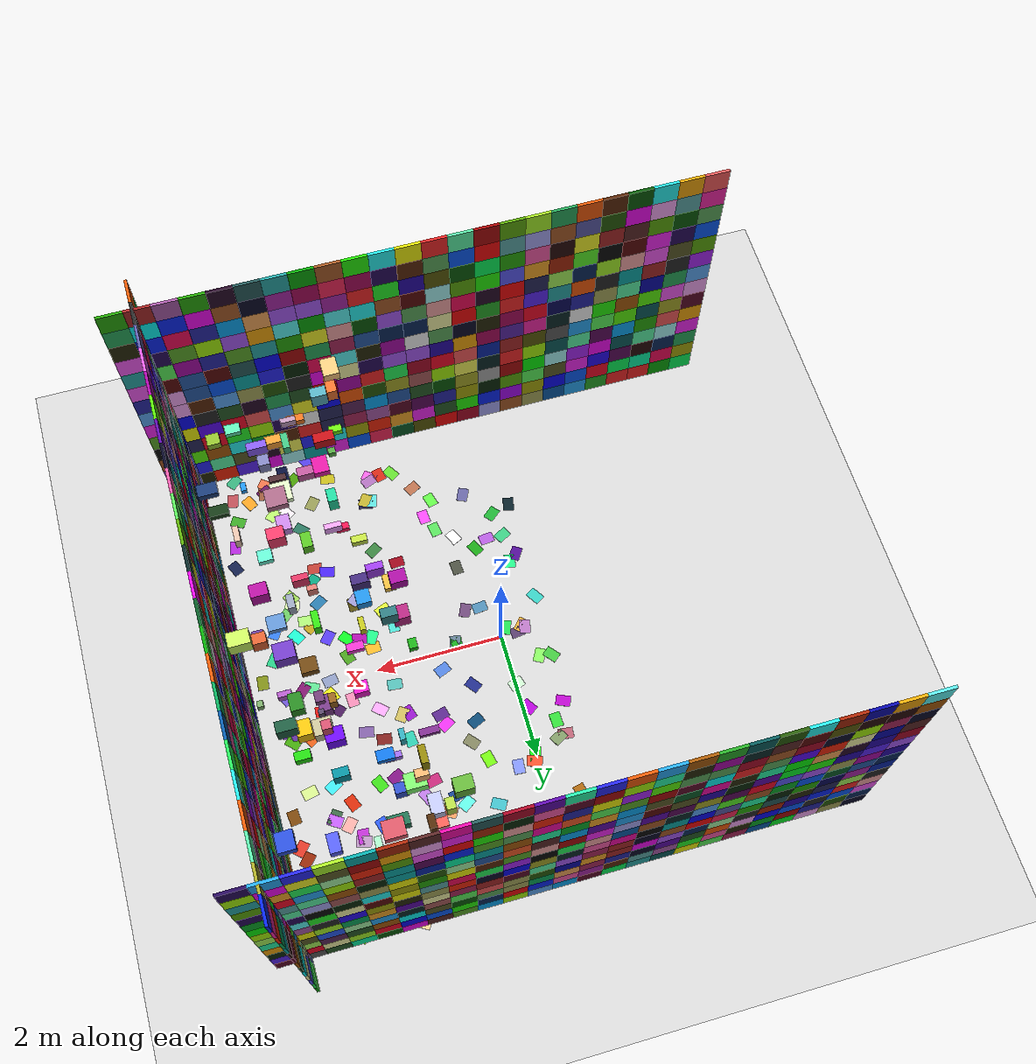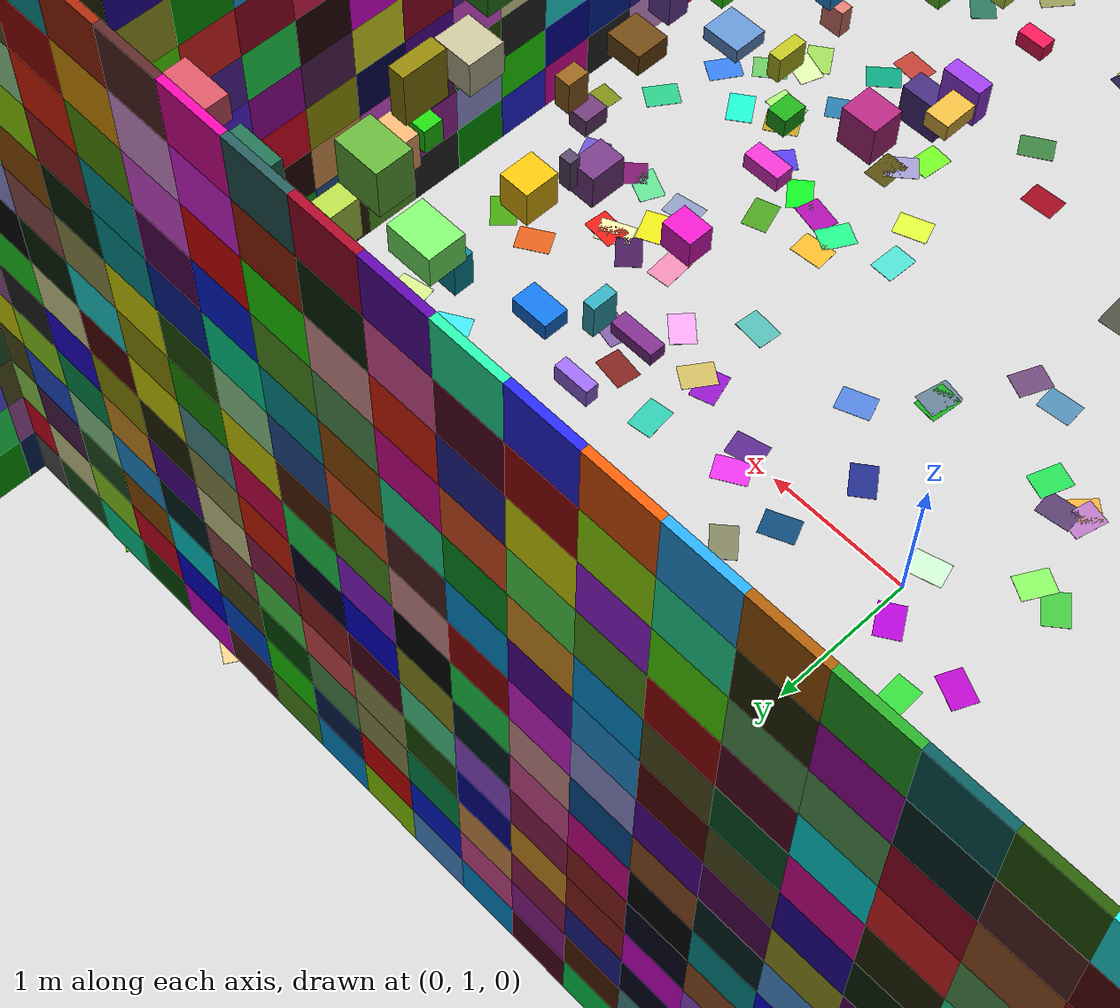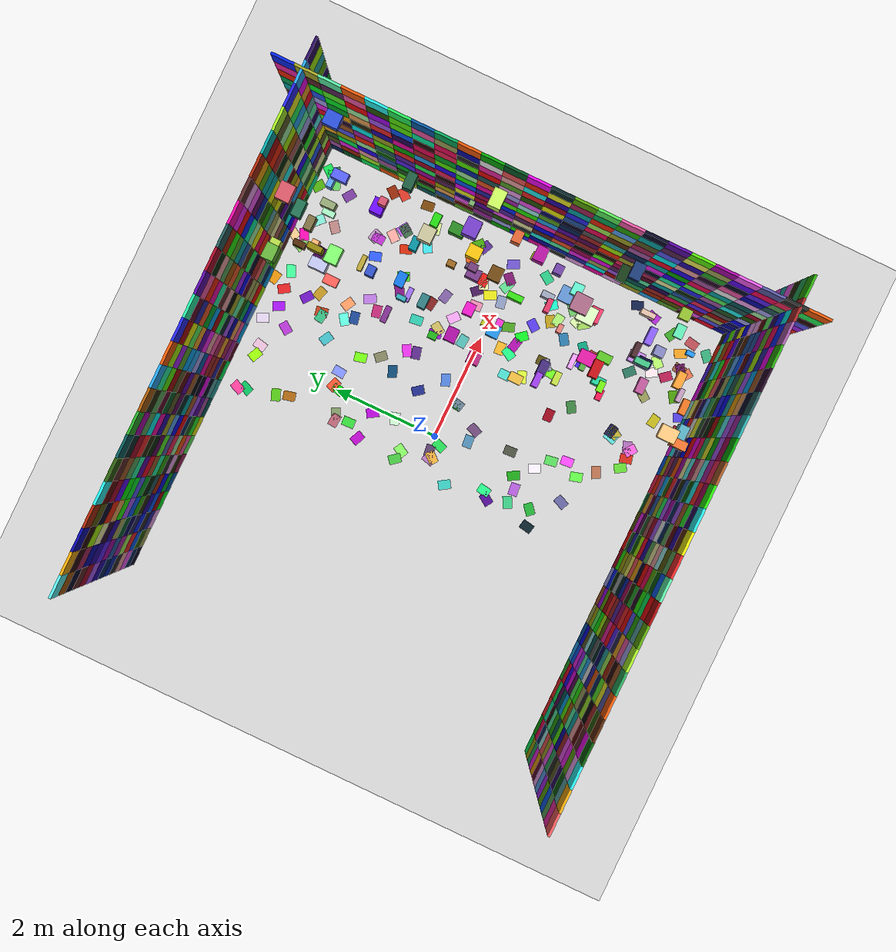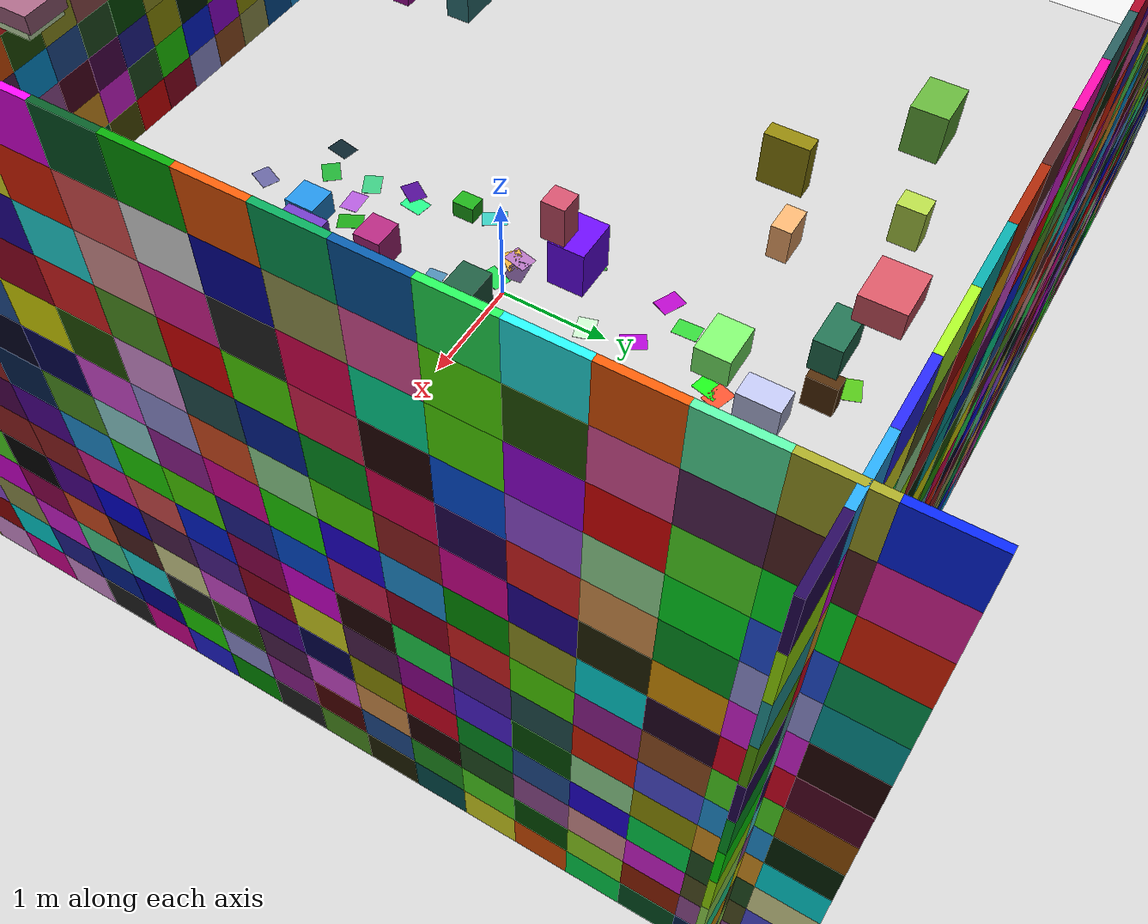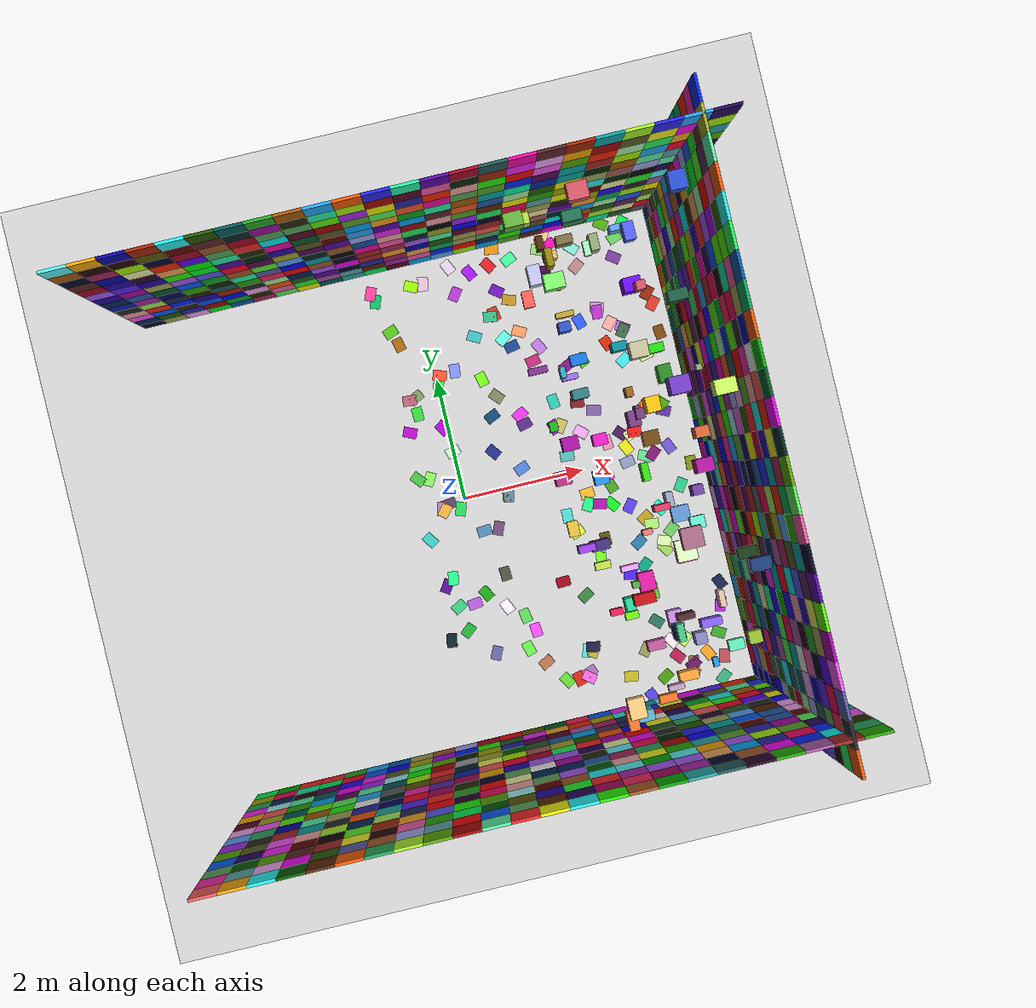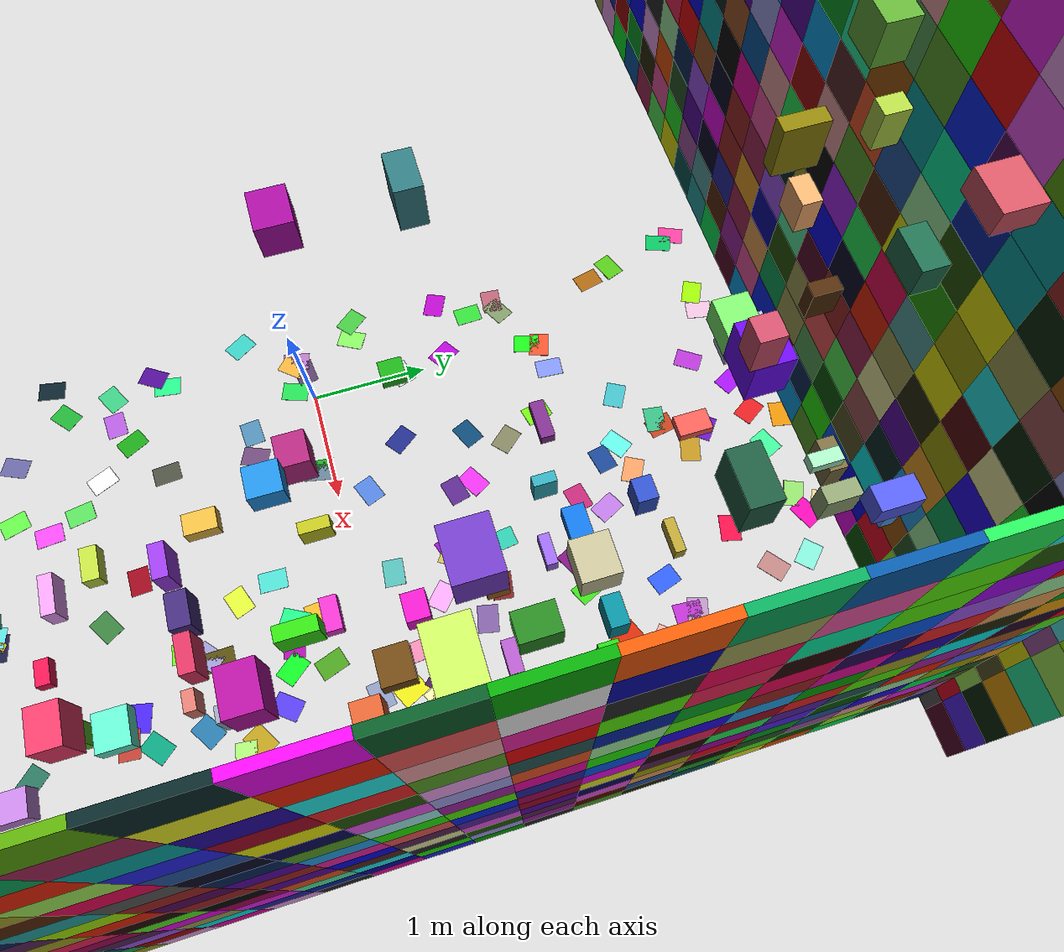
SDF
<?xml version='1.0' encoding='utf-8'?>
<sdf version="1.9">
  <world name="default">
    <physics type="ode">
      <max_step_size>0.004</max_step_size>
      <real_time_factor>1.0</real_time_factor>
      <real_time_update_rate>250</real_time_update_rate>
    </physics>
    <gravity>0 0 -9.8</gravity>
    <magnetic_field>6e-06 2.3e-05 -4.2e-05</magnetic_field>
    <atmosphere type="adiabatic" />
    <scene>
      <grid>false</grid>
      <ambient>0.4 0.4 0.4 1</ambient>
      <background>0.7 0.7 0.7 1</background>
      <shadows>true</shadows>
    </scene>
    <model name="ground_plane">
      <static>true</static>
      <link name="link">
        <collision name="collision">
          <geometry>
            <plane>
              <normal>0 0 1</normal>
              <size>1 1</size>
            </plane>
          </geometry>
          <surface>
            <friction>
              <ode />
            </friction>
            <bounce />
            <contact />
          </surface>
        </collision>
        <visual name="visual">
          <geometry>
            <plane>
              <normal>0 0 1</normal>
              <size>500 500</size>
            </plane>
          </geometry>
          <material>
            <ambient>0.8 0.8 0.8 1</ambient>
            <diffuse>0.8 0.8 0.8 1</diffuse>
            <specular>0.8 0.8 0.8 1</specular>
          </material>
        </visual>
        <pose>0 0 0 0 -0 0</pose>
        <inertial>
          <pose>0 0 0 0 -0 0</pose>
          <mass>1</mass>
          <inertia>
            <ixx>1</ixx>
            <ixy>0</ixy>
            <ixz>0</ixz>
            <iyy>1</iyy>
            <iyz>0</iyz>
            <izz>1</izz>
          </inertia>
        </inertial>
        <enable_wind>false</enable_wind>
      </link>
      <pose>0 0 0 0 -0 0</pose>
      <self_collide>false</self_collide>
    </model>
    <light name="sunUTC" type="directional">
      <pose>0 0 500 0 -0 0</pose>
      <cast_shadows>true</cast_shadows>
      <intensity>1</intensity>
      <direction>0.001 0.625 -0.78</direction>
      <diffuse>0.904 0.904 0.904 1</diffuse>
      <specular>0.271 0.271 0.271 1</specular>
      <attenuation>
        <range>2000</range>
        <linear>0</linear>
        <constant>1</constant>
        <quadratic>0</quadratic>
      </attenuation>
      <spot>
        <inner_angle>0</inner_angle>
        <outer_angle>0</outer_angle>
        <falloff>0</falloff>
      </spot>
    </light>
    <spherical_coordinates>
      <surface_model>EARTH_WGS84</surface_model>
      <world_frame_orientation>ENU</world_frame_orientation>
      <latitude_deg>47.397971057728974</latitude_deg>
      <longitude_deg> 8.546163739800146</longitude_deg>
      <elevation>0</elevation>
    </spherical_coordinates>
  <model name="vio_wall_0"><static>true</static><pose>4 0 2.5 0 0 0</pose><link name="wall"><collision name="surface"><geometry><box><size>0.04 9 5</size></box></geometry></collision><visual name="tile_0_0"><pose>0 -4.3125 -2.3205 0 0 0</pose><geometry><box><size>0.04 0.375 0.357</size></box></geometry><material><ambient>0.65 0.15 0.95 1</ambient><diffuse>0.65 0.15 0.95 1</diffuse></material></visual><visual name="tile_0_1"><pose>0 -3.9375 -2.3205 0 0 0</pose><geometry><box><size>0.04 0.375 0.357</size></box></geometry><material><ambient>0.03 0.03 0.65 1</ambient><diffuse>0.03 0.03 0.65 1</diffuse></material></visual><visual name="tile_0_2"><pose>0 -3.5625 -2.3205 0 0 0</pose><geometry><box><size>0.04 0.375 0.357</size></box></geometry><material><ambient>0.95 0.03 0.15 1</ambient><diffuse>0.95 0.03 0.15 1</diffuse></material></visual><visual name="tile_0_3"><pose>0 -3.1875 -2.3205 0 0 0</pose><geometry><box><size>0.04 0.375 0.357</size></box></geometry><material><ambient>0.15 0.03 0.03 1</ambient><diffuse>0.15 0.03 0.03 1</diffuse></material></visual><visual name="tile_0_4"><pose>0 -2.8125 -2.3205 0 0 0</pose><geometry><box><size>0.04 0.375 0.357</size></box></geometry><material><ambient>0.35 0.65 0.15 1</ambient><diffuse>0.35 0.65 0.15 1</diffuse></material></visual><visual name="tile_0_5"><pose>0 -2.4375 -2.3205 0 0 0</pose><geometry><box><size>0.04 0.375 0.357</size></box></geometry><material><ambient>0.15 0.65 0.95 1</ambient><diffuse>0.15 0.65 0.95 1</diffuse></material></visual><visual name="tile_0_6"><pose>0 -2.0625 -2.3205 0 0 0</pose><geometry><box><size>0.04 0.375 0.357</size></box></geometry><material><ambient>0.65 0.65 0.15 1</ambient><diffuse>0.65 0.65 0.15 1</diffuse></material></visual><visual name="tile_0_7"><pose>0 -1.6875 -2.3205 0 0 0</pose><geometry><box><size>0.04 0.375 0.357</size></box></geometry><material><ambient>0.95 0.65 0.95 1</ambient><diffuse>0.95 0.65 0.95 1</diffuse></material></visual><visual name="tile_0_8"><pose>0 -1.3125 -2.3205 0 0 0</pose><geometry><box><size>0.04 0.375 0.357</size></box></geometry><material><ambient>0.95 0.03 0.65 1</ambient><diffuse>0.95 0.03 0.65 1</diffuse></material></visual><visual name="tile_0_9"><pose>0 -0.9375 -2.3205 0 0 0</pose><geometry><box><size>0.04 0.375 0.357</size></box></geometry><material><ambient>0.95 0.65 0.95 1</ambient><diffuse>0.95 0.65 0.95 1</diffuse></material></visual><visual name="tile_0_10"><pose>0 -0.5625 -2.3205 0 0 0</pose><geometry><box><size>0.04 0.375 0.357</size></box></geometry><material><ambient>0.15 0.15 0.15 1</ambient><diffuse>0.15 0.15 0.15 1</diffuse></material></visual><visual name="tile_0_11"><pose>0 -0.1875 -2.3205 0 0 0</pose><geometry><box><size>0.04 0.375 0.357</size></box></geometry><material><ambient>0.95 0.03 0.65 1</ambient><diffuse>0.95 0.03 0.65 1</diffuse></material></visual><visual name="tile_0_12"><pose>0 0.1875 -2.3205 0 0 0</pose><geometry><box><size>0.04 0.375 0.357</size></box></geometry><material><ambient>0.15 0.15 0.95 1</ambient><diffuse>0.15 0.15 0.95 1</diffuse></material></visual><visual name="tile_0_13"><pose>0 0.5625 -2.3205 0 0 0</pose><geometry><box><size>0.04 0.375 0.357</size></box></geometry><material><ambient>0.03 0.65 0.03 1</ambient><diffuse>0.03 0.65 0.03 1</diffuse></material></visual><visual name="tile_0_14"><pose>0 0.9375 -2.3205 0 0 0</pose><geometry><box><size>0.04 0.375 0.357</size></box></geometry><material><ambient>0.15 0.15 0.15 1</ambient><diffuse>0.15 0.15 0.15 1</diffuse></material></visual><visual name="tile_0_15"><pose>0 1.3125 -2.3205 0 0 0</pose><geometry><box><size>0.04 0.375 0.357</size></box></geometry><material><ambient>0.35 0.65 0.15 1</ambient><diffuse>0.35 0.65 0.15 1</diffuse></material></visual><visual name="tile_0_16"><pose>0 1.6875 -2.3205 0 0 0</pose><geometry><box><size>0.04 0.375 0.357</size></box></geometry><material><ambient>0.15 0.15 0.03 1</ambient><diffuse>0.15 0.15 0.03 1</diffuse></material></visual><visual name="tile_0_17"><pose>0 2.0625 -2.3205 0 0 0</pose><geometry><box><size>0.04 0.375 0.357</size></box></geometry><material><ambient>0.03 0.35 0.35 1</ambient><diffuse>0.03 0.35 0.35 1</diffuse></material></visual><visual name="tile_0_18"><pose>0 2.4375 -2.3205 0 0 0</pose><geometry><box><size>0.04 0.375 0.357</size></box></geometry><material><ambient>0.95 0.95 0.15 1</ambient><diffuse>0.95 0.95 0.15 1</diffuse></material></visual><visual name="tile_0_19"><pose>0 2.8125 -2.3205 0 0 0</pose><geometry><box><size>0.04 0.375 0.357</size></box></geometry><material><ambient>0.95 0.35 0.03 1</ambient><diffuse>0.95 0.35 0.03 1</diffuse></material></visual><visual name="tile_0_20"><pose>0 3.1875 -2.3205 0 0 0</pose><geometry><box><size>0.04 0.375 0.357</size></box></geometry><material><ambient>0.03 0.95 0.35 1</ambient><diffuse>0.03 0.95 0.35 1</diffuse></material></visual><visual name="tile_0_21"><pose>0 3.5625 -2.3205 0 0 0</pose><geometry><box><size>0.04 0.375 0.357</size></box></geometry><material><ambient>0.03 0.35 0.15 1</ambient><diffuse>0.03 0.35 0.15 1</diffuse></material></visual><visual name="tile_0_22"><pose>0 3.9375 -2.3205 0 0 0</pose><geometry><box><size>0.04 0.375 0.357</size></box></geometry><material><ambient>0.03 0.15 0.35 1</ambient><diffuse>0.03 0.15 0.35 1</diffuse></material></visual><visual name="tile_0_23"><pose>0 4.3125 -2.3205 0 0 0</pose><geometry><box><size>0.04 0.375 0.357</size></box></geometry><material><ambient>0.03 0.65 0.03 1</ambient><diffuse>0.03 0.65 0.03 1</diffuse></material></visual><visual name="tile_1_0"><pose>0 -4.3125 -1.9634999999999998 0 0 0</pose><geometry><box><size>0.04 0.375 0.357</size></box></geometry><material><ambient>0.95 0.35 0.03 1</ambient><diffuse>0.95 0.35 0.03 1</diffuse></material></visual><visual name="tile_1_1"><pose>0 -3.9375 -1.9634999999999998 0 0 0</pose><geometry><box><size>0.04 0.375 0.357</size></box></geometry><material><ambient>0.03 0.03 0.35 1</ambient><diffuse>0.03 0.03 0.35 1</diffuse></material></visual><visual name="tile_1_2"><pose>0 -3.5625 -1.9634999999999998 0 0 0</pose><geometry><box><size>0.04 0.375 0.357</size></box></geometry><material><ambient>0.35 0.35 0.95 1</ambient><diffuse>0.35 0.35 0.95 1</diffuse></material></visual><visual name="tile_1_3"><pose>0 -3.1875 -1.9634999999999998 0 0 0</pose><geometry><box><size>0.04 0.375 0.357</size></box></geometry><material><ambient>0.95 0.35 0.95 1</ambient><diffuse>0.95 0.35 0.95 1</diffuse></material></visual><visual name="tile_1_4"><pose>0 -2.8125 -1.9634999999999998 0 0 0</pose><geometry><box><size>0.04 0.375 0.357</size></box></geometry><material><ambient>0.35 0.35 0.03 1</ambient><diffuse>0.35 0.35 0.03 1</diffuse></material></visual><visual name="tile_1_5"><pose>0 -2.4375 -1.9634999999999998 0 0 0</pose><geometry><box><size>0.04 0.375 0.357</size></box></geometry><material><ambient>0.65 0.15 0.03 1</ambient><diffuse>0.65 0.15 0.03 1</diffuse></material></visual><visual name="tile_1_6"><pose>0 -2.0625 -1.9634999999999998 0 0 0</pose><geometry><box><size>0.04 0.375 0.357</size></box></geometry><material><ambient>0.15 0.65 0.35 1</ambient><diffuse>0.15 0.65 0.35 1</diffuse></material></visual><visual name="tile_1_7"><pose>0 -1.6875 -1.9634999999999998 0 0 0</pose><geometry><box><size>0.04 0.375 0.357</size></box></geometry><material><ambient>0.65 0.03 0.03 1</ambient><diffuse>0.65 0.03 0.03 1</diffuse></material></visual><visual name="tile_1_8"><pose>0 -1.3125 -1.9634999999999998 0 0 0</pose><geometry><box><size>0.04 0.375 0.357</size></box></geometry><material><ambient>0.03 0.95 0.95 1</ambient><diffuse>0.03 0.95 0.95 1</diffuse></material></visual><visual name="tile_1_9"><pose>0 -0.9375 -1.9634999999999998 0 0 0</pose><geometry><box><size>0.04 0.375 0.357</size></box></geometry><material><ambient>0.15 0.15 0.65 1</ambient><diffuse>0.15 0.15 0.65 1</diffuse></material></visual><visual name="tile_1_10"><pose>0 -0.5625 -1.9634999999999998 0 0 0</pose><geometry><box><size>0.04 0.375 0.357</size></box></geometry><material><ambient>0.03 0.15 0.65 1</ambient><diffuse>0.03 0.15 0.65 1</diffuse></material></visual><visual name="tile_1_11"><pose>0 -0.1875 -1.9634999999999998 0 0 0</pose><geometry><box><size>0.04 0.375 0.357</size></box></geometry><material><ambient>0.03 0.03 0.65 1</ambient><diffuse>0.03 0.03 0.65 1</diffuse></material></visual><visual name="tile_1_12"><pose>0 0.1875 -1.9634999999999998 0 0 0</pose><geometry><box><size>0.04 0.375 0.357</size></box></geometry><material><ambient>0.15 0.95 0.03 1</ambient><diffuse>0.15 0.95 0.03 1</diffuse></material></visual><visual name="tile_1_13"><pose>0 0.5625 -1.9634999999999998 0 0 0</pose><geometry><box><size>0.04 0.375 0.357</size></box></geometry><material><ambient>0.65 0.65 0.95 1</ambient><diffuse>0.65 0.65 0.95 1</diffuse></material></visual><visual name="tile_1_14"><pose>0 0.9375 -1.9634999999999998 0 0 0</pose><geometry><box><size>0.04 0.375 0.357</size></box></geometry><material><ambient>0.65 0.15 0.65 1</ambient><diffuse>0.65 0.15 0.65 1</diffuse></material></visual><visual name="tile_1_15"><pose>0 1.3125 -1.9634999999999998 0 0 0</pose><geometry><box><size>0.04 0.375 0.357</size></box></geometry><material><ambient>0.35 0.03 0.03 1</ambient><diffuse>0.35 0.03 0.03 1</diffuse></material></visual><visual name="tile_1_16"><pose>0 1.6875 -1.9634999999999998 0 0 0</pose><geometry><box><size>0.04 0.375 0.357</size></box></geometry><material><ambient>0.15 0.35 0.65 1</ambient><diffuse>0.15 0.35 0.65 1</diffuse></material></visual><visual name="tile_1_17"><pose>0 2.0625 -1.9634999999999998 0 0 0</pose><geometry><box><size>0.04 0.375 0.357</size></box></geometry><material><ambient>0.15 0.65 0.15 1</ambient><diffuse>0.15 0.65 0.15 1</diffuse></material></visual><visual name="tile_1_18"><pose>0 2.4375 -1.9634999999999998 0 0 0</pose><geometry><box><size>0.04 0.375 0.357</size></box></geometry><material><ambient>0.35 0.95 0.15 1</ambient><diffuse>0.35 0.95 0.15 1</diffuse></material></visual><visual name="tile_1_19"><pose>0 2.8125 -1.9634999999999998 0 0 0</pose><geometry><box><size>0.04 0.375 0.357</size></box></geometry><material><ambient>0.03 0.35 0.03 1</ambient><diffuse>0.03 0.35 0.03 1</diffuse></material></visual><visual name="tile_1_20"><pose>0 3.1875 -1.9634999999999998 0 0 0</pose><geometry><box><size>0.04 0.375 0.357</size></box></geometry><material><ambient>0.65 0.95 0.15 1</ambient><diffuse>0.65 0.95 0.15 1</diffuse></material></visual><visual name="tile_1_21"><pose>0 3.5625 -1.9634999999999998 0 0 0</pose><geometry><box><size>0.04 0.375 0.357</size></box></geometry><material><ambient>0.65 0.15 0.03 1</ambient><diffuse>0.65 0.15 0.03 1</diffuse></material></visual><visual name="tile_1_22"><pose>0 3.9375 -1.9634999999999998 0 0 0</pose><geometry><box><size>0.04 0.375 0.357</size></box></geometry><material><ambient>0.65 0.35 0.65 1</ambient><diffuse>0.65 0.35 0.65 1</diffuse></material></visual><visual name="tile_1_23"><pose>0 4.3125 -1.9634999999999998 0 0 0</pose><geometry><box><size>0.04 0.375 0.357</size></box></geometry><material><ambient>0.15 0.95 0.35 1</ambient><diffuse>0.15 0.95 0.35 1</diffuse></material></visual><visual name="tile_2_0"><pose>0 -4.3125 -1.6065 0 0 0</pose><geometry><box><size>0.04 0.375 0.357</size></box></geometry><material><ambient>0.03 0.95 0.65 1</ambient><diffuse>0.03 0.95 0.65 1</diffuse></material></visual><visual name="tile_2_1"><pose>0 -3.9375 -1.6065 0 0 0</pose><geometry><box><size>0.04 0.375 0.357</size></box></geometry><material><ambient>0.03 0.03 0.65 1</ambient><diffuse>0.03 0.03 0.65 1</diffuse></material></visual><visual name="tile_2_2"><pose>0 -3.5625 -1.6065 0 0 0</pose><geometry><box><size>0.04 0.375 0.357</size></box></geometry><material><ambient>0.65 0.65 0.35 1</ambient><diffuse>0.65 0.65 0.35 1</diffuse></material></visual><visual name="tile_2_3"><pose>0 -3.1875 -1.6065 0 0 0</pose><geometry><box><size>0.04 0.375 0.357</size></box></geometry><material><ambient>0.65 0.03 0.15 1</ambient><diffuse>0.65 0.03 0.15 1</diffuse></material></visual><visual name="tile_2_4"><pose>0 -2.8125 -1.6065 0 0 0</pose><geometry><box><size>0.04 0.375 0.357</size></box></geometry><material><ambient>0.95 0.03 0.35 1</ambient><diffuse>0.95 0.03 0.35 1</diffuse></material></visual><visual name="tile_2_5"><pose>0 -2.4375 -1.6065 0 0 0</pose><geometry><box><size>0.04 0.375 0.357</size></box></geometry><material><ambient>0.65 0.15 0.15 1</ambient><diffuse>0.65 0.15 0.15 1</diffuse></material></visual><visual name="tile_2_6"><pose>0 -2.0625 -1.6065 0 0 0</pose><geometry><box><size>0.04 0.375 0.357</size></box></geometry><material><ambient>0.03 0.35 0.35 1</ambient><diffuse>0.03 0.35 0.35 1</diffuse></material></visual><visual name="tile_2_7"><pose>0 -1.6875 -1.6065 0 0 0</pose><geometry><box><size>0.04 0.375 0.357</size></box></geometry><material><ambient>0.65 0.35 0.95 1</ambient><diffuse>0.65 0.35 0.95 1</diffuse></material></visual><visual name="tile_2_8"><pose>0 -1.3125 -1.6065 0 0 0</pose><geometry><box><size>0.04 0.375 0.357</size></box></geometry><material><ambient>0.65 0.65 0.35 1</ambient><diffuse>0.65 0.65 0.35 1</diffuse></material></visual><visual name="tile_2_9"><pose>0 -0.9375 -1.6065 0 0 0</pose><geometry><box><size>0.04 0.375 0.357</size></box></geometry><material><ambient>0.95 0.15 0.95 1</ambient><diffuse>0.95 0.15 0.95 1</diffuse></material></visual><visual name="tile_2_10"><pose>0 -0.5625 -1.6065 0 0 0</pose><geometry><box><size>0.04 0.375 0.357</size></box></geometry><material><ambient>0.35 0.95 0.65 1</ambient><diffuse>0.35 0.95 0.65 1</diffuse></material></visual><visual name="tile_2_11"><pose>0 -0.1875 -1.6065 0 0 0</pose><geometry><box><size>0.04 0.375 0.357</size></box></geometry><material><ambient>0.15 0.95 0.95 1</ambient><diffuse>0.15 0.95 0.95 1</diffuse></material></visual><visual name="tile_2_12"><pose>0 0.1875 -1.6065 0 0 0</pose><geometry><box><size>0.04 0.375 0.357</size></box></geometry><material><ambient>0.15 0.15 0.15 1</ambient><diffuse>0.15 0.15 0.15 1</diffuse></material></visual><visual name="tile_2_13"><pose>0 0.5625 -1.6065 0 0 0</pose><geometry><box><size>0.04 0.375 0.357</size></box></geometry><material><ambient>0.15 0.35 0.03 1</ambient><diffuse>0.15 0.35 0.03 1</diffuse></material></visual><visual name="tile_2_14"><pose>0 0.9375 -1.6065 0 0 0</pose><geometry><box><size>0.04 0.375 0.357</size></box></geometry><material><ambient>0.35 0.15 0.35 1</ambient><diffuse>0.35 0.15 0.35 1</diffuse></material></visual><visual name="tile_2_15"><pose>0 1.3125 -1.6065 0 0 0</pose><geometry><box><size>0.04 0.375 0.357</size></box></geometry><material><ambient>0.95 0.35 0.95 1</ambient><diffuse>0.95 0.35 0.95 1</diffuse></material></visual><visual name="tile_2_16"><pose>0 1.6875 -1.6065 0 0 0</pose><geometry><box><size>0.04 0.375 0.357</size></box></geometry><material><ambient>0.95 0.65 0.35 1</ambient><diffuse>0.95 0.65 0.35 1</diffuse></material></visual><visual name="tile_2_17"><pose>0 2.0625 -1.6065 0 0 0</pose><geometry><box><size>0.04 0.375 0.357</size></box></geometry><material><ambient>0.15 0.03 0.03 1</ambient><diffuse>0.15 0.03 0.03 1</diffuse></material></visual><visual name="tile_2_18"><pose>0 2.4375 -1.6065 0 0 0</pose><geometry><box><size>0.04 0.375 0.357</size></box></geometry><material><ambient>0.15 0.35 0.15 1</ambient><diffuse>0.15 0.35 0.15 1</diffuse></material></visual><visual name="tile_2_19"><pose>0 2.8125 -1.6065 0 0 0</pose><geometry><box><size>0.04 0.375 0.357</size></box></geometry><material><ambient>0.65 0.35 0.65 1</ambient><diffuse>0.65 0.35 0.65 1</diffuse></material></visual><visual name="tile_2_20"><pose>0 3.1875 -1.6065 0 0 0</pose><geometry><box><size>0.04 0.375 0.357</size></box></geometry><material><ambient>0.95 0.65 0.65 1</ambient><diffuse>0.95 0.65 0.65 1</diffuse></material></visual><visual name="tile_2_21"><pose>0 3.5625 -1.6065 0 0 0</pose><geometry><box><size>0.04 0.375 0.357</size></box></geometry><material><ambient>0.95 0.15 0.95 1</ambient><diffuse>0.95 0.15 0.95 1</diffuse></material></visual><visual name="tile_2_22"><pose>0 3.9375 -1.6065 0 0 0</pose><geometry><box><size>0.04 0.375 0.357</size></box></geometry><material><ambient>0.35 0.35 0.15 1</ambient><diffuse>0.35 0.35 0.15 1</diffuse></material></visual><visual name="tile_2_23"><pose>0 4.3125 -1.6065 0 0 0</pose><geometry><box><size>0.04 0.375 0.357</size></box></geometry><material><ambient>0.35 0.35 0.95 1</ambient><diffuse>0.35 0.35 0.95 1</diffuse></material></visual><visual name="tile_3_0"><pose>0 -4.3125 -1.2494999999999998 0 0 0</pose><geometry><box><size>0.04 0.375 0.357</size></box></geometry><material><ambient>0.15 0.03 0.95 1</ambient><diffuse>0.15 0.03 0.95 1</diffuse></material></visual><visual name="tile_3_1"><pose>0 -3.9375 -1.2494999999999998 0 0 0</pose><geometry><box><size>0.04 0.375 0.357</size></box></geometry><material><ambient>0.03 0.03 0.35 1</ambient><diffuse>0.03 0.03 0.35 1</diffuse></material></visual><visual name="tile_3_2"><pose>0 -3.5625 -1.2494999999999998 0 0 0</pose><geometry><box><size>0.04 0.375 0.357</size></box></geometry><material><ambient>0.65 0.03 0.03 1</ambient><diffuse>0.65 0.03 0.03 1</diffuse></material></visual><visual name="tile_3_3"><pose>0 -3.1875 -1.2494999999999998 0 0 0</pose><geometry><box><size>0.04 0.375 0.357</size></box></geometry><material><ambient>0.35 0.15 0.95 1</ambient><diffuse>0.35 0.15 0.95 1</diffuse></material></visual><visual name="tile_3_4"><pose>0 -2.8125 -1.2494999999999998 0 0 0</pose><geometry><box><size>0.04 0.375 0.357</size></box></geometry><material><ambient>0.15 0.65 0.35 1</ambient><diffuse>0.15 0.65 0.35 1</diffuse></material></visual><visual name="tile_3_5"><pose>0 -2.4375 -1.2494999999999998 0 0 0</pose><geometry><box><size>0.04 0.375 0.357</size></box></geometry><material><ambient>0.15 0.03 0.35 1</ambient><diffuse>0.15 0.03 0.35 1</diffuse></material></visual><visual name="tile_3_6"><pose>0 -2.0625 -1.2494999999999998 0 0 0</pose><geometry><box><size>0.04 0.375 0.357</size></box></geometry><material><ambient>0.35 0.95 0.65 1</ambient><diffuse>0.35 0.95 0.65 1</diffuse></material></visual><visual name="tile_3_7"><pose>0 -1.6875 -1.2494999999999998 0 0 0</pose><geometry><box><size>0.04 0.375 0.357</size></box></geometry><material><ambient>0.35 0.15 0.35 1</ambient><diffuse>0.35 0.15 0.35 1</diffuse></material></visual><visual name="tile_3_8"><pose>0 -1.3125 -1.2494999999999998 0 0 0</pose><geometry><box><size>0.04 0.375 0.357</size></box></geometry><material><ambient>0.95 0.03 0.95 1</ambient><diffuse>0.95 0.03 0.95 1</diffuse></material></visual><visual name="tile_3_9"><pose>0 -0.9375 -1.2494999999999998 0 0 0</pose><geometry><box><size>0.04 0.375 0.357</size></box></geometry><material><ambient>0.65 0.03 0.35 1</ambient><diffuse>0.65 0.03 0.35 1</diffuse></material></visual><visual name="tile_3_10"><pose>0 -0.5625 -1.2494999999999998 0 0 0</pose><geometry><box><size>0.04 0.375 0.357</size></box></geometry><material><ambient>0.95 0.35 0.15 1</ambient><diffuse>0.95 0.35 0.15 1</diffuse></material></visual><visual name="tile_3_11"><pose>0 -0.1875 -1.2494999999999998 0 0 0</pose><geometry><box><size>0.04 0.375 0.357</size></box></geometry><material><ambient>0.35 0.15 0.15 1</ambient><diffuse>0.35 0.15 0.15 1</diffuse></material></visual><visual name="tile_3_12"><pose>0 0.1875 -1.2494999999999998 0 0 0</pose><geometry><box><size>0.04 0.375 0.357</size></box></geometry><material><ambient>0.95 0.95 0.65 1</ambient><diffuse>0.95 0.95 0.65 1</diffuse></material></visual><visual name="tile_3_13"><pose>0 0.5625 -1.2494999999999998 0 0 0</pose><geometry><box><size>0.04 0.375 0.357</size></box></geometry><material><ambient>0.95 0.35 0.95 1</ambient><diffuse>0.95 0.35 0.95 1</diffuse></material></visual><visual name="tile_3_14"><pose>0 0.9375 -1.2494999999999998 0 0 0</pose><geometry><box><size>0.04 0.375 0.357</size></box></geometry><material><ambient>0.35 0.03 0.65 1</ambient><diffuse>0.35 0.03 0.65 1</diffuse></material></visual><visual name="tile_3_15"><pose>0 1.3125 -1.2494999999999998 0 0 0</pose><geometry><box><size>0.04 0.375 0.357</size></box></geometry><material><ambient>0.03 0.03 0.35 1</ambient><diffuse>0.03 0.03 0.35 1</diffuse></material></visual><visual name="tile_3_16"><pose>0 1.6875 -1.2494999999999998 0 0 0</pose><geometry><box><size>0.04 0.375 0.357</size></box></geometry><material><ambient>0.65 0.65 0.03 1</ambient><diffuse>0.65 0.65 0.03 1</diffuse></material></visual><visual name="tile_3_17"><pose>0 2.0625 -1.2494999999999998 0 0 0</pose><geometry><box><size>0.04 0.375 0.357</size></box></geometry><material><ambient>0.95 0.03 0.15 1</ambient><diffuse>0.95 0.03 0.15 1</diffuse></material></visual><visual name="tile_3_18"><pose>0 2.4375 -1.2494999999999998 0 0 0</pose><geometry><box><size>0.04 0.375 0.357</size></box></geometry><material><ambient>0.03 0.65 0.15 1</ambient><diffuse>0.03 0.65 0.15 1</diffuse></material></visual><visual name="tile_3_19"><pose>0 2.8125 -1.2494999999999998 0 0 0</pose><geometry><box><size>0.04 0.375 0.357</size></box></geometry><material><ambient>0.15 0.35 0.65 1</ambient><diffuse>0.15 0.35 0.65 1</diffuse></material></visual><visual name="tile_3_20"><pose>0 3.1875 -1.2494999999999998 0 0 0</pose><geometry><box><size>0.04 0.375 0.357</size></box></geometry><material><ambient>0.15 0.03 0.95 1</ambient><diffuse>0.15 0.03 0.95 1</diffuse></material></visual><visual name="tile_3_21"><pose>0 3.5625 -1.2494999999999998 0 0 0</pose><geometry><box><size>0.04 0.375 0.357</size></box></geometry><material><ambient>0.03 0.95 0.35 1</ambient><diffuse>0.03 0.95 0.35 1</diffuse></material></visual><visual name="tile_3_22"><pose>0 3.9375 -1.2494999999999998 0 0 0</pose><geometry><box><size>0.04 0.375 0.357</size></box></geometry><material><ambient>0.15 0.35 0.15 1</ambient><diffuse>0.15 0.35 0.15 1</diffuse></material></visual><visual name="tile_3_23"><pose>0 4.3125 -1.2494999999999998 0 0 0</pose><geometry><box><size>0.04 0.375 0.357</size></box></geometry><material><ambient>0.95 0.95 0.65 1</ambient><diffuse>0.95 0.95 0.65 1</diffuse></material></visual><visual name="tile_4_0"><pose>0 -4.3125 -0.8925 0 0 0</pose><geometry><box><size>0.04 0.375 0.357</size></box></geometry><material><ambient>0.03 0.03 0.15 1</ambient><diffuse>0.03 0.03 0.15 1</diffuse></material></visual><visual name="tile_4_1"><pose>0 -3.9375 -0.8925 0 0 0</pose><geometry><box><size>0.04 0.375 0.357</size></box></geometry><material><ambient>0.03 0.03 0.95 1</ambient><diffuse>0.03 0.03 0.95 1</diffuse></material></visual><visual name="tile_4_2"><pose>0 -3.5625 -0.8925 0 0 0</pose><geometry><box><size>0.04 0.375 0.357</size></box></geometry><material><ambient>0.35 0.35 0.35 1</ambient><diffuse>0.35 0.35 0.35 1</diffuse></material></visual><visual name="tile_4_3"><pose>0 -3.1875 -0.8925 0 0 0</pose><geometry><box><size>0.04 0.375 0.357</size></box></geometry><material><ambient>0.95 0.15 0.35 1</ambient><diffuse>0.95 0.15 0.35 1</diffuse></material></visual><visual name="tile_4_4"><pose>0 -2.8125 -0.8925 0 0 0</pose><geometry><box><size>0.04 0.375 0.357</size></box></geometry><material><ambient>0.15 0.35 0.65 1</ambient><diffuse>0.15 0.35 0.65 1</diffuse></material></visual><visual name="tile_4_5"><pose>0 -2.4375 -0.8925 0 0 0</pose><geometry><box><size>0.04 0.375 0.357</size></box></geometry><material><ambient>0.03 0.65 0.65 1</ambient><diffuse>0.03 0.65 0.65 1</diffuse></material></visual><visual name="tile_4_6"><pose>0 -2.0625 -0.8925 0 0 0</pose><geometry><box><size>0.04 0.375 0.357</size></box></geometry><material><ambient>0.35 0.03 0.15 1</ambient><diffuse>0.35 0.03 0.15 1</diffuse></material></visual><visual name="tile_4_7"><pose>0 -1.6875 -0.8925 0 0 0</pose><geometry><box><size>0.04 0.375 0.357</size></box></geometry><material><ambient>0.65 0.03 0.35 1</ambient><diffuse>0.65 0.03 0.35 1</diffuse></material></visual><visual name="tile_4_8"><pose>0 -1.3125 -0.8925 0 0 0</pose><geometry><box><size>0.04 0.375 0.357</size></box></geometry><material><ambient>0.35 0.95 0.15 1</ambient><diffuse>0.35 0.95 0.15 1</diffuse></material></visual><visual name="tile_4_9"><pose>0 -0.9375 -0.8925 0 0 0</pose><geometry><box><size>0.04 0.375 0.357</size></box></geometry><material><ambient>0.03 0.03 0.03 1</ambient><diffuse>0.03 0.03 0.03 1</diffuse></material></visual><visual name="tile_4_10"><pose>0 -0.5625 -0.8925 0 0 0</pose><geometry><box><size>0.04 0.375 0.357</size></box></geometry><material><ambient>0.35 0.03 0.65 1</ambient><diffuse>0.35 0.03 0.65 1</diffuse></material></visual><visual name="tile_4_11"><pose>0 -0.1875 -0.8925 0 0 0</pose><geometry><box><size>0.04 0.375 0.357</size></box></geometry><material><ambient>0.03 0.03 0.95 1</ambient><diffuse>0.03 0.03 0.95 1</diffuse></material></visual><visual name="tile_4_12"><pose>0 0.1875 -0.8925 0 0 0</pose><geometry><box><size>0.04 0.375 0.357</size></box></geometry><material><ambient>0.35 0.15 0.35 1</ambient><diffuse>0.35 0.15 0.35 1</diffuse></material></visual><visual name="tile_4_13"><pose>0 0.5625 -0.8925 0 0 0</pose><geometry><box><size>0.04 0.375 0.357</size></box></geometry><material><ambient>0.35 0.15 0.65 1</ambient><diffuse>0.35 0.15 0.65 1</diffuse></material></visual><visual name="tile_4_14"><pose>0 0.9375 -0.8925 0 0 0</pose><geometry><box><size>0.04 0.375 0.357</size></box></geometry><material><ambient>0.65 0.03 0.15 1</ambient><diffuse>0.65 0.03 0.15 1</diffuse></material></visual><visual name="tile_4_15"><pose>0 1.3125 -0.8925 0 0 0</pose><geometry><box><size>0.04 0.375 0.357</size></box></geometry><material><ambient>0.95 0.95 0.15 1</ambient><diffuse>0.95 0.95 0.15 1</diffuse></material></visual><visual name="tile_4_16"><pose>0 1.6875 -0.8925 0 0 0</pose><geometry><box><size>0.04 0.375 0.357</size></box></geometry><material><ambient>0.35 0.15 0.35 1</ambient><diffuse>0.35 0.15 0.35 1</diffuse></material></visual><visual name="tile_4_17"><pose>0 2.0625 -0.8925 0 0 0</pose><geometry><box><size>0.04 0.375 0.357</size></box></geometry><material><ambient>0.65 0.03 0.65 1</ambient><diffuse>0.65 0.03 0.65 1</diffuse></material></visual><visual name="tile_4_18"><pose>0 2.4375 -0.8925 0 0 0</pose><geometry><box><size>0.04 0.375 0.357</size></box></geometry><material><ambient>0.35 0.15 0.95 1</ambient><diffuse>0.35 0.15 0.95 1</diffuse></material></visual><visual name="tile_4_19"><pose>0 2.8125 -0.8925 0 0 0</pose><geometry><box><size>0.04 0.375 0.357</size></box></geometry><material><ambient>0.03 0.35 0.03 1</ambient><diffuse>0.03 0.35 0.03 1</diffuse></material></visual><visual name="tile_4_20"><pose>0 3.1875 -0.8925 0 0 0</pose><geometry><box><size>0.04 0.375 0.357</size></box></geometry><material><ambient>0.65 0.95 0.65 1</ambient><diffuse>0.65 0.95 0.65 1</diffuse></material></visual><visual name="tile_4_21"><pose>0 3.5625 -0.8925 0 0 0</pose><geometry><box><size>0.04 0.375 0.357</size></box></geometry><material><ambient>0.65 0.65 0.03 1</ambient><diffuse>0.65 0.65 0.03 1</diffuse></material></visual><visual name="tile_4_22"><pose>0 3.9375 -0.8925 0 0 0</pose><geometry><box><size>0.04 0.375 0.357</size></box></geometry><material><ambient>0.95 0.65 0.15 1</ambient><diffuse>0.95 0.65 0.15 1</diffuse></material></visual><visual name="tile_4_23"><pose>0 4.3125 -0.8925 0 0 0</pose><geometry><box><size>0.04 0.375 0.357</size></box></geometry><material><ambient>0.03 0.95 0.95 1</ambient><diffuse>0.03 0.95 0.95 1</diffuse></material></visual><visual name="tile_5_0"><pose>0 -4.3125 -0.5355 0 0 0</pose><geometry><box><size>0.04 0.375 0.357</size></box></geometry><material><ambient>0.65 0.65 0.35 1</ambient><diffuse>0.65 0.65 0.35 1</diffuse></material></visual><visual name="tile_5_1"><pose>0 -3.9375 -0.5355 0 0 0</pose><geometry><box><size>0.04 0.375 0.357</size></box></geometry><material><ambient>0.65 0.65 0.95 1</ambient><diffuse>0.65 0.65 0.95 1</diffuse></material></visual><visual name="tile_5_2"><pose>0 -3.5625 -0.5355 0 0 0</pose><geometry><box><size>0.04 0.375 0.357</size></box></geometry><material><ambient>0.15 0.35 0.15 1</ambient><diffuse>0.15 0.35 0.15 1</diffuse></material></visual><visual name="tile_5_3"><pose>0 -3.1875 -0.5355 0 0 0</pose><geometry><box><size>0.04 0.375 0.357</size></box></geometry><material><ambient>0.15 0.15 0.65 1</ambient><diffuse>0.15 0.15 0.65 1</diffuse></material></visual><visual name="tile_5_4"><pose>0 -2.8125 -0.5355 0 0 0</pose><geometry><box><size>0.04 0.375 0.357</size></box></geometry><material><ambient>0.03 0.15 0.03 1</ambient><diffuse>0.03 0.15 0.03 1</diffuse></material></visual><visual name="tile_5_5"><pose>0 -2.4375 -0.5355 0 0 0</pose><geometry><box><size>0.04 0.375 0.357</size></box></geometry><material><ambient>0.95 0.95 0.65 1</ambient><diffuse>0.95 0.95 0.65 1</diffuse></material></visual><visual name="tile_5_6"><pose>0 -2.0625 -0.5355 0 0 0</pose><geometry><box><size>0.04 0.375 0.357</size></box></geometry><material><ambient>0.65 0.15 0.35 1</ambient><diffuse>0.65 0.15 0.35 1</diffuse></material></visual><visual name="tile_5_7"><pose>0 -1.6875 -0.5355 0 0 0</pose><geometry><box><size>0.04 0.375 0.357</size></box></geometry><material><ambient>0.95 0.15 0.35 1</ambient><diffuse>0.95 0.15 0.35 1</diffuse></material></visual><visual name="tile_5_8"><pose>0 -1.3125 -0.5355 0 0 0</pose><geometry><box><size>0.04 0.375 0.357</size></box></geometry><material><ambient>0.15 0.03 0.03 1</ambient><diffuse>0.15 0.03 0.03 1</diffuse></material></visual><visual name="tile_5_9"><pose>0 -0.9375 -0.5355 0 0 0</pose><geometry><box><size>0.04 0.375 0.357</size></box></geometry><material><ambient>0.65 0.15 0.15 1</ambient><diffuse>0.65 0.15 0.15 1</diffuse></material></visual><visual name="tile_5_10"><pose>0 -0.5625 -0.5355 0 0 0</pose><geometry><box><size>0.04 0.375 0.357</size></box></geometry><material><ambient>0.65 0.15 0.15 1</ambient><diffuse>0.65 0.15 0.15 1</diffuse></material></visual><visual name="tile_5_11"><pose>0 -0.1875 -0.5355 0 0 0</pose><geometry><box><size>0.04 0.375 0.357</size></box></geometry><material><ambient>0.95 0.15 0.65 1</ambient><diffuse>0.95 0.15 0.65 1</diffuse></material></visual><visual name="tile_5_12"><pose>0 0.1875 -0.5355 0 0 0</pose><geometry><box><size>0.04 0.375 0.357</size></box></geometry><material><ambient>0.95 0.35 0.35 1</ambient><diffuse>0.95 0.35 0.35 1</diffuse></material></visual><visual name="tile_5_13"><pose>0 0.5625 -0.5355 0 0 0</pose><geometry><box><size>0.04 0.375 0.357</size></box></geometry><material><ambient>0.03 0.15 0.95 1</ambient><diffuse>0.03 0.15 0.95 1</diffuse></material></visual><visual name="tile_5_14"><pose>0 0.9375 -0.5355 0 0 0</pose><geometry><box><size>0.04 0.375 0.357</size></box></geometry><material><ambient>0.65 0.03 0.35 1</ambient><diffuse>0.65 0.03 0.35 1</diffuse></material></visual><visual name="tile_5_15"><pose>0 1.3125 -0.5355 0 0 0</pose><geometry><box><size>0.04 0.375 0.357</size></box></geometry><material><ambient>0.95 0.03 0.95 1</ambient><diffuse>0.95 0.03 0.95 1</diffuse></material></visual><visual name="tile_5_16"><pose>0 1.6875 -0.5355 0 0 0</pose><geometry><box><size>0.04 0.375 0.357</size></box></geometry><material><ambient>0.15 0.03 0.03 1</ambient><diffuse>0.15 0.03 0.03 1</diffuse></material></visual><visual name="tile_5_17"><pose>0 2.0625 -0.5355 0 0 0</pose><geometry><box><size>0.04 0.375 0.357</size></box></geometry><material><ambient>0.15 0.95 0.35 1</ambient><diffuse>0.15 0.95 0.35 1</diffuse></material></visual><visual name="tile_5_18"><pose>0 2.4375 -0.5355 0 0 0</pose><geometry><box><size>0.04 0.375 0.357</size></box></geometry><material><ambient>0.35 0.15 0.65 1</ambient><diffuse>0.35 0.15 0.65 1</diffuse></material></visual><visual name="tile_5_19"><pose>0 2.8125 -0.5355 0 0 0</pose><geometry><box><size>0.04 0.375 0.357</size></box></geometry><material><ambient>0.15 0.35 0.35 1</ambient><diffuse>0.15 0.35 0.35 1</diffuse></material></visual><visual name="tile_5_20"><pose>0 3.1875 -0.5355 0 0 0</pose><geometry><box><size>0.04 0.375 0.357</size></box></geometry><material><ambient>0.95 0.15 0.03 1</ambient><diffuse>0.95 0.15 0.03 1</diffuse></material></visual><visual name="tile_5_21"><pose>0 3.5625 -0.5355 0 0 0</pose><geometry><box><size>0.04 0.375 0.357</size></box></geometry><material><ambient>0.35 0.35 0.95 1</ambient><diffuse>0.35 0.35 0.95 1</diffuse></material></visual><visual name="tile_5_22"><pose>0 3.9375 -0.5355 0 0 0</pose><geometry><box><size>0.04 0.375 0.357</size></box></geometry><material><ambient>0.15 0.65 0.95 1</ambient><diffuse>0.15 0.65 0.95 1</diffuse></material></visual><visual name="tile_5_23"><pose>0 4.3125 -0.5355 0 0 0</pose><geometry><box><size>0.04 0.375 0.357</size></box></geometry><material><ambient>0.03 0.15 0.03 1</ambient><diffuse>0.03 0.15 0.03 1</diffuse></material></visual><visual name="tile_6_0"><pose>0 -4.3125 -0.1785 0 0 0</pose><geometry><box><size>0.04 0.375 0.357</size></box></geometry><material><ambient>0.15 0.65 0.03 1</ambient><diffuse>0.15 0.65 0.03 1</diffuse></material></visual><visual name="tile_6_1"><pose>0 -3.9375 -0.1785 0 0 0</pose><geometry><box><size>0.04 0.375 0.357</size></box></geometry><material><ambient>0.15 0.35 0.03 1</ambient><diffuse>0.15 0.35 0.03 1</diffuse></material></visual><visual name="tile_6_2"><pose>0 -3.5625 -0.1785 0 0 0</pose><geometry><box><size>0.04 0.375 0.357</size></box></geometry><material><ambient>0.15 0.95 0.95 1</ambient><diffuse>0.15 0.95 0.95 1</diffuse></material></visual><visual name="tile_6_3"><pose>0 -3.1875 -0.1785 0 0 0</pose><geometry><box><size>0.04 0.375 0.357</size></box></geometry><material><ambient>0.65 0.35 0.65 1</ambient><diffuse>0.65 0.35 0.65 1</diffuse></material></visual><visual name="tile_6_4"><pose>0 -2.8125 -0.1785 0 0 0</pose><geometry><box><size>0.04 0.375 0.357</size></box></geometry><material><ambient>0.15 0.15 0.95 1</ambient><diffuse>0.15 0.15 0.95 1</diffuse></material></visual><visual name="tile_6_5"><pose>0 -2.4375 -0.1785 0 0 0</pose><geometry><box><size>0.04 0.375 0.357</size></box></geometry><material><ambient>0.15 0.95 0.65 1</ambient><diffuse>0.15 0.95 0.65 1</diffuse></material></visual><visual name="tile_6_6"><pose>0 -2.0625 -0.1785 0 0 0</pose><geometry><box><size>0.04 0.375 0.357</size></box></geometry><material><ambient>0.03 0.03 0.15 1</ambient><diffuse>0.03 0.03 0.15 1</diffuse></material></visual><visual name="tile_6_7"><pose>0 -1.6875 -0.1785 0 0 0</pose><geometry><box><size>0.04 0.375 0.357</size></box></geometry><material><ambient>0.65 0.65 0.15 1</ambient><diffuse>0.65 0.65 0.15 1</diffuse></material></visual><visual name="tile_6_8"><pose>0 -1.3125 -0.1785 0 0 0</pose><geometry><box><size>0.04 0.375 0.357</size></box></geometry><material><ambient>0.95 0.15 0.03 1</ambient><diffuse>0.95 0.15 0.03 1</diffuse></material></visual><visual name="tile_6_9"><pose>0 -0.9375 -0.1785 0 0 0</pose><geometry><box><size>0.04 0.375 0.357</size></box></geometry><material><ambient>0.35 0.03 0.35 1</ambient><diffuse>0.35 0.03 0.35 1</diffuse></material></visual><visual name="tile_6_10"><pose>0 -0.5625 -0.1785 0 0 0</pose><geometry><box><size>0.04 0.375 0.357</size></box></geometry><material><ambient>0.35 0.03 0.65 1</ambient><diffuse>0.35 0.03 0.65 1</diffuse></material></visual><visual name="tile_6_11"><pose>0 -0.1875 -0.1785 0 0 0</pose><geometry><box><size>0.04 0.375 0.357</size></box></geometry><material><ambient>0.15 0.65 0.95 1</ambient><diffuse>0.15 0.65 0.95 1</diffuse></material></visual><visual name="tile_6_12"><pose>0 0.1875 -0.1785 0 0 0</pose><geometry><box><size>0.04 0.375 0.357</size></box></geometry><material><ambient>0.15 0.95 0.03 1</ambient><diffuse>0.15 0.95 0.03 1</diffuse></material></visual><visual name="tile_6_13"><pose>0 0.5625 -0.1785 0 0 0</pose><geometry><box><size>0.04 0.375 0.357</size></box></geometry><material><ambient>0.35 0.95 0.03 1</ambient><diffuse>0.35 0.95 0.03 1</diffuse></material></visual><visual name="tile_6_14"><pose>0 0.9375 -0.1785 0 0 0</pose><geometry><box><size>0.04 0.375 0.357</size></box></geometry><material><ambient>0.15 0.15 0.65 1</ambient><diffuse>0.15 0.15 0.65 1</diffuse></material></visual><visual name="tile_6_15"><pose>0 1.3125 -0.1785 0 0 0</pose><geometry><box><size>0.04 0.375 0.357</size></box></geometry><material><ambient>0.03 0.35 0.95 1</ambient><diffuse>0.03 0.35 0.95 1</diffuse></material></visual><visual name="tile_6_16"><pose>0 1.6875 -0.1785 0 0 0</pose><geometry><box><size>0.04 0.375 0.357</size></box></geometry><material><ambient>0.95 0.15 0.35 1</ambient><diffuse>0.95 0.15 0.35 1</diffuse></material></visual><visual name="tile_6_17"><pose>0 2.0625 -0.1785 0 0 0</pose><geometry><box><size>0.04 0.375 0.357</size></box></geometry><material><ambient>0.65 0.03 0.15 1</ambient><diffuse>0.65 0.03 0.15 1</diffuse></material></visual><visual name="tile_6_18"><pose>0 2.4375 -0.1785 0 0 0</pose><geometry><box><size>0.04 0.375 0.357</size></box></geometry><material><ambient>0.95 0.15 0.15 1</ambient><diffuse>0.95 0.15 0.15 1</diffuse></material></visual><visual name="tile_6_19"><pose>0 2.8125 -0.1785 0 0 0</pose><geometry><box><size>0.04 0.375 0.357</size></box></geometry><material><ambient>0.35 0.95 0.03 1</ambient><diffuse>0.35 0.95 0.03 1</diffuse></material></visual><visual name="tile_6_20"><pose>0 3.1875 -0.1785 0 0 0</pose><geometry><box><size>0.04 0.375 0.357</size></box></geometry><material><ambient>0.65 0.15 0.65 1</ambient><diffuse>0.65 0.15 0.65 1</diffuse></material></visual><visual name="tile_6_21"><pose>0 3.5625 -0.1785 0 0 0</pose><geometry><box><size>0.04 0.375 0.357</size></box></geometry><material><ambient>0.65 0.35 0.15 1</ambient><diffuse>0.65 0.35 0.15 1</diffuse></material></visual><visual name="tile_6_22"><pose>0 3.9375 -0.1785 0 0 0</pose><geometry><box><size>0.04 0.375 0.357</size></box></geometry><material><ambient>0.35 0.95 0.15 1</ambient><diffuse>0.35 0.95 0.15 1</diffuse></material></visual><visual name="tile_6_23"><pose>0 4.3125 -0.1785 0 0 0</pose><geometry><box><size>0.04 0.375 0.357</size></box></geometry><material><ambient>0.65 0.35 0.03 1</ambient><diffuse>0.65 0.35 0.03 1</diffuse></material></visual><visual name="tile_7_0"><pose>0 -4.3125 0.1785 0 0 0</pose><geometry><box><size>0.04 0.375 0.357</size></box></geometry><material><ambient>0.15 0.15 0.65 1</ambient><diffuse>0.15 0.15 0.65 1</diffuse></material></visual><visual name="tile_7_1"><pose>0 -3.9375 0.1785 0 0 0</pose><geometry><box><size>0.04 0.375 0.357</size></box></geometry><material><ambient>0.65 0.03 0.15 1</ambient><diffuse>0.65 0.03 0.15 1</diffuse></material></visual><visual name="tile_7_2"><pose>0 -3.5625 0.1785 0 0 0</pose><geometry><box><size>0.04 0.375 0.357</size></box></geometry><material><ambient>0.15 0.35 0.35 1</ambient><diffuse>0.15 0.35 0.35 1</diffuse></material></visual><visual name="tile_7_3"><pose>0 -3.1875 0.1785 0 0 0</pose><geometry><box><size>0.04 0.375 0.357</size></box></geometry><material><ambient>0.35 0.95 0.35 1</ambient><diffuse>0.35 0.95 0.35 1</diffuse></material></visual><visual name="tile_7_4"><pose>0 -2.8125 0.1785 0 0 0</pose><geometry><box><size>0.04 0.375 0.357</size></box></geometry><material><ambient>0.35 0.95 0.35 1</ambient><diffuse>0.35 0.95 0.35 1</diffuse></material></visual><visual name="tile_7_5"><pose>0 -2.4375 0.1785 0 0 0</pose><geometry><box><size>0.04 0.375 0.357</size></box></geometry><material><ambient>0.15 0.03 0.95 1</ambient><diffuse>0.15 0.03 0.95 1</diffuse></material></visual><visual name="tile_7_6"><pose>0 -2.0625 0.1785 0 0 0</pose><geometry><box><size>0.04 0.375 0.357</size></box></geometry><material><ambient>0.95 0.15 0.95 1</ambient><diffuse>0.95 0.15 0.95 1</diffuse></material></visual><visual name="tile_7_7"><pose>0 -1.6875 0.1785 0 0 0</pose><geometry><box><size>0.04 0.375 0.357</size></box></geometry><material><ambient>0.35 0.15 0.35 1</ambient><diffuse>0.35 0.15 0.35 1</diffuse></material></visual><visual name="tile_7_8"><pose>0 -1.3125 0.1785 0 0 0</pose><geometry><box><size>0.04 0.375 0.357</size></box></geometry><material><ambient>0.65 0.95 0.03 1</ambient><diffuse>0.65 0.95 0.03 1</diffuse></material></visual><visual name="tile_7_9"><pose>0 -0.9375 0.1785 0 0 0</pose><geometry><box><size>0.04 0.375 0.357</size></box></geometry><material><ambient>0.65 0.15 0.15 1</ambient><diffuse>0.65 0.15 0.15 1</diffuse></material></visual><visual name="tile_7_10"><pose>0 -0.5625 0.1785 0 0 0</pose><geometry><box><size>0.04 0.375 0.357</size></box></geometry><material><ambient>0.03 0.15 0.35 1</ambient><diffuse>0.03 0.15 0.35 1</diffuse></material></visual><visual name="tile_7_11"><pose>0 -0.1875 0.1785 0 0 0</pose><geometry><box><size>0.04 0.375 0.357</size></box></geometry><material><ambient>0.35 0.65 0.15 1</ambient><diffuse>0.35 0.65 0.15 1</diffuse></material></visual><visual name="tile_7_12"><pose>0 0.1875 0.1785 0 0 0</pose><geometry><box><size>0.04 0.375 0.357</size></box></geometry><material><ambient>0.65 0.95 0.95 1</ambient><diffuse>0.65 0.95 0.95 1</diffuse></material></visual><visual name="tile_7_13"><pose>0 0.5625 0.1785 0 0 0</pose><geometry><box><size>0.04 0.375 0.357</size></box></geometry><material><ambient>0.65 0.15 0.65 1</ambient><diffuse>0.65 0.15 0.65 1</diffuse></material></visual><visual name="tile_7_14"><pose>0 0.9375 0.1785 0 0 0</pose><geometry><box><size>0.04 0.375 0.357</size></box></geometry><material><ambient>0.95 0.03 0.65 1</ambient><diffuse>0.95 0.03 0.65 1</diffuse></material></visual><visual name="tile_7_15"><pose>0 1.3125 0.1785 0 0 0</pose><geometry><box><size>0.04 0.375 0.357</size></box></geometry><material><ambient>0.15 0.95 0.03 1</ambient><diffuse>0.15 0.95 0.03 1</diffuse></material></visual><visual name="tile_7_16"><pose>0 1.6875 0.1785 0 0 0</pose><geometry><box><size>0.04 0.375 0.357</size></box></geometry><material><ambient>0.15 0.03 0.95 1</ambient><diffuse>0.15 0.03 0.95 1</diffuse></material></visual><visual name="tile_7_17"><pose>0 2.0625 0.1785 0 0 0</pose><geometry><box><size>0.04 0.375 0.357</size></box></geometry><material><ambient>0.15 0.65 0.95 1</ambient><diffuse>0.15 0.65 0.95 1</diffuse></material></visual><visual name="tile_7_18"><pose>0 2.4375 0.1785 0 0 0</pose><geometry><box><size>0.04 0.375 0.357</size></box></geometry><material><ambient>0.03 0.65 0.03 1</ambient><diffuse>0.03 0.65 0.03 1</diffuse></material></visual><visual name="tile_7_19"><pose>0 2.8125 0.1785 0 0 0</pose><geometry><box><size>0.04 0.375 0.357</size></box></geometry><material><ambient>0.65 0.65 0.15 1</ambient><diffuse>0.65 0.65 0.15 1</diffuse></material></visual><visual name="tile_7_20"><pose>0 3.1875 0.1785 0 0 0</pose><geometry><box><size>0.04 0.375 0.357</size></box></geometry><material><ambient>0.03 0.95 0.95 1</ambient><diffuse>0.03 0.95 0.95 1</diffuse></material></visual><visual name="tile_7_21"><pose>0 3.5625 0.1785 0 0 0</pose><geometry><box><size>0.04 0.375 0.357</size></box></geometry><material><ambient>0.15 0.03 0.15 1</ambient><diffuse>0.15 0.03 0.15 1</diffuse></material></visual><visual name="tile_7_22"><pose>0 3.9375 0.1785 0 0 0</pose><geometry><box><size>0.04 0.375 0.357</size></box></geometry><material><ambient>0.95 0.03 0.15 1</ambient><diffuse>0.95 0.03 0.15 1</diffuse></material></visual><visual name="tile_7_23"><pose>0 4.3125 0.1785 0 0 0</pose><geometry><box><size>0.04 0.375 0.357</size></box></geometry><material><ambient>0.35 0.03 0.15 1</ambient><diffuse>0.35 0.03 0.15 1</diffuse></material></visual><visual name="tile_8_0"><pose>0 -4.3125 0.5355 0 0 0</pose><geometry><box><size>0.04 0.375 0.357</size></box></geometry><material><ambient>0.95 0.15 0.15 1</ambient><diffuse>0.95 0.15 0.15 1</diffuse></material></visual><visual name="tile_8_1"><pose>0 -3.9375 0.5355 0 0 0</pose><geometry><box><size>0.04 0.375 0.357</size></box></geometry><material><ambient>0.65 0.95 0.65 1</ambient><diffuse>0.65 0.95 0.65 1</diffuse></material></visual><visual name="tile_8_2"><pose>0 -3.5625 0.5355 0 0 0</pose><geometry><box><size>0.04 0.375 0.357</size></box></geometry><material><ambient>0.03 0.35 0.35 1</ambient><diffuse>0.03 0.35 0.35 1</diffuse></material></visual><visual name="tile_8_3"><pose>0 -3.1875 0.5355 0 0 0</pose><geometry><box><size>0.04 0.375 0.357</size></box></geometry><material><ambient>0.03 0.65 0.65 1</ambient><diffuse>0.03 0.65 0.65 1</diffuse></material></visual><visual name="tile_8_4"><pose>0 -2.8125 0.5355 0 0 0</pose><geometry><box><size>0.04 0.375 0.357</size></box></geometry><material><ambient>0.95 0.03 0.35 1</ambient><diffuse>0.95 0.03 0.35 1</diffuse></material></visual><visual name="tile_8_5"><pose>0 -2.4375 0.5355 0 0 0</pose><geometry><box><size>0.04 0.375 0.357</size></box></geometry><material><ambient>0.03 0.65 0.03 1</ambient><diffuse>0.03 0.65 0.03 1</diffuse></material></visual><visual name="tile_8_6"><pose>0 -2.0625 0.5355 0 0 0</pose><geometry><box><size>0.04 0.375 0.357</size></box></geometry><material><ambient>0.03 0.65 0.65 1</ambient><diffuse>0.03 0.65 0.65 1</diffuse></material></visual><visual name="tile_8_7"><pose>0 -1.6875 0.5355 0 0 0</pose><geometry><box><size>0.04 0.375 0.357</size></box></geometry><material><ambient>0.03 0.15 0.35 1</ambient><diffuse>0.03 0.15 0.35 1</diffuse></material></visual><visual name="tile_8_8"><pose>0 -1.3125 0.5355 0 0 0</pose><geometry><box><size>0.04 0.375 0.357</size></box></geometry><material><ambient>0.15 0.65 0.65 1</ambient><diffuse>0.15 0.65 0.65 1</diffuse></material></visual><visual name="tile_8_9"><pose>0 -0.9375 0.5355 0 0 0</pose><geometry><box><size>0.04 0.375 0.357</size></box></geometry><material><ambient>0.35 0.35 0.35 1</ambient><diffuse>0.35 0.35 0.35 1</diffuse></material></visual><visual name="tile_8_10"><pose>0 -0.5625 0.5355 0 0 0</pose><geometry><box><size>0.04 0.375 0.357</size></box></geometry><material><ambient>0.03 0.03 0.15 1</ambient><diffuse>0.03 0.03 0.15 1</diffuse></material></visual><visual name="tile_8_11"><pose>0 -0.1875 0.5355 0 0 0</pose><geometry><box><size>0.04 0.375 0.357</size></box></geometry><material><ambient>0.03 0.03 0.35 1</ambient><diffuse>0.03 0.03 0.35 1</diffuse></material></visual><visual name="tile_8_12"><pose>0 0.1875 0.5355 0 0 0</pose><geometry><box><size>0.04 0.375 0.357</size></box></geometry><material><ambient>0.95 0.35 0.95 1</ambient><diffuse>0.95 0.35 0.95 1</diffuse></material></visual><visual name="tile_8_13"><pose>0 0.5625 0.5355 0 0 0</pose><geometry><box><size>0.04 0.375 0.357</size></box></geometry><material><ambient>0.65 0.65 0.95 1</ambient><diffuse>0.65 0.65 0.95 1</diffuse></material></visual><visual name="tile_8_14"><pose>0 0.9375 0.5355 0 0 0</pose><geometry><box><size>0.04 0.375 0.357</size></box></geometry><material><ambient>0.95 0.35 0.15 1</ambient><diffuse>0.95 0.35 0.15 1</diffuse></material></visual><visual name="tile_8_15"><pose>0 1.3125 0.5355 0 0 0</pose><geometry><box><size>0.04 0.375 0.357</size></box></geometry><material><ambient>0.65 0.95 0.65 1</ambient><diffuse>0.65 0.95 0.65 1</diffuse></material></visual><visual name="tile_8_16"><pose>0 1.6875 0.5355 0 0 0</pose><geometry><box><size>0.04 0.375 0.357</size></box></geometry><material><ambient>0.35 0.95 0.03 1</ambient><diffuse>0.35 0.95 0.03 1</diffuse></material></visual><visual name="tile_8_17"><pose>0 2.0625 0.5355 0 0 0</pose><geometry><box><size>0.04 0.375 0.357</size></box></geometry><material><ambient>0.65 0.15 0.15 1</ambient><diffuse>0.65 0.15 0.15 1</diffuse></material></visual><visual name="tile_8_18"><pose>0 2.4375 0.5355 0 0 0</pose><geometry><box><size>0.04 0.375 0.357</size></box></geometry><material><ambient>0.95 0.03 0.65 1</ambient><diffuse>0.95 0.03 0.65 1</diffuse></material></visual><visual name="tile_8_19"><pose>0 2.8125 0.5355 0 0 0</pose><geometry><box><size>0.04 0.375 0.357</size></box></geometry><material><ambient>0.15 0.03 0.65 1</ambient><diffuse>0.15 0.03 0.65 1</diffuse></material></visual><visual name="tile_8_20"><pose>0 3.1875 0.5355 0 0 0</pose><geometry><box><size>0.04 0.375 0.357</size></box></geometry><material><ambient>0.15 0.15 0.03 1</ambient><diffuse>0.15 0.15 0.03 1</diffuse></material></visual><visual name="tile_8_21"><pose>0 3.5625 0.5355 0 0 0</pose><geometry><box><size>0.04 0.375 0.357</size></box></geometry><material><ambient>0.95 0.65 0.03 1</ambient><diffuse>0.95 0.65 0.03 1</diffuse></material></visual><visual name="tile_8_22"><pose>0 3.9375 0.5355 0 0 0</pose><geometry><box><size>0.04 0.375 0.357</size></box></geometry><material><ambient>0.95 0.15 0.95 1</ambient><diffuse>0.95 0.15 0.95 1</diffuse></material></visual><visual name="tile_8_23"><pose>0 4.3125 0.5355 0 0 0</pose><geometry><box><size>0.04 0.375 0.357</size></box></geometry><material><ambient>0.15 0.03 0.03 1</ambient><diffuse>0.15 0.03 0.03 1</diffuse></material></visual><visual name="tile_9_0"><pose>0 -4.3125 0.8925 0 0 0</pose><geometry><box><size>0.04 0.375 0.357</size></box></geometry><material><ambient>0.65 0.15 0.95 1</ambient><diffuse>0.65 0.15 0.95 1</diffuse></material></visual><visual name="tile_9_1"><pose>0 -3.9375 0.8925 0 0 0</pose><geometry><box><size>0.04 0.375 0.357</size></box></geometry><material><ambient>0.65 0.65 0.95 1</ambient><diffuse>0.65 0.65 0.95 1</diffuse></material></visual><visual name="tile_9_2"><pose>0 -3.5625 0.8925 0 0 0</pose><geometry><box><size>0.04 0.375 0.357</size></box></geometry><material><ambient>0.95 0.65 0.95 1</ambient><diffuse>0.95 0.65 0.95 1</diffuse></material></visual><visual name="tile_9_3"><pose>0 -3.1875 0.8925 0 0 0</pose><geometry><box><size>0.04 0.375 0.357</size></box></geometry><material><ambient>0.95 0.95 0.95 1</ambient><diffuse>0.95 0.95 0.95 1</diffuse></material></visual><visual name="tile_9_4"><pose>0 -2.8125 0.8925 0 0 0</pose><geometry><box><size>0.04 0.375 0.357</size></box></geometry><material><ambient>0.65 0.35 0.65 1</ambient><diffuse>0.65 0.35 0.65 1</diffuse></material></visual><visual name="tile_9_5"><pose>0 -2.4375 0.8925 0 0 0</pose><geometry><box><size>0.04 0.375 0.357</size></box></geometry><material><ambient>0.15 0.03 0.95 1</ambient><diffuse>0.15 0.03 0.95 1</diffuse></material></visual><visual name="tile_9_6"><pose>0 -2.0625 0.8925 0 0 0</pose><geometry><box><size>0.04 0.375 0.357</size></box></geometry><material><ambient>0.95 0.03 0.15 1</ambient><diffuse>0.95 0.03 0.15 1</diffuse></material></visual><visual name="tile_9_7"><pose>0 -1.6875 0.8925 0 0 0</pose><geometry><box><size>0.04 0.375 0.357</size></box></geometry><material><ambient>0.65 0.35 0.65 1</ambient><diffuse>0.65 0.35 0.65 1</diffuse></material></visual><visual name="tile_9_8"><pose>0 -1.3125 0.8925 0 0 0</pose><geometry><box><size>0.04 0.375 0.357</size></box></geometry><material><ambient>0.35 0.15 0.03 1</ambient><diffuse>0.35 0.15 0.03 1</diffuse></material></visual><visual name="tile_9_9"><pose>0 -0.9375 0.8925 0 0 0</pose><geometry><box><size>0.04 0.375 0.357</size></box></geometry><material><ambient>0.95 0.03 0.35 1</ambient><diffuse>0.95 0.03 0.35 1</diffuse></material></visual><visual name="tile_9_10"><pose>0 -0.5625 0.8925 0 0 0</pose><geometry><box><size>0.04 0.375 0.357</size></box></geometry><material><ambient>0.15 0.35 0.65 1</ambient><diffuse>0.15 0.35 0.65 1</diffuse></material></visual><visual name="tile_9_11"><pose>0 -0.1875 0.8925 0 0 0</pose><geometry><box><size>0.04 0.375 0.357</size></box></geometry><material><ambient>0.95 0.95 0.03 1</ambient><diffuse>0.95 0.95 0.03 1</diffuse></material></visual><visual name="tile_9_12"><pose>0 0.1875 0.8925 0 0 0</pose><geometry><box><size>0.04 0.375 0.357</size></box></geometry><material><ambient>0.15 0.35 0.03 1</ambient><diffuse>0.15 0.35 0.03 1</diffuse></material></visual><visual name="tile_9_13"><pose>0 0.5625 0.8925 0 0 0</pose><geometry><box><size>0.04 0.375 0.357</size></box></geometry><material><ambient>0.95 0.65 0.95 1</ambient><diffuse>0.95 0.65 0.95 1</diffuse></material></visual><visual name="tile_9_14"><pose>0 0.9375 0.8925 0 0 0</pose><geometry><box><size>0.04 0.375 0.357</size></box></geometry><material><ambient>0.15 0.35 0.35 1</ambient><diffuse>0.15 0.35 0.35 1</diffuse></material></visual><visual name="tile_9_15"><pose>0 1.3125 0.8925 0 0 0</pose><geometry><box><size>0.04 0.375 0.357</size></box></geometry><material><ambient>0.03 0.15 0.65 1</ambient><diffuse>0.03 0.15 0.65 1</diffuse></material></visual><visual name="tile_9_16"><pose>0 1.6875 0.8925 0 0 0</pose><geometry><box><size>0.04 0.375 0.357</size></box></geometry><material><ambient>0.03 0.65 0.15 1</ambient><diffuse>0.03 0.65 0.15 1</diffuse></material></visual><visual name="tile_9_17"><pose>0 2.0625 0.8925 0 0 0</pose><geometry><box><size>0.04 0.375 0.357</size></box></geometry><material><ambient>0.95 0.03 0.35 1</ambient><diffuse>0.95 0.03 0.35 1</diffuse></material></visual><visual name="tile_9_18"><pose>0 2.4375 0.8925 0 0 0</pose><geometry><box><size>0.04 0.375 0.357</size></box></geometry><material><ambient>0.15 0.03 0.35 1</ambient><diffuse>0.15 0.03 0.35 1</diffuse></material></visual><visual name="tile_9_19"><pose>0 2.8125 0.8925 0 0 0</pose><geometry><box><size>0.04 0.375 0.357</size></box></geometry><material><ambient>0.95 0.15 0.15 1</ambient><diffuse>0.95 0.15 0.15 1</diffuse></material></visual><visual name="tile_9_20"><pose>0 3.1875 0.8925 0 0 0</pose><geometry><box><size>0.04 0.375 0.357</size></box></geometry><material><ambient>0.95 0.65 0.35 1</ambient><diffuse>0.95 0.65 0.35 1</diffuse></material></visual><visual name="tile_9_21"><pose>0 3.5625 0.8925 0 0 0</pose><geometry><box><size>0.04 0.375 0.357</size></box></geometry><material><ambient>0.03 0.65 0.15 1</ambient><diffuse>0.03 0.65 0.15 1</diffuse></material></visual><visual name="tile_9_22"><pose>0 3.9375 0.8925 0 0 0</pose><geometry><box><size>0.04 0.375 0.357</size></box></geometry><material><ambient>0.65 0.65 0.95 1</ambient><diffuse>0.65 0.65 0.95 1</diffuse></material></visual><visual name="tile_9_23"><pose>0 4.3125 0.8925 0 0 0</pose><geometry><box><size>0.04 0.375 0.357</size></box></geometry><material><ambient>0.03 0.65 0.65 1</ambient><diffuse>0.03 0.65 0.65 1</diffuse></material></visual><visual name="tile_10_0"><pose>0 -4.3125 1.2494999999999998 0 0 0</pose><geometry><box><size>0.04 0.375 0.357</size></box></geometry><material><ambient>0.35 0.35 0.95 1</ambient><diffuse>0.35 0.35 0.95 1</diffuse></material></visual><visual name="tile_10_1"><pose>0 -3.9375 1.2494999999999998 0 0 0</pose><geometry><box><size>0.04 0.375 0.357</size></box></geometry><material><ambient>0.15 0.35 0.35 1</ambient><diffuse>0.15 0.35 0.35 1</diffuse></material></visual><visual name="tile_10_2"><pose>0 -3.5625 1.2494999999999998 0 0 0</pose><geometry><box><size>0.04 0.375 0.357</size></box></geometry><material><ambient>0.03 0.03 0.65 1</ambient><diffuse>0.03 0.03 0.65 1</diffuse></material></visual><visual name="tile_10_3"><pose>0 -3.1875 1.2494999999999998 0 0 0</pose><geometry><box><size>0.04 0.375 0.357</size></box></geometry><material><ambient>0.95 0.35 0.65 1</ambient><diffuse>0.95 0.35 0.65 1</diffuse></material></visual><visual name="tile_10_4"><pose>0 -2.8125 1.2494999999999998 0 0 0</pose><geometry><box><size>0.04 0.375 0.357</size></box></geometry><material><ambient>0.15 0.03 0.15 1</ambient><diffuse>0.15 0.03 0.15 1</diffuse></material></visual><visual name="tile_10_5"><pose>0 -2.4375 1.2494999999999998 0 0 0</pose><geometry><box><size>0.04 0.375 0.357</size></box></geometry><material><ambient>0.95 0.65 0.65 1</ambient><diffuse>0.95 0.65 0.65 1</diffuse></material></visual><visual name="tile_10_6"><pose>0 -2.0625 1.2494999999999998 0 0 0</pose><geometry><box><size>0.04 0.375 0.357</size></box></geometry><material><ambient>0.03 0.95 0.95 1</ambient><diffuse>0.03 0.95 0.95 1</diffuse></material></visual><visual name="tile_10_7"><pose>0 -1.6875 1.2494999999999998 0 0 0</pose><geometry><box><size>0.04 0.375 0.357</size></box></geometry><material><ambient>0.65 0.15 0.35 1</ambient><diffuse>0.65 0.15 0.35 1</diffuse></material></visual><visual name="tile_10_8"><pose>0 -1.3125 1.2494999999999998 0 0 0</pose><geometry><box><size>0.04 0.375 0.357</size></box></geometry><material><ambient>0.65 0.65 0.15 1</ambient><diffuse>0.65 0.65 0.15 1</diffuse></material></visual><visual name="tile_10_9"><pose>0 -0.9375 1.2494999999999998 0 0 0</pose><geometry><box><size>0.04 0.375 0.357</size></box></geometry><material><ambient>0.65 0.95 0.35 1</ambient><diffuse>0.65 0.95 0.35 1</diffuse></material></visual><visual name="tile_10_10"><pose>0 -0.5625 1.2494999999999998 0 0 0</pose><geometry><box><size>0.04 0.375 0.357</size></box></geometry><material><ambient>0.15 0.15 0.95 1</ambient><diffuse>0.15 0.15 0.95 1</diffuse></material></visual><visual name="tile_10_11"><pose>0 -0.1875 1.2494999999999998 0 0 0</pose><geometry><box><size>0.04 0.375 0.357</size></box></geometry><material><ambient>0.65 0.03 0.15 1</ambient><diffuse>0.65 0.03 0.15 1</diffuse></material></visual><visual name="tile_10_12"><pose>0 0.1875 1.2494999999999998 0 0 0</pose><geometry><box><size>0.04 0.375 0.357</size></box></geometry><material><ambient>0.95 0.15 0.15 1</ambient><diffuse>0.95 0.15 0.15 1</diffuse></material></visual><visual name="tile_10_13"><pose>0 0.5625 1.2494999999999998 0 0 0</pose><geometry><box><size>0.04 0.375 0.357</size></box></geometry><material><ambient>0.35 0.65 0.15 1</ambient><diffuse>0.35 0.65 0.15 1</diffuse></material></visual><visual name="tile_10_14"><pose>0 0.9375 1.2494999999999998 0 0 0</pose><geometry><box><size>0.04 0.375 0.357</size></box></geometry><material><ambient>0.95 0.03 0.03 1</ambient><diffuse>0.95 0.03 0.03 1</diffuse></material></visual><visual name="tile_10_15"><pose>0 1.3125 1.2494999999999998 0 0 0</pose><geometry><box><size>0.04 0.375 0.357</size></box></geometry><material><ambient>0.35 0.95 0.03 1</ambient><diffuse>0.35 0.95 0.03 1</diffuse></material></visual><visual name="tile_10_16"><pose>0 1.6875 1.2494999999999998 0 0 0</pose><geometry><box><size>0.04 0.375 0.357</size></box></geometry><material><ambient>0.95 0.15 0.35 1</ambient><diffuse>0.95 0.15 0.35 1</diffuse></material></visual><visual name="tile_10_17"><pose>0 2.0625 1.2494999999999998 0 0 0</pose><geometry><box><size>0.04 0.375 0.357</size></box></geometry><material><ambient>0.15 0.03 0.03 1</ambient><diffuse>0.15 0.03 0.03 1</diffuse></material></visual><visual name="tile_10_18"><pose>0 2.4375 1.2494999999999998 0 0 0</pose><geometry><box><size>0.04 0.375 0.357</size></box></geometry><material><ambient>0.03 0.35 0.95 1</ambient><diffuse>0.03 0.35 0.95 1</diffuse></material></visual><visual name="tile_10_19"><pose>0 2.8125 1.2494999999999998 0 0 0</pose><geometry><box><size>0.04 0.375 0.357</size></box></geometry><material><ambient>0.65 0.35 0.95 1</ambient><diffuse>0.65 0.35 0.95 1</diffuse></material></visual><visual name="tile_10_20"><pose>0 3.1875 1.2494999999999998 0 0 0</pose><geometry><box><size>0.04 0.375 0.357</size></box></geometry><material><ambient>0.65 0.95 0.65 1</ambient><diffuse>0.65 0.95 0.65 1</diffuse></material></visual><visual name="tile_10_21"><pose>0 3.5625 1.2494999999999998 0 0 0</pose><geometry><box><size>0.04 0.375 0.357</size></box></geometry><material><ambient>0.03 0.95 0.15 1</ambient><diffuse>0.03 0.95 0.15 1</diffuse></material></visual><visual name="tile_10_22"><pose>0 3.9375 1.2494999999999998 0 0 0</pose><geometry><box><size>0.04 0.375 0.357</size></box></geometry><material><ambient>0.15 0.35 0.95 1</ambient><diffuse>0.15 0.35 0.95 1</diffuse></material></visual><visual name="tile_10_23"><pose>0 4.3125 1.2494999999999998 0 0 0</pose><geometry><box><size>0.04 0.375 0.357</size></box></geometry><material><ambient>0.03 0.65 0.35 1</ambient><diffuse>0.03 0.65 0.35 1</diffuse></material></visual><visual name="tile_11_0"><pose>0 -4.3125 1.6065 0 0 0</pose><geometry><box><size>0.04 0.375 0.357</size></box></geometry><material><ambient>0.15 0.03 0.03 1</ambient><diffuse>0.15 0.03 0.03 1</diffuse></material></visual><visual name="tile_11_1"><pose>0 -3.9375 1.6065 0 0 0</pose><geometry><box><size>0.04 0.375 0.357</size></box></geometry><material><ambient>0.35 0.65 0.35 1</ambient><diffuse>0.35 0.65 0.35 1</diffuse></material></visual><visual name="tile_11_2"><pose>0 -3.5625 1.6065 0 0 0</pose><geometry><box><size>0.04 0.375 0.357</size></box></geometry><material><ambient>0.35 0.15 0.95 1</ambient><diffuse>0.35 0.15 0.95 1</diffuse></material></visual><visual name="tile_11_3"><pose>0 -3.1875 1.6065 0 0 0</pose><geometry><box><size>0.04 0.375 0.357</size></box></geometry><material><ambient>0.03 0.03 0.15 1</ambient><diffuse>0.03 0.03 0.15 1</diffuse></material></visual><visual name="tile_11_4"><pose>0 -2.8125 1.6065 0 0 0</pose><geometry><box><size>0.04 0.375 0.357</size></box></geometry><material><ambient>0.15 0.65 0.15 1</ambient><diffuse>0.15 0.65 0.15 1</diffuse></material></visual><visual name="tile_11_5"><pose>0 -2.4375 1.6065 0 0 0</pose><geometry><box><size>0.04 0.375 0.357</size></box></geometry><material><ambient>0.15 0.03 0.65 1</ambient><diffuse>0.15 0.03 0.65 1</diffuse></material></visual><visual name="tile_11_6"><pose>0 -2.0625 1.6065 0 0 0</pose><geometry><box><size>0.04 0.375 0.357</size></box></geometry><material><ambient>0.35 0.35 0.95 1</ambient><diffuse>0.35 0.35 0.95 1</diffuse></material></visual><visual name="tile_11_7"><pose>0 -1.6875 1.6065 0 0 0</pose><geometry><box><size>0.04 0.375 0.357</size></box></geometry><material><ambient>0.35 0.35 0.15 1</ambient><diffuse>0.35 0.35 0.15 1</diffuse></material></visual><visual name="tile_11_8"><pose>0 -1.3125 1.6065 0 0 0</pose><geometry><box><size>0.04 0.375 0.357</size></box></geometry><material><ambient>0.35 0.65 0.95 1</ambient><diffuse>0.35 0.65 0.95 1</diffuse></material></visual><visual name="tile_11_9"><pose>0 -0.9375 1.6065 0 0 0</pose><geometry><box><size>0.04 0.375 0.357</size></box></geometry><material><ambient>0.95 0.15 0.03 1</ambient><diffuse>0.95 0.15 0.03 1</diffuse></material></visual><visual name="tile_11_10"><pose>0 -0.5625 1.6065 0 0 0</pose><geometry><box><size>0.04 0.375 0.357</size></box></geometry><material><ambient>0.03 0.65 0.65 1</ambient><diffuse>0.03 0.65 0.65 1</diffuse></material></visual><visual name="tile_11_11"><pose>0 -0.1875 1.6065 0 0 0</pose><geometry><box><size>0.04 0.375 0.357</size></box></geometry><material><ambient>0.15 0.03 0.65 1</ambient><diffuse>0.15 0.03 0.65 1</diffuse></material></visual><visual name="tile_11_12"><pose>0 0.1875 1.6065 0 0 0</pose><geometry><box><size>0.04 0.375 0.357</size></box></geometry><material><ambient>0.15 0.95 0.95 1</ambient><diffuse>0.15 0.95 0.95 1</diffuse></material></visual><visual name="tile_11_13"><pose>0 0.5625 1.6065 0 0 0</pose><geometry><box><size>0.04 0.375 0.357</size></box></geometry><material><ambient>0.95 0.65 0.65 1</ambient><diffuse>0.95 0.65 0.65 1</diffuse></material></visual><visual name="tile_11_14"><pose>0 0.9375 1.6065 0 0 0</pose><geometry><box><size>0.04 0.375 0.357</size></box></geometry><material><ambient>0.95 0.15 0.65 1</ambient><diffuse>0.95 0.15 0.65 1</diffuse></material></visual><visual name="tile_11_15"><pose>0 1.3125 1.6065 0 0 0</pose><geometry><box><size>0.04 0.375 0.357</size></box></geometry><material><ambient>0.15 0.15 0.15 1</ambient><diffuse>0.15 0.15 0.15 1</diffuse></material></visual><visual name="tile_11_16"><pose>0 1.6875 1.6065 0 0 0</pose><geometry><box><size>0.04 0.375 0.357</size></box></geometry><material><ambient>0.95 0.03 0.35 1</ambient><diffuse>0.95 0.03 0.35 1</diffuse></material></visual><visual name="tile_11_17"><pose>0 2.0625 1.6065 0 0 0</pose><geometry><box><size>0.04 0.375 0.357</size></box></geometry><material><ambient>0.03 0.95 0.65 1</ambient><diffuse>0.03 0.95 0.65 1</diffuse></material></visual><visual name="tile_11_18"><pose>0 2.4375 1.6065 0 0 0</pose><geometry><box><size>0.04 0.375 0.357</size></box></geometry><material><ambient>0.35 0.95 0.03 1</ambient><diffuse>0.35 0.95 0.03 1</diffuse></material></visual><visual name="tile_11_19"><pose>0 2.8125 1.6065 0 0 0</pose><geometry><box><size>0.04 0.375 0.357</size></box></geometry><material><ambient>0.65 0.03 0.95 1</ambient><diffuse>0.65 0.03 0.95 1</diffuse></material></visual><visual name="tile_11_20"><pose>0 3.1875 1.6065 0 0 0</pose><geometry><box><size>0.04 0.375 0.357</size></box></geometry><material><ambient>0.95 0.03 0.03 1</ambient><diffuse>0.95 0.03 0.03 1</diffuse></material></visual><visual name="tile_11_21"><pose>0 3.5625 1.6065 0 0 0</pose><geometry><box><size>0.04 0.375 0.357</size></box></geometry><material><ambient>0.35 0.95 0.15 1</ambient><diffuse>0.35 0.95 0.15 1</diffuse></material></visual><visual name="tile_11_22"><pose>0 3.9375 1.6065 0 0 0</pose><geometry><box><size>0.04 0.375 0.357</size></box></geometry><material><ambient>0.03 0.95 0.15 1</ambient><diffuse>0.03 0.95 0.15 1</diffuse></material></visual><visual name="tile_11_23"><pose>0 4.3125 1.6065 0 0 0</pose><geometry><box><size>0.04 0.375 0.357</size></box></geometry><material><ambient>0.95 0.15 0.03 1</ambient><diffuse>0.95 0.15 0.03 1</diffuse></material></visual><visual name="tile_12_0"><pose>0 -4.3125 1.9634999999999998 0 0 0</pose><geometry><box><size>0.04 0.375 0.357</size></box></geometry><material><ambient>0.15 0.95 0.35 1</ambient><diffuse>0.15 0.95 0.35 1</diffuse></material></visual><visual name="tile_12_1"><pose>0 -3.9375 1.9634999999999998 0 0 0</pose><geometry><box><size>0.04 0.375 0.357</size></box></geometry><material><ambient>0.95 0.15 0.35 1</ambient><diffuse>0.95 0.15 0.35 1</diffuse></material></visual><visual name="tile_12_2"><pose>0 -3.5625 1.9634999999999998 0 0 0</pose><geometry><box><size>0.04 0.375 0.357</size></box></geometry><material><ambient>0.95 0.03 0.35 1</ambient><diffuse>0.95 0.03 0.35 1</diffuse></material></visual><visual name="tile_12_3"><pose>0 -3.1875 1.9634999999999998 0 0 0</pose><geometry><box><size>0.04 0.375 0.357</size></box></geometry><material><ambient>0.35 0.03 0.95 1</ambient><diffuse>0.35 0.03 0.95 1</diffuse></material></visual><visual name="tile_12_4"><pose>0 -2.8125 1.9634999999999998 0 0 0</pose><geometry><box><size>0.04 0.375 0.357</size></box></geometry><material><ambient>0.65 0.65 0.35 1</ambient><diffuse>0.65 0.65 0.35 1</diffuse></material></visual><visual name="tile_12_5"><pose>0 -2.4375 1.9634999999999998 0 0 0</pose><geometry><box><size>0.04 0.375 0.357</size></box></geometry><material><ambient>0.95 0.95 0.35 1</ambient><diffuse>0.95 0.95 0.35 1</diffuse></material></visual><visual name="tile_12_6"><pose>0 -2.0625 1.9634999999999998 0 0 0</pose><geometry><box><size>0.04 0.375 0.357</size></box></geometry><material><ambient>0.35 0.15 0.35 1</ambient><diffuse>0.35 0.15 0.35 1</diffuse></material></visual><visual name="tile_12_7"><pose>0 -1.6875 1.9634999999999998 0 0 0</pose><geometry><box><size>0.04 0.375 0.357</size></box></geometry><material><ambient>0.03 0.65 0.65 1</ambient><diffuse>0.03 0.65 0.65 1</diffuse></material></visual><visual name="tile_12_8"><pose>0 -1.3125 1.9634999999999998 0 0 0</pose><geometry><box><size>0.04 0.375 0.357</size></box></geometry><material><ambient>0.15 0.65 0.03 1</ambient><diffuse>0.15 0.65 0.03 1</diffuse></material></visual><visual name="tile_12_9"><pose>0 -0.9375 1.9634999999999998 0 0 0</pose><geometry><box><size>0.04 0.375 0.357</size></box></geometry><material><ambient>0.03 0.65 0.35 1</ambient><diffuse>0.03 0.65 0.35 1</diffuse></material></visual><visual name="tile_12_10"><pose>0 -0.5625 1.9634999999999998 0 0 0</pose><geometry><box><size>0.04 0.375 0.357</size></box></geometry><material><ambient>0.65 0.15 0.35 1</ambient><diffuse>0.65 0.15 0.35 1</diffuse></material></visual><visual name="tile_12_11"><pose>0 -0.1875 1.9634999999999998 0 0 0</pose><geometry><box><size>0.04 0.375 0.357</size></box></geometry><material><ambient>0.95 0.95 0.15 1</ambient><diffuse>0.95 0.95 0.15 1</diffuse></material></visual><visual name="tile_12_12"><pose>0 0.1875 1.9634999999999998 0 0 0</pose><geometry><box><size>0.04 0.375 0.357</size></box></geometry><material><ambient>0.95 0.15 0.03 1</ambient><diffuse>0.95 0.15 0.03 1</diffuse></material></visual><visual name="tile_12_13"><pose>0 0.5625 1.9634999999999998 0 0 0</pose><geometry><box><size>0.04 0.375 0.357</size></box></geometry><material><ambient>0.95 0.35 0.35 1</ambient><diffuse>0.95 0.35 0.35 1</diffuse></material></visual><visual name="tile_12_14"><pose>0 0.9375 1.9634999999999998 0 0 0</pose><geometry><box><size>0.04 0.375 0.357</size></box></geometry><material><ambient>0.95 0.95 0.95 1</ambient><diffuse>0.95 0.95 0.95 1</diffuse></material></visual><visual name="tile_12_15"><pose>0 1.3125 1.9634999999999998 0 0 0</pose><geometry><box><size>0.04 0.375 0.357</size></box></geometry><material><ambient>0.03 0.03 0.65 1</ambient><diffuse>0.03 0.03 0.65 1</diffuse></material></visual><visual name="tile_12_16"><pose>0 1.6875 1.9634999999999998 0 0 0</pose><geometry><box><size>0.04 0.375 0.357</size></box></geometry><material><ambient>0.65 0.65 0.35 1</ambient><diffuse>0.65 0.65 0.35 1</diffuse></material></visual><visual name="tile_12_17"><pose>0 2.0625 1.9634999999999998 0 0 0</pose><geometry><box><size>0.04 0.375 0.357</size></box></geometry><material><ambient>0.95 0.35 0.65 1</ambient><diffuse>0.95 0.35 0.65 1</diffuse></material></visual><visual name="tile_12_18"><pose>0 2.4375 1.9634999999999998 0 0 0</pose><geometry><box><size>0.04 0.375 0.357</size></box></geometry><material><ambient>0.35 0.95 0.03 1</ambient><diffuse>0.35 0.95 0.03 1</diffuse></material></visual><visual name="tile_12_19"><pose>0 2.8125 1.9634999999999998 0 0 0</pose><geometry><box><size>0.04 0.375 0.357</size></box></geometry><material><ambient>0.15 0.35 0.03 1</ambient><diffuse>0.15 0.35 0.03 1</diffuse></material></visual><visual name="tile_12_20"><pose>0 3.1875 1.9634999999999998 0 0 0</pose><geometry><box><size>0.04 0.375 0.357</size></box></geometry><material><ambient>0.95 0.35 0.65 1</ambient><diffuse>0.95 0.35 0.65 1</diffuse></material></visual><visual name="tile_12_21"><pose>0 3.5625 1.9634999999999998 0 0 0</pose><geometry><box><size>0.04 0.375 0.357</size></box></geometry><material><ambient>0.35 0.15 0.35 1</ambient><diffuse>0.35 0.15 0.35 1</diffuse></material></visual><visual name="tile_12_22"><pose>0 3.9375 1.9634999999999998 0 0 0</pose><geometry><box><size>0.04 0.375 0.357</size></box></geometry><material><ambient>0.35 0.15 0.15 1</ambient><diffuse>0.35 0.15 0.15 1</diffuse></material></visual><visual name="tile_12_23"><pose>0 4.3125 1.9634999999999998 0 0 0</pose><geometry><box><size>0.04 0.375 0.357</size></box></geometry><material><ambient>0.95 0.15 0.65 1</ambient><diffuse>0.95 0.15 0.65 1</diffuse></material></visual><visual name="tile_13_0"><pose>0 -4.3125 2.3205 0 0 0</pose><geometry><box><size>0.04 0.375 0.357</size></box></geometry><material><ambient>0.95 0.35 0.03 1</ambient><diffuse>0.95 0.35 0.03 1</diffuse></material></visual><visual name="tile_13_1"><pose>0 -3.9375 2.3205 0 0 0</pose><geometry><box><size>0.04 0.375 0.357</size></box></geometry><material><ambient>0.15 0.15 0.15 1</ambient><diffuse>0.15 0.15 0.15 1</diffuse></material></visual><visual name="tile_13_2"><pose>0 -3.5625 2.3205 0 0 0</pose><geometry><box><size>0.04 0.375 0.357</size></box></geometry><material><ambient>0.35 0.35 0.65 1</ambient><diffuse>0.35 0.35 0.65 1</diffuse></material></visual><visual name="tile_13_3"><pose>0 -3.1875 2.3205 0 0 0</pose><geometry><box><size>0.04 0.375 0.357</size></box></geometry><material><ambient>0.95 0.35 0.95 1</ambient><diffuse>0.95 0.35 0.95 1</diffuse></material></visual><visual name="tile_13_4"><pose>0 -2.8125 2.3205 0 0 0</pose><geometry><box><size>0.04 0.375 0.357</size></box></geometry><material><ambient>0.65 0.03 0.65 1</ambient><diffuse>0.65 0.03 0.65 1</diffuse></material></visual><visual name="tile_13_5"><pose>0 -2.4375 2.3205 0 0 0</pose><geometry><box><size>0.04 0.375 0.357</size></box></geometry><material><ambient>0.35 0.95 0.03 1</ambient><diffuse>0.35 0.95 0.03 1</diffuse></material></visual><visual name="tile_13_6"><pose>0 -2.0625 2.3205 0 0 0</pose><geometry><box><size>0.04 0.375 0.357</size></box></geometry><material><ambient>0.35 0.03 0.65 1</ambient><diffuse>0.35 0.03 0.65 1</diffuse></material></visual><visual name="tile_13_7"><pose>0 -1.6875 2.3205 0 0 0</pose><geometry><box><size>0.04 0.375 0.357</size></box></geometry><material><ambient>0.03 0.03 0.15 1</ambient><diffuse>0.03 0.03 0.15 1</diffuse></material></visual><visual name="tile_13_8"><pose>0 -1.3125 2.3205 0 0 0</pose><geometry><box><size>0.04 0.375 0.357</size></box></geometry><material><ambient>0.95 0.35 0.65 1</ambient><diffuse>0.95 0.35 0.65 1</diffuse></material></visual><visual name="tile_13_9"><pose>0 -0.9375 2.3205 0 0 0</pose><geometry><box><size>0.04 0.375 0.357</size></box></geometry><material><ambient>0.35 0.95 0.35 1</ambient><diffuse>0.35 0.95 0.35 1</diffuse></material></visual><visual name="tile_13_10"><pose>0 -0.5625 2.3205 0 0 0</pose><geometry><box><size>0.04 0.375 0.357</size></box></geometry><material><ambient>0.35 0.65 0.03 1</ambient><diffuse>0.35 0.65 0.03 1</diffuse></material></visual><visual name="tile_13_11"><pose>0 -0.1875 2.3205 0 0 0</pose><geometry><box><size>0.04 0.375 0.357</size></box></geometry><material><ambient>0.03 0.15 0.15 1</ambient><diffuse>0.03 0.15 0.15 1</diffuse></material></visual><visual name="tile_13_12"><pose>0 0.1875 2.3205 0 0 0</pose><geometry><box><size>0.04 0.375 0.357</size></box></geometry><material><ambient>0.95 0.03 0.95 1</ambient><diffuse>0.95 0.03 0.95 1</diffuse></material></visual><visual name="tile_13_13"><pose>0 0.5625 2.3205 0 0 0</pose><geometry><box><size>0.04 0.375 0.357</size></box></geometry><material><ambient>0.03 0.35 0.15 1</ambient><diffuse>0.03 0.35 0.15 1</diffuse></material></visual><visual name="tile_13_14"><pose>0 0.9375 2.3205 0 0 0</pose><geometry><box><size>0.04 0.375 0.357</size></box></geometry><material><ambient>0.03 0.65 0.03 1</ambient><diffuse>0.03 0.65 0.03 1</diffuse></material></visual><visual name="tile_13_15"><pose>0 1.3125 2.3205 0 0 0</pose><geometry><box><size>0.04 0.375 0.357</size></box></geometry><material><ambient>0.95 0.35 0.03 1</ambient><diffuse>0.95 0.35 0.03 1</diffuse></material></visual><visual name="tile_13_16"><pose>0 1.6875 2.3205 0 0 0</pose><geometry><box><size>0.04 0.375 0.357</size></box></geometry><material><ambient>0.03 0.65 0.35 1</ambient><diffuse>0.03 0.65 0.35 1</diffuse></material></visual><visual name="tile_13_17"><pose>0 2.0625 2.3205 0 0 0</pose><geometry><box><size>0.04 0.375 0.357</size></box></geometry><material><ambient>0.03 0.35 0.65 1</ambient><diffuse>0.03 0.35 0.65 1</diffuse></material></visual><visual name="tile_13_18"><pose>0 2.4375 2.3205 0 0 0</pose><geometry><box><size>0.04 0.375 0.357</size></box></geometry><material><ambient>0.15 0.95 0.35 1</ambient><diffuse>0.15 0.95 0.35 1</diffuse></material></visual><visual name="tile_13_19"><pose>0 2.8125 2.3205 0 0 0</pose><geometry><box><size>0.04 0.375 0.357</size></box></geometry><material><ambient>0.15 0.95 0.95 1</ambient><diffuse>0.15 0.95 0.95 1</diffuse></material></visual><visual name="tile_13_20"><pose>0 3.1875 2.3205 0 0 0</pose><geometry><box><size>0.04 0.375 0.357</size></box></geometry><material><ambient>0.95 0.35 0.03 1</ambient><diffuse>0.95 0.35 0.03 1</diffuse></material></visual><visual name="tile_13_21"><pose>0 3.5625 2.3205 0 0 0</pose><geometry><box><size>0.04 0.375 0.357</size></box></geometry><material><ambient>0.35 0.95 0.65 1</ambient><diffuse>0.35 0.95 0.65 1</diffuse></material></visual><visual name="tile_13_22"><pose>0 3.9375 2.3205 0 0 0</pose><geometry><box><size>0.04 0.375 0.357</size></box></geometry><material><ambient>0.65 0.65 0.15 1</ambient><diffuse>0.65 0.65 0.15 1</diffuse></material></visual><visual name="tile_13_23"><pose>0 4.3125 2.3205 0 0 0</pose><geometry><box><size>0.04 0.375 0.357</size></box></geometry><material><ambient>0.03 0.15 0.95 1</ambient><diffuse>0.03 0.15 0.95 1</diffuse></material></visual></link></model><model name="vio_wall_1"><static>true</static><pose>0 4 2.5 0 0 1.57079632679</pose><link name="wall"><collision name="surface"><geometry><box><size>0.04 9 5</size></box></geometry></collision><visual name="tile_0_0"><pose>0 -4.3125 -2.3205 0 0 0</pose><geometry><box><size>0.04 0.375 0.357</size></box></geometry><material><ambient>0.35 0.03 0.15 1</ambient><diffuse>0.35 0.03 0.15 1</diffuse></material></visual><visual name="tile_0_1"><pose>0 -3.9375 -2.3205 0 0 0</pose><geometry><box><size>0.04 0.375 0.357</size></box></geometry><material><ambient>0.35 0.35 0.35 1</ambient><diffuse>0.35 0.35 0.35 1</diffuse></material></visual><visual name="tile_0_2"><pose>0 -3.5625 -2.3205 0 0 0</pose><geometry><box><size>0.04 0.375 0.357</size></box></geometry><material><ambient>0.15 0.35 0.15 1</ambient><diffuse>0.15 0.35 0.15 1</diffuse></material></visual><visual name="tile_0_3"><pose>0 -3.1875 -2.3205 0 0 0</pose><geometry><box><size>0.04 0.375 0.357</size></box></geometry><material><ambient>0.03 0.95 0.65 1</ambient><diffuse>0.03 0.95 0.65 1</diffuse></material></visual><visual name="tile_0_4"><pose>0 -2.8125 -2.3205 0 0 0</pose><geometry><box><size>0.04 0.375 0.357</size></box></geometry><material><ambient>0.03 0.35 0.03 1</ambient><diffuse>0.03 0.35 0.03 1</diffuse></material></visual><visual name="tile_0_5"><pose>0 -2.4375 -2.3205 0 0 0</pose><geometry><box><size>0.04 0.375 0.357</size></box></geometry><material><ambient>0.95 0.03 0.95 1</ambient><diffuse>0.95 0.03 0.95 1</diffuse></material></visual><visual name="tile_0_6"><pose>0 -2.0625 -2.3205 0 0 0</pose><geometry><box><size>0.04 0.375 0.357</size></box></geometry><material><ambient>0.35 0.15 0.15 1</ambient><diffuse>0.35 0.15 0.15 1</diffuse></material></visual><visual name="tile_0_7"><pose>0 -1.6875 -2.3205 0 0 0</pose><geometry><box><size>0.04 0.375 0.357</size></box></geometry><material><ambient>0.35 0.65 0.15 1</ambient><diffuse>0.35 0.65 0.15 1</diffuse></material></visual><visual name="tile_0_8"><pose>0 -1.3125 -2.3205 0 0 0</pose><geometry><box><size>0.04 0.375 0.357</size></box></geometry><material><ambient>0.03 0.65 0.95 1</ambient><diffuse>0.03 0.65 0.95 1</diffuse></material></visual><visual name="tile_0_9"><pose>0 -0.9375 -2.3205 0 0 0</pose><geometry><box><size>0.04 0.375 0.357</size></box></geometry><material><ambient>0.65 0.95 0.03 1</ambient><diffuse>0.65 0.95 0.03 1</diffuse></material></visual><visual name="tile_0_10"><pose>0 -0.5625 -2.3205 0 0 0</pose><geometry><box><size>0.04 0.375 0.357</size></box></geometry><material><ambient>0.35 0.65 0.95 1</ambient><diffuse>0.35 0.65 0.95 1</diffuse></material></visual><visual name="tile_0_11"><pose>0 -0.1875 -2.3205 0 0 0</pose><geometry><box><size>0.04 0.375 0.357</size></box></geometry><material><ambient>0.03 0.65 0.95 1</ambient><diffuse>0.03 0.65 0.95 1</diffuse></material></visual><visual name="tile_0_12"><pose>0 0.1875 -2.3205 0 0 0</pose><geometry><box><size>0.04 0.375 0.357</size></box></geometry><material><ambient>0.35 0.03 0.15 1</ambient><diffuse>0.35 0.03 0.15 1</diffuse></material></visual><visual name="tile_0_13"><pose>0 0.5625 -2.3205 0 0 0</pose><geometry><box><size>0.04 0.375 0.357</size></box></geometry><material><ambient>0.03 0.95 0.35 1</ambient><diffuse>0.03 0.95 0.35 1</diffuse></material></visual><visual name="tile_0_14"><pose>0 0.9375 -2.3205 0 0 0</pose><geometry><box><size>0.04 0.375 0.357</size></box></geometry><material><ambient>0.15 0.65 0.65 1</ambient><diffuse>0.15 0.65 0.65 1</diffuse></material></visual><visual name="tile_0_15"><pose>0 1.3125 -2.3205 0 0 0</pose><geometry><box><size>0.04 0.375 0.357</size></box></geometry><material><ambient>0.03 0.35 0.35 1</ambient><diffuse>0.03 0.35 0.35 1</diffuse></material></visual><visual name="tile_0_16"><pose>0 1.6875 -2.3205 0 0 0</pose><geometry><box><size>0.04 0.375 0.357</size></box></geometry><material><ambient>0.95 0.95 0.03 1</ambient><diffuse>0.95 0.95 0.03 1</diffuse></material></visual><visual name="tile_0_17"><pose>0 2.0625 -2.3205 0 0 0</pose><geometry><box><size>0.04 0.375 0.357</size></box></geometry><material><ambient>0.35 0.95 0.35 1</ambient><diffuse>0.35 0.95 0.35 1</diffuse></material></visual><visual name="tile_0_18"><pose>0 2.4375 -2.3205 0 0 0</pose><geometry><box><size>0.04 0.375 0.357</size></box></geometry><material><ambient>0.65 0.15 0.35 1</ambient><diffuse>0.65 0.15 0.35 1</diffuse></material></visual><visual name="tile_0_19"><pose>0 2.8125 -2.3205 0 0 0</pose><geometry><box><size>0.04 0.375 0.357</size></box></geometry><material><ambient>0.03 0.35 0.65 1</ambient><diffuse>0.03 0.35 0.65 1</diffuse></material></visual><visual name="tile_0_20"><pose>0 3.1875 -2.3205 0 0 0</pose><geometry><box><size>0.04 0.375 0.357</size></box></geometry><material><ambient>0.03 0.95 0.15 1</ambient><diffuse>0.03 0.95 0.15 1</diffuse></material></visual><visual name="tile_0_21"><pose>0 3.5625 -2.3205 0 0 0</pose><geometry><box><size>0.04 0.375 0.357</size></box></geometry><material><ambient>0.95 0.65 0.95 1</ambient><diffuse>0.95 0.65 0.95 1</diffuse></material></visual><visual name="tile_0_22"><pose>0 3.9375 -2.3205 0 0 0</pose><geometry><box><size>0.04 0.375 0.357</size></box></geometry><material><ambient>0.65 0.65 0.35 1</ambient><diffuse>0.65 0.65 0.35 1</diffuse></material></visual><visual name="tile_0_23"><pose>0 4.3125 -2.3205 0 0 0</pose><geometry><box><size>0.04 0.375 0.357</size></box></geometry><material><ambient>0.03 0.03 0.15 1</ambient><diffuse>0.03 0.03 0.15 1</diffuse></material></visual><visual name="tile_1_0"><pose>0 -4.3125 -1.9634999999999998 0 0 0</pose><geometry><box><size>0.04 0.375 0.357</size></box></geometry><material><ambient>0.35 0.15 0.95 1</ambient><diffuse>0.35 0.15 0.95 1</diffuse></material></visual><visual name="tile_1_1"><pose>0 -3.9375 -1.9634999999999998 0 0 0</pose><geometry><box><size>0.04 0.375 0.357</size></box></geometry><material><ambient>0.95 0.03 0.15 1</ambient><diffuse>0.95 0.03 0.15 1</diffuse></material></visual><visual name="tile_1_2"><pose>0 -3.5625 -1.9634999999999998 0 0 0</pose><geometry><box><size>0.04 0.375 0.357</size></box></geometry><material><ambient>0.95 0.95 0.65 1</ambient><diffuse>0.95 0.95 0.65 1</diffuse></material></visual><visual name="tile_1_3"><pose>0 -3.1875 -1.9634999999999998 0 0 0</pose><geometry><box><size>0.04 0.375 0.357</size></box></geometry><material><ambient>0.65 0.95 0.15 1</ambient><diffuse>0.65 0.95 0.15 1</diffuse></material></visual><visual name="tile_1_4"><pose>0 -2.8125 -1.9634999999999998 0 0 0</pose><geometry><box><size>0.04 0.375 0.357</size></box></geometry><material><ambient>0.95 0.03 0.15 1</ambient><diffuse>0.95 0.03 0.15 1</diffuse></material></visual><visual name="tile_1_5"><pose>0 -2.4375 -1.9634999999999998 0 0 0</pose><geometry><box><size>0.04 0.375 0.357</size></box></geometry><material><ambient>0.03 0.03 0.95 1</ambient><diffuse>0.03 0.03 0.95 1</diffuse></material></visual><visual name="tile_1_6"><pose>0 -2.0625 -1.9634999999999998 0 0 0</pose><geometry><box><size>0.04 0.375 0.357</size></box></geometry><material><ambient>0.03 0.35 0.95 1</ambient><diffuse>0.03 0.35 0.95 1</diffuse></material></visual><visual name="tile_1_7"><pose>0 -1.6875 -1.9634999999999998 0 0 0</pose><geometry><box><size>0.04 0.375 0.357</size></box></geometry><material><ambient>0.15 0.95 0.03 1</ambient><diffuse>0.15 0.95 0.03 1</diffuse></material></visual><visual name="tile_1_8"><pose>0 -1.3125 -1.9634999999999998 0 0 0</pose><geometry><box><size>0.04 0.375 0.357</size></box></geometry><material><ambient>0.03 0.15 0.35 1</ambient><diffuse>0.03 0.15 0.35 1</diffuse></material></visual><visual name="tile_1_9"><pose>0 -0.9375 -1.9634999999999998 0 0 0</pose><geometry><box><size>0.04 0.375 0.357</size></box></geometry><material><ambient>0.95 0.03 0.03 1</ambient><diffuse>0.95 0.03 0.03 1</diffuse></material></visual><visual name="tile_1_10"><pose>0 -0.5625 -1.9634999999999998 0 0 0</pose><geometry><box><size>0.04 0.375 0.357</size></box></geometry><material><ambient>0.03 0.15 0.95 1</ambient><diffuse>0.03 0.15 0.95 1</diffuse></material></visual><visual name="tile_1_11"><pose>0 -0.1875 -1.9634999999999998 0 0 0</pose><geometry><box><size>0.04 0.375 0.357</size></box></geometry><material><ambient>0.95 0.35 0.65 1</ambient><diffuse>0.95 0.35 0.65 1</diffuse></material></visual><visual name="tile_1_12"><pose>0 0.1875 -1.9634999999999998 0 0 0</pose><geometry><box><size>0.04 0.375 0.357</size></box></geometry><material><ambient>0.65 0.15 0.65 1</ambient><diffuse>0.65 0.15 0.65 1</diffuse></material></visual><visual name="tile_1_13"><pose>0 0.5625 -1.9634999999999998 0 0 0</pose><geometry><box><size>0.04 0.375 0.357</size></box></geometry><material><ambient>0.35 0.15 0.03 1</ambient><diffuse>0.35 0.15 0.03 1</diffuse></material></visual><visual name="tile_1_14"><pose>0 0.9375 -1.9634999999999998 0 0 0</pose><geometry><box><size>0.04 0.375 0.357</size></box></geometry><material><ambient>0.35 0.65 0.65 1</ambient><diffuse>0.35 0.65 0.65 1</diffuse></material></visual><visual name="tile_1_15"><pose>0 1.3125 -1.9634999999999998 0 0 0</pose><geometry><box><size>0.04 0.375 0.357</size></box></geometry><material><ambient>0.65 0.35 0.65 1</ambient><diffuse>0.65 0.35 0.65 1</diffuse></material></visual><visual name="tile_1_16"><pose>0 1.6875 -1.9634999999999998 0 0 0</pose><geometry><box><size>0.04 0.375 0.357</size></box></geometry><material><ambient>0.15 0.95 0.15 1</ambient><diffuse>0.15 0.95 0.15 1</diffuse></material></visual><visual name="tile_1_17"><pose>0 2.0625 -1.9634999999999998 0 0 0</pose><geometry><box><size>0.04 0.375 0.357</size></box></geometry><material><ambient>0.95 0.35 0.65 1</ambient><diffuse>0.95 0.35 0.65 1</diffuse></material></visual><visual name="tile_1_18"><pose>0 2.4375 -1.9634999999999998 0 0 0</pose><geometry><box><size>0.04 0.375 0.357</size></box></geometry><material><ambient>0.15 0.15 0.03 1</ambient><diffuse>0.15 0.15 0.03 1</diffuse></material></visual><visual name="tile_1_19"><pose>0 2.8125 -1.9634999999999998 0 0 0</pose><geometry><box><size>0.04 0.375 0.357</size></box></geometry><material><ambient>0.03 0.65 0.15 1</ambient><diffuse>0.03 0.65 0.15 1</diffuse></material></visual><visual name="tile_1_20"><pose>0 3.1875 -1.9634999999999998 0 0 0</pose><geometry><box><size>0.04 0.375 0.357</size></box></geometry><material><ambient>0.65 0.03 0.03 1</ambient><diffuse>0.65 0.03 0.03 1</diffuse></material></visual><visual name="tile_1_21"><pose>0 3.5625 -1.9634999999999998 0 0 0</pose><geometry><box><size>0.04 0.375 0.357</size></box></geometry><material><ambient>0.15 0.15 0.65 1</ambient><diffuse>0.15 0.15 0.65 1</diffuse></material></visual><visual name="tile_1_22"><pose>0 3.9375 -1.9634999999999998 0 0 0</pose><geometry><box><size>0.04 0.375 0.357</size></box></geometry><material><ambient>0.15 0.35 0.03 1</ambient><diffuse>0.15 0.35 0.03 1</diffuse></material></visual><visual name="tile_1_23"><pose>0 4.3125 -1.9634999999999998 0 0 0</pose><geometry><box><size>0.04 0.375 0.357</size></box></geometry><material><ambient>0.03 0.15 0.35 1</ambient><diffuse>0.03 0.15 0.35 1</diffuse></material></visual><visual name="tile_2_0"><pose>0 -4.3125 -1.6065 0 0 0</pose><geometry><box><size>0.04 0.375 0.357</size></box></geometry><material><ambient>0.03 0.15 0.03 1</ambient><diffuse>0.03 0.15 0.03 1</diffuse></material></visual><visual name="tile_2_1"><pose>0 -3.9375 -1.6065 0 0 0</pose><geometry><box><size>0.04 0.375 0.357</size></box></geometry><material><ambient>0.65 0.95 0.35 1</ambient><diffuse>0.65 0.95 0.35 1</diffuse></material></visual><visual name="tile_2_2"><pose>0 -3.5625 -1.6065 0 0 0</pose><geometry><box><size>0.04 0.375 0.357</size></box></geometry><material><ambient>0.35 0.15 0.35 1</ambient><diffuse>0.35 0.15 0.35 1</diffuse></material></visual><visual name="tile_2_3"><pose>0 -3.1875 -1.6065 0 0 0</pose><geometry><box><size>0.04 0.375 0.357</size></box></geometry><material><ambient>0.15 0.35 0.15 1</ambient><diffuse>0.15 0.35 0.15 1</diffuse></material></visual><visual name="tile_2_4"><pose>0 -2.8125 -1.6065 0 0 0</pose><geometry><box><size>0.04 0.375 0.357</size></box></geometry><material><ambient>0.65 0.35 0.03 1</ambient><diffuse>0.65 0.35 0.03 1</diffuse></material></visual><visual name="tile_2_5"><pose>0 -2.4375 -1.6065 0 0 0</pose><geometry><box><size>0.04 0.375 0.357</size></box></geometry><material><ambient>0.03 0.95 0.95 1</ambient><diffuse>0.03 0.95 0.95 1</diffuse></material></visual><visual name="tile_2_6"><pose>0 -2.0625 -1.6065 0 0 0</pose><geometry><box><size>0.04 0.375 0.357</size></box></geometry><material><ambient>0.35 0.35 0.15 1</ambient><diffuse>0.35 0.35 0.15 1</diffuse></material></visual><visual name="tile_2_7"><pose>0 -1.6875 -1.6065 0 0 0</pose><geometry><box><size>0.04 0.375 0.357</size></box></geometry><material><ambient>0.03 0.35 0.03 1</ambient><diffuse>0.03 0.35 0.03 1</diffuse></material></visual><visual name="tile_2_8"><pose>0 -1.3125 -1.6065 0 0 0</pose><geometry><box><size>0.04 0.375 0.357</size></box></geometry><material><ambient>0.35 0.65 0.35 1</ambient><diffuse>0.35 0.65 0.35 1</diffuse></material></visual><visual name="tile_2_9"><pose>0 -0.9375 -1.6065 0 0 0</pose><geometry><box><size>0.04 0.375 0.357</size></box></geometry><material><ambient>0.65 0.65 0.35 1</ambient><diffuse>0.65 0.65 0.35 1</diffuse></material></visual><visual name="tile_2_10"><pose>0 -0.5625 -1.6065 0 0 0</pose><geometry><box><size>0.04 0.375 0.357</size></box></geometry><material><ambient>0.03 0.65 0.35 1</ambient><diffuse>0.03 0.65 0.35 1</diffuse></material></visual><visual name="tile_2_11"><pose>0 -0.1875 -1.6065 0 0 0</pose><geometry><box><size>0.04 0.375 0.357</size></box></geometry><material><ambient>0.95 0.65 0.35 1</ambient><diffuse>0.95 0.65 0.35 1</diffuse></material></visual><visual name="tile_2_12"><pose>0 0.1875 -1.6065 0 0 0</pose><geometry><box><size>0.04 0.375 0.357</size></box></geometry><material><ambient>0.65 0.15 0.35 1</ambient><diffuse>0.65 0.15 0.35 1</diffuse></material></visual><visual name="tile_2_13"><pose>0 0.5625 -1.6065 0 0 0</pose><geometry><box><size>0.04 0.375 0.357</size></box></geometry><material><ambient>0.15 0.15 0.65 1</ambient><diffuse>0.15 0.15 0.65 1</diffuse></material></visual><visual name="tile_2_14"><pose>0 0.9375 -1.6065 0 0 0</pose><geometry><box><size>0.04 0.375 0.357</size></box></geometry><material><ambient>0.03 0.03 0.15 1</ambient><diffuse>0.03 0.03 0.15 1</diffuse></material></visual><visual name="tile_2_15"><pose>0 1.3125 -1.6065 0 0 0</pose><geometry><box><size>0.04 0.375 0.357</size></box></geometry><material><ambient>0.35 0.03 0.65 1</ambient><diffuse>0.35 0.03 0.65 1</diffuse></material></visual><visual name="tile_2_16"><pose>0 1.6875 -1.6065 0 0 0</pose><geometry><box><size>0.04 0.375 0.357</size></box></geometry><material><ambient>0.15 0.35 0.15 1</ambient><diffuse>0.15 0.35 0.15 1</diffuse></material></visual><visual name="tile_2_17"><pose>0 2.0625 -1.6065 0 0 0</pose><geometry><box><size>0.04 0.375 0.357</size></box></geometry><material><ambient>0.95 0.35 0.03 1</ambient><diffuse>0.95 0.35 0.03 1</diffuse></material></visual><visual name="tile_2_18"><pose>0 2.4375 -1.6065 0 0 0</pose><geometry><box><size>0.04 0.375 0.357</size></box></geometry><material><ambient>0.95 0.65 0.95 1</ambient><diffuse>0.95 0.65 0.95 1</diffuse></material></visual><visual name="tile_2_19"><pose>0 2.8125 -1.6065 0 0 0</pose><geometry><box><size>0.04 0.375 0.357</size></box></geometry><material><ambient>0.03 0.03 0.95 1</ambient><diffuse>0.03 0.03 0.95 1</diffuse></material></visual><visual name="tile_2_20"><pose>0 3.1875 -1.6065 0 0 0</pose><geometry><box><size>0.04 0.375 0.357</size></box></geometry><material><ambient>0.03 0.35 0.95 1</ambient><diffuse>0.03 0.35 0.95 1</diffuse></material></visual><visual name="tile_2_21"><pose>0 3.5625 -1.6065 0 0 0</pose><geometry><box><size>0.04 0.375 0.357</size></box></geometry><material><ambient>0.15 0.15 0.15 1</ambient><diffuse>0.15 0.15 0.15 1</diffuse></material></visual><visual name="tile_2_22"><pose>0 3.9375 -1.6065 0 0 0</pose><geometry><box><size>0.04 0.375 0.357</size></box></geometry><material><ambient>0.03 0.35 0.95 1</ambient><diffuse>0.03 0.35 0.95 1</diffuse></material></visual><visual name="tile_2_23"><pose>0 4.3125 -1.6065 0 0 0</pose><geometry><box><size>0.04 0.375 0.357</size></box></geometry><material><ambient>0.95 0.35 0.95 1</ambient><diffuse>0.95 0.35 0.95 1</diffuse></material></visual><visual name="tile_3_0"><pose>0 -4.3125 -1.2494999999999998 0 0 0</pose><geometry><box><size>0.04 0.375 0.357</size></box></geometry><material><ambient>0.95 0.65 0.03 1</ambient><diffuse>0.95 0.65 0.03 1</diffuse></material></visual><visual name="tile_3_1"><pose>0 -3.9375 -1.2494999999999998 0 0 0</pose><geometry><box><size>0.04 0.375 0.357</size></box></geometry><material><ambient>0.35 0.35 0.15 1</ambient><diffuse>0.35 0.35 0.15 1</diffuse></material></visual><visual name="tile_3_2"><pose>0 -3.5625 -1.2494999999999998 0 0 0</pose><geometry><box><size>0.04 0.375 0.357</size></box></geometry><material><ambient>0.15 0.35 0.95 1</ambient><diffuse>0.15 0.35 0.95 1</diffuse></material></visual><visual name="tile_3_3"><pose>0 -3.1875 -1.2494999999999998 0 0 0</pose><geometry><box><size>0.04 0.375 0.357</size></box></geometry><material><ambient>0.65 0.95 0.65 1</ambient><diffuse>0.65 0.95 0.65 1</diffuse></material></visual><visual name="tile_3_4"><pose>0 -2.8125 -1.2494999999999998 0 0 0</pose><geometry><box><size>0.04 0.375 0.357</size></box></geometry><material><ambient>0.15 0.65 0.95 1</ambient><diffuse>0.15 0.65 0.95 1</diffuse></material></visual><visual name="tile_3_5"><pose>0 -2.4375 -1.2494999999999998 0 0 0</pose><geometry><box><size>0.04 0.375 0.357</size></box></geometry><material><ambient>0.03 0.15 0.15 1</ambient><diffuse>0.03 0.15 0.15 1</diffuse></material></visual><visual name="tile_3_6"><pose>0 -2.0625 -1.2494999999999998 0 0 0</pose><geometry><box><size>0.04 0.375 0.357</size></box></geometry><material><ambient>0.65 0.35 0.35 1</ambient><diffuse>0.65 0.35 0.35 1</diffuse></material></visual><visual name="tile_3_7"><pose>0 -1.6875 -1.2494999999999998 0 0 0</pose><geometry><box><size>0.04 0.375 0.357</size></box></geometry><material><ambient>0.35 0.95 0.35 1</ambient><diffuse>0.35 0.95 0.35 1</diffuse></material></visual><visual name="tile_3_8"><pose>0 -1.3125 -1.2494999999999998 0 0 0</pose><geometry><box><size>0.04 0.375 0.357</size></box></geometry><material><ambient>0.95 0.35 0.35 1</ambient><diffuse>0.95 0.35 0.35 1</diffuse></material></visual><visual name="tile_3_9"><pose>0 -0.9375 -1.2494999999999998 0 0 0</pose><geometry><box><size>0.04 0.375 0.357</size></box></geometry><material><ambient>0.65 0.65 0.35 1</ambient><diffuse>0.65 0.65 0.35 1</diffuse></material></visual><visual name="tile_3_10"><pose>0 -0.5625 -1.2494999999999998 0 0 0</pose><geometry><box><size>0.04 0.375 0.357</size></box></geometry><material><ambient>0.15 0.35 0.03 1</ambient><diffuse>0.15 0.35 0.03 1</diffuse></material></visual><visual name="tile_3_11"><pose>0 -0.1875 -1.2494999999999998 0 0 0</pose><geometry><box><size>0.04 0.375 0.357</size></box></geometry><material><ambient>0.03 0.03 0.65 1</ambient><diffuse>0.03 0.03 0.65 1</diffuse></material></visual><visual name="tile_3_12"><pose>0 0.1875 -1.2494999999999998 0 0 0</pose><geometry><box><size>0.04 0.375 0.357</size></box></geometry><material><ambient>0.95 0.65 0.15 1</ambient><diffuse>0.95 0.65 0.15 1</diffuse></material></visual><visual name="tile_3_13"><pose>0 0.5625 -1.2494999999999998 0 0 0</pose><geometry><box><size>0.04 0.375 0.357</size></box></geometry><material><ambient>0.65 0.15 0.15 1</ambient><diffuse>0.65 0.15 0.15 1</diffuse></material></visual><visual name="tile_3_14"><pose>0 0.9375 -1.2494999999999998 0 0 0</pose><geometry><box><size>0.04 0.375 0.357</size></box></geometry><material><ambient>0.95 0.03 0.95 1</ambient><diffuse>0.95 0.03 0.95 1</diffuse></material></visual><visual name="tile_3_15"><pose>0 1.3125 -1.2494999999999998 0 0 0</pose><geometry><box><size>0.04 0.375 0.357</size></box></geometry><material><ambient>0.65 0.35 0.95 1</ambient><diffuse>0.65 0.35 0.95 1</diffuse></material></visual><visual name="tile_3_16"><pose>0 1.6875 -1.2494999999999998 0 0 0</pose><geometry><box><size>0.04 0.375 0.357</size></box></geometry><material><ambient>0.03 0.15 0.35 1</ambient><diffuse>0.03 0.15 0.35 1</diffuse></material></visual><visual name="tile_3_17"><pose>0 2.0625 -1.2494999999999998 0 0 0</pose><geometry><box><size>0.04 0.375 0.357</size></box></geometry><material><ambient>0.65 0.95 0.65 1</ambient><diffuse>0.65 0.95 0.65 1</diffuse></material></visual><visual name="tile_3_18"><pose>0 2.4375 -1.2494999999999998 0 0 0</pose><geometry><box><size>0.04 0.375 0.357</size></box></geometry><material><ambient>0.15 0.15 0.15 1</ambient><diffuse>0.15 0.15 0.15 1</diffuse></material></visual><visual name="tile_3_19"><pose>0 2.8125 -1.2494999999999998 0 0 0</pose><geometry><box><size>0.04 0.375 0.357</size></box></geometry><material><ambient>0.65 0.15 0.03 1</ambient><diffuse>0.65 0.15 0.03 1</diffuse></material></visual><visual name="tile_3_20"><pose>0 3.1875 -1.2494999999999998 0 0 0</pose><geometry><box><size>0.04 0.375 0.357</size></box></geometry><material><ambient>0.15 0.03 0.65 1</ambient><diffuse>0.15 0.03 0.65 1</diffuse></material></visual><visual name="tile_3_21"><pose>0 3.5625 -1.2494999999999998 0 0 0</pose><geometry><box><size>0.04 0.375 0.357</size></box></geometry><material><ambient>0.03 0.15 0.95 1</ambient><diffuse>0.03 0.15 0.95 1</diffuse></material></visual><visual name="tile_3_22"><pose>0 3.9375 -1.2494999999999998 0 0 0</pose><geometry><box><size>0.04 0.375 0.357</size></box></geometry><material><ambient>0.95 0.15 0.15 1</ambient><diffuse>0.95 0.15 0.15 1</diffuse></material></visual><visual name="tile_3_23"><pose>0 4.3125 -1.2494999999999998 0 0 0</pose><geometry><box><size>0.04 0.375 0.357</size></box></geometry><material><ambient>0.95 0.65 0.65 1</ambient><diffuse>0.95 0.65 0.65 1</diffuse></material></visual><visual name="tile_4_0"><pose>0 -4.3125 -0.8925 0 0 0</pose><geometry><box><size>0.04 0.375 0.357</size></box></geometry><material><ambient>0.15 0.95 0.65 1</ambient><diffuse>0.15 0.95 0.65 1</diffuse></material></visual><visual name="tile_4_1"><pose>0 -3.9375 -0.8925 0 0 0</pose><geometry><box><size>0.04 0.375 0.357</size></box></geometry><material><ambient>0.95 0.95 0.03 1</ambient><diffuse>0.95 0.95 0.03 1</diffuse></material></visual><visual name="tile_4_2"><pose>0 -3.5625 -0.8925 0 0 0</pose><geometry><box><size>0.04 0.375 0.357</size></box></geometry><material><ambient>0.65 0.95 0.15 1</ambient><diffuse>0.65 0.95 0.15 1</diffuse></material></visual><visual name="tile_4_3"><pose>0 -3.1875 -0.8925 0 0 0</pose><geometry><box><size>0.04 0.375 0.357</size></box></geometry><material><ambient>0.03 0.65 0.35 1</ambient><diffuse>0.03 0.65 0.35 1</diffuse></material></visual><visual name="tile_4_4"><pose>0 -2.8125 -0.8925 0 0 0</pose><geometry><box><size>0.04 0.375 0.357</size></box></geometry><material><ambient>0.95 0.65 0.15 1</ambient><diffuse>0.95 0.65 0.15 1</diffuse></material></visual><visual name="tile_4_5"><pose>0 -2.4375 -0.8925 0 0 0</pose><geometry><box><size>0.04 0.375 0.357</size></box></geometry><material><ambient>0.35 0.03 0.65 1</ambient><diffuse>0.35 0.03 0.65 1</diffuse></material></visual><visual name="tile_4_6"><pose>0 -2.0625 -0.8925 0 0 0</pose><geometry><box><size>0.04 0.375 0.357</size></box></geometry><material><ambient>0.95 0.95 0.65 1</ambient><diffuse>0.95 0.95 0.65 1</diffuse></material></visual><visual name="tile_4_7"><pose>0 -1.6875 -0.8925 0 0 0</pose><geometry><box><size>0.04 0.375 0.357</size></box></geometry><material><ambient>0.65 0.15 0.35 1</ambient><diffuse>0.65 0.15 0.35 1</diffuse></material></visual><visual name="tile_4_8"><pose>0 -1.3125 -0.8925 0 0 0</pose><geometry><box><size>0.04 0.375 0.357</size></box></geometry><material><ambient>0.65 0.15 0.15 1</ambient><diffuse>0.65 0.15 0.15 1</diffuse></material></visual><visual name="tile_4_9"><pose>0 -0.9375 -0.8925 0 0 0</pose><geometry><box><size>0.04 0.375 0.357</size></box></geometry><material><ambient>0.35 0.03 0.15 1</ambient><diffuse>0.35 0.03 0.15 1</diffuse></material></visual><visual name="tile_4_10"><pose>0 -0.5625 -0.8925 0 0 0</pose><geometry><box><size>0.04 0.375 0.357</size></box></geometry><material><ambient>0.35 0.95 0.65 1</ambient><diffuse>0.35 0.95 0.65 1</diffuse></material></visual><visual name="tile_4_11"><pose>0 -0.1875 -0.8925 0 0 0</pose><geometry><box><size>0.04 0.375 0.357</size></box></geometry><material><ambient>0.65 0.35 0.95 1</ambient><diffuse>0.65 0.35 0.95 1</diffuse></material></visual><visual name="tile_4_12"><pose>0 0.1875 -0.8925 0 0 0</pose><geometry><box><size>0.04 0.375 0.357</size></box></geometry><material><ambient>0.65 0.15 0.35 1</ambient><diffuse>0.65 0.15 0.35 1</diffuse></material></visual><visual name="tile_4_13"><pose>0 0.5625 -0.8925 0 0 0</pose><geometry><box><size>0.04 0.375 0.357</size></box></geometry><material><ambient>0.65 0.15 0.15 1</ambient><diffuse>0.65 0.15 0.15 1</diffuse></material></visual><visual name="tile_4_14"><pose>0 0.9375 -0.8925 0 0 0</pose><geometry><box><size>0.04 0.375 0.357</size></box></geometry><material><ambient>0.03 0.03 0.15 1</ambient><diffuse>0.03 0.03 0.15 1</diffuse></material></visual><visual name="tile_4_15"><pose>0 1.3125 -0.8925 0 0 0</pose><geometry><box><size>0.04 0.375 0.357</size></box></geometry><material><ambient>0.65 0.35 0.15 1</ambient><diffuse>0.65 0.35 0.15 1</diffuse></material></visual><visual name="tile_4_16"><pose>0 1.6875 -0.8925 0 0 0</pose><geometry><box><size>0.04 0.375 0.357</size></box></geometry><material><ambient>0.95 0.03 0.03 1</ambient><diffuse>0.95 0.03 0.03 1</diffuse></material></visual><visual name="tile_4_17"><pose>0 2.0625 -0.8925 0 0 0</pose><geometry><box><size>0.04 0.375 0.357</size></box></geometry><material><ambient>0.95 0.15 0.35 1</ambient><diffuse>0.95 0.15 0.35 1</diffuse></material></visual><visual name="tile_4_18"><pose>0 2.4375 -0.8925 0 0 0</pose><geometry><box><size>0.04 0.375 0.357</size></box></geometry><material><ambient>0.15 0.65 0.03 1</ambient><diffuse>0.15 0.65 0.03 1</diffuse></material></visual><visual name="tile_4_19"><pose>0 2.8125 -0.8925 0 0 0</pose><geometry><box><size>0.04 0.375 0.357</size></box></geometry><material><ambient>0.15 0.35 0.35 1</ambient><diffuse>0.15 0.35 0.35 1</diffuse></material></visual><visual name="tile_4_20"><pose>0 3.1875 -0.8925 0 0 0</pose><geometry><box><size>0.04 0.375 0.357</size></box></geometry><material><ambient>0.15 0.15 0.03 1</ambient><diffuse>0.15 0.15 0.03 1</diffuse></material></visual><visual name="tile_4_21"><pose>0 3.5625 -0.8925 0 0 0</pose><geometry><box><size>0.04 0.375 0.357</size></box></geometry><material><ambient>0.15 0.15 0.35 1</ambient><diffuse>0.15 0.15 0.35 1</diffuse></material></visual><visual name="tile_4_22"><pose>0 3.9375 -0.8925 0 0 0</pose><geometry><box><size>0.04 0.375 0.357</size></box></geometry><material><ambient>0.65 0.95 0.35 1</ambient><diffuse>0.65 0.95 0.35 1</diffuse></material></visual><visual name="tile_4_23"><pose>0 4.3125 -0.8925 0 0 0</pose><geometry><box><size>0.04 0.375 0.357</size></box></geometry><material><ambient>0.15 0.15 0.15 1</ambient><diffuse>0.15 0.15 0.15 1</diffuse></material></visual><visual name="tile_5_0"><pose>0 -4.3125 -0.5355 0 0 0</pose><geometry><box><size>0.04 0.375 0.357</size></box></geometry><material><ambient>0.65 0.95 0.35 1</ambient><diffuse>0.65 0.95 0.35 1</diffuse></material></visual><visual name="tile_5_1"><pose>0 -3.9375 -0.5355 0 0 0</pose><geometry><box><size>0.04 0.375 0.357</size></box></geometry><material><ambient>0.65 0.35 0.65 1</ambient><diffuse>0.65 0.35 0.65 1</diffuse></material></visual><visual name="tile_5_2"><pose>0 -3.5625 -0.5355 0 0 0</pose><geometry><box><size>0.04 0.375 0.357</size></box></geometry><material><ambient>0.15 0.15 0.15 1</ambient><diffuse>0.15 0.15 0.15 1</diffuse></material></visual><visual name="tile_5_3"><pose>0 -3.1875 -0.5355 0 0 0</pose><geometry><box><size>0.04 0.375 0.357</size></box></geometry><material><ambient>0.15 0.03 0.95 1</ambient><diffuse>0.15 0.03 0.95 1</diffuse></material></visual><visual name="tile_5_4"><pose>0 -2.8125 -0.5355 0 0 0</pose><geometry><box><size>0.04 0.375 0.357</size></box></geometry><material><ambient>0.65 0.65 0.03 1</ambient><diffuse>0.65 0.65 0.03 1</diffuse></material></visual><visual name="tile_5_5"><pose>0 -2.4375 -0.5355 0 0 0</pose><geometry><box><size>0.04 0.375 0.357</size></box></geometry><material><ambient>0.15 0.15 0.03 1</ambient><diffuse>0.15 0.15 0.03 1</diffuse></material></visual><visual name="tile_5_6"><pose>0 -2.0625 -0.5355 0 0 0</pose><geometry><box><size>0.04 0.375 0.357</size></box></geometry><material><ambient>0.65 0.65 0.35 1</ambient><diffuse>0.65 0.65 0.35 1</diffuse></material></visual><visual name="tile_5_7"><pose>0 -1.6875 -0.5355 0 0 0</pose><geometry><box><size>0.04 0.375 0.357</size></box></geometry><material><ambient>0.95 0.15 0.03 1</ambient><diffuse>0.95 0.15 0.03 1</diffuse></material></visual><visual name="tile_5_8"><pose>0 -1.3125 -0.5355 0 0 0</pose><geometry><box><size>0.04 0.375 0.357</size></box></geometry><material><ambient>0.03 0.03 0.15 1</ambient><diffuse>0.03 0.03 0.15 1</diffuse></material></visual><visual name="tile_5_9"><pose>0 -0.9375 -0.5355 0 0 0</pose><geometry><box><size>0.04 0.375 0.357</size></box></geometry><material><ambient>0.03 0.03 0.95 1</ambient><diffuse>0.03 0.03 0.95 1</diffuse></material></visual><visual name="tile_5_10"><pose>0 -0.5625 -0.5355 0 0 0</pose><geometry><box><size>0.04 0.375 0.357</size></box></geometry><material><ambient>0.65 0.65 0.15 1</ambient><diffuse>0.65 0.65 0.15 1</diffuse></material></visual><visual name="tile_5_11"><pose>0 -0.1875 -0.5355 0 0 0</pose><geometry><box><size>0.04 0.375 0.357</size></box></geometry><material><ambient>0.03 0.15 0.15 1</ambient><diffuse>0.03 0.15 0.15 1</diffuse></material></visual><visual name="tile_5_12"><pose>0 0.1875 -0.5355 0 0 0</pose><geometry><box><size>0.04 0.375 0.357</size></box></geometry><material><ambient>0.95 0.35 0.65 1</ambient><diffuse>0.95 0.35 0.65 1</diffuse></material></visual><visual name="tile_5_13"><pose>0 0.5625 -0.5355 0 0 0</pose><geometry><box><size>0.04 0.375 0.357</size></box></geometry><material><ambient>0.95 0.03 0.65 1</ambient><diffuse>0.95 0.03 0.65 1</diffuse></material></visual><visual name="tile_5_14"><pose>0 0.9375 -0.5355 0 0 0</pose><geometry><box><size>0.04 0.375 0.357</size></box></geometry><material><ambient>0.03 0.03 0.03 1</ambient><diffuse>0.03 0.03 0.03 1</diffuse></material></visual><visual name="tile_5_15"><pose>0 1.3125 -0.5355 0 0 0</pose><geometry><box><size>0.04 0.375 0.357</size></box></geometry><material><ambient>0.03 0.65 0.65 1</ambient><diffuse>0.03 0.65 0.65 1</diffuse></material></visual><visual name="tile_5_16"><pose>0 1.6875 -0.5355 0 0 0</pose><geometry><box><size>0.04 0.375 0.357</size></box></geometry><material><ambient>0.03 0.03 0.95 1</ambient><diffuse>0.03 0.03 0.95 1</diffuse></material></visual><visual name="tile_5_17"><pose>0 2.0625 -0.5355 0 0 0</pose><geometry><box><size>0.04 0.375 0.357</size></box></geometry><material><ambient>0.35 0.35 0.65 1</ambient><diffuse>0.35 0.35 0.65 1</diffuse></material></visual><visual name="tile_5_18"><pose>0 2.4375 -0.5355 0 0 0</pose><geometry><box><size>0.04 0.375 0.357</size></box></geometry><material><ambient>0.15 0.95 0.65 1</ambient><diffuse>0.15 0.95 0.65 1</diffuse></material></visual><visual name="tile_5_19"><pose>0 2.8125 -0.5355 0 0 0</pose><geometry><box><size>0.04 0.375 0.357</size></box></geometry><material><ambient>0.03 0.15 0.03 1</ambient><diffuse>0.03 0.15 0.03 1</diffuse></material></visual><visual name="tile_5_20"><pose>0 3.1875 -0.5355 0 0 0</pose><geometry><box><size>0.04 0.375 0.357</size></box></geometry><material><ambient>0.15 0.65 0.03 1</ambient><diffuse>0.15 0.65 0.03 1</diffuse></material></visual><visual name="tile_5_21"><pose>0 3.5625 -0.5355 0 0 0</pose><geometry><box><size>0.04 0.375 0.357</size></box></geometry><material><ambient>0.03 0.03 0.35 1</ambient><diffuse>0.03 0.03 0.35 1</diffuse></material></visual><visual name="tile_5_22"><pose>0 3.9375 -0.5355 0 0 0</pose><geometry><box><size>0.04 0.375 0.357</size></box></geometry><material><ambient>0.65 0.15 0.65 1</ambient><diffuse>0.65 0.15 0.65 1</diffuse></material></visual><visual name="tile_5_23"><pose>0 4.3125 -0.5355 0 0 0</pose><geometry><box><size>0.04 0.375 0.357</size></box></geometry><material><ambient>0.03 0.15 0.65 1</ambient><diffuse>0.03 0.15 0.65 1</diffuse></material></visual><visual name="tile_6_0"><pose>0 -4.3125 -0.1785 0 0 0</pose><geometry><box><size>0.04 0.375 0.357</size></box></geometry><material><ambient>0.65 0.95 0.03 1</ambient><diffuse>0.65 0.95 0.03 1</diffuse></material></visual><visual name="tile_6_1"><pose>0 -3.9375 -0.1785 0 0 0</pose><geometry><box><size>0.04 0.375 0.357</size></box></geometry><material><ambient>0.35 0.95 0.95 1</ambient><diffuse>0.35 0.95 0.95 1</diffuse></material></visual><visual name="tile_6_2"><pose>0 -3.5625 -0.1785 0 0 0</pose><geometry><box><size>0.04 0.375 0.357</size></box></geometry><material><ambient>0.15 0.95 0.15 1</ambient><diffuse>0.15 0.95 0.15 1</diffuse></material></visual><visual name="tile_6_3"><pose>0 -3.1875 -0.1785 0 0 0</pose><geometry><box><size>0.04 0.375 0.357</size></box></geometry><material><ambient>0.95 0.95 0.65 1</ambient><diffuse>0.95 0.95 0.65 1</diffuse></material></visual><visual name="tile_6_4"><pose>0 -2.8125 -0.1785 0 0 0</pose><geometry><box><size>0.04 0.375 0.357</size></box></geometry><material><ambient>0.35 0.03 0.03 1</ambient><diffuse>0.35 0.03 0.03 1</diffuse></material></visual><visual name="tile_6_5"><pose>0 -2.4375 -0.1785 0 0 0</pose><geometry><box><size>0.04 0.375 0.357</size></box></geometry><material><ambient>0.95 0.95 0.03 1</ambient><diffuse>0.95 0.95 0.03 1</diffuse></material></visual><visual name="tile_6_6"><pose>0 -2.0625 -0.1785 0 0 0</pose><geometry><box><size>0.04 0.375 0.357</size></box></geometry><material><ambient>0.35 0.65 0.65 1</ambient><diffuse>0.35 0.65 0.65 1</diffuse></material></visual><visual name="tile_6_7"><pose>0 -1.6875 -0.1785 0 0 0</pose><geometry><box><size>0.04 0.375 0.357</size></box></geometry><material><ambient>0.95 0.03 0.35 1</ambient><diffuse>0.95 0.03 0.35 1</diffuse></material></visual><visual name="tile_6_8"><pose>0 -1.3125 -0.1785 0 0 0</pose><geometry><box><size>0.04 0.375 0.357</size></box></geometry><material><ambient>0.15 0.95 0.35 1</ambient><diffuse>0.15 0.95 0.35 1</diffuse></material></visual><visual name="tile_6_9"><pose>0 -0.9375 -0.1785 0 0 0</pose><geometry><box><size>0.04 0.375 0.357</size></box></geometry><material><ambient>0.65 0.15 0.95 1</ambient><diffuse>0.65 0.15 0.95 1</diffuse></material></visual><visual name="tile_6_10"><pose>0 -0.5625 -0.1785 0 0 0</pose><geometry><box><size>0.04 0.375 0.357</size></box></geometry><material><ambient>0.03 0.03 0.03 1</ambient><diffuse>0.03 0.03 0.03 1</diffuse></material></visual><visual name="tile_6_11"><pose>0 -0.1875 -0.1785 0 0 0</pose><geometry><box><size>0.04 0.375 0.357</size></box></geometry><material><ambient>0.15 0.95 0.35 1</ambient><diffuse>0.15 0.95 0.35 1</diffuse></material></visual><visual name="tile_6_12"><pose>0 0.1875 -0.1785 0 0 0</pose><geometry><box><size>0.04 0.375 0.357</size></box></geometry><material><ambient>0.95 0.65 0.65 1</ambient><diffuse>0.95 0.65 0.65 1</diffuse></material></visual><visual name="tile_6_13"><pose>0 0.5625 -0.1785 0 0 0</pose><geometry><box><size>0.04 0.375 0.357</size></box></geometry><material><ambient>0.03 0.35 0.65 1</ambient><diffuse>0.03 0.35 0.65 1</diffuse></material></visual><visual name="tile_6_14"><pose>0 0.9375 -0.1785 0 0 0</pose><geometry><box><size>0.04 0.375 0.357</size></box></geometry><material><ambient>0.65 0.35 0.15 1</ambient><diffuse>0.65 0.35 0.15 1</diffuse></material></visual><visual name="tile_6_15"><pose>0 1.3125 -0.1785 0 0 0</pose><geometry><box><size>0.04 0.375 0.357</size></box></geometry><material><ambient>0.03 0.15 0.15 1</ambient><diffuse>0.03 0.15 0.15 1</diffuse></material></visual><visual name="tile_6_16"><pose>0 1.6875 -0.1785 0 0 0</pose><geometry><box><size>0.04 0.375 0.357</size></box></geometry><material><ambient>0.35 0.65 0.95 1</ambient><diffuse>0.35 0.65 0.95 1</diffuse></material></visual><visual name="tile_6_17"><pose>0 2.0625 -0.1785 0 0 0</pose><geometry><box><size>0.04 0.375 0.357</size></box></geometry><material><ambient>0.35 0.95 0.15 1</ambient><diffuse>0.35 0.95 0.15 1</diffuse></material></visual><visual name="tile_6_18"><pose>0 2.4375 -0.1785 0 0 0</pose><geometry><box><size>0.04 0.375 0.357</size></box></geometry><material><ambient>0.65 0.35 0.15 1</ambient><diffuse>0.65 0.35 0.15 1</diffuse></material></visual><visual name="tile_6_19"><pose>0 2.8125 -0.1785 0 0 0</pose><geometry><box><size>0.04 0.375 0.357</size></box></geometry><material><ambient>0.03 0.65 0.15 1</ambient><diffuse>0.03 0.65 0.15 1</diffuse></material></visual><visual name="tile_6_20"><pose>0 3.1875 -0.1785 0 0 0</pose><geometry><box><size>0.04 0.375 0.357</size></box></geometry><material><ambient>0.03 0.35 0.95 1</ambient><diffuse>0.03 0.35 0.95 1</diffuse></material></visual><visual name="tile_6_21"><pose>0 3.5625 -0.1785 0 0 0</pose><geometry><box><size>0.04 0.375 0.357</size></box></geometry><material><ambient>0.03 0.35 0.15 1</ambient><diffuse>0.03 0.35 0.15 1</diffuse></material></visual><visual name="tile_6_22"><pose>0 3.9375 -0.1785 0 0 0</pose><geometry><box><size>0.04 0.375 0.357</size></box></geometry><material><ambient>0.15 0.35 0.65 1</ambient><diffuse>0.15 0.35 0.65 1</diffuse></material></visual><visual name="tile_6_23"><pose>0 4.3125 -0.1785 0 0 0</pose><geometry><box><size>0.04 0.375 0.357</size></box></geometry><material><ambient>0.03 0.15 0.35 1</ambient><diffuse>0.03 0.15 0.35 1</diffuse></material></visual><visual name="tile_7_0"><pose>0 -4.3125 0.1785 0 0 0</pose><geometry><box><size>0.04 0.375 0.357</size></box></geometry><material><ambient>0.03 0.95 0.03 1</ambient><diffuse>0.03 0.95 0.03 1</diffuse></material></visual><visual name="tile_7_1"><pose>0 -3.9375 0.1785 0 0 0</pose><geometry><box><size>0.04 0.375 0.357</size></box></geometry><material><ambient>0.15 0.03 0.35 1</ambient><diffuse>0.15 0.03 0.35 1</diffuse></material></visual><visual name="tile_7_2"><pose>0 -3.5625 0.1785 0 0 0</pose><geometry><box><size>0.04 0.375 0.357</size></box></geometry><material><ambient>0.03 0.03 0.03 1</ambient><diffuse>0.03 0.03 0.03 1</diffuse></material></visual><visual name="tile_7_3"><pose>0 -3.1875 0.1785 0 0 0</pose><geometry><box><size>0.04 0.375 0.357</size></box></geometry><material><ambient>0.03 0.15 0.03 1</ambient><diffuse>0.03 0.15 0.03 1</diffuse></material></visual><visual name="tile_7_4"><pose>0 -2.8125 0.1785 0 0 0</pose><geometry><box><size>0.04 0.375 0.357</size></box></geometry><material><ambient>0.15 0.95 0.95 1</ambient><diffuse>0.15 0.95 0.95 1</diffuse></material></visual><visual name="tile_7_5"><pose>0 -2.4375 0.1785 0 0 0</pose><geometry><box><size>0.04 0.375 0.357</size></box></geometry><material><ambient>0.65 0.65 0.03 1</ambient><diffuse>0.65 0.65 0.03 1</diffuse></material></visual><visual name="tile_7_6"><pose>0 -2.0625 0.1785 0 0 0</pose><geometry><box><size>0.04 0.375 0.357</size></box></geometry><material><ambient>0.15 0.65 0.03 1</ambient><diffuse>0.15 0.65 0.03 1</diffuse></material></visual><visual name="tile_7_7"><pose>0 -1.6875 0.1785 0 0 0</pose><geometry><box><size>0.04 0.375 0.357</size></box></geometry><material><ambient>0.95 0.95 0.03 1</ambient><diffuse>0.95 0.95 0.03 1</diffuse></material></visual><visual name="tile_7_8"><pose>0 -1.3125 0.1785 0 0 0</pose><geometry><box><size>0.04 0.375 0.357</size></box></geometry><material><ambient>0.35 0.15 0.03 1</ambient><diffuse>0.35 0.15 0.03 1</diffuse></material></visual><visual name="tile_7_9"><pose>0 -0.9375 0.1785 0 0 0</pose><geometry><box><size>0.04 0.375 0.357</size></box></geometry><material><ambient>0.35 0.65 0.15 1</ambient><diffuse>0.35 0.65 0.15 1</diffuse></material></visual><visual name="tile_7_10"><pose>0 -0.5625 0.1785 0 0 0</pose><geometry><box><size>0.04 0.375 0.357</size></box></geometry><material><ambient>0.95 0.65 0.65 1</ambient><diffuse>0.95 0.65 0.65 1</diffuse></material></visual><visual name="tile_7_11"><pose>0 -0.1875 0.1785 0 0 0</pose><geometry><box><size>0.04 0.375 0.357</size></box></geometry><material><ambient>0.65 0.03 0.03 1</ambient><diffuse>0.65 0.03 0.03 1</diffuse></material></visual><visual name="tile_7_12"><pose>0 0.1875 0.1785 0 0 0</pose><geometry><box><size>0.04 0.375 0.357</size></box></geometry><material><ambient>0.95 0.15 0.95 1</ambient><diffuse>0.95 0.15 0.95 1</diffuse></material></visual><visual name="tile_7_13"><pose>0 0.5625 0.1785 0 0 0</pose><geometry><box><size>0.04 0.375 0.357</size></box></geometry><material><ambient>0.65 0.65 0.95 1</ambient><diffuse>0.65 0.65 0.95 1</diffuse></material></visual><visual name="tile_7_14"><pose>0 0.9375 0.1785 0 0 0</pose><geometry><box><size>0.04 0.375 0.357</size></box></geometry><material><ambient>0.35 0.03 0.65 1</ambient><diffuse>0.35 0.03 0.65 1</diffuse></material></visual><visual name="tile_7_15"><pose>0 1.3125 0.1785 0 0 0</pose><geometry><box><size>0.04 0.375 0.357</size></box></geometry><material><ambient>0.35 0.03 0.35 1</ambient><diffuse>0.35 0.03 0.35 1</diffuse></material></visual><visual name="tile_7_16"><pose>0 1.6875 0.1785 0 0 0</pose><geometry><box><size>0.04 0.375 0.357</size></box></geometry><material><ambient>0.65 0.65 0.15 1</ambient><diffuse>0.65 0.65 0.15 1</diffuse></material></visual><visual name="tile_7_17"><pose>0 2.0625 0.1785 0 0 0</pose><geometry><box><size>0.04 0.375 0.357</size></box></geometry><material><ambient>0.35 0.03 0.35 1</ambient><diffuse>0.35 0.03 0.35 1</diffuse></material></visual><visual name="tile_7_18"><pose>0 2.4375 0.1785 0 0 0</pose><geometry><box><size>0.04 0.375 0.357</size></box></geometry><material><ambient>0.95 0.03 0.15 1</ambient><diffuse>0.95 0.03 0.15 1</diffuse></material></visual><visual name="tile_7_19"><pose>0 2.8125 0.1785 0 0 0</pose><geometry><box><size>0.04 0.375 0.357</size></box></geometry><material><ambient>0.35 0.35 0.95 1</ambient><diffuse>0.35 0.35 0.95 1</diffuse></material></visual><visual name="tile_7_20"><pose>0 3.1875 0.1785 0 0 0</pose><geometry><box><size>0.04 0.375 0.357</size></box></geometry><material><ambient>0.65 0.35 0.95 1</ambient><diffuse>0.65 0.35 0.95 1</diffuse></material></visual><visual name="tile_7_21"><pose>0 3.5625 0.1785 0 0 0</pose><geometry><box><size>0.04 0.375 0.357</size></box></geometry><material><ambient>0.65 0.65 0.35 1</ambient><diffuse>0.65 0.65 0.35 1</diffuse></material></visual><visual name="tile_7_22"><pose>0 3.9375 0.1785 0 0 0</pose><geometry><box><size>0.04 0.375 0.357</size></box></geometry><material><ambient>0.65 0.03 0.65 1</ambient><diffuse>0.65 0.03 0.65 1</diffuse></material></visual><visual name="tile_7_23"><pose>0 4.3125 0.1785 0 0 0</pose><geometry><box><size>0.04 0.375 0.357</size></box></geometry><material><ambient>0.15 0.03 0.65 1</ambient><diffuse>0.15 0.03 0.65 1</diffuse></material></visual><visual name="tile_8_0"><pose>0 -4.3125 0.5355 0 0 0</pose><geometry><box><size>0.04 0.375 0.357</size></box></geometry><material><ambient>0.03 0.65 0.15 1</ambient><diffuse>0.03 0.65 0.15 1</diffuse></material></visual><visual name="tile_8_1"><pose>0 -3.9375 0.5355 0 0 0</pose><geometry><box><size>0.04 0.375 0.357</size></box></geometry><material><ambient>0.35 0.95 0.65 1</ambient><diffuse>0.35 0.95 0.65 1</diffuse></material></visual><visual name="tile_8_2"><pose>0 -3.5625 0.5355 0 0 0</pose><geometry><box><size>0.04 0.375 0.357</size></box></geometry><material><ambient>0.65 0.65 0.95 1</ambient><diffuse>0.65 0.65 0.95 1</diffuse></material></visual><visual name="tile_8_3"><pose>0 -3.1875 0.5355 0 0 0</pose><geometry><box><size>0.04 0.375 0.357</size></box></geometry><material><ambient>0.65 0.35 0.35 1</ambient><diffuse>0.65 0.35 0.35 1</diffuse></material></visual><visual name="tile_8_4"><pose>0 -2.8125 0.5355 0 0 0</pose><geometry><box><size>0.04 0.375 0.357</size></box></geometry><material><ambient>0.65 0.65 0.35 1</ambient><diffuse>0.65 0.65 0.35 1</diffuse></material></visual><visual name="tile_8_5"><pose>0 -2.4375 0.5355 0 0 0</pose><geometry><box><size>0.04 0.375 0.357</size></box></geometry><material><ambient>0.95 0.95 0.03 1</ambient><diffuse>0.95 0.95 0.03 1</diffuse></material></visual><visual name="tile_8_6"><pose>0 -2.0625 0.5355 0 0 0</pose><geometry><box><size>0.04 0.375 0.357</size></box></geometry><material><ambient>0.15 0.35 0.03 1</ambient><diffuse>0.15 0.35 0.03 1</diffuse></material></visual><visual name="tile_8_7"><pose>0 -1.6875 0.5355 0 0 0</pose><geometry><box><size>0.04 0.375 0.357</size></box></geometry><material><ambient>0.65 0.95 0.65 1</ambient><diffuse>0.65 0.95 0.65 1</diffuse></material></visual><visual name="tile_8_8"><pose>0 -1.3125 0.5355 0 0 0</pose><geometry><box><size>0.04 0.375 0.357</size></box></geometry><material><ambient>0.15 0.35 0.65 1</ambient><diffuse>0.15 0.35 0.65 1</diffuse></material></visual><visual name="tile_8_9"><pose>0 -0.9375 0.5355 0 0 0</pose><geometry><box><size>0.04 0.375 0.357</size></box></geometry><material><ambient>0.95 0.35 0.15 1</ambient><diffuse>0.95 0.35 0.15 1</diffuse></material></visual><visual name="tile_8_10"><pose>0 -0.5625 0.5355 0 0 0</pose><geometry><box><size>0.04 0.375 0.357</size></box></geometry><material><ambient>0.35 0.15 0.15 1</ambient><diffuse>0.35 0.15 0.15 1</diffuse></material></visual><visual name="tile_8_11"><pose>0 -0.1875 0.5355 0 0 0</pose><geometry><box><size>0.04 0.375 0.357</size></box></geometry><material><ambient>0.03 0.65 0.95 1</ambient><diffuse>0.03 0.65 0.95 1</diffuse></material></visual><visual name="tile_8_12"><pose>0 0.1875 0.5355 0 0 0</pose><geometry><box><size>0.04 0.375 0.357</size></box></geometry><material><ambient>0.35 0.03 0.65 1</ambient><diffuse>0.35 0.03 0.65 1</diffuse></material></visual><visual name="tile_8_13"><pose>0 0.5625 0.5355 0 0 0</pose><geometry><box><size>0.04 0.375 0.357</size></box></geometry><material><ambient>0.15 0.65 0.95 1</ambient><diffuse>0.15 0.65 0.95 1</diffuse></material></visual><visual name="tile_8_14"><pose>0 0.9375 0.5355 0 0 0</pose><geometry><box><size>0.04 0.375 0.357</size></box></geometry><material><ambient>0.35 0.03 0.03 1</ambient><diffuse>0.35 0.03 0.03 1</diffuse></material></visual><visual name="tile_8_15"><pose>0 1.3125 0.5355 0 0 0</pose><geometry><box><size>0.04 0.375 0.357</size></box></geometry><material><ambient>0.35 0.35 0.15 1</ambient><diffuse>0.35 0.35 0.15 1</diffuse></material></visual><visual name="tile_8_16"><pose>0 1.6875 0.5355 0 0 0</pose><geometry><box><size>0.04 0.375 0.357</size></box></geometry><material><ambient>0.15 0.03 0.65 1</ambient><diffuse>0.15 0.03 0.65 1</diffuse></material></visual><visual name="tile_8_17"><pose>0 2.0625 0.5355 0 0 0</pose><geometry><box><size>0.04 0.375 0.357</size></box></geometry><material><ambient>0.03 0.15 0.03 1</ambient><diffuse>0.03 0.15 0.03 1</diffuse></material></visual><visual name="tile_8_18"><pose>0 2.4375 0.5355 0 0 0</pose><geometry><box><size>0.04 0.375 0.357</size></box></geometry><material><ambient>0.35 0.03 0.65 1</ambient><diffuse>0.35 0.03 0.65 1</diffuse></material></visual><visual name="tile_8_19"><pose>0 2.8125 0.5355 0 0 0</pose><geometry><box><size>0.04 0.375 0.357</size></box></geometry><material><ambient>0.03 0.95 0.15 1</ambient><diffuse>0.03 0.95 0.15 1</diffuse></material></visual><visual name="tile_8_20"><pose>0 3.1875 0.5355 0 0 0</pose><geometry><box><size>0.04 0.375 0.357</size></box></geometry><material><ambient>0.15 0.95 0.03 1</ambient><diffuse>0.15 0.95 0.03 1</diffuse></material></visual><visual name="tile_8_21"><pose>0 3.5625 0.5355 0 0 0</pose><geometry><box><size>0.04 0.375 0.357</size></box></geometry><material><ambient>0.15 0.03 0.65 1</ambient><diffuse>0.15 0.03 0.65 1</diffuse></material></visual><visual name="tile_8_22"><pose>0 3.9375 0.5355 0 0 0</pose><geometry><box><size>0.04 0.375 0.357</size></box></geometry><material><ambient>0.35 0.15 0.95 1</ambient><diffuse>0.35 0.15 0.95 1</diffuse></material></visual><visual name="tile_8_23"><pose>0 4.3125 0.5355 0 0 0</pose><geometry><box><size>0.04 0.375 0.357</size></box></geometry><material><ambient>0.65 0.35 0.95 1</ambient><diffuse>0.65 0.35 0.95 1</diffuse></material></visual><visual name="tile_9_0"><pose>0 -4.3125 0.8925 0 0 0</pose><geometry><box><size>0.04 0.375 0.357</size></box></geometry><material><ambient>0.15 0.03 0.35 1</ambient><diffuse>0.15 0.03 0.35 1</diffuse></material></visual><visual name="tile_9_1"><pose>0 -3.9375 0.8925 0 0 0</pose><geometry><box><size>0.04 0.375 0.357</size></box></geometry><material><ambient>0.35 0.65 0.65 1</ambient><diffuse>0.35 0.65 0.65 1</diffuse></material></visual><visual name="tile_9_2"><pose>0 -3.5625 0.8925 0 0 0</pose><geometry><box><size>0.04 0.375 0.357</size></box></geometry><material><ambient>0.35 0.95 0.65 1</ambient><diffuse>0.35 0.95 0.65 1</diffuse></material></visual><visual name="tile_9_3"><pose>0 -3.1875 0.8925 0 0 0</pose><geometry><box><size>0.04 0.375 0.357</size></box></geometry><material><ambient>0.65 0.35 0.03 1</ambient><diffuse>0.65 0.35 0.03 1</diffuse></material></visual><visual name="tile_9_4"><pose>0 -2.8125 0.8925 0 0 0</pose><geometry><box><size>0.04 0.375 0.357</size></box></geometry><material><ambient>0.03 0.15 0.03 1</ambient><diffuse>0.03 0.15 0.03 1</diffuse></material></visual><visual name="tile_9_5"><pose>0 -2.4375 0.8925 0 0 0</pose><geometry><box><size>0.04 0.375 0.357</size></box></geometry><material><ambient>0.03 0.65 0.65 1</ambient><diffuse>0.03 0.65 0.65 1</diffuse></material></visual><visual name="tile_9_6"><pose>0 -2.0625 0.8925 0 0 0</pose><geometry><box><size>0.04 0.375 0.357</size></box></geometry><material><ambient>0.03 0.15 0.65 1</ambient><diffuse>0.03 0.15 0.65 1</diffuse></material></visual><visual name="tile_9_7"><pose>0 -1.6875 0.8925 0 0 0</pose><geometry><box><size>0.04 0.375 0.357</size></box></geometry><material><ambient>0.03 0.95 0.65 1</ambient><diffuse>0.03 0.95 0.65 1</diffuse></material></visual><visual name="tile_9_8"><pose>0 -1.3125 0.8925 0 0 0</pose><geometry><box><size>0.04 0.375 0.357</size></box></geometry><material><ambient>0.03 0.65 0.65 1</ambient><diffuse>0.03 0.65 0.65 1</diffuse></material></visual><visual name="tile_9_9"><pose>0 -0.9375 0.8925 0 0 0</pose><geometry><box><size>0.04 0.375 0.357</size></box></geometry><material><ambient>0.65 0.35 0.03 1</ambient><diffuse>0.65 0.35 0.03 1</diffuse></material></visual><visual name="tile_9_10"><pose>0 -0.5625 0.8925 0 0 0</pose><geometry><box><size>0.04 0.375 0.357</size></box></geometry><material><ambient>0.15 0.95 0.65 1</ambient><diffuse>0.15 0.95 0.65 1</diffuse></material></visual><visual name="tile_9_11"><pose>0 -0.1875 0.8925 0 0 0</pose><geometry><box><size>0.04 0.375 0.357</size></box></geometry><material><ambient>0.03 0.65 0.15 1</ambient><diffuse>0.03 0.65 0.15 1</diffuse></material></visual><visual name="tile_9_12"><pose>0 0.1875 0.8925 0 0 0</pose><geometry><box><size>0.04 0.375 0.357</size></box></geometry><material><ambient>0.95 0.65 0.15 1</ambient><diffuse>0.95 0.65 0.15 1</diffuse></material></visual><visual name="tile_9_13"><pose>0 0.5625 0.8925 0 0 0</pose><geometry><box><size>0.04 0.375 0.357</size></box></geometry><material><ambient>0.03 0.65 0.95 1</ambient><diffuse>0.03 0.65 0.95 1</diffuse></material></visual><visual name="tile_9_14"><pose>0 0.9375 0.8925 0 0 0</pose><geometry><box><size>0.04 0.375 0.357</size></box></geometry><material><ambient>0.35 0.35 0.15 1</ambient><diffuse>0.35 0.35 0.15 1</diffuse></material></visual><visual name="tile_9_15"><pose>0 1.3125 0.8925 0 0 0</pose><geometry><box><size>0.04 0.375 0.357</size></box></geometry><material><ambient>0.03 0.35 0.15 1</ambient><diffuse>0.03 0.35 0.15 1</diffuse></material></visual><visual name="tile_9_16"><pose>0 1.6875 0.8925 0 0 0</pose><geometry><box><size>0.04 0.375 0.357</size></box></geometry><material><ambient>0.95 0.03 0.65 1</ambient><diffuse>0.95 0.03 0.65 1</diffuse></material></visual><visual name="tile_9_17"><pose>0 2.0625 0.8925 0 0 0</pose><geometry><box><size>0.04 0.375 0.357</size></box></geometry><material><ambient>0.15 0.15 0.03 1</ambient><diffuse>0.15 0.15 0.03 1</diffuse></material></visual><visual name="tile_9_18"><pose>0 2.4375 0.8925 0 0 0</pose><geometry><box><size>0.04 0.375 0.357</size></box></geometry><material><ambient>0.15 0.95 0.65 1</ambient><diffuse>0.15 0.95 0.65 1</diffuse></material></visual><visual name="tile_9_19"><pose>0 2.8125 0.8925 0 0 0</pose><geometry><box><size>0.04 0.375 0.357</size></box></geometry><material><ambient>0.03 0.95 0.03 1</ambient><diffuse>0.03 0.95 0.03 1</diffuse></material></visual><visual name="tile_9_20"><pose>0 3.1875 0.8925 0 0 0</pose><geometry><box><size>0.04 0.375 0.357</size></box></geometry><material><ambient>0.95 0.65 0.35 1</ambient><diffuse>0.95 0.65 0.35 1</diffuse></material></visual><visual name="tile_9_21"><pose>0 3.5625 0.8925 0 0 0</pose><geometry><box><size>0.04 0.375 0.357</size></box></geometry><material><ambient>0.15 0.03 0.15 1</ambient><diffuse>0.15 0.03 0.15 1</diffuse></material></visual><visual name="tile_9_22"><pose>0 3.9375 0.8925 0 0 0</pose><geometry><box><size>0.04 0.375 0.357</size></box></geometry><material><ambient>0.15 0.03 0.65 1</ambient><diffuse>0.15 0.03 0.65 1</diffuse></material></visual><visual name="tile_9_23"><pose>0 4.3125 0.8925 0 0 0</pose><geometry><box><size>0.04 0.375 0.357</size></box></geometry><material><ambient>0.65 0.03 0.15 1</ambient><diffuse>0.65 0.03 0.15 1</diffuse></material></visual><visual name="tile_10_0"><pose>0 -4.3125 1.2494999999999998 0 0 0</pose><geometry><box><size>0.04 0.375 0.357</size></box></geometry><material><ambient>0.35 0.65 0.03 1</ambient><diffuse>0.35 0.65 0.03 1</diffuse></material></visual><visual name="tile_10_1"><pose>0 -3.9375 1.2494999999999998 0 0 0</pose><geometry><box><size>0.04 0.375 0.357</size></box></geometry><material><ambient>0.95 0.03 0.15 1</ambient><diffuse>0.95 0.03 0.15 1</diffuse></material></visual><visual name="tile_10_2"><pose>0 -3.5625 1.2494999999999998 0 0 0</pose><geometry><box><size>0.04 0.375 0.357</size></box></geometry><material><ambient>0.15 0.65 0.95 1</ambient><diffuse>0.15 0.65 0.95 1</diffuse></material></visual><visual name="tile_10_3"><pose>0 -3.1875 1.2494999999999998 0 0 0</pose><geometry><box><size>0.04 0.375 0.357</size></box></geometry><material><ambient>0.65 0.95 0.03 1</ambient><diffuse>0.65 0.95 0.03 1</diffuse></material></visual><visual name="tile_10_4"><pose>0 -2.8125 1.2494999999999998 0 0 0</pose><geometry><box><size>0.04 0.375 0.357</size></box></geometry><material><ambient>0.65 0.15 0.15 1</ambient><diffuse>0.65 0.15 0.15 1</diffuse></material></visual><visual name="tile_10_5"><pose>0 -2.4375 1.2494999999999998 0 0 0</pose><geometry><box><size>0.04 0.375 0.357</size></box></geometry><material><ambient>0.03 0.65 0.65 1</ambient><diffuse>0.03 0.65 0.65 1</diffuse></material></visual><visual name="tile_10_6"><pose>0 -2.0625 1.2494999999999998 0 0 0</pose><geometry><box><size>0.04 0.375 0.357</size></box></geometry><material><ambient>0.35 0.03 0.35 1</ambient><diffuse>0.35 0.03 0.35 1</diffuse></material></visual><visual name="tile_10_7"><pose>0 -1.6875 1.2494999999999998 0 0 0</pose><geometry><box><size>0.04 0.375 0.357</size></box></geometry><material><ambient>0.03 0.15 0.95 1</ambient><diffuse>0.03 0.15 0.95 1</diffuse></material></visual><visual name="tile_10_8"><pose>0 -1.3125 1.2494999999999998 0 0 0</pose><geometry><box><size>0.04 0.375 0.357</size></box></geometry><material><ambient>0.35 0.65 0.15 1</ambient><diffuse>0.35 0.65 0.15 1</diffuse></material></visual><visual name="tile_10_9"><pose>0 -0.9375 1.2494999999999998 0 0 0</pose><geometry><box><size>0.04 0.375 0.357</size></box></geometry><material><ambient>0.35 0.65 0.35 1</ambient><diffuse>0.35 0.65 0.35 1</diffuse></material></visual><visual name="tile_10_10"><pose>0 -0.5625 1.2494999999999998 0 0 0</pose><geometry><box><size>0.04 0.375 0.357</size></box></geometry><material><ambient>0.95 0.03 0.65 1</ambient><diffuse>0.95 0.03 0.65 1</diffuse></material></visual><visual name="tile_10_11"><pose>0 -0.1875 1.2494999999999998 0 0 0</pose><geometry><box><size>0.04 0.375 0.357</size></box></geometry><material><ambient>0.95 0.35 0.15 1</ambient><diffuse>0.95 0.35 0.15 1</diffuse></material></visual><visual name="tile_10_12"><pose>0 0.1875 1.2494999999999998 0 0 0</pose><geometry><box><size>0.04 0.375 0.357</size></box></geometry><material><ambient>0.35 0.95 0.35 1</ambient><diffuse>0.35 0.95 0.35 1</diffuse></material></visual><visual name="tile_10_13"><pose>0 0.5625 1.2494999999999998 0 0 0</pose><geometry><box><size>0.04 0.375 0.357</size></box></geometry><material><ambient>0.35 0.65 0.15 1</ambient><diffuse>0.35 0.65 0.15 1</diffuse></material></visual><visual name="tile_10_14"><pose>0 0.9375 1.2494999999999998 0 0 0</pose><geometry><box><size>0.04 0.375 0.357</size></box></geometry><material><ambient>0.65 0.03 0.03 1</ambient><diffuse>0.65 0.03 0.03 1</diffuse></material></visual><visual name="tile_10_15"><pose>0 1.3125 1.2494999999999998 0 0 0</pose><geometry><box><size>0.04 0.375 0.357</size></box></geometry><material><ambient>0.35 0.03 0.15 1</ambient><diffuse>0.35 0.03 0.15 1</diffuse></material></visual><visual name="tile_10_16"><pose>0 1.6875 1.2494999999999998 0 0 0</pose><geometry><box><size>0.04 0.375 0.357</size></box></geometry><material><ambient>0.03 0.95 0.95 1</ambient><diffuse>0.03 0.95 0.95 1</diffuse></material></visual><visual name="tile_10_17"><pose>0 2.0625 1.2494999999999998 0 0 0</pose><geometry><box><size>0.04 0.375 0.357</size></box></geometry><material><ambient>0.95 0.15 0.15 1</ambient><diffuse>0.95 0.15 0.15 1</diffuse></material></visual><visual name="tile_10_18"><pose>0 2.4375 1.2494999999999998 0 0 0</pose><geometry><box><size>0.04 0.375 0.357</size></box></geometry><material><ambient>0.35 0.65 0.35 1</ambient><diffuse>0.35 0.65 0.35 1</diffuse></material></visual><visual name="tile_10_19"><pose>0 2.8125 1.2494999999999998 0 0 0</pose><geometry><box><size>0.04 0.375 0.357</size></box></geometry><material><ambient>0.35 0.03 0.95 1</ambient><diffuse>0.35 0.03 0.95 1</diffuse></material></visual><visual name="tile_10_20"><pose>0 3.1875 1.2494999999999998 0 0 0</pose><geometry><box><size>0.04 0.375 0.357</size></box></geometry><material><ambient>0.95 0.15 0.03 1</ambient><diffuse>0.95 0.15 0.03 1</diffuse></material></visual><visual name="tile_10_21"><pose>0 3.5625 1.2494999999999998 0 0 0</pose><geometry><box><size>0.04 0.375 0.357</size></box></geometry><material><ambient>0.95 0.95 0.65 1</ambient><diffuse>0.95 0.95 0.65 1</diffuse></material></visual><visual name="tile_10_22"><pose>0 3.9375 1.2494999999999998 0 0 0</pose><geometry><box><size>0.04 0.375 0.357</size></box></geometry><material><ambient>0.03 0.03 0.65 1</ambient><diffuse>0.03 0.03 0.65 1</diffuse></material></visual><visual name="tile_10_23"><pose>0 4.3125 1.2494999999999998 0 0 0</pose><geometry><box><size>0.04 0.375 0.357</size></box></geometry><material><ambient>0.35 0.15 0.15 1</ambient><diffuse>0.35 0.15 0.15 1</diffuse></material></visual><visual name="tile_11_0"><pose>0 -4.3125 1.6065 0 0 0</pose><geometry><box><size>0.04 0.375 0.357</size></box></geometry><material><ambient>0.15 0.65 0.65 1</ambient><diffuse>0.15 0.65 0.65 1</diffuse></material></visual><visual name="tile_11_1"><pose>0 -3.9375 1.6065 0 0 0</pose><geometry><box><size>0.04 0.375 0.357</size></box></geometry><material><ambient>0.95 0.65 0.15 1</ambient><diffuse>0.95 0.65 0.15 1</diffuse></material></visual><visual name="tile_11_2"><pose>0 -3.5625 1.6065 0 0 0</pose><geometry><box><size>0.04 0.375 0.357</size></box></geometry><material><ambient>0.15 0.95 0.35 1</ambient><diffuse>0.15 0.95 0.35 1</diffuse></material></visual><visual name="tile_11_3"><pose>0 -3.1875 1.6065 0 0 0</pose><geometry><box><size>0.04 0.375 0.357</size></box></geometry><material><ambient>0.65 0.95 0.65 1</ambient><diffuse>0.65 0.95 0.65 1</diffuse></material></visual><visual name="tile_11_4"><pose>0 -2.8125 1.6065 0 0 0</pose><geometry><box><size>0.04 0.375 0.357</size></box></geometry><material><ambient>0.95 0.15 0.03 1</ambient><diffuse>0.95 0.15 0.03 1</diffuse></material></visual><visual name="tile_11_5"><pose>0 -2.4375 1.6065 0 0 0</pose><geometry><box><size>0.04 0.375 0.357</size></box></geometry><material><ambient>0.35 0.65 0.03 1</ambient><diffuse>0.35 0.65 0.03 1</diffuse></material></visual><visual name="tile_11_6"><pose>0 -2.0625 1.6065 0 0 0</pose><geometry><box><size>0.04 0.375 0.357</size></box></geometry><material><ambient>0.95 0.35 0.95 1</ambient><diffuse>0.95 0.35 0.95 1</diffuse></material></visual><visual name="tile_11_7"><pose>0 -1.6875 1.6065 0 0 0</pose><geometry><box><size>0.04 0.375 0.357</size></box></geometry><material><ambient>0.95 0.03 0.03 1</ambient><diffuse>0.95 0.03 0.03 1</diffuse></material></visual><visual name="tile_11_8"><pose>0 -1.3125 1.6065 0 0 0</pose><geometry><box><size>0.04 0.375 0.357</size></box></geometry><material><ambient>0.15 0.95 0.03 1</ambient><diffuse>0.15 0.95 0.03 1</diffuse></material></visual><visual name="tile_11_9"><pose>0 -0.9375 1.6065 0 0 0</pose><geometry><box><size>0.04 0.375 0.357</size></box></geometry><material><ambient>0.95 0.65 0.65 1</ambient><diffuse>0.95 0.65 0.65 1</diffuse></material></visual><visual name="tile_11_10"><pose>0 -0.5625 1.6065 0 0 0</pose><geometry><box><size>0.04 0.375 0.357</size></box></geometry><material><ambient>0.95 0.15 0.03 1</ambient><diffuse>0.95 0.15 0.03 1</diffuse></material></visual><visual name="tile_11_11"><pose>0 -0.1875 1.6065 0 0 0</pose><geometry><box><size>0.04 0.375 0.357</size></box></geometry><material><ambient>0.15 0.15 0.65 1</ambient><diffuse>0.15 0.15 0.65 1</diffuse></material></visual><visual name="tile_11_12"><pose>0 0.1875 1.6065 0 0 0</pose><geometry><box><size>0.04 0.375 0.357</size></box></geometry><material><ambient>0.95 0.95 0.03 1</ambient><diffuse>0.95 0.95 0.03 1</diffuse></material></visual><visual name="tile_11_13"><pose>0 0.5625 1.6065 0 0 0</pose><geometry><box><size>0.04 0.375 0.357</size></box></geometry><material><ambient>0.65 0.15 0.95 1</ambient><diffuse>0.65 0.15 0.95 1</diffuse></material></visual><visual name="tile_11_14"><pose>0 0.9375 1.6065 0 0 0</pose><geometry><box><size>0.04 0.375 0.357</size></box></geometry><material><ambient>0.35 0.95 0.03 1</ambient><diffuse>0.35 0.95 0.03 1</diffuse></material></visual><visual name="tile_11_15"><pose>0 1.3125 1.6065 0 0 0</pose><geometry><box><size>0.04 0.375 0.357</size></box></geometry><material><ambient>0.35 0.65 0.35 1</ambient><diffuse>0.35 0.65 0.35 1</diffuse></material></visual><visual name="tile_11_16"><pose>0 1.6875 1.6065 0 0 0</pose><geometry><box><size>0.04 0.375 0.357</size></box></geometry><material><ambient>0.35 0.65 0.35 1</ambient><diffuse>0.35 0.65 0.35 1</diffuse></material></visual><visual name="tile_11_17"><pose>0 2.0625 1.6065 0 0 0</pose><geometry><box><size>0.04 0.375 0.357</size></box></geometry><material><ambient>0.65 0.03 0.15 1</ambient><diffuse>0.65 0.03 0.15 1</diffuse></material></visual><visual name="tile_11_18"><pose>0 2.4375 1.6065 0 0 0</pose><geometry><box><size>0.04 0.375 0.357</size></box></geometry><material><ambient>0.65 0.35 0.15 1</ambient><diffuse>0.65 0.35 0.15 1</diffuse></material></visual><visual name="tile_11_19"><pose>0 2.8125 1.6065 0 0 0</pose><geometry><box><size>0.04 0.375 0.357</size></box></geometry><material><ambient>0.65 0.03 0.15 1</ambient><diffuse>0.65 0.03 0.15 1</diffuse></material></visual><visual name="tile_11_20"><pose>0 3.1875 1.6065 0 0 0</pose><geometry><box><size>0.04 0.375 0.357</size></box></geometry><material><ambient>0.03 0.03 0.15 1</ambient><diffuse>0.03 0.03 0.15 1</diffuse></material></visual><visual name="tile_11_21"><pose>0 3.5625 1.6065 0 0 0</pose><geometry><box><size>0.04 0.375 0.357</size></box></geometry><material><ambient>0.65 0.95 0.03 1</ambient><diffuse>0.65 0.95 0.03 1</diffuse></material></visual><visual name="tile_11_22"><pose>0 3.9375 1.6065 0 0 0</pose><geometry><box><size>0.04 0.375 0.357</size></box></geometry><material><ambient>0.65 0.15 0.35 1</ambient><diffuse>0.65 0.15 0.35 1</diffuse></material></visual><visual name="tile_11_23"><pose>0 4.3125 1.6065 0 0 0</pose><geometry><box><size>0.04 0.375 0.357</size></box></geometry><material><ambient>0.03 0.03 0.15 1</ambient><diffuse>0.03 0.03 0.15 1</diffuse></material></visual><visual name="tile_12_0"><pose>0 -4.3125 1.9634999999999998 0 0 0</pose><geometry><box><size>0.04 0.375 0.357</size></box></geometry><material><ambient>0.65 0.95 0.03 1</ambient><diffuse>0.65 0.95 0.03 1</diffuse></material></visual><visual name="tile_12_1"><pose>0 -3.9375 1.9634999999999998 0 0 0</pose><geometry><box><size>0.04 0.375 0.357</size></box></geometry><material><ambient>0.95 0.03 0.95 1</ambient><diffuse>0.95 0.03 0.95 1</diffuse></material></visual><visual name="tile_12_2"><pose>0 -3.5625 1.9634999999999998 0 0 0</pose><geometry><box><size>0.04 0.375 0.357</size></box></geometry><material><ambient>0.95 0.95 0.15 1</ambient><diffuse>0.95 0.95 0.15 1</diffuse></material></visual><visual name="tile_12_3"><pose>0 -3.1875 1.9634999999999998 0 0 0</pose><geometry><box><size>0.04 0.375 0.357</size></box></geometry><material><ambient>0.35 0.35 0.15 1</ambient><diffuse>0.35 0.35 0.15 1</diffuse></material></visual><visual name="tile_12_4"><pose>0 -2.8125 1.9634999999999998 0 0 0</pose><geometry><box><size>0.04 0.375 0.357</size></box></geometry><material><ambient>0.65 0.03 0.03 1</ambient><diffuse>0.65 0.03 0.03 1</diffuse></material></visual><visual name="tile_12_5"><pose>0 -2.4375 1.9634999999999998 0 0 0</pose><geometry><box><size>0.04 0.375 0.357</size></box></geometry><material><ambient>0.95 0.65 0.03 1</ambient><diffuse>0.95 0.65 0.03 1</diffuse></material></visual><visual name="tile_12_6"><pose>0 -2.0625 1.9634999999999998 0 0 0</pose><geometry><box><size>0.04 0.375 0.357</size></box></geometry><material><ambient>0.95 0.65 0.95 1</ambient><diffuse>0.95 0.65 0.95 1</diffuse></material></visual><visual name="tile_12_7"><pose>0 -1.6875 1.9634999999999998 0 0 0</pose><geometry><box><size>0.04 0.375 0.357</size></box></geometry><material><ambient>0.95 0.15 0.95 1</ambient><diffuse>0.95 0.15 0.95 1</diffuse></material></visual><visual name="tile_12_8"><pose>0 -1.3125 1.9634999999999998 0 0 0</pose><geometry><box><size>0.04 0.375 0.357</size></box></geometry><material><ambient>0.65 0.15 0.03 1</ambient><diffuse>0.65 0.15 0.03 1</diffuse></material></visual><visual name="tile_12_9"><pose>0 -0.9375 1.9634999999999998 0 0 0</pose><geometry><box><size>0.04 0.375 0.357</size></box></geometry><material><ambient>0.03 0.15 0.03 1</ambient><diffuse>0.03 0.15 0.03 1</diffuse></material></visual><visual name="tile_12_10"><pose>0 -0.5625 1.9634999999999998 0 0 0</pose><geometry><box><size>0.04 0.375 0.357</size></box></geometry><material><ambient>0.95 0.35 0.65 1</ambient><diffuse>0.95 0.35 0.65 1</diffuse></material></visual><visual name="tile_12_11"><pose>0 -0.1875 1.9634999999999998 0 0 0</pose><geometry><box><size>0.04 0.375 0.357</size></box></geometry><material><ambient>0.35 0.03 0.15 1</ambient><diffuse>0.35 0.03 0.15 1</diffuse></material></visual><visual name="tile_12_12"><pose>0 0.1875 1.9634999999999998 0 0 0</pose><geometry><box><size>0.04 0.375 0.357</size></box></geometry><material><ambient>0.65 0.03 0.03 1</ambient><diffuse>0.65 0.03 0.03 1</diffuse></material></visual><visual name="tile_12_13"><pose>0 0.5625 1.9634999999999998 0 0 0</pose><geometry><box><size>0.04 0.375 0.357</size></box></geometry><material><ambient>0.65 0.95 0.03 1</ambient><diffuse>0.65 0.95 0.03 1</diffuse></material></visual><visual name="tile_12_14"><pose>0 0.9375 1.9634999999999998 0 0 0</pose><geometry><box><size>0.04 0.375 0.357</size></box></geometry><material><ambient>0.15 0.95 0.65 1</ambient><diffuse>0.15 0.95 0.65 1</diffuse></material></visual><visual name="tile_12_15"><pose>0 1.3125 1.9634999999999998 0 0 0</pose><geometry><box><size>0.04 0.375 0.357</size></box></geometry><material><ambient>0.15 0.15 0.03 1</ambient><diffuse>0.15 0.15 0.03 1</diffuse></material></visual><visual name="tile_12_16"><pose>0 1.6875 1.9634999999999998 0 0 0</pose><geometry><box><size>0.04 0.375 0.357</size></box></geometry><material><ambient>0.65 0.03 0.65 1</ambient><diffuse>0.65 0.03 0.65 1</diffuse></material></visual><visual name="tile_12_17"><pose>0 2.0625 1.9634999999999998 0 0 0</pose><geometry><box><size>0.04 0.375 0.357</size></box></geometry><material><ambient>0.03 0.15 0.15 1</ambient><diffuse>0.03 0.15 0.15 1</diffuse></material></visual><visual name="tile_12_18"><pose>0 2.4375 1.9634999999999998 0 0 0</pose><geometry><box><size>0.04 0.375 0.357</size></box></geometry><material><ambient>0.35 0.15 0.15 1</ambient><diffuse>0.35 0.15 0.15 1</diffuse></material></visual><visual name="tile_12_19"><pose>0 2.8125 1.9634999999999998 0 0 0</pose><geometry><box><size>0.04 0.375 0.357</size></box></geometry><material><ambient>0.35 0.03 0.03 1</ambient><diffuse>0.35 0.03 0.03 1</diffuse></material></visual><visual name="tile_12_20"><pose>0 3.1875 1.9634999999999998 0 0 0</pose><geometry><box><size>0.04 0.375 0.357</size></box></geometry><material><ambient>0.35 0.35 0.03 1</ambient><diffuse>0.35 0.35 0.03 1</diffuse></material></visual><visual name="tile_12_21"><pose>0 3.5625 1.9634999999999998 0 0 0</pose><geometry><box><size>0.04 0.375 0.357</size></box></geometry><material><ambient>0.15 0.03 0.03 1</ambient><diffuse>0.15 0.03 0.03 1</diffuse></material></visual><visual name="tile_12_22"><pose>0 3.9375 1.9634999999999998 0 0 0</pose><geometry><box><size>0.04 0.375 0.357</size></box></geometry><material><ambient>0.15 0.03 0.03 1</ambient><diffuse>0.15 0.03 0.03 1</diffuse></material></visual><visual name="tile_12_23"><pose>0 4.3125 1.9634999999999998 0 0 0</pose><geometry><box><size>0.04 0.375 0.357</size></box></geometry><material><ambient>0.65 0.35 0.03 1</ambient><diffuse>0.65 0.35 0.03 1</diffuse></material></visual><visual name="tile_13_0"><pose>0 -4.3125 2.3205 0 0 0</pose><geometry><box><size>0.04 0.375 0.357</size></box></geometry><material><ambient>0.15 0.03 0.35 1</ambient><diffuse>0.15 0.03 0.35 1</diffuse></material></visual><visual name="tile_13_1"><pose>0 -3.9375 2.3205 0 0 0</pose><geometry><box><size>0.04 0.375 0.357</size></box></geometry><material><ambient>0.15 0.65 0.95 1</ambient><diffuse>0.15 0.65 0.95 1</diffuse></material></visual><visual name="tile_13_2"><pose>0 -3.5625 2.3205 0 0 0</pose><geometry><box><size>0.04 0.375 0.357</size></box></geometry><material><ambient>0.15 0.15 0.95 1</ambient><diffuse>0.15 0.15 0.95 1</diffuse></material></visual><visual name="tile_13_3"><pose>0 -3.1875 2.3205 0 0 0</pose><geometry><box><size>0.04 0.375 0.357</size></box></geometry><material><ambient>0.65 0.95 0.15 1</ambient><diffuse>0.65 0.95 0.15 1</diffuse></material></visual><visual name="tile_13_4"><pose>0 -2.8125 2.3205 0 0 0</pose><geometry><box><size>0.04 0.375 0.357</size></box></geometry><material><ambient>0.03 0.65 0.65 1</ambient><diffuse>0.03 0.65 0.65 1</diffuse></material></visual><visual name="tile_13_5"><pose>0 -2.4375 2.3205 0 0 0</pose><geometry><box><size>0.04 0.375 0.357</size></box></geometry><material><ambient>0.65 0.15 0.03 1</ambient><diffuse>0.65 0.15 0.03 1</diffuse></material></visual><visual name="tile_13_6"><pose>0 -2.0625 2.3205 0 0 0</pose><geometry><box><size>0.04 0.375 0.357</size></box></geometry><material><ambient>0.35 0.15 0.15 1</ambient><diffuse>0.35 0.15 0.15 1</diffuse></material></visual><visual name="tile_13_7"><pose>0 -1.6875 2.3205 0 0 0</pose><geometry><box><size>0.04 0.375 0.357</size></box></geometry><material><ambient>0.95 0.03 0.65 1</ambient><diffuse>0.95 0.03 0.65 1</diffuse></material></visual><visual name="tile_13_8"><pose>0 -1.3125 2.3205 0 0 0</pose><geometry><box><size>0.04 0.375 0.357</size></box></geometry><material><ambient>0.15 0.35 0.35 1</ambient><diffuse>0.15 0.35 0.35 1</diffuse></material></visual><visual name="tile_13_9"><pose>0 -0.9375 2.3205 0 0 0</pose><geometry><box><size>0.04 0.375 0.357</size></box></geometry><material><ambient>0.65 0.03 0.15 1</ambient><diffuse>0.65 0.03 0.15 1</diffuse></material></visual><visual name="tile_13_10"><pose>0 -0.5625 2.3205 0 0 0</pose><geometry><box><size>0.04 0.375 0.357</size></box></geometry><material><ambient>0.35 0.03 0.65 1</ambient><diffuse>0.35 0.03 0.65 1</diffuse></material></visual><visual name="tile_13_11"><pose>0 -0.1875 2.3205 0 0 0</pose><geometry><box><size>0.04 0.375 0.357</size></box></geometry><material><ambient>0.15 0.95 0.65 1</ambient><diffuse>0.15 0.95 0.65 1</diffuse></material></visual><visual name="tile_13_12"><pose>0 0.1875 2.3205 0 0 0</pose><geometry><box><size>0.04 0.375 0.357</size></box></geometry><material><ambient>0.15 0.15 0.95 1</ambient><diffuse>0.15 0.15 0.95 1</diffuse></material></visual><visual name="tile_13_13"><pose>0 0.5625 2.3205 0 0 0</pose><geometry><box><size>0.04 0.375 0.357</size></box></geometry><material><ambient>0.95 0.35 0.03 1</ambient><diffuse>0.95 0.35 0.03 1</diffuse></material></visual><visual name="tile_13_14"><pose>0 0.9375 2.3205 0 0 0</pose><geometry><box><size>0.04 0.375 0.357</size></box></geometry><material><ambient>0.15 0.65 0.95 1</ambient><diffuse>0.15 0.65 0.95 1</diffuse></material></visual><visual name="tile_13_15"><pose>0 1.3125 2.3205 0 0 0</pose><geometry><box><size>0.04 0.375 0.357</size></box></geometry><material><ambient>0.65 0.35 0.03 1</ambient><diffuse>0.65 0.35 0.03 1</diffuse></material></visual><visual name="tile_13_16"><pose>0 1.6875 2.3205 0 0 0</pose><geometry><box><size>0.04 0.375 0.357</size></box></geometry><material><ambient>0.15 0.65 0.15 1</ambient><diffuse>0.15 0.65 0.15 1</diffuse></material></visual><visual name="tile_13_17"><pose>0 2.0625 2.3205 0 0 0</pose><geometry><box><size>0.04 0.375 0.357</size></box></geometry><material><ambient>0.03 0.35 0.35 1</ambient><diffuse>0.03 0.35 0.35 1</diffuse></material></visual><visual name="tile_13_18"><pose>0 2.4375 2.3205 0 0 0</pose><geometry><box><size>0.04 0.375 0.357</size></box></geometry><material><ambient>0.15 0.35 0.03 1</ambient><diffuse>0.15 0.35 0.03 1</diffuse></material></visual><visual name="tile_13_19"><pose>0 2.8125 2.3205 0 0 0</pose><geometry><box><size>0.04 0.375 0.357</size></box></geometry><material><ambient>0.15 0.95 0.95 1</ambient><diffuse>0.15 0.95 0.95 1</diffuse></material></visual><visual name="tile_13_20"><pose>0 3.1875 2.3205 0 0 0</pose><geometry><box><size>0.04 0.375 0.357</size></box></geometry><material><ambient>0.65 0.15 0.03 1</ambient><diffuse>0.65 0.15 0.03 1</diffuse></material></visual><visual name="tile_13_21"><pose>0 3.5625 2.3205 0 0 0</pose><geometry><box><size>0.04 0.375 0.357</size></box></geometry><material><ambient>0.03 0.03 0.65 1</ambient><diffuse>0.03 0.03 0.65 1</diffuse></material></visual><visual name="tile_13_22"><pose>0 3.9375 2.3205 0 0 0</pose><geometry><box><size>0.04 0.375 0.357</size></box></geometry><material><ambient>0.95 0.65 0.03 1</ambient><diffuse>0.95 0.65 0.03 1</diffuse></material></visual><visual name="tile_13_23"><pose>0 4.3125 2.3205 0 0 0</pose><geometry><box><size>0.04 0.375 0.357</size></box></geometry><material><ambient>0.35 0.95 0.95 1</ambient><diffuse>0.35 0.95 0.95 1</diffuse></material></visual></link></model><model name="vio_wall_2"><static>true</static><pose>0 -4 2.5 0 0 -1.57079632679</pose><link name="wall"><collision name="surface"><geometry><box><size>0.04 9 5</size></box></geometry></collision><visual name="tile_0_0"><pose>0 -4.3125 -2.3205 0 0 0</pose><geometry><box><size>0.04 0.375 0.357</size></box></geometry><material><ambient>0.03 0.95 0.35 1</ambient><diffuse>0.03 0.95 0.35 1</diffuse></material></visual><visual name="tile_0_1"><pose>0 -3.9375 -2.3205 0 0 0</pose><geometry><box><size>0.04 0.375 0.357</size></box></geometry><material><ambient>0.03 0.65 0.03 1</ambient><diffuse>0.03 0.65 0.03 1</diffuse></material></visual><visual name="tile_0_2"><pose>0 -3.5625 -2.3205 0 0 0</pose><geometry><box><size>0.04 0.375 0.357</size></box></geometry><material><ambient>0.95 0.15 0.15 1</ambient><diffuse>0.95 0.15 0.15 1</diffuse></material></visual><visual name="tile_0_3"><pose>0 -3.1875 -2.3205 0 0 0</pose><geometry><box><size>0.04 0.375 0.357</size></box></geometry><material><ambient>0.95 0.15 0.15 1</ambient><diffuse>0.95 0.15 0.15 1</diffuse></material></visual><visual name="tile_0_4"><pose>0 -2.8125 -2.3205 0 0 0</pose><geometry><box><size>0.04 0.375 0.357</size></box></geometry><material><ambient>0.15 0.65 0.15 1</ambient><diffuse>0.15 0.65 0.15 1</diffuse></material></visual><visual name="tile_0_5"><pose>0 -2.4375 -2.3205 0 0 0</pose><geometry><box><size>0.04 0.375 0.357</size></box></geometry><material><ambient>0.15 0.65 0.95 1</ambient><diffuse>0.15 0.65 0.95 1</diffuse></material></visual><visual name="tile_0_6"><pose>0 -2.0625 -2.3205 0 0 0</pose><geometry><box><size>0.04 0.375 0.357</size></box></geometry><material><ambient>0.03 0.35 0.65 1</ambient><diffuse>0.03 0.35 0.65 1</diffuse></material></visual><visual name="tile_0_7"><pose>0 -1.6875 -2.3205 0 0 0</pose><geometry><box><size>0.04 0.375 0.357</size></box></geometry><material><ambient>0.65 0.65 0.35 1</ambient><diffuse>0.65 0.65 0.35 1</diffuse></material></visual><visual name="tile_0_8"><pose>0 -1.3125 -2.3205 0 0 0</pose><geometry><box><size>0.04 0.375 0.357</size></box></geometry><material><ambient>0.65 0.35 0.15 1</ambient><diffuse>0.65 0.35 0.15 1</diffuse></material></visual><visual name="tile_0_9"><pose>0 -0.9375 -2.3205 0 0 0</pose><geometry><box><size>0.04 0.375 0.357</size></box></geometry><material><ambient>0.65 0.65 0.95 1</ambient><diffuse>0.65 0.65 0.95 1</diffuse></material></visual><visual name="tile_0_10"><pose>0 -0.5625 -2.3205 0 0 0</pose><geometry><box><size>0.04 0.375 0.357</size></box></geometry><material><ambient>0.65 0.03 0.15 1</ambient><diffuse>0.65 0.03 0.15 1</diffuse></material></visual><visual name="tile_0_11"><pose>0 -0.1875 -2.3205 0 0 0</pose><geometry><box><size>0.04 0.375 0.357</size></box></geometry><material><ambient>0.95 0.03 0.03 1</ambient><diffuse>0.95 0.03 0.03 1</diffuse></material></visual><visual name="tile_0_12"><pose>0 0.1875 -2.3205 0 0 0</pose><geometry><box><size>0.04 0.375 0.357</size></box></geometry><material><ambient>0.35 0.35 0.03 1</ambient><diffuse>0.35 0.35 0.03 1</diffuse></material></visual><visual name="tile_0_13"><pose>0 0.5625 -2.3205 0 0 0</pose><geometry><box><size>0.04 0.375 0.357</size></box></geometry><material><ambient>0.03 0.35 0.15 1</ambient><diffuse>0.03 0.35 0.15 1</diffuse></material></visual><visual name="tile_0_14"><pose>0 0.9375 -2.3205 0 0 0</pose><geometry><box><size>0.04 0.375 0.357</size></box></geometry><material><ambient>0.95 0.15 0.35 1</ambient><diffuse>0.95 0.15 0.35 1</diffuse></material></visual><visual name="tile_0_15"><pose>0 1.3125 -2.3205 0 0 0</pose><geometry><box><size>0.04 0.375 0.357</size></box></geometry><material><ambient>0.03 0.35 0.95 1</ambient><diffuse>0.03 0.35 0.95 1</diffuse></material></visual><visual name="tile_0_16"><pose>0 1.6875 -2.3205 0 0 0</pose><geometry><box><size>0.04 0.375 0.357</size></box></geometry><material><ambient>0.95 0.15 0.95 1</ambient><diffuse>0.95 0.15 0.95 1</diffuse></material></visual><visual name="tile_0_17"><pose>0 2.0625 -2.3205 0 0 0</pose><geometry><box><size>0.04 0.375 0.357</size></box></geometry><material><ambient>0.03 0.65 0.65 1</ambient><diffuse>0.03 0.65 0.65 1</diffuse></material></visual><visual name="tile_0_18"><pose>0 2.4375 -2.3205 0 0 0</pose><geometry><box><size>0.04 0.375 0.357</size></box></geometry><material><ambient>0.65 0.95 0.95 1</ambient><diffuse>0.65 0.95 0.95 1</diffuse></material></visual><visual name="tile_0_19"><pose>0 2.8125 -2.3205 0 0 0</pose><geometry><box><size>0.04 0.375 0.357</size></box></geometry><material><ambient>0.95 0.03 0.95 1</ambient><diffuse>0.95 0.03 0.95 1</diffuse></material></visual><visual name="tile_0_20"><pose>0 3.1875 -2.3205 0 0 0</pose><geometry><box><size>0.04 0.375 0.357</size></box></geometry><material><ambient>0.35 0.15 0.95 1</ambient><diffuse>0.35 0.15 0.95 1</diffuse></material></visual><visual name="tile_0_21"><pose>0 3.5625 -2.3205 0 0 0</pose><geometry><box><size>0.04 0.375 0.357</size></box></geometry><material><ambient>0.95 0.15 0.03 1</ambient><diffuse>0.95 0.15 0.03 1</diffuse></material></visual><visual name="tile_0_22"><pose>0 3.9375 -2.3205 0 0 0</pose><geometry><box><size>0.04 0.375 0.357</size></box></geometry><material><ambient>0.15 0.15 0.03 1</ambient><diffuse>0.15 0.15 0.03 1</diffuse></material></visual><visual name="tile_0_23"><pose>0 4.3125 -2.3205 0 0 0</pose><geometry><box><size>0.04 0.375 0.357</size></box></geometry><material><ambient>0.95 0.35 0.15 1</ambient><diffuse>0.95 0.35 0.15 1</diffuse></material></visual><visual name="tile_1_0"><pose>0 -4.3125 -1.9634999999999998 0 0 0</pose><geometry><box><size>0.04 0.375 0.357</size></box></geometry><material><ambient>0.65 0.65 0.03 1</ambient><diffuse>0.65 0.65 0.03 1</diffuse></material></visual><visual name="tile_1_1"><pose>0 -3.9375 -1.9634999999999998 0 0 0</pose><geometry><box><size>0.04 0.375 0.357</size></box></geometry><material><ambient>0.95 0.03 0.35 1</ambient><diffuse>0.95 0.03 0.35 1</diffuse></material></visual><visual name="tile_1_2"><pose>0 -3.5625 -1.9634999999999998 0 0 0</pose><geometry><box><size>0.04 0.375 0.357</size></box></geometry><material><ambient>0.03 0.95 0.65 1</ambient><diffuse>0.03 0.95 0.65 1</diffuse></material></visual><visual name="tile_1_3"><pose>0 -3.1875 -1.9634999999999998 0 0 0</pose><geometry><box><size>0.04 0.375 0.357</size></box></geometry><material><ambient>0.03 0.95 0.35 1</ambient><diffuse>0.03 0.95 0.35 1</diffuse></material></visual><visual name="tile_1_4"><pose>0 -2.8125 -1.9634999999999998 0 0 0</pose><geometry><box><size>0.04 0.375 0.357</size></box></geometry><material><ambient>0.95 0.03 0.15 1</ambient><diffuse>0.95 0.03 0.15 1</diffuse></material></visual><visual name="tile_1_5"><pose>0 -2.4375 -1.9634999999999998 0 0 0</pose><geometry><box><size>0.04 0.375 0.357</size></box></geometry><material><ambient>0.03 0.35 0.95 1</ambient><diffuse>0.03 0.35 0.95 1</diffuse></material></visual><visual name="tile_1_6"><pose>0 -2.0625 -1.9634999999999998 0 0 0</pose><geometry><box><size>0.04 0.375 0.357</size></box></geometry><material><ambient>0.03 0.03 0.95 1</ambient><diffuse>0.03 0.03 0.95 1</diffuse></material></visual><visual name="tile_1_7"><pose>0 -1.6875 -1.9634999999999998 0 0 0</pose><geometry><box><size>0.04 0.375 0.357</size></box></geometry><material><ambient>0.65 0.65 0.03 1</ambient><diffuse>0.65 0.65 0.03 1</diffuse></material></visual><visual name="tile_1_8"><pose>0 -1.3125 -1.9634999999999998 0 0 0</pose><geometry><box><size>0.04 0.375 0.357</size></box></geometry><material><ambient>0.65 0.03 0.95 1</ambient><diffuse>0.65 0.03 0.95 1</diffuse></material></visual><visual name="tile_1_9"><pose>0 -0.9375 -1.9634999999999998 0 0 0</pose><geometry><box><size>0.04 0.375 0.357</size></box></geometry><material><ambient>0.03 0.15 0.95 1</ambient><diffuse>0.03 0.15 0.95 1</diffuse></material></visual><visual name="tile_1_10"><pose>0 -0.5625 -1.9634999999999998 0 0 0</pose><geometry><box><size>0.04 0.375 0.357</size></box></geometry><material><ambient>0.15 0.95 0.03 1</ambient><diffuse>0.15 0.95 0.03 1</diffuse></material></visual><visual name="tile_1_11"><pose>0 -0.1875 -1.9634999999999998 0 0 0</pose><geometry><box><size>0.04 0.375 0.357</size></box></geometry><material><ambient>0.15 0.35 0.15 1</ambient><diffuse>0.15 0.35 0.15 1</diffuse></material></visual><visual name="tile_1_12"><pose>0 0.1875 -1.9634999999999998 0 0 0</pose><geometry><box><size>0.04 0.375 0.357</size></box></geometry><material><ambient>0.95 0.15 0.95 1</ambient><diffuse>0.95 0.15 0.95 1</diffuse></material></visual><visual name="tile_1_13"><pose>0 0.5625 -1.9634999999999998 0 0 0</pose><geometry><box><size>0.04 0.375 0.357</size></box></geometry><material><ambient>0.95 0.65 0.15 1</ambient><diffuse>0.95 0.65 0.15 1</diffuse></material></visual><visual name="tile_1_14"><pose>0 0.9375 -1.9634999999999998 0 0 0</pose><geometry><box><size>0.04 0.375 0.357</size></box></geometry><material><ambient>0.95 0.15 0.03 1</ambient><diffuse>0.95 0.15 0.03 1</diffuse></material></visual><visual name="tile_1_15"><pose>0 1.3125 -1.9634999999999998 0 0 0</pose><geometry><box><size>0.04 0.375 0.357</size></box></geometry><material><ambient>0.65 0.65 0.03 1</ambient><diffuse>0.65 0.65 0.03 1</diffuse></material></visual><visual name="tile_1_16"><pose>0 1.6875 -1.9634999999999998 0 0 0</pose><geometry><box><size>0.04 0.375 0.357</size></box></geometry><material><ambient>0.15 0.95 0.95 1</ambient><diffuse>0.15 0.95 0.95 1</diffuse></material></visual><visual name="tile_1_17"><pose>0 2.0625 -1.9634999999999998 0 0 0</pose><geometry><box><size>0.04 0.375 0.357</size></box></geometry><material><ambient>0.15 0.15 0.95 1</ambient><diffuse>0.15 0.15 0.95 1</diffuse></material></visual><visual name="tile_1_18"><pose>0 2.4375 -1.9634999999999998 0 0 0</pose><geometry><box><size>0.04 0.375 0.357</size></box></geometry><material><ambient>0.95 0.95 0.35 1</ambient><diffuse>0.95 0.95 0.35 1</diffuse></material></visual><visual name="tile_1_19"><pose>0 2.8125 -1.9634999999999998 0 0 0</pose><geometry><box><size>0.04 0.375 0.357</size></box></geometry><material><ambient>0.15 0.03 0.15 1</ambient><diffuse>0.15 0.03 0.15 1</diffuse></material></visual><visual name="tile_1_20"><pose>0 3.1875 -1.9634999999999998 0 0 0</pose><geometry><box><size>0.04 0.375 0.357</size></box></geometry><material><ambient>0.35 0.35 0.15 1</ambient><diffuse>0.35 0.35 0.15 1</diffuse></material></visual><visual name="tile_1_21"><pose>0 3.5625 -1.9634999999999998 0 0 0</pose><geometry><box><size>0.04 0.375 0.357</size></box></geometry><material><ambient>0.35 0.95 0.65 1</ambient><diffuse>0.35 0.95 0.65 1</diffuse></material></visual><visual name="tile_1_22"><pose>0 3.9375 -1.9634999999999998 0 0 0</pose><geometry><box><size>0.04 0.375 0.357</size></box></geometry><material><ambient>0.15 0.15 0.95 1</ambient><diffuse>0.15 0.15 0.95 1</diffuse></material></visual><visual name="tile_1_23"><pose>0 4.3125 -1.9634999999999998 0 0 0</pose><geometry><box><size>0.04 0.375 0.357</size></box></geometry><material><ambient>0.65 0.35 0.95 1</ambient><diffuse>0.65 0.35 0.95 1</diffuse></material></visual><visual name="tile_2_0"><pose>0 -4.3125 -1.6065 0 0 0</pose><geometry><box><size>0.04 0.375 0.357</size></box></geometry><material><ambient>0.15 0.65 0.35 1</ambient><diffuse>0.15 0.65 0.35 1</diffuse></material></visual><visual name="tile_2_1"><pose>0 -3.9375 -1.6065 0 0 0</pose><geometry><box><size>0.04 0.375 0.357</size></box></geometry><material><ambient>0.03 0.15 0.35 1</ambient><diffuse>0.03 0.15 0.35 1</diffuse></material></visual><visual name="tile_2_2"><pose>0 -3.5625 -1.6065 0 0 0</pose><geometry><box><size>0.04 0.375 0.357</size></box></geometry><material><ambient>0.15 0.03 0.03 1</ambient><diffuse>0.15 0.03 0.03 1</diffuse></material></visual><visual name="tile_2_3"><pose>0 -3.1875 -1.6065 0 0 0</pose><geometry><box><size>0.04 0.375 0.357</size></box></geometry><material><ambient>0.35 0.03 0.35 1</ambient><diffuse>0.35 0.03 0.35 1</diffuse></material></visual><visual name="tile_2_4"><pose>0 -2.8125 -1.6065 0 0 0</pose><geometry><box><size>0.04 0.375 0.357</size></box></geometry><material><ambient>0.15 0.03 0.95 1</ambient><diffuse>0.15 0.03 0.95 1</diffuse></material></visual><visual name="tile_2_5"><pose>0 -2.4375 -1.6065 0 0 0</pose><geometry><box><size>0.04 0.375 0.357</size></box></geometry><material><ambient>0.95 0.15 0.95 1</ambient><diffuse>0.95 0.15 0.95 1</diffuse></material></visual><visual name="tile_2_6"><pose>0 -2.0625 -1.6065 0 0 0</pose><geometry><box><size>0.04 0.375 0.357</size></box></geometry><material><ambient>0.35 0.35 0.15 1</ambient><diffuse>0.35 0.35 0.15 1</diffuse></material></visual><visual name="tile_2_7"><pose>0 -1.6875 -1.6065 0 0 0</pose><geometry><box><size>0.04 0.375 0.357</size></box></geometry><material><ambient>0.35 0.95 0.35 1</ambient><diffuse>0.35 0.95 0.35 1</diffuse></material></visual><visual name="tile_2_8"><pose>0 -1.3125 -1.6065 0 0 0</pose><geometry><box><size>0.04 0.375 0.357</size></box></geometry><material><ambient>0.35 0.65 0.03 1</ambient><diffuse>0.35 0.65 0.03 1</diffuse></material></visual><visual name="tile_2_9"><pose>0 -0.9375 -1.6065 0 0 0</pose><geometry><box><size>0.04 0.375 0.357</size></box></geometry><material><ambient>0.03 0.15 0.03 1</ambient><diffuse>0.03 0.15 0.03 1</diffuse></material></visual><visual name="tile_2_10"><pose>0 -0.5625 -1.6065 0 0 0</pose><geometry><box><size>0.04 0.375 0.357</size></box></geometry><material><ambient>0.65 0.65 0.03 1</ambient><diffuse>0.65 0.65 0.03 1</diffuse></material></visual><visual name="tile_2_11"><pose>0 -0.1875 -1.6065 0 0 0</pose><geometry><box><size>0.04 0.375 0.357</size></box></geometry><material><ambient>0.15 0.15 0.65 1</ambient><diffuse>0.15 0.15 0.65 1</diffuse></material></visual><visual name="tile_2_12"><pose>0 0.1875 -1.6065 0 0 0</pose><geometry><box><size>0.04 0.375 0.357</size></box></geometry><material><ambient>0.35 0.03 0.35 1</ambient><diffuse>0.35 0.03 0.35 1</diffuse></material></visual><visual name="tile_2_13"><pose>0 0.5625 -1.6065 0 0 0</pose><geometry><box><size>0.04 0.375 0.357</size></box></geometry><material><ambient>0.35 0.03 0.15 1</ambient><diffuse>0.35 0.03 0.15 1</diffuse></material></visual><visual name="tile_2_14"><pose>0 0.9375 -1.6065 0 0 0</pose><geometry><box><size>0.04 0.375 0.357</size></box></geometry><material><ambient>0.65 0.35 0.65 1</ambient><diffuse>0.65 0.35 0.65 1</diffuse></material></visual><visual name="tile_2_15"><pose>0 1.3125 -1.6065 0 0 0</pose><geometry><box><size>0.04 0.375 0.357</size></box></geometry><material><ambient>0.65 0.15 0.35 1</ambient><diffuse>0.65 0.15 0.35 1</diffuse></material></visual><visual name="tile_2_16"><pose>0 1.6875 -1.6065 0 0 0</pose><geometry><box><size>0.04 0.375 0.357</size></box></geometry><material><ambient>0.15 0.15 0.35 1</ambient><diffuse>0.15 0.15 0.35 1</diffuse></material></visual><visual name="tile_2_17"><pose>0 2.0625 -1.6065 0 0 0</pose><geometry><box><size>0.04 0.375 0.357</size></box></geometry><material><ambient>0.95 0.15 0.15 1</ambient><diffuse>0.95 0.15 0.15 1</diffuse></material></visual><visual name="tile_2_18"><pose>0 2.4375 -1.6065 0 0 0</pose><geometry><box><size>0.04 0.375 0.357</size></box></geometry><material><ambient>0.35 0.15 0.03 1</ambient><diffuse>0.35 0.15 0.03 1</diffuse></material></visual><visual name="tile_2_19"><pose>0 2.8125 -1.6065 0 0 0</pose><geometry><box><size>0.04 0.375 0.357</size></box></geometry><material><ambient>0.03 0.65 0.15 1</ambient><diffuse>0.03 0.65 0.15 1</diffuse></material></visual><visual name="tile_2_20"><pose>0 3.1875 -1.6065 0 0 0</pose><geometry><box><size>0.04 0.375 0.357</size></box></geometry><material><ambient>0.15 0.95 0.95 1</ambient><diffuse>0.15 0.95 0.95 1</diffuse></material></visual><visual name="tile_2_21"><pose>0 3.5625 -1.6065 0 0 0</pose><geometry><box><size>0.04 0.375 0.357</size></box></geometry><material><ambient>0.65 0.35 0.03 1</ambient><diffuse>0.65 0.35 0.03 1</diffuse></material></visual><visual name="tile_2_22"><pose>0 3.9375 -1.6065 0 0 0</pose><geometry><box><size>0.04 0.375 0.357</size></box></geometry><material><ambient>0.35 0.95 0.03 1</ambient><diffuse>0.35 0.95 0.03 1</diffuse></material></visual><visual name="tile_2_23"><pose>0 4.3125 -1.6065 0 0 0</pose><geometry><box><size>0.04 0.375 0.357</size></box></geometry><material><ambient>0.65 0.35 0.15 1</ambient><diffuse>0.65 0.35 0.15 1</diffuse></material></visual><visual name="tile_3_0"><pose>0 -4.3125 -1.2494999999999998 0 0 0</pose><geometry><box><size>0.04 0.375 0.357</size></box></geometry><material><ambient>0.95 0.15 0.95 1</ambient><diffuse>0.95 0.15 0.95 1</diffuse></material></visual><visual name="tile_3_1"><pose>0 -3.9375 -1.2494999999999998 0 0 0</pose><geometry><box><size>0.04 0.375 0.357</size></box></geometry><material><ambient>0.65 0.95 0.95 1</ambient><diffuse>0.65 0.95 0.95 1</diffuse></material></visual><visual name="tile_3_2"><pose>0 -3.5625 -1.2494999999999998 0 0 0</pose><geometry><box><size>0.04 0.375 0.357</size></box></geometry><material><ambient>0.35 0.95 0.65 1</ambient><diffuse>0.35 0.95 0.65 1</diffuse></material></visual><visual name="tile_3_3"><pose>0 -3.1875 -1.2494999999999998 0 0 0</pose><geometry><box><size>0.04 0.375 0.357</size></box></geometry><material><ambient>0.03 0.35 0.35 1</ambient><diffuse>0.03 0.35 0.35 1</diffuse></material></visual><visual name="tile_3_4"><pose>0 -2.8125 -1.2494999999999998 0 0 0</pose><geometry><box><size>0.04 0.375 0.357</size></box></geometry><material><ambient>0.95 0.03 0.95 1</ambient><diffuse>0.95 0.03 0.95 1</diffuse></material></visual><visual name="tile_3_5"><pose>0 -2.4375 -1.2494999999999998 0 0 0</pose><geometry><box><size>0.04 0.375 0.357</size></box></geometry><material><ambient>0.65 0.15 0.95 1</ambient><diffuse>0.65 0.15 0.95 1</diffuse></material></visual><visual name="tile_3_6"><pose>0 -2.0625 -1.2494999999999998 0 0 0</pose><geometry><box><size>0.04 0.375 0.357</size></box></geometry><material><ambient>0.65 0.95 0.95 1</ambient><diffuse>0.65 0.95 0.95 1</diffuse></material></visual><visual name="tile_3_7"><pose>0 -1.6875 -1.2494999999999998 0 0 0</pose><geometry><box><size>0.04 0.375 0.357</size></box></geometry><material><ambient>0.03 0.95 0.03 1</ambient><diffuse>0.03 0.95 0.03 1</diffuse></material></visual><visual name="tile_3_8"><pose>0 -1.3125 -1.2494999999999998 0 0 0</pose><geometry><box><size>0.04 0.375 0.357</size></box></geometry><material><ambient>0.65 0.03 0.03 1</ambient><diffuse>0.65 0.03 0.03 1</diffuse></material></visual><visual name="tile_3_9"><pose>0 -0.9375 -1.2494999999999998 0 0 0</pose><geometry><box><size>0.04 0.375 0.357</size></box></geometry><material><ambient>0.65 0.65 0.65 1</ambient><diffuse>0.65 0.65 0.65 1</diffuse></material></visual><visual name="tile_3_10"><pose>0 -0.5625 -1.2494999999999998 0 0 0</pose><geometry><box><size>0.04 0.375 0.357</size></box></geometry><material><ambient>0.65 0.65 0.15 1</ambient><diffuse>0.65 0.65 0.15 1</diffuse></material></visual><visual name="tile_3_11"><pose>0 -0.1875 -1.2494999999999998 0 0 0</pose><geometry><box><size>0.04 0.375 0.357</size></box></geometry><material><ambient>0.03 0.35 0.03 1</ambient><diffuse>0.03 0.35 0.03 1</diffuse></material></visual><visual name="tile_3_12"><pose>0 0.1875 -1.2494999999999998 0 0 0</pose><geometry><box><size>0.04 0.375 0.357</size></box></geometry><material><ambient>0.15 0.35 0.15 1</ambient><diffuse>0.15 0.35 0.15 1</diffuse></material></visual><visual name="tile_3_13"><pose>0 0.5625 -1.2494999999999998 0 0 0</pose><geometry><box><size>0.04 0.375 0.357</size></box></geometry><material><ambient>0.15 0.35 0.65 1</ambient><diffuse>0.15 0.35 0.65 1</diffuse></material></visual><visual name="tile_3_14"><pose>0 0.9375 -1.2494999999999998 0 0 0</pose><geometry><box><size>0.04 0.375 0.357</size></box></geometry><material><ambient>0.03 0.65 0.95 1</ambient><diffuse>0.03 0.65 0.95 1</diffuse></material></visual><visual name="tile_3_15"><pose>0 1.3125 -1.2494999999999998 0 0 0</pose><geometry><box><size>0.04 0.375 0.357</size></box></geometry><material><ambient>0.35 0.15 0.35 1</ambient><diffuse>0.35 0.15 0.35 1</diffuse></material></visual><visual name="tile_3_16"><pose>0 1.6875 -1.2494999999999998 0 0 0</pose><geometry><box><size>0.04 0.375 0.357</size></box></geometry><material><ambient>0.15 0.15 0.35 1</ambient><diffuse>0.15 0.15 0.35 1</diffuse></material></visual><visual name="tile_3_17"><pose>0 2.0625 -1.2494999999999998 0 0 0</pose><geometry><box><size>0.04 0.375 0.357</size></box></geometry><material><ambient>0.95 0.95 0.95 1</ambient><diffuse>0.95 0.95 0.95 1</diffuse></material></visual><visual name="tile_3_18"><pose>0 2.4375 -1.2494999999999998 0 0 0</pose><geometry><box><size>0.04 0.375 0.357</size></box></geometry><material><ambient>0.15 0.03 0.35 1</ambient><diffuse>0.15 0.03 0.35 1</diffuse></material></visual><visual name="tile_3_19"><pose>0 2.8125 -1.2494999999999998 0 0 0</pose><geometry><box><size>0.04 0.375 0.357</size></box></geometry><material><ambient>0.65 0.95 0.03 1</ambient><diffuse>0.65 0.95 0.03 1</diffuse></material></visual><visual name="tile_3_20"><pose>0 3.1875 -1.2494999999999998 0 0 0</pose><geometry><box><size>0.04 0.375 0.357</size></box></geometry><material><ambient>0.15 0.95 0.15 1</ambient><diffuse>0.15 0.95 0.15 1</diffuse></material></visual><visual name="tile_3_21"><pose>0 3.5625 -1.2494999999999998 0 0 0</pose><geometry><box><size>0.04 0.375 0.357</size></box></geometry><material><ambient>0.95 0.03 0.15 1</ambient><diffuse>0.95 0.03 0.15 1</diffuse></material></visual><visual name="tile_3_22"><pose>0 3.9375 -1.2494999999999998 0 0 0</pose><geometry><box><size>0.04 0.375 0.357</size></box></geometry><material><ambient>0.15 0.15 0.35 1</ambient><diffuse>0.15 0.15 0.35 1</diffuse></material></visual><visual name="tile_3_23"><pose>0 4.3125 -1.2494999999999998 0 0 0</pose><geometry><box><size>0.04 0.375 0.357</size></box></geometry><material><ambient>0.03 0.03 0.03 1</ambient><diffuse>0.03 0.03 0.03 1</diffuse></material></visual><visual name="tile_4_0"><pose>0 -4.3125 -0.8925 0 0 0</pose><geometry><box><size>0.04 0.375 0.357</size></box></geometry><material><ambient>0.95 0.65 0.03 1</ambient><diffuse>0.95 0.65 0.03 1</diffuse></material></visual><visual name="tile_4_1"><pose>0 -3.9375 -0.8925 0 0 0</pose><geometry><box><size>0.04 0.375 0.357</size></box></geometry><material><ambient>0.95 0.35 0.35 1</ambient><diffuse>0.95 0.35 0.35 1</diffuse></material></visual><visual name="tile_4_2"><pose>0 -3.5625 -0.8925 0 0 0</pose><geometry><box><size>0.04 0.375 0.357</size></box></geometry><material><ambient>0.15 0.65 0.03 1</ambient><diffuse>0.15 0.65 0.03 1</diffuse></material></visual><visual name="tile_4_3"><pose>0 -3.1875 -0.8925 0 0 0</pose><geometry><box><size>0.04 0.375 0.357</size></box></geometry><material><ambient>0.03 0.65 0.95 1</ambient><diffuse>0.03 0.65 0.95 1</diffuse></material></visual><visual name="tile_4_4"><pose>0 -2.8125 -0.8925 0 0 0</pose><geometry><box><size>0.04 0.375 0.357</size></box></geometry><material><ambient>0.35 0.03 0.35 1</ambient><diffuse>0.35 0.03 0.35 1</diffuse></material></visual><visual name="tile_4_5"><pose>0 -2.4375 -0.8925 0 0 0</pose><geometry><box><size>0.04 0.375 0.357</size></box></geometry><material><ambient>0.35 0.95 0.65 1</ambient><diffuse>0.35 0.95 0.65 1</diffuse></material></visual><visual name="tile_4_6"><pose>0 -2.0625 -0.8925 0 0 0</pose><geometry><box><size>0.04 0.375 0.357</size></box></geometry><material><ambient>0.03 0.35 0.35 1</ambient><diffuse>0.03 0.35 0.35 1</diffuse></material></visual><visual name="tile_4_7"><pose>0 -1.6875 -0.8925 0 0 0</pose><geometry><box><size>0.04 0.375 0.357</size></box></geometry><material><ambient>0.65 0.95 0.03 1</ambient><diffuse>0.65 0.95 0.03 1</diffuse></material></visual><visual name="tile_4_8"><pose>0 -1.3125 -0.8925 0 0 0</pose><geometry><box><size>0.04 0.375 0.357</size></box></geometry><material><ambient>0.95 0.15 0.15 1</ambient><diffuse>0.95 0.15 0.15 1</diffuse></material></visual><visual name="tile_4_9"><pose>0 -0.9375 -0.8925 0 0 0</pose><geometry><box><size>0.04 0.375 0.357</size></box></geometry><material><ambient>0.03 0.15 0.15 1</ambient><diffuse>0.03 0.15 0.15 1</diffuse></material></visual><visual name="tile_4_10"><pose>0 -0.5625 -0.8925 0 0 0</pose><geometry><box><size>0.04 0.375 0.357</size></box></geometry><material><ambient>0.95 0.95 0.35 1</ambient><diffuse>0.95 0.95 0.35 1</diffuse></material></visual><visual name="tile_4_11"><pose>0 -0.1875 -0.8925 0 0 0</pose><geometry><box><size>0.04 0.375 0.357</size></box></geometry><material><ambient>0.65 0.95 0.03 1</ambient><diffuse>0.65 0.95 0.03 1</diffuse></material></visual><visual name="tile_4_12"><pose>0 0.1875 -0.8925 0 0 0</pose><geometry><box><size>0.04 0.375 0.357</size></box></geometry><material><ambient>0.65 0.35 0.35 1</ambient><diffuse>0.65 0.35 0.35 1</diffuse></material></visual><visual name="tile_4_13"><pose>0 0.5625 -0.8925 0 0 0</pose><geometry><box><size>0.04 0.375 0.357</size></box></geometry><material><ambient>0.65 0.65 0.15 1</ambient><diffuse>0.65 0.65 0.15 1</diffuse></material></visual><visual name="tile_4_14"><pose>0 0.9375 -0.8925 0 0 0</pose><geometry><box><size>0.04 0.375 0.357</size></box></geometry><material><ambient>0.15 0.35 0.03 1</ambient><diffuse>0.15 0.35 0.03 1</diffuse></material></visual><visual name="tile_4_15"><pose>0 1.3125 -0.8925 0 0 0</pose><geometry><box><size>0.04 0.375 0.357</size></box></geometry><material><ambient>0.95 0.35 0.03 1</ambient><diffuse>0.95 0.35 0.03 1</diffuse></material></visual><visual name="tile_4_16"><pose>0 1.6875 -0.8925 0 0 0</pose><geometry><box><size>0.04 0.375 0.357</size></box></geometry><material><ambient>0.03 0.03 0.95 1</ambient><diffuse>0.03 0.03 0.95 1</diffuse></material></visual><visual name="tile_4_17"><pose>0 2.0625 -0.8925 0 0 0</pose><geometry><box><size>0.04 0.375 0.357</size></box></geometry><material><ambient>0.95 0.95 0.15 1</ambient><diffuse>0.95 0.95 0.15 1</diffuse></material></visual><visual name="tile_4_18"><pose>0 2.4375 -0.8925 0 0 0</pose><geometry><box><size>0.04 0.375 0.357</size></box></geometry><material><ambient>0.35 0.65 0.95 1</ambient><diffuse>0.35 0.65 0.95 1</diffuse></material></visual><visual name="tile_4_19"><pose>0 2.8125 -0.8925 0 0 0</pose><geometry><box><size>0.04 0.375 0.357</size></box></geometry><material><ambient>0.95 0.35 0.35 1</ambient><diffuse>0.95 0.35 0.35 1</diffuse></material></visual><visual name="tile_4_20"><pose>0 3.1875 -0.8925 0 0 0</pose><geometry><box><size>0.04 0.375 0.357</size></box></geometry><material><ambient>0.95 0.03 0.15 1</ambient><diffuse>0.95 0.03 0.15 1</diffuse></material></visual><visual name="tile_4_21"><pose>0 3.5625 -0.8925 0 0 0</pose><geometry><box><size>0.04 0.375 0.357</size></box></geometry><material><ambient>0.35 0.03 0.95 1</ambient><diffuse>0.35 0.03 0.95 1</diffuse></material></visual><visual name="tile_4_22"><pose>0 3.9375 -0.8925 0 0 0</pose><geometry><box><size>0.04 0.375 0.357</size></box></geometry><material><ambient>0.95 0.95 0.03 1</ambient><diffuse>0.95 0.95 0.03 1</diffuse></material></visual><visual name="tile_4_23"><pose>0 4.3125 -0.8925 0 0 0</pose><geometry><box><size>0.04 0.375 0.357</size></box></geometry><material><ambient>0.35 0.65 0.15 1</ambient><diffuse>0.35 0.65 0.15 1</diffuse></material></visual><visual name="tile_5_0"><pose>0 -4.3125 -0.5355 0 0 0</pose><geometry><box><size>0.04 0.375 0.357</size></box></geometry><material><ambient>0.35 0.03 0.15 1</ambient><diffuse>0.35 0.03 0.15 1</diffuse></material></visual><visual name="tile_5_1"><pose>0 -3.9375 -0.5355 0 0 0</pose><geometry><box><size>0.04 0.375 0.357</size></box></geometry><material><ambient>0.65 0.65 0.15 1</ambient><diffuse>0.65 0.65 0.15 1</diffuse></material></visual><visual name="tile_5_2"><pose>0 -3.5625 -0.5355 0 0 0</pose><geometry><box><size>0.04 0.375 0.357</size></box></geometry><material><ambient>0.03 0.35 0.35 1</ambient><diffuse>0.03 0.35 0.35 1</diffuse></material></visual><visual name="tile_5_3"><pose>0 -3.1875 -0.5355 0 0 0</pose><geometry><box><size>0.04 0.375 0.357</size></box></geometry><material><ambient>0.35 0.95 0.03 1</ambient><diffuse>0.35 0.95 0.03 1</diffuse></material></visual><visual name="tile_5_4"><pose>0 -2.8125 -0.5355 0 0 0</pose><geometry><box><size>0.04 0.375 0.357</size></box></geometry><material><ambient>0.35 0.95 0.35 1</ambient><diffuse>0.35 0.95 0.35 1</diffuse></material></visual><visual name="tile_5_5"><pose>0 -2.4375 -0.5355 0 0 0</pose><geometry><box><size>0.04 0.375 0.357</size></box></geometry><material><ambient>0.15 0.65 0.95 1</ambient><diffuse>0.15 0.65 0.95 1</diffuse></material></visual><visual name="tile_5_6"><pose>0 -2.0625 -0.5355 0 0 0</pose><geometry><box><size>0.04 0.375 0.357</size></box></geometry><material><ambient>0.35 0.35 0.35 1</ambient><diffuse>0.35 0.35 0.35 1</diffuse></material></visual><visual name="tile_5_7"><pose>0 -1.6875 -0.5355 0 0 0</pose><geometry><box><size>0.04 0.375 0.357</size></box></geometry><material><ambient>0.35 0.35 0.03 1</ambient><diffuse>0.35 0.35 0.03 1</diffuse></material></visual><visual name="tile_5_8"><pose>0 -1.3125 -0.5355 0 0 0</pose><geometry><box><size>0.04 0.375 0.357</size></box></geometry><material><ambient>0.65 0.15 0.15 1</ambient><diffuse>0.65 0.15 0.15 1</diffuse></material></visual><visual name="tile_5_9"><pose>0 -0.9375 -0.5355 0 0 0</pose><geometry><box><size>0.04 0.375 0.357</size></box></geometry><material><ambient>0.03 0.15 0.65 1</ambient><diffuse>0.03 0.15 0.65 1</diffuse></material></visual><visual name="tile_5_10"><pose>0 -0.5625 -0.5355 0 0 0</pose><geometry><box><size>0.04 0.375 0.357</size></box></geometry><material><ambient>0.95 0.35 0.35 1</ambient><diffuse>0.95 0.35 0.35 1</diffuse></material></visual><visual name="tile_5_11"><pose>0 -0.1875 -0.5355 0 0 0</pose><geometry><box><size>0.04 0.375 0.357</size></box></geometry><material><ambient>0.95 0.03 0.15 1</ambient><diffuse>0.95 0.03 0.15 1</diffuse></material></visual><visual name="tile_5_12"><pose>0 0.1875 -0.5355 0 0 0</pose><geometry><box><size>0.04 0.375 0.357</size></box></geometry><material><ambient>0.65 0.03 0.15 1</ambient><diffuse>0.65 0.03 0.15 1</diffuse></material></visual><visual name="tile_5_13"><pose>0 0.5625 -0.5355 0 0 0</pose><geometry><box><size>0.04 0.375 0.357</size></box></geometry><material><ambient>0.15 0.95 0.35 1</ambient><diffuse>0.15 0.95 0.35 1</diffuse></material></visual><visual name="tile_5_14"><pose>0 0.9375 -0.5355 0 0 0</pose><geometry><box><size>0.04 0.375 0.357</size></box></geometry><material><ambient>0.95 0.15 0.15 1</ambient><diffuse>0.95 0.15 0.15 1</diffuse></material></visual><visual name="tile_5_15"><pose>0 1.3125 -0.5355 0 0 0</pose><geometry><box><size>0.04 0.375 0.357</size></box></geometry><material><ambient>0.65 0.03 0.65 1</ambient><diffuse>0.65 0.03 0.65 1</diffuse></material></visual><visual name="tile_5_16"><pose>0 1.6875 -0.5355 0 0 0</pose><geometry><box><size>0.04 0.375 0.357</size></box></geometry><material><ambient>0.95 0.03 0.03 1</ambient><diffuse>0.95 0.03 0.03 1</diffuse></material></visual><visual name="tile_5_17"><pose>0 2.0625 -0.5355 0 0 0</pose><geometry><box><size>0.04 0.375 0.357</size></box></geometry><material><ambient>0.15 0.35 0.15 1</ambient><diffuse>0.15 0.35 0.15 1</diffuse></material></visual><visual name="tile_5_18"><pose>0 2.4375 -0.5355 0 0 0</pose><geometry><box><size>0.04 0.375 0.357</size></box></geometry><material><ambient>0.15 0.65 0.35 1</ambient><diffuse>0.15 0.65 0.35 1</diffuse></material></visual><visual name="tile_5_19"><pose>0 2.8125 -0.5355 0 0 0</pose><geometry><box><size>0.04 0.375 0.357</size></box></geometry><material><ambient>0.15 0.03 0.15 1</ambient><diffuse>0.15 0.03 0.15 1</diffuse></material></visual><visual name="tile_5_20"><pose>0 3.1875 -0.5355 0 0 0</pose><geometry><box><size>0.04 0.375 0.357</size></box></geometry><material><ambient>0.15 0.35 0.15 1</ambient><diffuse>0.15 0.35 0.15 1</diffuse></material></visual><visual name="tile_5_21"><pose>0 3.5625 -0.5355 0 0 0</pose><geometry><box><size>0.04 0.375 0.357</size></box></geometry><material><ambient>0.15 0.15 0.15 1</ambient><diffuse>0.15 0.15 0.15 1</diffuse></material></visual><visual name="tile_5_22"><pose>0 3.9375 -0.5355 0 0 0</pose><geometry><box><size>0.04 0.375 0.357</size></box></geometry><material><ambient>0.03 0.03 0.95 1</ambient><diffuse>0.03 0.03 0.95 1</diffuse></material></visual><visual name="tile_5_23"><pose>0 4.3125 -0.5355 0 0 0</pose><geometry><box><size>0.04 0.375 0.357</size></box></geometry><material><ambient>0.95 0.15 0.95 1</ambient><diffuse>0.95 0.15 0.95 1</diffuse></material></visual><visual name="tile_6_0"><pose>0 -4.3125 -0.1785 0 0 0</pose><geometry><box><size>0.04 0.375 0.357</size></box></geometry><material><ambient>0.95 0.65 0.95 1</ambient><diffuse>0.95 0.65 0.95 1</diffuse></material></visual><visual name="tile_6_1"><pose>0 -3.9375 -0.1785 0 0 0</pose><geometry><box><size>0.04 0.375 0.357</size></box></geometry><material><ambient>0.95 0.35 0.95 1</ambient><diffuse>0.95 0.35 0.95 1</diffuse></material></visual><visual name="tile_6_2"><pose>0 -3.5625 -0.1785 0 0 0</pose><geometry><box><size>0.04 0.375 0.357</size></box></geometry><material><ambient>0.35 0.95 0.03 1</ambient><diffuse>0.35 0.95 0.03 1</diffuse></material></visual><visual name="tile_6_3"><pose>0 -3.1875 -0.1785 0 0 0</pose><geometry><box><size>0.04 0.375 0.357</size></box></geometry><material><ambient>0.65 0.35 0.03 1</ambient><diffuse>0.65 0.35 0.03 1</diffuse></material></visual><visual name="tile_6_4"><pose>0 -2.8125 -0.1785 0 0 0</pose><geometry><box><size>0.04 0.375 0.357</size></box></geometry><material><ambient>0.15 0.95 0.03 1</ambient><diffuse>0.15 0.95 0.03 1</diffuse></material></visual><visual name="tile_6_5"><pose>0 -2.4375 -0.1785 0 0 0</pose><geometry><box><size>0.04 0.375 0.357</size></box></geometry><material><ambient>0.95 0.95 0.95 1</ambient><diffuse>0.95 0.95 0.95 1</diffuse></material></visual><visual name="tile_6_6"><pose>0 -2.0625 -0.1785 0 0 0</pose><geometry><box><size>0.04 0.375 0.357</size></box></geometry><material><ambient>0.03 0.15 0.15 1</ambient><diffuse>0.03 0.15 0.15 1</diffuse></material></visual><visual name="tile_6_7"><pose>0 -1.6875 -0.1785 0 0 0</pose><geometry><box><size>0.04 0.375 0.357</size></box></geometry><material><ambient>0.95 0.15 0.65 1</ambient><diffuse>0.95 0.15 0.65 1</diffuse></material></visual><visual name="tile_6_8"><pose>0 -1.3125 -0.1785 0 0 0</pose><geometry><box><size>0.04 0.375 0.357</size></box></geometry><material><ambient>0.35 0.15 0.65 1</ambient><diffuse>0.35 0.15 0.65 1</diffuse></material></visual><visual name="tile_6_9"><pose>0 -0.9375 -0.1785 0 0 0</pose><geometry><box><size>0.04 0.375 0.357</size></box></geometry><material><ambient>0.65 0.03 0.35 1</ambient><diffuse>0.65 0.03 0.35 1</diffuse></material></visual><visual name="tile_6_10"><pose>0 -0.5625 -0.1785 0 0 0</pose><geometry><box><size>0.04 0.375 0.357</size></box></geometry><material><ambient>0.95 0.65 0.03 1</ambient><diffuse>0.95 0.65 0.03 1</diffuse></material></visual><visual name="tile_6_11"><pose>0 -0.1875 -0.1785 0 0 0</pose><geometry><box><size>0.04 0.375 0.357</size></box></geometry><material><ambient>0.15 0.03 0.65 1</ambient><diffuse>0.15 0.03 0.65 1</diffuse></material></visual><visual name="tile_6_12"><pose>0 0.1875 -0.1785 0 0 0</pose><geometry><box><size>0.04 0.375 0.357</size></box></geometry><material><ambient>0.65 0.35 0.95 1</ambient><diffuse>0.65 0.35 0.95 1</diffuse></material></visual><visual name="tile_6_13"><pose>0 0.5625 -0.1785 0 0 0</pose><geometry><box><size>0.04 0.375 0.357</size></box></geometry><material><ambient>0.65 0.35 0.95 1</ambient><diffuse>0.65 0.35 0.95 1</diffuse></material></visual><visual name="tile_6_14"><pose>0 0.9375 -0.1785 0 0 0</pose><geometry><box><size>0.04 0.375 0.357</size></box></geometry><material><ambient>0.15 0.03 0.35 1</ambient><diffuse>0.15 0.03 0.35 1</diffuse></material></visual><visual name="tile_6_15"><pose>0 1.3125 -0.1785 0 0 0</pose><geometry><box><size>0.04 0.375 0.357</size></box></geometry><material><ambient>0.95 0.95 0.65 1</ambient><diffuse>0.95 0.95 0.65 1</diffuse></material></visual><visual name="tile_6_16"><pose>0 1.6875 -0.1785 0 0 0</pose><geometry><box><size>0.04 0.375 0.357</size></box></geometry><material><ambient>0.95 0.03 0.95 1</ambient><diffuse>0.95 0.03 0.95 1</diffuse></material></visual><visual name="tile_6_17"><pose>0 2.0625 -0.1785 0 0 0</pose><geometry><box><size>0.04 0.375 0.357</size></box></geometry><material><ambient>0.15 0.15 0.15 1</ambient><diffuse>0.15 0.15 0.15 1</diffuse></material></visual><visual name="tile_6_18"><pose>0 2.4375 -0.1785 0 0 0</pose><geometry><box><size>0.04 0.375 0.357</size></box></geometry><material><ambient>0.15 0.35 0.03 1</ambient><diffuse>0.15 0.35 0.03 1</diffuse></material></visual><visual name="tile_6_19"><pose>0 2.8125 -0.1785 0 0 0</pose><geometry><box><size>0.04 0.375 0.357</size></box></geometry><material><ambient>0.65 0.65 0.35 1</ambient><diffuse>0.65 0.65 0.35 1</diffuse></material></visual><visual name="tile_6_20"><pose>0 3.1875 -0.1785 0 0 0</pose><geometry><box><size>0.04 0.375 0.357</size></box></geometry><material><ambient>0.35 0.65 0.95 1</ambient><diffuse>0.35 0.65 0.95 1</diffuse></material></visual><visual name="tile_6_21"><pose>0 3.5625 -0.1785 0 0 0</pose><geometry><box><size>0.04 0.375 0.357</size></box></geometry><material><ambient>0.35 0.15 0.03 1</ambient><diffuse>0.35 0.15 0.03 1</diffuse></material></visual><visual name="tile_6_22"><pose>0 3.9375 -0.1785 0 0 0</pose><geometry><box><size>0.04 0.375 0.357</size></box></geometry><material><ambient>0.95 0.65 0.95 1</ambient><diffuse>0.95 0.65 0.95 1</diffuse></material></visual><visual name="tile_6_23"><pose>0 4.3125 -0.1785 0 0 0</pose><geometry><box><size>0.04 0.375 0.357</size></box></geometry><material><ambient>0.35 0.65 0.95 1</ambient><diffuse>0.35 0.65 0.95 1</diffuse></material></visual><visual name="tile_7_0"><pose>0 -4.3125 0.1785 0 0 0</pose><geometry><box><size>0.04 0.375 0.357</size></box></geometry><material><ambient>0.35 0.65 0.95 1</ambient><diffuse>0.35 0.65 0.95 1</diffuse></material></visual><visual name="tile_7_1"><pose>0 -3.9375 0.1785 0 0 0</pose><geometry><box><size>0.04 0.375 0.357</size></box></geometry><material><ambient>0.15 0.65 0.35 1</ambient><diffuse>0.15 0.65 0.35 1</diffuse></material></visual><visual name="tile_7_2"><pose>0 -3.5625 0.1785 0 0 0</pose><geometry><box><size>0.04 0.375 0.357</size></box></geometry><material><ambient>0.03 0.03 0.65 1</ambient><diffuse>0.03 0.03 0.65 1</diffuse></material></visual><visual name="tile_7_3"><pose>0 -3.1875 0.1785 0 0 0</pose><geometry><box><size>0.04 0.375 0.357</size></box></geometry><material><ambient>0.35 0.95 0.65 1</ambient><diffuse>0.35 0.95 0.65 1</diffuse></material></visual><visual name="tile_7_4"><pose>0 -2.8125 0.1785 0 0 0</pose><geometry><box><size>0.04 0.375 0.357</size></box></geometry><material><ambient>0.65 0.65 0.35 1</ambient><diffuse>0.65 0.65 0.35 1</diffuse></material></visual><visual name="tile_7_5"><pose>0 -2.4375 0.1785 0 0 0</pose><geometry><box><size>0.04 0.375 0.357</size></box></geometry><material><ambient>0.15 0.15 0.65 1</ambient><diffuse>0.15 0.15 0.65 1</diffuse></material></visual><visual name="tile_7_6"><pose>0 -2.0625 0.1785 0 0 0</pose><geometry><box><size>0.04 0.375 0.357</size></box></geometry><material><ambient>0.03 0.03 0.35 1</ambient><diffuse>0.03 0.03 0.35 1</diffuse></material></visual><visual name="tile_7_7"><pose>0 -1.6875 0.1785 0 0 0</pose><geometry><box><size>0.04 0.375 0.357</size></box></geometry><material><ambient>0.95 0.03 0.15 1</ambient><diffuse>0.95 0.03 0.15 1</diffuse></material></visual><visual name="tile_7_8"><pose>0 -1.3125 0.1785 0 0 0</pose><geometry><box><size>0.04 0.375 0.357</size></box></geometry><material><ambient>0.65 0.03 0.35 1</ambient><diffuse>0.65 0.03 0.35 1</diffuse></material></visual><visual name="tile_7_9"><pose>0 -0.9375 0.1785 0 0 0</pose><geometry><box><size>0.04 0.375 0.357</size></box></geometry><material><ambient>0.15 0.15 0.03 1</ambient><diffuse>0.15 0.15 0.03 1</diffuse></material></visual><visual name="tile_7_10"><pose>0 -0.5625 0.1785 0 0 0</pose><geometry><box><size>0.04 0.375 0.357</size></box></geometry><material><ambient>0.03 0.03 0.15 1</ambient><diffuse>0.03 0.03 0.15 1</diffuse></material></visual><visual name="tile_7_11"><pose>0 -0.1875 0.1785 0 0 0</pose><geometry><box><size>0.04 0.375 0.357</size></box></geometry><material><ambient>0.35 0.65 0.35 1</ambient><diffuse>0.35 0.65 0.35 1</diffuse></material></visual><visual name="tile_7_12"><pose>0 0.1875 0.1785 0 0 0</pose><geometry><box><size>0.04 0.375 0.357</size></box></geometry><material><ambient>0.95 0.95 0.95 1</ambient><diffuse>0.95 0.95 0.95 1</diffuse></material></visual><visual name="tile_7_13"><pose>0 0.5625 0.1785 0 0 0</pose><geometry><box><size>0.04 0.375 0.357</size></box></geometry><material><ambient>0.65 0.03 0.65 1</ambient><diffuse>0.65 0.03 0.65 1</diffuse></material></visual><visual name="tile_7_14"><pose>0 0.9375 0.1785 0 0 0</pose><geometry><box><size>0.04 0.375 0.357</size></box></geometry><material><ambient>0.15 0.15 0.03 1</ambient><diffuse>0.15 0.15 0.03 1</diffuse></material></visual><visual name="tile_7_15"><pose>0 1.3125 0.1785 0 0 0</pose><geometry><box><size>0.04 0.375 0.357</size></box></geometry><material><ambient>0.35 0.95 0.95 1</ambient><diffuse>0.35 0.95 0.95 1</diffuse></material></visual><visual name="tile_7_16"><pose>0 1.6875 0.1785 0 0 0</pose><geometry><box><size>0.04 0.375 0.357</size></box></geometry><material><ambient>0.95 0.03 0.35 1</ambient><diffuse>0.95 0.03 0.35 1</diffuse></material></visual><visual name="tile_7_17"><pose>0 2.0625 0.1785 0 0 0</pose><geometry><box><size>0.04 0.375 0.357</size></box></geometry><material><ambient>0.03 0.15 0.03 1</ambient><diffuse>0.03 0.15 0.03 1</diffuse></material></visual><visual name="tile_7_18"><pose>0 2.4375 0.1785 0 0 0</pose><geometry><box><size>0.04 0.375 0.357</size></box></geometry><material><ambient>0.15 0.15 0.95 1</ambient><diffuse>0.15 0.15 0.95 1</diffuse></material></visual><visual name="tile_7_19"><pose>0 2.8125 0.1785 0 0 0</pose><geometry><box><size>0.04 0.375 0.357</size></box></geometry><material><ambient>0.03 0.65 0.65 1</ambient><diffuse>0.03 0.65 0.65 1</diffuse></material></visual><visual name="tile_7_20"><pose>0 3.1875 0.1785 0 0 0</pose><geometry><box><size>0.04 0.375 0.357</size></box></geometry><material><ambient>0.03 0.35 0.95 1</ambient><diffuse>0.03 0.35 0.95 1</diffuse></material></visual><visual name="tile_7_21"><pose>0 3.5625 0.1785 0 0 0</pose><geometry><box><size>0.04 0.375 0.357</size></box></geometry><material><ambient>0.15 0.35 0.65 1</ambient><diffuse>0.15 0.35 0.65 1</diffuse></material></visual><visual name="tile_7_22"><pose>0 3.9375 0.1785 0 0 0</pose><geometry><box><size>0.04 0.375 0.357</size></box></geometry><material><ambient>0.95 0.65 0.95 1</ambient><diffuse>0.95 0.65 0.95 1</diffuse></material></visual><visual name="tile_7_23"><pose>0 4.3125 0.1785 0 0 0</pose><geometry><box><size>0.04 0.375 0.357</size></box></geometry><material><ambient>0.15 0.15 0.65 1</ambient><diffuse>0.15 0.15 0.65 1</diffuse></material></visual><visual name="tile_8_0"><pose>0 -4.3125 0.5355 0 0 0</pose><geometry><box><size>0.04 0.375 0.357</size></box></geometry><material><ambient>0.65 0.15 0.95 1</ambient><diffuse>0.65 0.15 0.95 1</diffuse></material></visual><visual name="tile_8_1"><pose>0 -3.9375 0.5355 0 0 0</pose><geometry><box><size>0.04 0.375 0.357</size></box></geometry><material><ambient>0.15 0.15 0.15 1</ambient><diffuse>0.15 0.15 0.15 1</diffuse></material></visual><visual name="tile_8_2"><pose>0 -3.5625 0.5355 0 0 0</pose><geometry><box><size>0.04 0.375 0.357</size></box></geometry><material><ambient>0.65 0.15 0.15 1</ambient><diffuse>0.65 0.15 0.15 1</diffuse></material></visual><visual name="tile_8_3"><pose>0 -3.1875 0.5355 0 0 0</pose><geometry><box><size>0.04 0.375 0.357</size></box></geometry><material><ambient>0.03 0.65 0.65 1</ambient><diffuse>0.03 0.65 0.65 1</diffuse></material></visual><visual name="tile_8_4"><pose>0 -2.8125 0.5355 0 0 0</pose><geometry><box><size>0.04 0.375 0.357</size></box></geometry><material><ambient>0.15 0.15 0.15 1</ambient><diffuse>0.15 0.15 0.15 1</diffuse></material></visual><visual name="tile_8_5"><pose>0 -2.4375 0.5355 0 0 0</pose><geometry><box><size>0.04 0.375 0.357</size></box></geometry><material><ambient>0.95 0.35 0.03 1</ambient><diffuse>0.95 0.35 0.03 1</diffuse></material></visual><visual name="tile_8_6"><pose>0 -2.0625 0.5355 0 0 0</pose><geometry><box><size>0.04 0.375 0.357</size></box></geometry><material><ambient>0.15 0.65 0.65 1</ambient><diffuse>0.15 0.65 0.65 1</diffuse></material></visual><visual name="tile_8_7"><pose>0 -1.6875 0.5355 0 0 0</pose><geometry><box><size>0.04 0.375 0.357</size></box></geometry><material><ambient>0.35 0.15 0.95 1</ambient><diffuse>0.35 0.15 0.95 1</diffuse></material></visual><visual name="tile_8_8"><pose>0 -1.3125 0.5355 0 0 0</pose><geometry><box><size>0.04 0.375 0.357</size></box></geometry><material><ambient>0.95 0.15 0.15 1</ambient><diffuse>0.95 0.15 0.15 1</diffuse></material></visual><visual name="tile_8_9"><pose>0 -0.9375 0.5355 0 0 0</pose><geometry><box><size>0.04 0.375 0.357</size></box></geometry><material><ambient>0.15 0.65 0.15 1</ambient><diffuse>0.15 0.65 0.15 1</diffuse></material></visual><visual name="tile_8_10"><pose>0 -0.5625 0.5355 0 0 0</pose><geometry><box><size>0.04 0.375 0.357</size></box></geometry><material><ambient>0.95 0.03 0.03 1</ambient><diffuse>0.95 0.03 0.03 1</diffuse></material></visual><visual name="tile_8_11"><pose>0 -0.1875 0.5355 0 0 0</pose><geometry><box><size>0.04 0.375 0.357</size></box></geometry><material><ambient>0.95 0.95 0.65 1</ambient><diffuse>0.95 0.95 0.65 1</diffuse></material></visual><visual name="tile_8_12"><pose>0 0.1875 0.5355 0 0 0</pose><geometry><box><size>0.04 0.375 0.357</size></box></geometry><material><ambient>0.03 0.15 0.35 1</ambient><diffuse>0.03 0.15 0.35 1</diffuse></material></visual><visual name="tile_8_13"><pose>0 0.5625 0.5355 0 0 0</pose><geometry><box><size>0.04 0.375 0.357</size></box></geometry><material><ambient>0.03 0.15 0.35 1</ambient><diffuse>0.03 0.15 0.35 1</diffuse></material></visual><visual name="tile_8_14"><pose>0 0.9375 0.5355 0 0 0</pose><geometry><box><size>0.04 0.375 0.357</size></box></geometry><material><ambient>0.15 0.35 0.65 1</ambient><diffuse>0.15 0.35 0.65 1</diffuse></material></visual><visual name="tile_8_15"><pose>0 1.3125 0.5355 0 0 0</pose><geometry><box><size>0.04 0.375 0.357</size></box></geometry><material><ambient>0.65 0.15 0.35 1</ambient><diffuse>0.65 0.15 0.35 1</diffuse></material></visual><visual name="tile_8_16"><pose>0 1.6875 0.5355 0 0 0</pose><geometry><box><size>0.04 0.375 0.357</size></box></geometry><material><ambient>0.15 0.65 0.35 1</ambient><diffuse>0.15 0.65 0.35 1</diffuse></material></visual><visual name="tile_8_17"><pose>0 2.0625 0.5355 0 0 0</pose><geometry><box><size>0.04 0.375 0.357</size></box></geometry><material><ambient>0.65 0.03 0.03 1</ambient><diffuse>0.65 0.03 0.03 1</diffuse></material></visual><visual name="tile_8_18"><pose>0 2.4375 0.5355 0 0 0</pose><geometry><box><size>0.04 0.375 0.357</size></box></geometry><material><ambient>0.03 0.03 0.95 1</ambient><diffuse>0.03 0.03 0.95 1</diffuse></material></visual><visual name="tile_8_19"><pose>0 2.8125 0.5355 0 0 0</pose><geometry><box><size>0.04 0.375 0.357</size></box></geometry><material><ambient>0.15 0.35 0.35 1</ambient><diffuse>0.15 0.35 0.35 1</diffuse></material></visual><visual name="tile_8_20"><pose>0 3.1875 0.5355 0 0 0</pose><geometry><box><size>0.04 0.375 0.357</size></box></geometry><material><ambient>0.35 0.03 0.03 1</ambient><diffuse>0.35 0.03 0.03 1</diffuse></material></visual><visual name="tile_8_21"><pose>0 3.5625 0.5355 0 0 0</pose><geometry><box><size>0.04 0.375 0.357</size></box></geometry><material><ambient>0.15 0.35 0.65 1</ambient><diffuse>0.15 0.35 0.65 1</diffuse></material></visual><visual name="tile_8_22"><pose>0 3.9375 0.5355 0 0 0</pose><geometry><box><size>0.04 0.375 0.357</size></box></geometry><material><ambient>0.35 0.03 0.03 1</ambient><diffuse>0.35 0.03 0.03 1</diffuse></material></visual><visual name="tile_8_23"><pose>0 4.3125 0.5355 0 0 0</pose><geometry><box><size>0.04 0.375 0.357</size></box></geometry><material><ambient>0.95 0.35 0.95 1</ambient><diffuse>0.95 0.35 0.95 1</diffuse></material></visual><visual name="tile_9_0"><pose>0 -4.3125 0.8925 0 0 0</pose><geometry><box><size>0.04 0.375 0.357</size></box></geometry><material><ambient>0.35 0.65 0.03 1</ambient><diffuse>0.35 0.65 0.03 1</diffuse></material></visual><visual name="tile_9_1"><pose>0 -3.9375 0.8925 0 0 0</pose><geometry><box><size>0.04 0.375 0.357</size></box></geometry><material><ambient>0.35 0.35 0.15 1</ambient><diffuse>0.35 0.35 0.15 1</diffuse></material></visual><visual name="tile_9_2"><pose>0 -3.5625 0.8925 0 0 0</pose><geometry><box><size>0.04 0.375 0.357</size></box></geometry><material><ambient>0.95 0.35 0.95 1</ambient><diffuse>0.95 0.35 0.95 1</diffuse></material></visual><visual name="tile_9_3"><pose>0 -3.1875 0.8925 0 0 0</pose><geometry><box><size>0.04 0.375 0.357</size></box></geometry><material><ambient>0.95 0.65 0.65 1</ambient><diffuse>0.95 0.65 0.65 1</diffuse></material></visual><visual name="tile_9_4"><pose>0 -2.8125 0.8925 0 0 0</pose><geometry><box><size>0.04 0.375 0.357</size></box></geometry><material><ambient>0.65 0.95 0.15 1</ambient><diffuse>0.65 0.95 0.15 1</diffuse></material></visual><visual name="tile_9_5"><pose>0 -2.4375 0.8925 0 0 0</pose><geometry><box><size>0.04 0.375 0.357</size></box></geometry><material><ambient>0.03 0.15 0.35 1</ambient><diffuse>0.03 0.15 0.35 1</diffuse></material></visual><visual name="tile_9_6"><pose>0 -2.0625 0.8925 0 0 0</pose><geometry><box><size>0.04 0.375 0.357</size></box></geometry><material><ambient>0.65 0.95 0.35 1</ambient><diffuse>0.65 0.95 0.35 1</diffuse></material></visual><visual name="tile_9_7"><pose>0 -1.6875 0.8925 0 0 0</pose><geometry><box><size>0.04 0.375 0.357</size></box></geometry><material><ambient>0.15 0.15 0.35 1</ambient><diffuse>0.15 0.15 0.35 1</diffuse></material></visual><visual name="tile_9_8"><pose>0 -1.3125 0.8925 0 0 0</pose><geometry><box><size>0.04 0.375 0.357</size></box></geometry><material><ambient>0.95 0.03 0.03 1</ambient><diffuse>0.95 0.03 0.03 1</diffuse></material></visual><visual name="tile_9_9"><pose>0 -0.9375 0.8925 0 0 0</pose><geometry><box><size>0.04 0.375 0.357</size></box></geometry><material><ambient>0.15 0.03 0.15 1</ambient><diffuse>0.15 0.03 0.15 1</diffuse></material></visual><visual name="tile_9_10"><pose>0 -0.5625 0.8925 0 0 0</pose><geometry><box><size>0.04 0.375 0.357</size></box></geometry><material><ambient>0.95 0.03 0.35 1</ambient><diffuse>0.95 0.03 0.35 1</diffuse></material></visual><visual name="tile_9_11"><pose>0 -0.1875 0.8925 0 0 0</pose><geometry><box><size>0.04 0.375 0.357</size></box></geometry><material><ambient>0.95 0.65 0.65 1</ambient><diffuse>0.95 0.65 0.65 1</diffuse></material></visual><visual name="tile_9_12"><pose>0 0.1875 0.8925 0 0 0</pose><geometry><box><size>0.04 0.375 0.357</size></box></geometry><material><ambient>0.35 0.65 0.35 1</ambient><diffuse>0.35 0.65 0.35 1</diffuse></material></visual><visual name="tile_9_13"><pose>0 0.5625 0.8925 0 0 0</pose><geometry><box><size>0.04 0.375 0.357</size></box></geometry><material><ambient>0.65 0.35 0.95 1</ambient><diffuse>0.65 0.35 0.95 1</diffuse></material></visual><visual name="tile_9_14"><pose>0 0.9375 0.8925 0 0 0</pose><geometry><box><size>0.04 0.375 0.357</size></box></geometry><material><ambient>0.03 0.35 0.03 1</ambient><diffuse>0.03 0.35 0.03 1</diffuse></material></visual><visual name="tile_9_15"><pose>0 1.3125 0.8925 0 0 0</pose><geometry><box><size>0.04 0.375 0.357</size></box></geometry><material><ambient>0.95 0.65 0.65 1</ambient><diffuse>0.95 0.65 0.65 1</diffuse></material></visual><visual name="tile_9_16"><pose>0 1.6875 0.8925 0 0 0</pose><geometry><box><size>0.04 0.375 0.357</size></box></geometry><material><ambient>0.95 0.95 0.15 1</ambient><diffuse>0.95 0.95 0.15 1</diffuse></material></visual><visual name="tile_9_17"><pose>0 2.0625 0.8925 0 0 0</pose><geometry><box><size>0.04 0.375 0.357</size></box></geometry><material><ambient>0.15 0.65 0.03 1</ambient><diffuse>0.15 0.65 0.03 1</diffuse></material></visual><visual name="tile_9_18"><pose>0 2.4375 0.8925 0 0 0</pose><geometry><box><size>0.04 0.375 0.357</size></box></geometry><material><ambient>0.15 0.65 0.65 1</ambient><diffuse>0.15 0.65 0.65 1</diffuse></material></visual><visual name="tile_9_19"><pose>0 2.8125 0.8925 0 0 0</pose><geometry><box><size>0.04 0.375 0.357</size></box></geometry><material><ambient>0.35 0.65 0.15 1</ambient><diffuse>0.35 0.65 0.15 1</diffuse></material></visual><visual name="tile_9_20"><pose>0 3.1875 0.8925 0 0 0</pose><geometry><box><size>0.04 0.375 0.357</size></box></geometry><material><ambient>0.15 0.15 0.65 1</ambient><diffuse>0.15 0.15 0.65 1</diffuse></material></visual><visual name="tile_9_21"><pose>0 3.5625 0.8925 0 0 0</pose><geometry><box><size>0.04 0.375 0.357</size></box></geometry><material><ambient>0.65 0.03 0.65 1</ambient><diffuse>0.65 0.03 0.65 1</diffuse></material></visual><visual name="tile_9_22"><pose>0 3.9375 0.8925 0 0 0</pose><geometry><box><size>0.04 0.375 0.357</size></box></geometry><material><ambient>0.35 0.95 0.35 1</ambient><diffuse>0.35 0.95 0.35 1</diffuse></material></visual><visual name="tile_9_23"><pose>0 4.3125 0.8925 0 0 0</pose><geometry><box><size>0.04 0.375 0.357</size></box></geometry><material><ambient>0.15 0.65 0.65 1</ambient><diffuse>0.15 0.65 0.65 1</diffuse></material></visual><visual name="tile_10_0"><pose>0 -4.3125 1.2494999999999998 0 0 0</pose><geometry><box><size>0.04 0.375 0.357</size></box></geometry><material><ambient>0.03 0.35 0.95 1</ambient><diffuse>0.03 0.35 0.95 1</diffuse></material></visual><visual name="tile_10_1"><pose>0 -3.9375 1.2494999999999998 0 0 0</pose><geometry><box><size>0.04 0.375 0.357</size></box></geometry><material><ambient>0.15 0.03 0.35 1</ambient><diffuse>0.15 0.03 0.35 1</diffuse></material></visual><visual name="tile_10_2"><pose>0 -3.5625 1.2494999999999998 0 0 0</pose><geometry><box><size>0.04 0.375 0.357</size></box></geometry><material><ambient>0.95 0.15 0.95 1</ambient><diffuse>0.95 0.15 0.95 1</diffuse></material></visual><visual name="tile_10_3"><pose>0 -3.1875 1.2494999999999998 0 0 0</pose><geometry><box><size>0.04 0.375 0.357</size></box></geometry><material><ambient>0.35 0.03 0.03 1</ambient><diffuse>0.35 0.03 0.03 1</diffuse></material></visual><visual name="tile_10_4"><pose>0 -2.8125 1.2494999999999998 0 0 0</pose><geometry><box><size>0.04 0.375 0.357</size></box></geometry><material><ambient>0.03 0.03 0.03 1</ambient><diffuse>0.03 0.03 0.03 1</diffuse></material></visual><visual name="tile_10_5"><pose>0 -2.4375 1.2494999999999998 0 0 0</pose><geometry><box><size>0.04 0.375 0.357</size></box></geometry><material><ambient>0.35 0.95 0.15 1</ambient><diffuse>0.35 0.95 0.15 1</diffuse></material></visual><visual name="tile_10_6"><pose>0 -2.0625 1.2494999999999998 0 0 0</pose><geometry><box><size>0.04 0.375 0.357</size></box></geometry><material><ambient>0.65 0.15 0.03 1</ambient><diffuse>0.65 0.15 0.03 1</diffuse></material></visual><visual name="tile_10_7"><pose>0 -1.6875 1.2494999999999998 0 0 0</pose><geometry><box><size>0.04 0.375 0.357</size></box></geometry><material><ambient>0.95 0.65 0.15 1</ambient><diffuse>0.95 0.65 0.15 1</diffuse></material></visual><visual name="tile_10_8"><pose>0 -1.3125 1.2494999999999998 0 0 0</pose><geometry><box><size>0.04 0.375 0.357</size></box></geometry><material><ambient>0.35 0.35 0.95 1</ambient><diffuse>0.35 0.35 0.95 1</diffuse></material></visual><visual name="tile_10_9"><pose>0 -0.9375 1.2494999999999998 0 0 0</pose><geometry><box><size>0.04 0.375 0.357</size></box></geometry><material><ambient>0.15 0.95 0.03 1</ambient><diffuse>0.15 0.95 0.03 1</diffuse></material></visual><visual name="tile_10_10"><pose>0 -0.5625 1.2494999999999998 0 0 0</pose><geometry><box><size>0.04 0.375 0.357</size></box></geometry><material><ambient>0.35 0.65 0.03 1</ambient><diffuse>0.35 0.65 0.03 1</diffuse></material></visual><visual name="tile_10_11"><pose>0 -0.1875 1.2494999999999998 0 0 0</pose><geometry><box><size>0.04 0.375 0.357</size></box></geometry><material><ambient>0.65 0.95 0.95 1</ambient><diffuse>0.65 0.95 0.95 1</diffuse></material></visual><visual name="tile_10_12"><pose>0 0.1875 1.2494999999999998 0 0 0</pose><geometry><box><size>0.04 0.375 0.357</size></box></geometry><material><ambient>0.35 0.03 0.03 1</ambient><diffuse>0.35 0.03 0.03 1</diffuse></material></visual><visual name="tile_10_13"><pose>0 0.5625 1.2494999999999998 0 0 0</pose><geometry><box><size>0.04 0.375 0.357</size></box></geometry><material><ambient>0.65 0.35 0.15 1</ambient><diffuse>0.65 0.35 0.15 1</diffuse></material></visual><visual name="tile_10_14"><pose>0 0.9375 1.2494999999999998 0 0 0</pose><geometry><box><size>0.04 0.375 0.357</size></box></geometry><material><ambient>0.15 0.95 0.95 1</ambient><diffuse>0.15 0.95 0.95 1</diffuse></material></visual><visual name="tile_10_15"><pose>0 1.3125 1.2494999999999998 0 0 0</pose><geometry><box><size>0.04 0.375 0.357</size></box></geometry><material><ambient>0.35 0.95 0.95 1</ambient><diffuse>0.35 0.95 0.95 1</diffuse></material></visual><visual name="tile_10_16"><pose>0 1.6875 1.2494999999999998 0 0 0</pose><geometry><box><size>0.04 0.375 0.357</size></box></geometry><material><ambient>0.03 0.65 0.03 1</ambient><diffuse>0.03 0.65 0.03 1</diffuse></material></visual><visual name="tile_10_17"><pose>0 2.0625 1.2494999999999998 0 0 0</pose><geometry><box><size>0.04 0.375 0.357</size></box></geometry><material><ambient>0.35 0.95 0.95 1</ambient><diffuse>0.35 0.95 0.95 1</diffuse></material></visual><visual name="tile_10_18"><pose>0 2.4375 1.2494999999999998 0 0 0</pose><geometry><box><size>0.04 0.375 0.357</size></box></geometry><material><ambient>0.95 0.65 0.03 1</ambient><diffuse>0.95 0.65 0.03 1</diffuse></material></visual><visual name="tile_10_19"><pose>0 2.8125 1.2494999999999998 0 0 0</pose><geometry><box><size>0.04 0.375 0.357</size></box></geometry><material><ambient>0.65 0.35 0.95 1</ambient><diffuse>0.65 0.35 0.95 1</diffuse></material></visual><visual name="tile_10_20"><pose>0 3.1875 1.2494999999999998 0 0 0</pose><geometry><box><size>0.04 0.375 0.357</size></box></geometry><material><ambient>0.65 0.95 0.03 1</ambient><diffuse>0.65 0.95 0.03 1</diffuse></material></visual><visual name="tile_10_21"><pose>0 3.5625 1.2494999999999998 0 0 0</pose><geometry><box><size>0.04 0.375 0.357</size></box></geometry><material><ambient>0.35 0.65 0.15 1</ambient><diffuse>0.35 0.65 0.15 1</diffuse></material></visual><visual name="tile_10_22"><pose>0 3.9375 1.2494999999999998 0 0 0</pose><geometry><box><size>0.04 0.375 0.357</size></box></geometry><material><ambient>0.15 0.03 0.35 1</ambient><diffuse>0.15 0.03 0.35 1</diffuse></material></visual><visual name="tile_10_23"><pose>0 4.3125 1.2494999999999998 0 0 0</pose><geometry><box><size>0.04 0.375 0.357</size></box></geometry><material><ambient>0.95 0.35 0.95 1</ambient><diffuse>0.95 0.35 0.95 1</diffuse></material></visual><visual name="tile_11_0"><pose>0 -4.3125 1.6065 0 0 0</pose><geometry><box><size>0.04 0.375 0.357</size></box></geometry><material><ambient>0.35 0.65 0.35 1</ambient><diffuse>0.35 0.65 0.35 1</diffuse></material></visual><visual name="tile_11_1"><pose>0 -3.9375 1.6065 0 0 0</pose><geometry><box><size>0.04 0.375 0.357</size></box></geometry><material><ambient>0.03 0.35 0.03 1</ambient><diffuse>0.03 0.35 0.03 1</diffuse></material></visual><visual name="tile_11_2"><pose>0 -3.5625 1.6065 0 0 0</pose><geometry><box><size>0.04 0.375 0.357</size></box></geometry><material><ambient>0.35 0.65 0.03 1</ambient><diffuse>0.35 0.65 0.03 1</diffuse></material></visual><visual name="tile_11_3"><pose>0 -3.1875 1.6065 0 0 0</pose><geometry><box><size>0.04 0.375 0.357</size></box></geometry><material><ambient>0.35 0.15 0.15 1</ambient><diffuse>0.35 0.15 0.15 1</diffuse></material></visual><visual name="tile_11_4"><pose>0 -2.8125 1.6065 0 0 0</pose><geometry><box><size>0.04 0.375 0.357</size></box></geometry><material><ambient>0.65 0.15 0.15 1</ambient><diffuse>0.65 0.15 0.15 1</diffuse></material></visual><visual name="tile_11_5"><pose>0 -2.4375 1.6065 0 0 0</pose><geometry><box><size>0.04 0.375 0.357</size></box></geometry><material><ambient>0.95 0.95 0.15 1</ambient><diffuse>0.95 0.95 0.15 1</diffuse></material></visual><visual name="tile_11_6"><pose>0 -2.0625 1.6065 0 0 0</pose><geometry><box><size>0.04 0.375 0.357</size></box></geometry><material><ambient>0.15 0.03 0.03 1</ambient><diffuse>0.15 0.03 0.03 1</diffuse></material></visual><visual name="tile_11_7"><pose>0 -1.6875 1.6065 0 0 0</pose><geometry><box><size>0.04 0.375 0.357</size></box></geometry><material><ambient>0.95 0.35 0.65 1</ambient><diffuse>0.95 0.35 0.65 1</diffuse></material></visual><visual name="tile_11_8"><pose>0 -1.3125 1.6065 0 0 0</pose><geometry><box><size>0.04 0.375 0.357</size></box></geometry><material><ambient>0.15 0.65 0.03 1</ambient><diffuse>0.15 0.65 0.03 1</diffuse></material></visual><visual name="tile_11_9"><pose>0 -0.9375 1.6065 0 0 0</pose><geometry><box><size>0.04 0.375 0.357</size></box></geometry><material><ambient>0.03 0.95 0.35 1</ambient><diffuse>0.03 0.95 0.35 1</diffuse></material></visual><visual name="tile_11_10"><pose>0 -0.5625 1.6065 0 0 0</pose><geometry><box><size>0.04 0.375 0.357</size></box></geometry><material><ambient>0.03 0.35 0.03 1</ambient><diffuse>0.03 0.35 0.03 1</diffuse></material></visual><visual name="tile_11_11"><pose>0 -0.1875 1.6065 0 0 0</pose><geometry><box><size>0.04 0.375 0.357</size></box></geometry><material><ambient>0.35 0.35 0.03 1</ambient><diffuse>0.35 0.35 0.03 1</diffuse></material></visual><visual name="tile_11_12"><pose>0 0.1875 1.6065 0 0 0</pose><geometry><box><size>0.04 0.375 0.357</size></box></geometry><material><ambient>0.15 0.03 0.65 1</ambient><diffuse>0.15 0.03 0.65 1</diffuse></material></visual><visual name="tile_11_13"><pose>0 0.5625 1.6065 0 0 0</pose><geometry><box><size>0.04 0.375 0.357</size></box></geometry><material><ambient>0.15 0.95 0.15 1</ambient><diffuse>0.15 0.95 0.15 1</diffuse></material></visual><visual name="tile_11_14"><pose>0 0.9375 1.6065 0 0 0</pose><geometry><box><size>0.04 0.375 0.357</size></box></geometry><material><ambient>0.95 0.15 0.15 1</ambient><diffuse>0.95 0.15 0.15 1</diffuse></material></visual><visual name="tile_11_15"><pose>0 1.3125 1.6065 0 0 0</pose><geometry><box><size>0.04 0.375 0.357</size></box></geometry><material><ambient>0.65 0.15 0.65 1</ambient><diffuse>0.65 0.15 0.65 1</diffuse></material></visual><visual name="tile_11_16"><pose>0 1.6875 1.6065 0 0 0</pose><geometry><box><size>0.04 0.375 0.357</size></box></geometry><material><ambient>0.65 0.35 0.95 1</ambient><diffuse>0.65 0.35 0.95 1</diffuse></material></visual><visual name="tile_11_17"><pose>0 2.0625 1.6065 0 0 0</pose><geometry><box><size>0.04 0.375 0.357</size></box></geometry><material><ambient>0.65 0.35 0.95 1</ambient><diffuse>0.65 0.35 0.95 1</diffuse></material></visual><visual name="tile_11_18"><pose>0 2.4375 1.6065 0 0 0</pose><geometry><box><size>0.04 0.375 0.357</size></box></geometry><material><ambient>0.95 0.65 0.35 1</ambient><diffuse>0.95 0.65 0.35 1</diffuse></material></visual><visual name="tile_11_19"><pose>0 2.8125 1.6065 0 0 0</pose><geometry><box><size>0.04 0.375 0.357</size></box></geometry><material><ambient>0.03 0.65 0.95 1</ambient><diffuse>0.03 0.65 0.95 1</diffuse></material></visual><visual name="tile_11_20"><pose>0 3.1875 1.6065 0 0 0</pose><geometry><box><size>0.04 0.375 0.357</size></box></geometry><material><ambient>0.15 0.15 0.65 1</ambient><diffuse>0.15 0.15 0.65 1</diffuse></material></visual><visual name="tile_11_21"><pose>0 3.5625 1.6065 0 0 0</pose><geometry><box><size>0.04 0.375 0.357</size></box></geometry><material><ambient>0.95 0.03 0.35 1</ambient><diffuse>0.95 0.03 0.35 1</diffuse></material></visual><visual name="tile_11_22"><pose>0 3.9375 1.6065 0 0 0</pose><geometry><box><size>0.04 0.375 0.357</size></box></geometry><material><ambient>0.03 0.15 0.95 1</ambient><diffuse>0.03 0.15 0.95 1</diffuse></material></visual><visual name="tile_11_23"><pose>0 4.3125 1.6065 0 0 0</pose><geometry><box><size>0.04 0.375 0.357</size></box></geometry><material><ambient>0.15 0.15 0.03 1</ambient><diffuse>0.15 0.15 0.03 1</diffuse></material></visual><visual name="tile_12_0"><pose>0 -4.3125 1.9634999999999998 0 0 0</pose><geometry><box><size>0.04 0.375 0.357</size></box></geometry><material><ambient>0.95 0.15 0.65 1</ambient><diffuse>0.95 0.15 0.65 1</diffuse></material></visual><visual name="tile_12_1"><pose>0 -3.9375 1.9634999999999998 0 0 0</pose><geometry><box><size>0.04 0.375 0.357</size></box></geometry><material><ambient>0.35 0.65 0.65 1</ambient><diffuse>0.35 0.65 0.65 1</diffuse></material></visual><visual name="tile_12_2"><pose>0 -3.5625 1.9634999999999998 0 0 0</pose><geometry><box><size>0.04 0.375 0.357</size></box></geometry><material><ambient>0.95 0.65 0.95 1</ambient><diffuse>0.95 0.65 0.95 1</diffuse></material></visual><visual name="tile_12_3"><pose>0 -3.1875 1.9634999999999998 0 0 0</pose><geometry><box><size>0.04 0.375 0.357</size></box></geometry><material><ambient>0.95 0.03 0.95 1</ambient><diffuse>0.95 0.03 0.95 1</diffuse></material></visual><visual name="tile_12_4"><pose>0 -2.8125 1.9634999999999998 0 0 0</pose><geometry><box><size>0.04 0.375 0.357</size></box></geometry><material><ambient>0.15 0.35 0.03 1</ambient><diffuse>0.15 0.35 0.03 1</diffuse></material></visual><visual name="tile_12_5"><pose>0 -2.4375 1.9634999999999998 0 0 0</pose><geometry><box><size>0.04 0.375 0.357</size></box></geometry><material><ambient>0.35 0.35 0.65 1</ambient><diffuse>0.35 0.35 0.65 1</diffuse></material></visual><visual name="tile_12_6"><pose>0 -2.0625 1.9634999999999998 0 0 0</pose><geometry><box><size>0.04 0.375 0.357</size></box></geometry><material><ambient>0.65 0.35 0.15 1</ambient><diffuse>0.65 0.35 0.15 1</diffuse></material></visual><visual name="tile_12_7"><pose>0 -1.6875 1.9634999999999998 0 0 0</pose><geometry><box><size>0.04 0.375 0.357</size></box></geometry><material><ambient>0.65 0.65 0.95 1</ambient><diffuse>0.65 0.65 0.95 1</diffuse></material></visual><visual name="tile_12_8"><pose>0 -1.3125 1.9634999999999998 0 0 0</pose><geometry><box><size>0.04 0.375 0.357</size></box></geometry><material><ambient>0.35 0.65 0.65 1</ambient><diffuse>0.35 0.65 0.65 1</diffuse></material></visual><visual name="tile_12_9"><pose>0 -0.9375 1.9634999999999998 0 0 0</pose><geometry><box><size>0.04 0.375 0.357</size></box></geometry><material><ambient>0.95 0.03 0.03 1</ambient><diffuse>0.95 0.03 0.03 1</diffuse></material></visual><visual name="tile_12_10"><pose>0 -0.5625 1.9634999999999998 0 0 0</pose><geometry><box><size>0.04 0.375 0.357</size></box></geometry><material><ambient>0.03 0.35 0.95 1</ambient><diffuse>0.03 0.35 0.95 1</diffuse></material></visual><visual name="tile_12_11"><pose>0 -0.1875 1.9634999999999998 0 0 0</pose><geometry><box><size>0.04 0.375 0.357</size></box></geometry><material><ambient>0.35 0.65 0.35 1</ambient><diffuse>0.35 0.65 0.35 1</diffuse></material></visual><visual name="tile_12_12"><pose>0 0.1875 1.9634999999999998 0 0 0</pose><geometry><box><size>0.04 0.375 0.357</size></box></geometry><material><ambient>0.35 0.15 0.03 1</ambient><diffuse>0.35 0.15 0.03 1</diffuse></material></visual><visual name="tile_12_13"><pose>0 0.5625 1.9634999999999998 0 0 0</pose><geometry><box><size>0.04 0.375 0.357</size></box></geometry><material><ambient>0.15 0.03 0.35 1</ambient><diffuse>0.15 0.03 0.35 1</diffuse></material></visual><visual name="tile_12_14"><pose>0 0.9375 1.9634999999999998 0 0 0</pose><geometry><box><size>0.04 0.375 0.357</size></box></geometry><material><ambient>0.65 0.03 0.35 1</ambient><diffuse>0.65 0.03 0.35 1</diffuse></material></visual><visual name="tile_12_15"><pose>0 1.3125 1.9634999999999998 0 0 0</pose><geometry><box><size>0.04 0.375 0.357</size></box></geometry><material><ambient>0.95 0.15 0.35 1</ambient><diffuse>0.95 0.15 0.35 1</diffuse></material></visual><visual name="tile_12_16"><pose>0 1.6875 1.9634999999999998 0 0 0</pose><geometry><box><size>0.04 0.375 0.357</size></box></geometry><material><ambient>0.65 0.03 0.35 1</ambient><diffuse>0.65 0.03 0.35 1</diffuse></material></visual><visual name="tile_12_17"><pose>0 2.0625 1.9634999999999998 0 0 0</pose><geometry><box><size>0.04 0.375 0.357</size></box></geometry><material><ambient>0.65 0.15 0.65 1</ambient><diffuse>0.65 0.15 0.65 1</diffuse></material></visual><visual name="tile_12_18"><pose>0 2.4375 1.9634999999999998 0 0 0</pose><geometry><box><size>0.04 0.375 0.357</size></box></geometry><material><ambient>0.03 0.03 0.15 1</ambient><diffuse>0.03 0.03 0.15 1</diffuse></material></visual><visual name="tile_12_19"><pose>0 2.8125 1.9634999999999998 0 0 0</pose><geometry><box><size>0.04 0.375 0.357</size></box></geometry><material><ambient>0.65 0.35 0.15 1</ambient><diffuse>0.65 0.35 0.15 1</diffuse></material></visual><visual name="tile_12_20"><pose>0 3.1875 1.9634999999999998 0 0 0</pose><geometry><box><size>0.04 0.375 0.357</size></box></geometry><material><ambient>0.95 0.03 0.95 1</ambient><diffuse>0.95 0.03 0.95 1</diffuse></material></visual><visual name="tile_12_21"><pose>0 3.5625 1.9634999999999998 0 0 0</pose><geometry><box><size>0.04 0.375 0.357</size></box></geometry><material><ambient>0.03 0.15 0.95 1</ambient><diffuse>0.03 0.15 0.95 1</diffuse></material></visual><visual name="tile_12_22"><pose>0 3.9375 1.9634999999999998 0 0 0</pose><geometry><box><size>0.04 0.375 0.357</size></box></geometry><material><ambient>0.03 0.95 0.95 1</ambient><diffuse>0.03 0.95 0.95 1</diffuse></material></visual><visual name="tile_12_23"><pose>0 4.3125 1.9634999999999998 0 0 0</pose><geometry><box><size>0.04 0.375 0.357</size></box></geometry><material><ambient>0.15 0.65 0.35 1</ambient><diffuse>0.15 0.65 0.35 1</diffuse></material></visual><visual name="tile_13_0"><pose>0 -4.3125 2.3205 0 0 0</pose><geometry><box><size>0.04 0.375 0.357</size></box></geometry><material><ambient>0.95 0.35 0.35 1</ambient><diffuse>0.95 0.35 0.35 1</diffuse></material></visual><visual name="tile_13_1"><pose>0 -3.9375 2.3205 0 0 0</pose><geometry><box><size>0.04 0.375 0.357</size></box></geometry><material><ambient>0.95 0.65 0.03 1</ambient><diffuse>0.95 0.65 0.03 1</diffuse></material></visual><visual name="tile_13_2"><pose>0 -3.5625 2.3205 0 0 0</pose><geometry><box><size>0.04 0.375 0.357</size></box></geometry><material><ambient>0.15 0.95 0.95 1</ambient><diffuse>0.15 0.95 0.95 1</diffuse></material></visual><visual name="tile_13_3"><pose>0 -3.1875 2.3205 0 0 0</pose><geometry><box><size>0.04 0.375 0.357</size></box></geometry><material><ambient>0.03 0.35 0.03 1</ambient><diffuse>0.03 0.35 0.03 1</diffuse></material></visual><visual name="tile_13_4"><pose>0 -2.8125 2.3205 0 0 0</pose><geometry><box><size>0.04 0.375 0.357</size></box></geometry><material><ambient>0.35 0.15 0.03 1</ambient><diffuse>0.35 0.15 0.03 1</diffuse></material></visual><visual name="tile_13_5"><pose>0 -2.4375 2.3205 0 0 0</pose><geometry><box><size>0.04 0.375 0.357</size></box></geometry><material><ambient>0.95 0.35 0.03 1</ambient><diffuse>0.95 0.35 0.03 1</diffuse></material></visual><visual name="tile_13_6"><pose>0 -2.0625 2.3205 0 0 0</pose><geometry><box><size>0.04 0.375 0.357</size></box></geometry><material><ambient>0.15 0.65 0.35 1</ambient><diffuse>0.15 0.65 0.35 1</diffuse></material></visual><visual name="tile_13_7"><pose>0 -1.6875 2.3205 0 0 0</pose><geometry><box><size>0.04 0.375 0.357</size></box></geometry><material><ambient>0.65 0.95 0.15 1</ambient><diffuse>0.65 0.95 0.15 1</diffuse></material></visual><visual name="tile_13_8"><pose>0 -1.3125 2.3205 0 0 0</pose><geometry><box><size>0.04 0.375 0.357</size></box></geometry><material><ambient>0.35 0.65 0.03 1</ambient><diffuse>0.35 0.65 0.03 1</diffuse></material></visual><visual name="tile_13_9"><pose>0 -0.9375 2.3205 0 0 0</pose><geometry><box><size>0.04 0.375 0.357</size></box></geometry><material><ambient>0.65 0.03 0.03 1</ambient><diffuse>0.65 0.03 0.03 1</diffuse></material></visual><visual name="tile_13_10"><pose>0 -0.5625 2.3205 0 0 0</pose><geometry><box><size>0.04 0.375 0.357</size></box></geometry><material><ambient>0.35 0.95 0.65 1</ambient><diffuse>0.35 0.95 0.65 1</diffuse></material></visual><visual name="tile_13_11"><pose>0 -0.1875 2.3205 0 0 0</pose><geometry><box><size>0.04 0.375 0.357</size></box></geometry><material><ambient>0.95 0.15 0.15 1</ambient><diffuse>0.95 0.15 0.15 1</diffuse></material></visual><visual name="tile_13_12"><pose>0 0.1875 2.3205 0 0 0</pose><geometry><box><size>0.04 0.375 0.357</size></box></geometry><material><ambient>0.95 0.95 0.03 1</ambient><diffuse>0.95 0.95 0.03 1</diffuse></material></visual><visual name="tile_13_13"><pose>0 0.5625 2.3205 0 0 0</pose><geometry><box><size>0.04 0.375 0.357</size></box></geometry><material><ambient>0.15 0.95 0.95 1</ambient><diffuse>0.15 0.95 0.95 1</diffuse></material></visual><visual name="tile_13_14"><pose>0 0.9375 2.3205 0 0 0</pose><geometry><box><size>0.04 0.375 0.357</size></box></geometry><material><ambient>0.15 0.95 0.03 1</ambient><diffuse>0.15 0.95 0.03 1</diffuse></material></visual><visual name="tile_13_15"><pose>0 1.3125 2.3205 0 0 0</pose><geometry><box><size>0.04 0.375 0.357</size></box></geometry><material><ambient>0.65 0.35 0.15 1</ambient><diffuse>0.65 0.35 0.15 1</diffuse></material></visual><visual name="tile_13_16"><pose>0 1.6875 2.3205 0 0 0</pose><geometry><box><size>0.04 0.375 0.357</size></box></geometry><material><ambient>0.03 0.65 0.03 1</ambient><diffuse>0.03 0.65 0.03 1</diffuse></material></visual><visual name="tile_13_17"><pose>0 2.0625 2.3205 0 0 0</pose><geometry><box><size>0.04 0.375 0.357</size></box></geometry><material><ambient>0.15 0.65 0.65 1</ambient><diffuse>0.15 0.65 0.65 1</diffuse></material></visual><visual name="tile_13_18"><pose>0 2.4375 2.3205 0 0 0</pose><geometry><box><size>0.04 0.375 0.357</size></box></geometry><material><ambient>0.15 0.35 0.35 1</ambient><diffuse>0.15 0.35 0.35 1</diffuse></material></visual><visual name="tile_13_19"><pose>0 2.8125 2.3205 0 0 0</pose><geometry><box><size>0.04 0.375 0.357</size></box></geometry><material><ambient>0.15 0.03 0.15 1</ambient><diffuse>0.15 0.03 0.15 1</diffuse></material></visual><visual name="tile_13_20"><pose>0 3.1875 2.3205 0 0 0</pose><geometry><box><size>0.04 0.375 0.357</size></box></geometry><material><ambient>0.15 0.65 0.03 1</ambient><diffuse>0.15 0.65 0.03 1</diffuse></material></visual><visual name="tile_13_21"><pose>0 3.5625 2.3205 0 0 0</pose><geometry><box><size>0.04 0.375 0.357</size></box></geometry><material><ambient>0.65 0.35 0.65 1</ambient><diffuse>0.65 0.35 0.65 1</diffuse></material></visual><visual name="tile_13_22"><pose>0 3.9375 2.3205 0 0 0</pose><geometry><box><size>0.04 0.375 0.357</size></box></geometry><material><ambient>0.65 0.15 0.15 1</ambient><diffuse>0.65 0.15 0.15 1</diffuse></material></visual><visual name="tile_13_23"><pose>0 4.3125 2.3205 0 0 0</pose><geometry><box><size>0.04 0.375 0.357</size></box></geometry><material><ambient>0.15 0.65 0.03 1</ambient><diffuse>0.15 0.65 0.03 1</diffuse></material></visual></link></model><model name="vio_landmark_0"><static>true</static><pose>2.883960752465865 -2.398883981098808 3.415892847276589 0 0 0</pose><link name="landmark"><visual name="box"><geometry><box><size>0.2854551272121483 0.1146645320237129 0.183773177470464</size></box></geometry><material><ambient>0.5190008863394231 0.3557407926058648 0.9425507541737584 1</ambient><diffuse>0.5190008863394231 0.3557407926058648 0.9425507541737584 1</diffuse></material></visual><collision name="box"><geometry><box><size>0.2854551272121483 0.1146645320237129 0.183773177470464</size></box></geometry></collision></link></model><model name="vio_landmark_1"><static>true</static><pose>1.6065001493494049 -3.2806104333279245 3.5788436829515393 0 0 0</pose><link name="landmark"><visual name="box"><geometry><box><size>0.22992059972801737 0.2879040632947595 0.14072837899368398</size></box></geometry><material><ambient>0.9746683778310289 0.766756594326243 0.4835083309597002 1</ambient><diffuse>0.9746683778310289 0.766756594326243 0.4835083309597002 1</diffuse></material></visual><collision name="box"><geometry><box><size>0.22992059972801737 0.2879040632947595 0.14072837899368398</size></box></geometry></collision></link></model><model name="vio_landmark_2"><static>true</static><pose>3.455719108832152 -2.7670247094404106 3.2649518301126204 0 0 0</pose><link name="landmark"><visual name="box"><geometry><box><size>0.1867459988612678 0.17755478912481476 0.12318790556142727</size></box></geometry><material><ambient>0.5551473678337145 0.7276756127744071 0.17949294916846642 1</ambient><diffuse>0.5551473678337145 0.7276756127744071 0.17949294916846642 1</diffuse></material></visual><collision name="box"><geometry><box><size>0.1867459988612678 0.17755478912481476 0.12318790556142727</size></box></geometry></collision></link></model><model name="vio_landmark_3"><static>true</static><pose>2.868233853962077 -2.760270285934086 2.331067229333974 0 0 0</pose><link name="landmark"><visual name="box"><geometry><box><size>0.16964004412591938 0.17639464523545179 0.2129603202536578</size></box></geometry><material><ambient>0.49674604368839154 0.5074091669308279 0.7291232282729553 1</ambient><diffuse>0.49674604368839154 0.5074091669308279 0.7291232282729553 1</diffuse></material></visual><collision name="box"><geometry><box><size>0.16964004412591938 0.17639464523545179 0.2129603202536578</size></box></geometry></collision></link></model><model name="vio_landmark_4"><static>true</static><pose>2.370946086831151 3.603568981077167 4.1404926267973075 0 0 0</pose><link name="landmark"><visual name="box"><geometry><box><size>0.2795742839165804 0.23677774113252498 0.15660608165361206</size></box></geometry><material><ambient>0.8178608579160832 0.32771409896818304 0.3856673557343917 1</ambient><diffuse>0.8178608579160832 0.32771409896818304 0.3856673557343917 1</diffuse></material></visual><collision name="box"><geometry><box><size>0.2795742839165804 0.23677774113252498 0.15660608165361206</size></box></geometry></collision></link></model><model name="vio_landmark_5"><static>true</static><pose>2.5655163002827477 -2.1302571789952127 0.6940226325859234 0 0 0</pose><link name="landmark"><visual name="box"><geometry><box><size>0.16398394088934767 0.26316400302224513 0.21960958207863956</size></box></geometry><material><ambient>0.34280452518226756 0.7431413213892027 0.14052768893675927 1</ambient><diffuse>0.34280452518226756 0.7431413213892027 0.14052768893675927 1</diffuse></material></visual><collision name="box"><geometry><box><size>0.16398394088934767 0.26316400302224513 0.21960958207863956</size></box></geometry></collision></link></model><model name="vio_landmark_6"><static>true</static><pose>1.4831283655041034 0.728522143505538 2.5478110621263763 0 0 0</pose><link name="landmark"><visual name="box"><geometry><box><size>0.11890393353032197 0.14835997160478262 0.11568147973871329</size></box></geometry><material><ambient>0.11163589769376916 0.6633230325681274 0.09389321095978556 1</ambient><diffuse>0.11163589769376916 0.6633230325681274 0.09389321095978556 1</diffuse></material></visual><collision name="box"><geometry><box><size>0.11890393353032197 0.14835997160478262 0.11568147973871329</size></box></geometry></collision></link></model><model name="vio_landmark_7"><static>true</static><pose>1.4991176084284137 -0.036578136493710556 1.849456891921559 0 0 0</pose><link name="landmark"><visual name="box"><geometry><box><size>0.2381024442396868 0.2143327836661557 0.2675315659089866</size></box></geometry><material><ambient>0.6843996681935532 0.14838286085434627 0.4834288956794193 1</ambient><diffuse>0.6843996681935532 0.14838286085434627 0.4834288956794193 1</diffuse></material></visual><collision name="box"><geometry><box><size>0.2381024442396868 0.2143327836661557 0.2675315659089866</size></box></geometry></collision></link></model><model name="vio_landmark_8"><static>true</static><pose>3.3260343829395365 -0.29334780377611835 3.236322582501966 0 0 0</pose><link name="landmark"><visual name="box"><geometry><box><size>0.2474844811382655 0.19250243502115666 0.2600565757960368</size></box></geometry><material><ambient>0.6877865405403465 0.06986560409214572 0.6095052033556094 1</ambient><diffuse>0.6877865405403465 0.06986560409214572 0.6095052033556094 1</diffuse></material></visual><collision name="box"><geometry><box><size>0.2474844811382655 0.19250243502115666 0.2600565757960368</size></box></geometry></collision></link></model><model name="vio_landmark_9"><static>true</static><pose>2.6230435518524304 3.202668108795817 2.057954493219551 0 0 0</pose><link name="landmark"><visual name="box"><geometry><box><size>0.09970207891658353 0.2193948262190606 0.08942269251568812</size></box></geometry><material><ambient>0.6371044679635045 0.9238934703578437 0.7449748719432737 1</ambient><diffuse>0.6371044679635045 0.9238934703578437 0.7449748719432737 1</diffuse></material></visual><collision name="box"><geometry><box><size>0.09970207891658353 0.2193948262190606 0.08942269251568812</size></box></geometry></collision></link></model><model name="vio_landmark_10"><static>true</static><pose>2.138854517946935 2.2545616455574944 1.0374150145814094 0 0 0</pose><link name="landmark"><visual name="box"><geometry><box><size>0.19111792528161858 0.15823154075160312 0.25378358252799094</size></box></geometry><material><ambient>0.18490734483723215 0.30866854836649965 0.7710220489893403 1</ambient><diffuse>0.18490734483723215 0.30866854836649965 0.7710220489893403 1</diffuse></material></visual><collision name="box"><geometry><box><size>0.19111792528161858 0.15823154075160312 0.25378358252799094</size></box></geometry></collision></link></model><model name="vio_landmark_11"><static>true</static><pose>2.7891176703076654 3.315285663557767 1.7152525724528496 0 0 0</pose><link name="landmark"><visual name="box"><geometry><box><size>0.1320885522402665 0.255460419186655 0.2708116082599149</size></box></geometry><material><ambient>0.5575309282547783 0.6334797692749219 0.4442420330304337 1</ambient><diffuse>0.5575309282547783 0.6334797692749219 0.4442420330304337 1</diffuse></material></visual><collision name="box"><geometry><box><size>0.1320885522402665 0.255460419186655 0.2708116082599149</size></box></geometry></collision></link></model><model name="vio_landmark_12"><static>true</static><pose>3.3433090692998917 -3.5353685107975394 0.36670338280310777 0 0 0</pose><link name="landmark"><visual name="box"><geometry><box><size>0.0882362566795525 0.15051563867776657 0.09664206308490392</size></box></geometry><material><ambient>0.1360085484491816 0.5733551056465095 0.9391314822204991 1</ambient><diffuse>0.1360085484491816 0.5733551056465095 0.9391314822204991 1</diffuse></material></visual><collision name="box"><geometry><box><size>0.0882362566795525 0.15051563867776657 0.09664206308490392</size></box></geometry></collision></link></model><model name="vio_landmark_13"><static>true</static><pose>1.7922581044192545 -1.4591674180041854 1.6891364674877303 0 0 0</pose><link name="landmark"><visual name="box"><geometry><box><size>0.23742928113420192 0.11169157660073355 0.1214898257154296</size></box></geometry><material><ambient>0.7357871695374243 0.8413585583137587 0.25734239671452236 1</ambient><diffuse>0.7357871695374243 0.8413585583137587 0.25734239671452236 1</diffuse></material></visual><collision name="box"><geometry><box><size>0.23742928113420192 0.11169157660073355 0.1214898257154296</size></box></geometry></collision></link></model><model name="vio_landmark_14"><static>true</static><pose>2.914324004980496 1.768856127176063 0.9345027150816548 0 0 0</pose><link name="landmark"><visual name="box"><geometry><box><size>0.24288364845522614 0.14309681573817928 0.2726296278604774</size></box></geometry><material><ambient>0.0272557635687183 0.5445673920267698 0.6046148435543235 1</ambient><diffuse>0.0272557635687183 0.5445673920267698 0.6046148435543235 1</diffuse></material></visual><collision name="box"><geometry><box><size>0.24288364845522614 0.14309681573817928 0.2726296278604774</size></box></geometry></collision></link></model><model name="vio_landmark_15"><static>true</static><pose>1.6686675019416788 -1.1933128886108362 1.0917690519276546 0 0 0</pose><link name="landmark"><visual name="box"><geometry><box><size>0.27260999090365057 0.11719085642033614 0.27999460248276176</size></box></geometry><material><ambient>0.5905552186566452 0.22741931633808862 0.8846626611994229 1</ambient><diffuse>0.5905552186566452 0.22741931633808862 0.8846626611994229 1</diffuse></material></visual><collision name="box"><geometry><box><size>0.27260999090365057 0.11719085642033614 0.27999460248276176</size></box></geometry></collision></link></model><model name="vio_landmark_16"><static>true</static><pose>1.9465094470825615 2.7202543734946287 2.83502094072045 0 0 0</pose><link name="landmark"><visual name="box"><geometry><box><size>0.29462341904940376 0.22644796169689996 0.19710107083741374</size></box></geometry><material><ambient>0.48544354762706 0.9694558172058504 0.4214892360053247 1</ambient><diffuse>0.48544354762706 0.9694558172058504 0.4214892360053247 1</diffuse></material></visual><collision name="box"><geometry><box><size>0.29462341904940376 0.22644796169689996 0.19710107083741374</size></box></geometry></collision></link></model><model name="vio_landmark_17"><static>true</static><pose>2.9723412677717187 0.24541378971208516 1.5444273147569592 0 0 0</pose><link name="landmark"><visual name="box"><geometry><box><size>0.25373327382708044 0.22869288473810662 0.15384134314200507</size></box></geometry><material><ambient>0.4240269102409094 0.2721088240978184 0.06950143325855063 1</ambient><diffuse>0.4240269102409094 0.2721088240978184 0.06950143325855063 1</diffuse></material></visual><collision name="box"><geometry><box><size>0.25373327382708044 0.22869288473810662 0.15384134314200507</size></box></geometry></collision></link></model><model name="vio_landmark_18"><static>true</static><pose>2.0837793910108786 0.006016419343624069 1.9506165676288618 0 0 0</pose><link name="landmark"><visual name="box"><geometry><box><size>0.08371064339004683 0.20314879818720438 0.1703626180548887</size></box></geometry><material><ambient>0.7300885676878736 0.7438447353957464 0.12090862782998166 1</ambient><diffuse>0.7300885676878736 0.7438447353957464 0.12090862782998166 1</diffuse></material></visual><collision name="box"><geometry><box><size>0.08371064339004683 0.20314879818720438 0.1703626180548887</size></box></geometry></collision></link></model><model name="vio_landmark_19"><static>true</static><pose>1.877126461623658 3.3000720894933764 2.7759876341766714 0 0 0</pose><link name="landmark"><visual name="box"><geometry><box><size>0.10170459680282255 0.19284788619064502 0.22981286475033208</size></box></geometry><material><ambient>0.3134249808974049 0.170987625439518 0.038284662760652954 1</ambient><diffuse>0.3134249808974049 0.170987625439518 0.038284662760652954 1</diffuse></material></visual><collision name="box"><geometry><box><size>0.10170459680282255 0.19284788619064502 0.22981286475033208</size></box></geometry></collision></link></model><model name="vio_landmark_20"><static>true</static><pose>2.776450804702038 -1.1576185242057568 4.128676272060334 0 0 0</pose><link name="landmark"><visual name="box"><geometry><box><size>0.28411552386644945 0.2796867345342205 0.11422375261183286</size></box></geometry><material><ambient>0.6484775878681597 0.3988129480129028 0.5122667804522053 1</ambient><diffuse>0.6484775878681597 0.3988129480129028 0.5122667804522053 1</diffuse></material></visual><collision name="box"><geometry><box><size>0.28411552386644945 0.2796867345342205 0.11422375261183286</size></box></geometry></collision></link></model><model name="vio_landmark_21"><static>true</static><pose>2.646152716358541 -2.6670864903873572 1.8979881515754289 0 0 0</pose><link name="landmark"><visual name="box"><geometry><box><size>0.1575332111188796 0.2316310048317442 0.29001850303779925</size></box></geometry><material><ambient>0.023693284254084082 0.05326215587623086 0.2214931132507736 1</ambient><diffuse>0.023693284254084082 0.05326215587623086 0.2214931132507736 1</diffuse></material></visual><collision name="box"><geometry><box><size>0.1575332111188796 0.2316310048317442 0.29001850303779925</size></box></geometry></collision></link></model><model name="vio_landmark_22"><static>true</static><pose>1.7742117491465512 -1.9661599173210038 4.11804520616837 0 0 0</pose><link name="landmark"><visual name="box"><geometry><box><size>0.1760609730212634 0.09923535760517639 0.08168586797380814</size></box></geometry><material><ambient>0.425019241870172 0.9046893154555513 0.06534044359848316 1</ambient><diffuse>0.425019241870172 0.9046893154555513 0.06534044359848316 1</diffuse></material></visual><collision name="box"><geometry><box><size>0.1760609730212634 0.09923535760517639 0.08168586797380814</size></box></geometry></collision></link></model><model name="vio_landmark_23"><static>true</static><pose>2.0945070976613733 -1.5989851241448614 3.902961998998895 0 0 0</pose><link name="landmark"><visual name="box"><geometry><box><size>0.21299322674508608 0.2522575490054554 0.11544180803143023</size></box></geometry><material><ambient>0.8516107928890668 0.0929621113641495 0.6207367041251235 1</ambient><diffuse>0.8516107928890668 0.0929621113641495 0.6207367041251235 1</diffuse></material></visual><collision name="box"><geometry><box><size>0.21299322674508608 0.2522575490054554 0.11544180803143023</size></box></geometry></collision></link></model><model name="vio_landmark_24"><static>true</static><pose>1.9207528882558809 -1.220904117003058 0.7310745343400868 0 0 0</pose><link name="landmark"><visual name="box"><geometry><box><size>0.2856631018558845 0.16451694984774778 0.2757736827679083</size></box></geometry><material><ambient>0.25924574648721527 0.16761696033957985 0.4740808149218148 1</ambient><diffuse>0.25924574648721527 0.16761696033957985 0.4740808149218148 1</diffuse></material></visual><collision name="box"><geometry><box><size>0.2856631018558845 0.16451694984774778 0.2757736827679083</size></box></geometry></collision></link></model><model name="vio_landmark_25"><static>true</static><pose>2.2887853095887856 3.3997144154624968 3.646768896638865 0 0 0</pose><link name="landmark"><visual name="box"><geometry><box><size>0.2767317482694681 0.15674135461344424 0.19976900210306192</size></box></geometry><material><ambient>0.12901171565809047 0.4294346864572889 0.31009301270686407 1</ambient><diffuse>0.12901171565809047 0.4294346864572889 0.31009301270686407 1</diffuse></material></visual><collision name="box"><geometry><box><size>0.2767317482694681 0.15674135461344424 0.19976900210306192</size></box></geometry></collision></link></model><model name="vio_landmark_26"><static>true</static><pose>2.750169797055978 0.9865557846796822 1.9237365728503302 0 0 0</pose><link name="landmark"><visual name="box"><geometry><box><size>0.10728966252945141 0.14599632911784358 0.2243945958256786</size></box></geometry><material><ambient>0.580250316932675 0.38010491104073696 0.11452073830345558 1</ambient><diffuse>0.580250316932675 0.38010491104073696 0.11452073830345558 1</diffuse></material></visual><collision name="box"><geometry><box><size>0.10728966252945141 0.14599632911784358 0.2243945958256786</size></box></geometry></collision></link></model><model name="vio_landmark_27"><static>true</static><pose>3.3415622964277008 -1.0532175372263635 0.38534498997257305 0 0 0</pose><link name="landmark"><visual name="box"><geometry><box><size>0.29099176845585945 0.25306464287313474 0.1083848125770703</size></box></geometry><material><ambient>0.3733841566507981 0.5613049851706075 0.7979303456207818 1</ambient><diffuse>0.3733841566507981 0.5613049851706075 0.7979303456207818 1</diffuse></material></visual><collision name="box"><geometry><box><size>0.29099176845585945 0.25306464287313474 0.1083848125770703</size></box></geometry></collision></link></model><model name="vio_landmark_28"><static>true</static><pose>1.622028758499842 -3.6925226845905548 2.4139252099112696 0 0 0</pose><link name="landmark"><visual name="box"><geometry><box><size>0.15458756127414958 0.27146441147918354 0.23658871762577827</size></box></geometry><material><ambient>0.9191726105978868 0.4460796202429246 0.18284062905611229 1</ambient><diffuse>0.9191726105978868 0.4460796202429246 0.18284062905611229 1</diffuse></material></visual><collision name="box"><geometry><box><size>0.15458756127414958 0.27146441147918354 0.23658871762577827</size></box></geometry></collision></link></model><model name="vio_landmark_29"><static>true</static><pose>1.6319476546174094 3.445762857621733 3.914232768123484 0 0 0</pose><link name="landmark"><visual name="box"><geometry><box><size>0.11991886087015154 0.15398315070084104 0.24179815717374847</size></box></geometry><material><ambient>0.6896176604098586 0.8222177459021623 0.27267863111718366 1</ambient><diffuse>0.6896176604098586 0.8222177459021623 0.27267863111718366 1</diffuse></material></visual><collision name="box"><geometry><box><size>0.11991886087015154 0.15398315070084104 0.24179815717374847</size></box></geometry></collision></link></model><model name="vio_landmark_30"><static>true</static><pose>3.3563616055681846 1.5638573014594703 1.5739994702058235 0 0 0</pose><link name="landmark"><visual name="box"><geometry><box><size>0.23571970535307957 0.13777670154105431 0.17406757769520725</size></box></geometry><material><ambient>0.13160844029866772 0.8201284231754612 0.06268898098189676 1</ambient><diffuse>0.13160844029866772 0.8201284231754612 0.06268898098189676 1</diffuse></material></visual><collision name="box"><geometry><box><size>0.23571970535307957 0.13777670154105431 0.17406757769520725</size></box></geometry></collision></link></model><model name="vio_landmark_31"><static>true</static><pose>3.1519286986754405 -2.7821909976295607 3.412002333725255 0 0 0</pose><link name="landmark"><visual name="box"><geometry><box><size>0.21864916567244547 0.14979173375073818 0.08415772125267268</size></box></geometry><material><ambient>0.3727175686072458 0.8940510195109341 0.6901335877324134 1</ambient><diffuse>0.3727175686072458 0.8940510195109341 0.6901335877324134 1</diffuse></material></visual><collision name="box"><geometry><box><size>0.21864916567244547 0.14979173375073818 0.08415772125267268</size></box></geometry></collision></link></model><model name="vio_landmark_32"><static>true</static><pose>1.92845142217075 1.5513290943583273 1.2362647036469339 0 0 0</pose><link name="landmark"><visual name="box"><geometry><box><size>0.08293598186935773 0.1737801280936227 0.2462034905035318</size></box></geometry><material><ambient>0.1900736896334604 0.6520600031852006 0.7124897371366318 1</ambient><diffuse>0.1900736896334604 0.6520600031852006 0.7124897371366318 1</diffuse></material></visual><collision name="box"><geometry><box><size>0.08293598186935773 0.1737801280936227 0.2462034905035318</size></box></geometry></collision></link></model><model name="vio_landmark_33"><static>true</static><pose>3.6592969928354395 -1.7469652233615378 3.7291722373378677 0 0 0</pose><link name="landmark"><visual name="box"><geometry><box><size>0.2777173449157926 0.18345914339906683 0.11340417444757941</size></box></geometry><material><ambient>0.09830767955856473 0.22236426139199034 0.45137744095409366 1</ambient><diffuse>0.09830767955856473 0.22236426139199034 0.45137744095409366 1</diffuse></material></visual><collision name="box"><geometry><box><size>0.2777173449157926 0.18345914339906683 0.11340417444757941</size></box></geometry></collision></link></model><model name="vio_landmark_34"><static>true</static><pose>2.690408164039823 -1.3159075342506728 3.962985431813897 0 0 0</pose><link name="landmark"><visual name="box"><geometry><box><size>0.27206839542711747 0.2870324738900792 0.08844157279734256</size></box></geometry><material><ambient>0.8437627864425692 0.952348265922017 0.7423811668536975 1</ambient><diffuse>0.8437627864425692 0.952348265922017 0.7423811668536975 1</diffuse></material></visual><collision name="box"><geometry><box><size>0.27206839542711747 0.2870324738900792 0.08844157279734256</size></box></geometry></collision></link></model><model name="vio_landmark_35"><static>true</static><pose>2.7046704798035965 -0.22761973241446798 1.9463413340297788 0 0 0</pose><link name="landmark"><visual name="box"><geometry><box><size>0.10570056330650826 0.27633307202623686 0.2262990641246922</size></box></geometry><material><ambient>0.19417177630272295 0.8490896803308957 0.06892612827090151 1</ambient><diffuse>0.19417177630272295 0.8490896803308957 0.06892612827090151 1</diffuse></material></visual><collision name="box"><geometry><box><size>0.10570056330650826 0.27633307202623686 0.2262990641246922</size></box></geometry></collision></link></model><model name="vio_landmark_36"><static>true</static><pose>2.955024977277126 1.5322362500653357 2.422620833478087 0 0 0</pose><link name="landmark"><visual name="box"><geometry><box><size>0.2664184002219221 0.2410646570269417 0.2340169045676363</size></box></geometry><material><ambient>0.757818123038529 0.7363548689226865 0.5849048546472392 1</ambient><diffuse>0.757818123038529 0.7363548689226865 0.5849048546472392 1</diffuse></material></visual><collision name="box"><geometry><box><size>0.2664184002219221 0.2410646570269417 0.2340169045676363</size></box></geometry></collision></link></model><model name="vio_landmark_37"><static>true</static><pose>3.507200820668017 0.15986446759726602 2.6920301208061086 0 0 0</pose><link name="landmark"><visual name="box"><geometry><box><size>0.20653081490513003 0.159948517934359 0.25181014141422553</size></box></geometry><material><ambient>0.8508351340360338 0.37960019213555507 0.1958474159538069 1</ambient><diffuse>0.8508351340360338 0.37960019213555507 0.1958474159538069 1</diffuse></material></visual><collision name="box"><geometry><box><size>0.20653081490513003 0.159948517934359 0.25181014141422553</size></box></geometry></collision></link></model><model name="vio_landmark_38"><static>true</static><pose>2.73028299519376 -2.4021749206276715 2.3322011174208725 0 0 0</pose><link name="landmark"><visual name="box"><geometry><box><size>0.2540906536223526 0.09477085856601164 0.23308724330352532</size></box></geometry><material><ambient>0.28670065116640325 0.15881679975891663 0.17701029027640625 1</ambient><diffuse>0.28670065116640325 0.15881679975891663 0.17701029027640625 1</diffuse></material></visual><collision name="box"><geometry><box><size>0.2540906536223526 0.09477085856601164 0.23308724330352532</size></box></geometry></collision></link></model><model name="vio_landmark_39"><static>true</static><pose>1.8266420103170424 -3.671089487633759 2.3152812813456474 0 0 0</pose><link name="landmark"><visual name="box"><geometry><box><size>0.24625116228890942 0.16393391468151097 0.2712546814024063</size></box></geometry><material><ambient>0.3326206798704602 0.6657432317804727 0.7377403558354723 1</ambient><diffuse>0.3326206798704602 0.6657432317804727 0.7377403558354723 1</diffuse></material></visual><collision name="box"><geometry><box><size>0.24625116228890942 0.16393391468151097 0.2712546814024063</size></box></geometry></collision></link></model><model name="vio_landmark_40"><static>true</static><pose>2.119984254733663 1.524566563540061 0.3356439581993175 0 0 0</pose><link name="landmark"><visual name="box"><geometry><box><size>0.2649625439011735 0.09336360494288735 0.14326813207487782</size></box></geometry><material><ambient>0.5881403389640384 0.40540833466791903 0.90759041609077 1</ambient><diffuse>0.5881403389640384 0.40540833466791903 0.90759041609077 1</diffuse></material></visual><collision name="box"><geometry><box><size>0.2649625439011735 0.09336360494288735 0.14326813207487782</size></box></geometry></collision></link></model><model name="vio_landmark_41"><static>true</static><pose>3.2282319336320873 1.1080849751984534 2.4717950136654503 0 0 0</pose><link name="landmark"><visual name="box"><geometry><box><size>0.18800117932551896 0.2562590765009938 0.23890877598656307</size></box></geometry><material><ambient>0.15496013744287856 0.5155356887677066 0.12975747347775551 1</ambient><diffuse>0.15496013744287856 0.5155356887677066 0.12975747347775551 1</diffuse></material></visual><collision name="box"><geometry><box><size>0.18800117932551896 0.2562590765009938 0.23890877598656307</size></box></geometry></collision></link></model><model name="vio_landmark_42"><static>true</static><pose>3.162937873889672 0.8456918673429206 3.6863439603388763 0 0 0</pose><link name="landmark"><visual name="box"><geometry><box><size>0.28289870767955516 0.24120319859641964 0.25277141106989137</size></box></geometry><material><ambient>0.43199975903268745 0.22701796287610287 0.756865903394399 1</ambient><diffuse>0.43199975903268745 0.22701796287610287 0.756865903394399 1</diffuse></material></visual><collision name="box"><geometry><box><size>0.28289870767955516 0.24120319859641964 0.25277141106989137</size></box></geometry></collision></link></model><model name="vio_landmark_43"><static>true</static><pose>3.337056943491123 1.977117937079215 4.066271697960626 0 0 0</pose><link name="landmark"><visual name="box"><geometry><box><size>0.2666188958140629 0.15137420270229573 0.2507936790778713</size></box></geometry><material><ambient>0.11725041563520243 0.3490500552078897 0.2462736465164467 1</ambient><diffuse>0.11725041563520243 0.3490500552078897 0.2462736465164467 1</diffuse></material></visual><collision name="box"><geometry><box><size>0.2666188958140629 0.15137420270229573 0.2507936790778713</size></box></geometry></collision></link></model><model name="vio_landmark_44"><static>true</static><pose>1.520163493365612 -0.8392511319998341 1.291840099459094 0 0 0</pose><link name="landmark"><visual name="box"><geometry><box><size>0.1653187356901011 0.23935538048176136 0.11746240110767536</size></box></geometry><material><ambient>0.8930279164920429 0.707519384040664 0.24784284430091005 1</ambient><diffuse>0.8930279164920429 0.707519384040664 0.24784284430091005 1</diffuse></material></visual><collision name="box"><geometry><box><size>0.1653187356901011 0.23935538048176136 0.11746240110767536</size></box></geometry></collision></link></model><model name="vio_landmark_45"><static>true</static><pose>1.8677772837458804 2.919673336145708 3.7559673025293927 0 0 0</pose><link name="landmark"><visual name="box"><geometry><box><size>0.1794754611056314 0.11096249770346325 0.20498965172216438</size></box></geometry><material><ambient>0.9778430005748544 0.682212724552945 0.43010446704376515 1</ambient><diffuse>0.9778430005748544 0.682212724552945 0.43010446704376515 1</diffuse></material></visual><collision name="box"><geometry><box><size>0.1794754611056314 0.11096249770346325 0.20498965172216438</size></box></geometry></collision></link></model><model name="vio_landmark_46"><static>true</static><pose>2.8477707649690385 2.185687511228892 4.3092426886605475 0 0 0</pose><link name="landmark"><visual name="box"><geometry><box><size>0.12286361514751173 0.12268544379871743 0.21982570262989531</size></box></geometry><material><ambient>0.7989267256334358 0.3086272863402717 0.41494403635350185 1</ambient><diffuse>0.7989267256334358 0.3086272863402717 0.41494403635350185 1</diffuse></material></visual><collision name="box"><geometry><box><size>0.12286361514751173 0.12268544379871743 0.21982570262989531</size></box></geometry></collision></link></model><model name="vio_landmark_47"><static>true</static><pose>2.8561783674094805 -2.6804010109093057 0.4098873698202126 0 0 0</pose><link name="landmark"><visual name="box"><geometry><box><size>0.2246234560645196 0.2777139718510729 0.18314996228449595</size></box></geometry><material><ambient>0.7533380362924954 0.5079814437993357 0.8699226038365555 1</ambient><diffuse>0.7533380362924954 0.5079814437993357 0.8699226038365555 1</diffuse></material></visual><collision name="box"><geometry><box><size>0.2246234560645196 0.2777139718510729 0.18314996228449595</size></box></geometry></collision></link></model><model name="vio_landmark_48"><static>true</static><pose>2.943189883086573 0.6557993878980284 1.281661429757218 0 0 0</pose><link name="landmark"><visual name="box"><geometry><box><size>0.13734838425503626 0.16850757173754005 0.12865494918498258</size></box></geometry><material><ambient>0.4259428952362182 0.22701319020976318 0.45218683861001424 1</ambient><diffuse>0.4259428952362182 0.22701319020976318 0.45218683861001424 1</diffuse></material></visual><collision name="box"><geometry><box><size>0.13734838425503626 0.16850757173754005 0.12865494918498258</size></box></geometry></collision></link></model><model name="vio_landmark_49"><static>true</static><pose>2.125543205320237 -1.5456810323824595 2.1289489214717934 0 0 0</pose><link name="landmark"><visual name="box"><geometry><box><size>0.2585568610604255 0.08543614001059822 0.16331026783280495</size></box></geometry><material><ambient>0.9089159241196327 0.6149216140682712 0.9707239017812027 1</ambient><diffuse>0.9089159241196327 0.6149216140682712 0.9707239017812027 1</diffuse></material></visual><collision name="box"><geometry><box><size>0.2585568610604255 0.08543614001059822 0.16331026783280495</size></box></geometry></collision></link></model><model name="vio_landmark_50"><static>true</static><pose>1.9594897740121262 -2.360312246993865 0.43417693628379084 0 0 0</pose><link name="landmark"><visual name="box"><geometry><box><size>0.205522014406887 0.11044004350501635 0.11558522560876491</size></box></geometry><material><ambient>0.9140273779964664 0.0834182668715841 0.31824419676012455 1</ambient><diffuse>0.9140273779964664 0.0834182668715841 0.31824419676012455 1</diffuse></material></visual><collision name="box"><geometry><box><size>0.205522014406887 0.11044004350501635 0.11558522560876491</size></box></geometry></collision></link></model><model name="vio_landmark_51"><static>true</static><pose>3.69037205208929 1.0682172193672423 2.6865934362300257 0 0 0</pose><link name="landmark"><visual name="box"><geometry><box><size>0.08415508334456676 0.09069993005140227 0.12035465884402766</size></box></geometry><material><ambient>0.465888854929644 0.6500795777224663 0.3985793275665534 1</ambient><diffuse>0.465888854929644 0.6500795777224663 0.3985793275665534 1</diffuse></material></visual><collision name="box"><geometry><box><size>0.08415508334456676 0.09069993005140227 0.12035465884402766</size></box></geometry></collision></link></model><model name="vio_landmark_52"><static>true</static><pose>1.4376661877006054 3.374250932114033 4.359881568526748 0 0 0</pose><link name="landmark"><visual name="box"><geometry><box><size>0.2477607721956756 0.18850469139892306 0.2606621854305076</size></box></geometry><material><ambient>0.3861335386197128 0.6833953707320868 0.22163453550473433 1</ambient><diffuse>0.3861335386197128 0.6833953707320868 0.22163453550473433 1</diffuse></material></visual><collision name="box"><geometry><box><size>0.2477607721956756 0.18850469139892306 0.2606621854305076</size></box></geometry></collision></link></model><model name="vio_landmark_53"><static>true</static><pose>1.962904865669756 -1.7670244263673853 4.290424225538406 0 0 0</pose><link name="landmark"><visual name="box"><geometry><box><size>0.28151696388803493 0.14286077171769057 0.1645641239238044</size></box></geometry><material><ambient>0.7499493759945784 0.05948805846249876 0.08602824754681851 1</ambient><diffuse>0.7499493759945784 0.05948805846249876 0.08602824754681851 1</diffuse></material></visual><collision name="box"><geometry><box><size>0.28151696388803493 0.14286077171769057 0.1645641239238044</size></box></geometry></collision></link></model><model name="vio_landmark_54"><static>true</static><pose>3.595566161650896 -2.492152809164666 0.7707707514908478 0 0 0</pose><link name="landmark"><visual name="box"><geometry><box><size>0.09446161561619121 0.26943663569933035 0.21886913810059433</size></box></geometry><material><ambient>0.8625404388163548 0.7261790205104988 0.6472899505003941 1</ambient><diffuse>0.8625404388163548 0.7261790205104988 0.6472899505003941 1</diffuse></material></visual><collision name="box"><geometry><box><size>0.09446161561619121 0.26943663569933035 0.21886913810059433</size></box></geometry></collision></link></model><model name="vio_landmark_55"><static>true</static><pose>3.624351024077228 -0.7228823730711254 0.7447028784496682 0 0 0</pose><link name="landmark"><visual name="box"><geometry><box><size>0.17861965954695222 0.16578604880620534 0.2516897926466781</size></box></geometry><material><ambient>0.423689305917553 0.2470518066530028 0.6278560985625944 1</ambient><diffuse>0.423689305917553 0.2470518066530028 0.6278560985625944 1</diffuse></material></visual><collision name="box"><geometry><box><size>0.17861965954695222 0.16578604880620534 0.2516897926466781</size></box></geometry></collision></link></model><model name="vio_landmark_56"><static>true</static><pose>3.3061686681510634 0.7775338107553269 0.41107974207691594 0 0 0</pose><link name="landmark"><visual name="box"><geometry><box><size>0.23478512067020596 0.2602145839024067 0.2827122144455162</size></box></geometry><material><ambient>0.9335803802703628 0.7401567697455856 0.04657622698380791 1</ambient><diffuse>0.9335803802703628 0.7401567697455856 0.04657622698380791 1</diffuse></material></visual><collision name="box"><geometry><box><size>0.23478512067020596 0.2602145839024067 0.2827122144455162</size></box></geometry></collision></link></model><model name="vio_landmark_57"><static>true</static><pose>3.1608061317539082 -1.0839830961524086 2.6791697960843948 0 0 0</pose><link name="landmark"><visual name="box"><geometry><box><size>0.20904704959423626 0.18154946043107947 0.10715077410842885</size></box></geometry><material><ambient>0.3783695252787728 0.914443704034946 0.7860739633659901 1</ambient><diffuse>0.3783695252787728 0.914443704034946 0.7860739633659901 1</diffuse></material></visual><collision name="box"><geometry><box><size>0.20904704959423626 0.18154946043107947 0.10715077410842885</size></box></geometry></collision></link></model><model name="vio_landmark_58"><static>true</static><pose>2.9991249731861718 -0.7204616990151003 1.6872349992004234 0 0 0</pose><link name="landmark"><visual name="box"><geometry><box><size>0.10974089000214822 0.2245976472080729 0.22858494340419294</size></box></geometry><material><ambient>0.5897247333621619 0.6252739645444552 0.7134279163950068 1</ambient><diffuse>0.5897247333621619 0.6252739645444552 0.7134279163950068 1</diffuse></material></visual><collision name="box"><geometry><box><size>0.10974089000214822 0.2245976472080729 0.22858494340419294</size></box></geometry></collision></link></model><model name="vio_landmark_59"><static>true</static><pose>2.2335041078319287 1.7097187381388501 1.0825928681740593 0 0 0</pose><link name="landmark"><visual name="box"><geometry><box><size>0.26436010881807487 0.17035348228000635 0.121369774590012</size></box></geometry><material><ambient>0.07048821169704787 0.44872133245185564 0.8743273631473585 1</ambient><diffuse>0.07048821169704787 0.44872133245185564 0.8743273631473585 1</diffuse></material></visual><collision name="box"><geometry><box><size>0.26436010881807487 0.17035348228000635 0.121369774590012</size></box></geometry></collision></link></model><model name="vio_landmark_60"><static>true</static><pose>1.9030433450160713 -1.5712095783760187 4.250808700075264 0 0 0</pose><link name="landmark"><visual name="box"><geometry><box><size>0.09792270397498826 0.08494403937303653 0.09952847547812443</size></box></geometry><material><ambient>0.31932650457819706 0.6398263940659431 0.25162556218731136 1</ambient><diffuse>0.31932650457819706 0.6398263940659431 0.25162556218731136 1</diffuse></material></visual><collision name="box"><geometry><box><size>0.09792270397498826 0.08494403937303653 0.09952847547812443</size></box></geometry></collision></link></model><model name="vio_landmark_61"><static>true</static><pose>3.601277432686228 -1.5952371253607094 3.354861074725945 0 0 0</pose><link name="landmark"><visual name="box"><geometry><box><size>0.2771467830926288 0.15261977367046714 0.10761601195233653</size></box></geometry><material><ambient>0.08369908210062295 0.22119269017069076 0.08604213637308135 1</ambient><diffuse>0.08369908210062295 0.22119269017069076 0.08604213637308135 1</diffuse></material></visual><collision name="box"><geometry><box><size>0.2771467830926288 0.15261977367046714 0.10761601195233653</size></box></geometry></collision></link></model><model name="vio_landmark_62"><static>true</static><pose>3.6684328158830497 0.6701746571521578 4.048788718164304 0 0 0</pose><link name="landmark"><visual name="box"><geometry><box><size>0.2969525619800233 0.20548459986511253 0.250017891075423</size></box></geometry><material><ambient>0.767884138302809 0.9454059715774981 0.3709157738439936 1</ambient><diffuse>0.767884138302809 0.9454059715774981 0.3709157738439936 1</diffuse></material></visual><collision name="box"><geometry><box><size>0.2969525619800233 0.20548459986511253 0.250017891075423</size></box></geometry></collision></link></model><model name="vio_landmark_63"><static>true</static><pose>3.168425733786723 3.193363673718898 2.6758438155970006 0 0 0</pose><link name="landmark"><visual name="box"><geometry><box><size>0.16196297787904973 0.26867638811986616 0.18241796599000085</size></box></geometry><material><ambient>0.33066501033809503 0.3679711837358858 0.9442505326448224 1</ambient><diffuse>0.33066501033809503 0.3679711837358858 0.9442505326448224 1</diffuse></material></visual><collision name="box"><geometry><box><size>0.16196297787904973 0.26867638811986616 0.18241796599000085</size></box></geometry></collision></link></model><model name="vio_landmark_64"><static>true</static><pose>2.023280060719712 -2.097992556014784 1.9593545113900996 0 0 0</pose><link name="landmark"><visual name="box"><geometry><box><size>0.14414994933575753 0.21536474734651923 0.2796610821316422</size></box></geometry><material><ambient>0.12519229448676913 0.8133403554144997 0.6012705807634909 1</ambient><diffuse>0.12519229448676913 0.8133403554144997 0.6012705807634909 1</diffuse></material></visual><collision name="box"><geometry><box><size>0.14414994933575753 0.21536474734651923 0.2796610821316422</size></box></geometry></collision></link></model><model name="vio_landmark_65"><static>true</static><pose>1.5432735475368966 1.6560715235887118 1.4652607174258914 0 0 0</pose><link name="landmark"><visual name="box"><geometry><box><size>0.2967858776184216 0.10482432918879499 0.09106643320763799</size></box></geometry><material><ambient>0.48125210002966257 0.1757436316635175 0.5372941864893417 1</ambient><diffuse>0.48125210002966257 0.1757436316635175 0.5372941864893417 1</diffuse></material></visual><collision name="box"><geometry><box><size>0.2967858776184216 0.10482432918879499 0.09106643320763799</size></box></geometry></collision></link></model><model name="vio_landmark_66"><static>true</static><pose>2.6611701389668054 -1.1757909687709907 0.9923565862279915 0 0 0</pose><link name="landmark"><visual name="box"><geometry><box><size>0.155923491867002 0.0886345086819718 0.19860082262990364</size></box></geometry><material><ambient>0.8467239840851088 0.47194200310543505 0.43243835142166603 1</ambient><diffuse>0.8467239840851088 0.47194200310543505 0.43243835142166603 1</diffuse></material></visual><collision name="box"><geometry><box><size>0.155923491867002 0.0886345086819718 0.19860082262990364</size></box></geometry></collision></link></model><model name="vio_landmark_67"><static>true</static><pose>2.2804564434641383 2.544857253858746 0.2545637046025293 0 0 0</pose><link name="landmark"><visual name="box"><geometry><box><size>0.2979009874430153 0.09011940012123984 0.14490294254777106</size></box></geometry><material><ambient>0.7097642324857558 0.622095366451183 0.2005406183648757 1</ambient><diffuse>0.7097642324857558 0.622095366451183 0.2005406183648757 1</diffuse></material></visual><collision name="box"><geometry><box><size>0.2979009874430153 0.09011940012123984 0.14490294254777106</size></box></geometry></collision></link></model><model name="vio_landmark_68"><static>true</static><pose>1.7547675159379668 0.9962486712391598 4.400220655992121 0 0 0</pose><link name="landmark"><visual name="box"><geometry><box><size>0.21292654404287764 0.12811801718496765 0.2400568400042662</size></box></geometry><material><ambient>0.18420622311969462 0.46863332087311754 0.4862372522233057 1</ambient><diffuse>0.18420622311969462 0.46863332087311754 0.4862372522233057 1</diffuse></material></visual><collision name="box"><geometry><box><size>0.21292654404287764 0.12811801718496765 0.2400568400042662</size></box></geometry></collision></link></model><model name="vio_landmark_69"><static>true</static><pose>2.3063743567675137 -2.828899806351543 1.6105513578747197 0 0 0</pose><link name="landmark"><visual name="box"><geometry><box><size>0.26890194943759493 0.1484060435406261 0.1777275312830348</size></box></geometry><material><ambient>0.7198271668282512 0.33206149171244287 0.5870659521320732 1</ambient><diffuse>0.7198271668282512 0.33206149171244287 0.5870659521320732 1</diffuse></material></visual><collision name="box"><geometry><box><size>0.26890194943759493 0.1484060435406261 0.1777275312830348</size></box></geometry></collision></link></model><model name="vio_landmark_70"><static>true</static><pose>2.4786158206523803 -2.4753714286340385 3.229075027155094 0 0 0</pose><link name="landmark"><visual name="box"><geometry><box><size>0.0973116960631561 0.24783881988939932 0.1600661738575017</size></box></geometry><material><ambient>0.24884603859209994 0.7436078870129629 0.5011349686664474 1</ambient><diffuse>0.24884603859209994 0.7436078870129629 0.5011349686664474 1</diffuse></material></visual><collision name="box"><geometry><box><size>0.0973116960631561 0.24783881988939932 0.1600661738575017</size></box></geometry></collision></link></model><model name="vio_landmark_71"><static>true</static><pose>1.7498570929101522 2.9509003827950355 2.288526182771015 0 0 0</pose><link name="landmark"><visual name="box"><geometry><box><size>0.18796727562980614 0.29498013851881166 0.22642420160205734</size></box></geometry><material><ambient>0.7311828324549594 0.7514040956201373 0.9090737805614186 1</ambient><diffuse>0.7311828324549594 0.7514040956201373 0.9090737805614186 1</diffuse></material></visual><collision name="box"><geometry><box><size>0.18796727562980614 0.29498013851881166 0.22642420160205734</size></box></geometry></collision></link></model><model name="vio_landmark_72"><static>true</static><pose>2.9567804431422955 -1.5388306740884143 2.2938040533207413 0 0 0</pose><link name="landmark"><visual name="box"><geometry><box><size>0.25946585647090414 0.19047456740402266 0.28472155402393395</size></box></geometry><material><ambient>0.928092711020933 0.22745218001971085 0.4057121158340322 1</ambient><diffuse>0.928092711020933 0.22745218001971085 0.4057121158340322 1</diffuse></material></visual><collision name="box"><geometry><box><size>0.25946585647090414 0.19047456740402266 0.28472155402393395</size></box></geometry></collision></link></model><model name="vio_landmark_73"><static>true</static><pose>2.784714233916889 2.252193125106589 4.056314996551598 0 0 0</pose><link name="landmark"><visual name="box"><geometry><box><size>0.23868736786528671 0.19016040050924168 0.25721572510534624</size></box></geometry><material><ambient>0.4117603914345275 0.037988891166844174 0.9740515511861959 1</ambient><diffuse>0.4117603914345275 0.037988891166844174 0.9740515511861959 1</diffuse></material></visual><collision name="box"><geometry><box><size>0.23868736786528671 0.19016040050924168 0.25721572510534624</size></box></geometry></collision></link></model><model name="vio_landmark_74"><static>true</static><pose>3.068245274017137 3.3639812028391214 2.202775017025206 0 0 0</pose><link name="landmark"><visual name="box"><geometry><box><size>0.17310254381502657 0.09441286219376441 0.23121107928154</size></box></geometry><material><ambient>0.34507830181272636 0.6119726558485701 0.9221345309419235 1</ambient><diffuse>0.34507830181272636 0.6119726558485701 0.9221345309419235 1</diffuse></material></visual><collision name="box"><geometry><box><size>0.17310254381502657 0.09441286219376441 0.23121107928154</size></box></geometry></collision></link></model><model name="vio_landmark_75"><static>true</static><pose>2.328598720910044 0.4177652109895229 0.5332937671944893 0 0 0</pose><link name="landmark"><visual name="box"><geometry><box><size>0.23138447728735345 0.18955855838418884 0.20919830926599725</size></box></geometry><material><ambient>0.8912934624341763 0.09274802338425939 0.7618480441335428 1</ambient><diffuse>0.8912934624341763 0.09274802338425939 0.7618480441335428 1</diffuse></material></visual><collision name="box"><geometry><box><size>0.23138447728735345 0.18955855838418884 0.20919830926599725</size></box></geometry></collision></link></model><model name="vio_landmark_76"><static>true</static><pose>1.9804367078349483 -0.14074905288185002 2.53129629922569 0 0 0</pose><link name="landmark"><visual name="box"><geometry><box><size>0.20848595173784612 0.21259900080225053 0.17319705058842913</size></box></geometry><material><ambient>0.12810722232778185 0.552801214304283 0.8710591744085722 1</ambient><diffuse>0.12810722232778185 0.552801214304283 0.8710591744085722 1</diffuse></material></visual><collision name="box"><geometry><box><size>0.20848595173784612 0.21259900080225053 0.17319705058842913</size></box></geometry></collision></link></model><model name="vio_landmark_77"><static>true</static><pose>2.2553497740420916 -0.17764839679185807 0.7425575645116093 0 0 0</pose><link name="landmark"><visual name="box"><geometry><box><size>0.2692580619694139 0.13106994863483032 0.11663174467229234</size></box></geometry><material><ambient>0.8944481941752881 0.1987289061100794 0.7775392926856424 1</ambient><diffuse>0.8944481941752881 0.1987289061100794 0.7775392926856424 1</diffuse></material></visual><collision name="box"><geometry><box><size>0.2692580619694139 0.13106994863483032 0.11663174467229234</size></box></geometry></collision></link></model><model name="vio_landmark_78"><static>true</static><pose>2.9016844203503385 0.6116265831534449 0.7696581345843864 0 0 0</pose><link name="landmark"><visual name="box"><geometry><box><size>0.19527637453623525 0.25477813180879283 0.25615688043517737</size></box></geometry><material><ambient>0.4537644143928002 0.22313431645468393 0.5157879326221021 1</ambient><diffuse>0.4537644143928002 0.22313431645468393 0.5157879326221021 1</diffuse></material></visual><collision name="box"><geometry><box><size>0.19527637453623525 0.25477813180879283 0.25615688043517737</size></box></geometry></collision></link></model><model name="vio_landmark_79"><static>true</static><pose>1.8005624927816606 2.8290145524177293 4.140549426983702 0 0 0</pose><link name="landmark"><visual name="box"><geometry><box><size>0.09186775431105097 0.23978876826838347 0.29171380617296416</size></box></geometry><material><ambient>0.5554868480147453 0.5072824445185306 0.039070805779660454 1</ambient><diffuse>0.5554868480147453 0.5072824445185306 0.039070805779660454 1</diffuse></material></visual><collision name="box"><geometry><box><size>0.09186775431105097 0.23978876826838347 0.29171380617296416</size></box></geometry></collision></link></model><model name="vio_landmark_80"><static>true</static><pose>1.5086035291742264 0.4102795774445376 4.119066903996896 0 0 0</pose><link name="landmark"><visual name="box"><geometry><box><size>0.22023577046772397 0.1817966041464627 0.1875453470944511</size></box></geometry><material><ambient>0.6377151827055944 0.04674423059941145 0.6101765908789089 1</ambient><diffuse>0.6377151827055944 0.04674423059941145 0.6101765908789089 1</diffuse></material></visual><collision name="box"><geometry><box><size>0.22023577046772397 0.1817966041464627 0.1875453470944511</size></box></geometry></collision></link></model><model name="vio_landmark_81"><static>true</static><pose>2.4027969515466143 3.5214767233511557 1.3716006061338184 0 0 0</pose><link name="landmark"><visual name="box"><geometry><box><size>0.2566152619869841 0.13773542352370124 0.26408155255170757</size></box></geometry><material><ambient>0.47764401911118076 0.42226740564007403 0.2555034696007267 1</ambient><diffuse>0.47764401911118076 0.42226740564007403 0.2555034696007267 1</diffuse></material></visual><collision name="box"><geometry><box><size>0.2566152619869841 0.13773542352370124 0.26408155255170757</size></box></geometry></collision></link></model><model name="vio_landmark_82"><static>true</static><pose>2.7686729633953027 -0.7801530712566986 2.2728474316120204 0 0 0</pose><link name="landmark"><visual name="box"><geometry><box><size>0.23807456877161448 0.09608576128004699 0.23273494691117613</size></box></geometry><material><ambient>0.841776526053207 0.20499475283429072 0.3759967663760117 1</ambient><diffuse>0.841776526053207 0.20499475283429072 0.3759967663760117 1</diffuse></material></visual><collision name="box"><geometry><box><size>0.23807456877161448 0.09608576128004699 0.23273494691117613</size></box></geometry></collision></link></model><model name="vio_landmark_83"><static>true</static><pose>3.6544966964380374 3.4190648839453015 4.2134643542295995 0 0 0</pose><link name="landmark"><visual name="box"><geometry><box><size>0.23090963319544222 0.25433869468131276 0.1528442587942226</size></box></geometry><material><ambient>0.1595230842805506 0.3014897204073622 0.8277428441514726 1</ambient><diffuse>0.1595230842805506 0.3014897204073622 0.8277428441514726 1</diffuse></material></visual><collision name="box"><geometry><box><size>0.23090963319544222 0.25433869468131276 0.1528442587942226</size></box></geometry></collision></link></model><model name="vio_landmark_84"><static>true</static><pose>2.6404420574467298 -3.3370319477077732 1.890838979814253 0 0 0</pose><link name="landmark"><visual name="box"><geometry><box><size>0.2953080025806551 0.14328093505544054 0.1688042563351786</size></box></geometry><material><ambient>0.9672191707631768 0.6125363885626733 0.20473669105561176 1</ambient><diffuse>0.9672191707631768 0.6125363885626733 0.20473669105561176 1</diffuse></material></visual><collision name="box"><geometry><box><size>0.2953080025806551 0.14328093505544054 0.1688042563351786</size></box></geometry></collision></link></model><model name="vio_landmark_85"><static>true</static><pose>2.3701657664033533 -3.38993321360734 2.2749690421094906 0 0 0</pose><link name="landmark"><visual name="box"><geometry><box><size>0.2311802326850581 0.08137455667131092 0.13348807297610693</size></box></geometry><material><ambient>0.7381298685715648 0.5901340534736637 0.7176125846340605 1</ambient><diffuse>0.7381298685715648 0.5901340534736637 0.7176125846340605 1</diffuse></material></visual><collision name="box"><geometry><box><size>0.2311802326850581 0.08137455667131092 0.13348807297610693</size></box></geometry></collision></link></model><model name="vio_landmark_86"><static>true</static><pose>3.35304810223562 0.9333525533626332 2.459777403028763 0 0 0</pose><link name="landmark"><visual name="box"><geometry><box><size>0.19505923673335038 0.08081018273487572 0.14528028016574868</size></box></geometry><material><ambient>0.6754439983798154 0.3436491510530393 0.7555979042326448 1</ambient><diffuse>0.6754439983798154 0.3436491510530393 0.7555979042326448 1</diffuse></material></visual><collision name="box"><geometry><box><size>0.19505923673335038 0.08081018273487572 0.14528028016574868</size></box></geometry></collision></link></model><model name="vio_landmark_87"><static>true</static><pose>2.978690658078749 0.760241812276047 0.8564950997966533 0 0 0</pose><link name="landmark"><visual name="box"><geometry><box><size>0.08879438989045081 0.08227763013307499 0.24059055659092876</size></box></geometry><material><ambient>0.34225072308403354 0.2737495782183978 0.4037628231611015 1</ambient><diffuse>0.34225072308403354 0.2737495782183978 0.4037628231611015 1</diffuse></material></visual><collision name="box"><geometry><box><size>0.08879438989045081 0.08227763013307499 0.24059055659092876</size></box></geometry></collision></link></model><model name="vio_landmark_88"><static>true</static><pose>1.6920547441776495 2.816531549331682 1.0192291132644367 0 0 0</pose><link name="landmark"><visual name="box"><geometry><box><size>0.17336362437976155 0.2658415657717615 0.08038916459012904</size></box></geometry><material><ambient>0.9717225170512004 0.356713474524372 0.32633227826678673 1</ambient><diffuse>0.9717225170512004 0.356713474524372 0.32633227826678673 1</diffuse></material></visual><collision name="box"><geometry><box><size>0.17336362437976155 0.2658415657717615 0.08038916459012904</size></box></geometry></collision></link></model><model name="vio_landmark_89"><static>true</static><pose>2.259703125341939 -3.5918926838815235 1.9409068737090218 0 0 0</pose><link name="landmark"><visual name="box"><geometry><box><size>0.2715128995144574 0.12247014248113294 0.11288282528300275</size></box></geometry><material><ambient>0.9026212391583187 0.446828765468337 0.12589686778191087 1</ambient><diffuse>0.9026212391583187 0.446828765468337 0.12589686778191087 1</diffuse></material></visual><collision name="box"><geometry><box><size>0.2715128995144574 0.12247014248113294 0.11288282528300275</size></box></geometry></collision></link></model><model name="vio_floor_patch_0"><static>true</static><pose>3.1890793559051964 2.0996986342430084 .002 0 0 2.5488715888499622</pose><link name="patch"><visual name="patch"><geometry><box><size>.17 .23 .002</size></box></geometry><material><ambient>0.2286790240139822 0.39778474627471927 0.2659508268708953 1</ambient><diffuse>0.2286790240139822 0.39778474627471927 0.2659508268708953 1</diffuse></material></visual></link></model><model name="vio_floor_patch_1"><static>true</static><pose>2.2611145026988932 3.090825518108458 .002 0 0 1.332862709407927</pose><link name="patch"><visual name="patch"><geometry><box><size>.17 .23 .002</size></box></geometry><material><ambient>0.9613789274647551 0.055384668970573855 0.27820397613389153 1</ambient><diffuse>0.9613789274647551 0.055384668970573855 0.27820397613389153 1</diffuse></material></visual></link></model><model name="vio_floor_patch_2"><static>true</static><pose>3.2064005850831183 -0.003380152513067891 .002 0 0 -0.8083960005539854</pose><link name="patch"><visual name="patch"><geometry><box><size>.17 .23 .002</size></box></geometry><material><ambient>0.47384789516166814 0.08258830249215186 0.41425692825669824 1</ambient><diffuse>0.47384789516166814 0.08258830249215186 0.41425692825669824 1</diffuse></material></visual></link></model><model name="vio_floor_patch_3"><static>true</static><pose>1.5698973348570318 -2.0359775348107547 .002 0 0 2.1243972284562145</pose><link name="patch"><visual name="patch"><geometry><box><size>.17 .23 .002</size></box></geometry><material><ambient>0.21435830174302808 0.4833987170507081 0.23859891047927298 1</ambient><diffuse>0.21435830174302808 0.4833987170507081 0.23859891047927298 1</diffuse></material></visual></link></model><model name="vio_floor_patch_4"><static>true</static><pose>1.6776450697237413 -0.9763134565890379 .002 0 0 1.936718019473592</pose><link name="patch"><visual name="patch"><geometry><box><size>.17 .23 .002</size></box></geometry><material><ambient>0.832305343959097 0.9462069593847546 0.21605355861085943 1</ambient><diffuse>0.832305343959097 0.9462069593847546 0.21605355861085943 1</diffuse></material></visual></link></model><model name="vio_floor_patch_5"><static>true</static><pose>3.5743675392897405 -3.543211638965496 .002 0 0 2.9490716555950187</pose><link name="patch"><visual name="patch"><geometry><box><size>.17 .23 .002</size></box></geometry><material><ambient>0.6980415181317382 0.28606497742491893 0.31933914309153927 1</ambient><diffuse>0.6980415181317382 0.28606497742491893 0.31933914309153927 1</diffuse></material></visual></link></model><model name="vio_floor_patch_6"><static>true</static><pose>-0.11320517056787971 -0.15443696190958445 .002 0 0 2.7964072568570644</pose><link name="patch"><visual name="patch"><geometry><box><size>.17 .23 .002</size></box></geometry><material><ambient>0.1338930356311719 0.824712063767748 0.31594427759731514 1</ambient><diffuse>0.1338930356311719 0.824712063767748 0.31594427759731514 1</diffuse></material></visual></link></model><model name="vio_floor_patch_7"><static>true</static><pose>-0.5216131174642774 1.7895821676109458 .002 0 0 -1.6569978774965972</pose><link name="patch"><visual name="patch"><geometry><box><size>.17 .23 .002</size></box></geometry><material><ambient>0.6956549193205513 0.3702510248059778 0.4359840816177738 1</ambient><diffuse>0.6956549193205513 0.3702510248059778 0.4359840816177738 1</diffuse></material></visual></link></model><model name="vio_floor_patch_8"><static>true</static><pose>-0.7381200973863855 3.6604643216152555 .002 0 0 2.7321489187105645</pose><link name="patch"><visual name="patch"><geometry><box><size>.17 .23 .002</size></box></geometry><material><ambient>0.976105081752404 0.2368197315261477 0.5948444530286083 1</ambient><diffuse>0.976105081752404 0.2368197315261477 0.5948444530286083 1</diffuse></material></visual></link></model><model name="vio_floor_patch_9"><static>true</static><pose>3.466755676915078 1.6215850321899152 .002 0 0 -1.3697508786237318</pose><link name="patch"><visual name="patch"><geometry><box><size>.17 .23 .002</size></box></geometry><material><ambient>0.793963007760577 0.89096564687107 0.5313940358848673 1</ambient><diffuse>0.793963007760577 0.89096564687107 0.5313940358848673 1</diffuse></material></visual></link></model><model name="vio_floor_patch_10"><static>true</static><pose>-0.7217676849954571 -0.5437625326592306 .002 0 0 0.5641320625798718</pose><link name="patch"><visual name="patch"><geometry><box><size>.17 .23 .002</size></box></geometry><material><ambient>0.21037082547630873 0.7658786216443089 0.7200609083133135 1</ambient><diffuse>0.21037082547630873 0.7658786216443089 0.7200609083133135 1</diffuse></material></visual></link></model><model name="vio_floor_patch_11"><static>true</static><pose>-0.504420351053984 -1.2465836155366423 .002 0 0 2.9901375089723827</pose><link name="patch"><visual name="patch"><geometry><box><size>.17 .23 .002</size></box></geometry><material><ambient>0.1379133469097456 0.9372216347881561 0.5149199074936275 1</ambient><diffuse>0.1379133469097456 0.9372216347881561 0.5149199074936275 1</diffuse></material></visual></link></model><model name="vio_floor_patch_12"><static>true</static><pose>2.3238016735571856 3.7656091105672678 .002 0 0 -1.1425868301934723</pose><link name="patch"><visual name="patch"><geometry><box><size>.17 .23 .002</size></box></geometry><material><ambient>0.9318167629967828 0.0328605749999938 0.6789023062735011 1</ambient><diffuse>0.9318167629967828 0.0328605749999938 0.6789023062735011 1</diffuse></material></visual></link></model><model name="vio_floor_patch_13"><static>true</static><pose>2.0562710063420404 -1.2866384013562913 .002 0 0 2.282577185717408</pose><link name="patch"><visual name="patch"><geometry><box><size>.17 .23 .002</size></box></geometry><material><ambient>0.5940003169571011 0.5782753849905014 0.7803824296505486 1</ambient><diffuse>0.5940003169571011 0.5782753849905014 0.7803824296505486 1</diffuse></material></visual></link></model><model name="vio_floor_patch_14"><static>true</static><pose>0.716106638599423 -0.12303753430279496 .002 0 0 2.9396854399803707</pose><link name="patch"><visual name="patch"><geometry><box><size>.17 .23 .002</size></box></geometry><material><ambient>0.3825291857993843 0.48465840503979013 0.5613069612243283 1</ambient><diffuse>0.3825291857993843 0.48465840503979013 0.5613069612243283 1</diffuse></material></visual></link></model><model name="vio_floor_patch_15"><static>true</static><pose>1.2314757146347095 2.430099587846673 .002 0 0 -0.9625512751484009</pose><link name="patch"><visual name="patch"><geometry><box><size>.17 .23 .002</size></box></geometry><material><ambient>0.3626414620438619 0.972904999613098 0.8474503154707277 1</ambient><diffuse>0.3626414620438619 0.972904999613098 0.8474503154707277 1</diffuse></material></visual></link></model><model name="vio_floor_patch_16"><static>true</static><pose>2.156702229092849 -0.6092993654285701 .002 0 0 1.3507222149657658</pose><link name="patch"><visual name="patch"><geometry><box><size>.17 .23 .002</size></box></geometry><material><ambient>0.6547651657069244 0.05137670252811308 0.6517743082917703 1</ambient><diffuse>0.6547651657069244 0.05137670252811308 0.6517743082917703 1</diffuse></material></visual></link></model><model name="vio_floor_patch_17"><static>true</static><pose>3.2044616729229762 -1.295647791515691 .002 0 0 2.2567273433268524</pose><link name="patch"><visual name="patch"><geometry><box><size>.17 .23 .002</size></box></geometry><material><ambient>0.402143362755711 0.7463066731470184 0.3716629402671546 1</ambient><diffuse>0.402143362755711 0.7463066731470184 0.3716629402671546 1</diffuse></material></visual></link></model><model name="vio_floor_patch_18"><static>true</static><pose>3.4841889627599203 -3.881179102168759 .002 0 0 2.270212073458334</pose><link name="patch"><visual name="patch"><geometry><box><size>.17 .23 .002</size></box></geometry><material><ambient>0.2024674681853013 0.651506824829978 0.460887117663246 1</ambient><diffuse>0.2024674681853013 0.651506824829978 0.460887117663246 1</diffuse></material></visual></link></model><model name="vio_floor_patch_19"><static>true</static><pose>3.2301450149137123 0.8027492580065774 .002 0 0 2.124381956851932</pose><link name="patch"><visual name="patch"><geometry><box><size>.17 .23 .002</size></box></geometry><material><ambient>0.8570907444658618 0.35924135136960333 0.1045927064634867 1</ambient><diffuse>0.8570907444658618 0.35924135136960333 0.1045927064634867 1</diffuse></material></visual></link></model><model name="vio_floor_patch_20"><static>true</static><pose>2.1052843211630714 -1.201251658785564 .002 0 0 0.021758351513096574</pose><link name="patch"><visual name="patch"><geometry><box><size>.17 .23 .002</size></box></geometry><material><ambient>0.33053214887956867 0.2908731554492757 0.05407311642920831 1</ambient><diffuse>0.33053214887956867 0.2908731554492757 0.05407311642920831 1</diffuse></material></visual></link></model><model name="vio_floor_patch_21"><static>true</static><pose>0.6338743146568868 -2.399612921842353 .002 0 0 -3.059265265226071</pose><link name="patch"><visual name="patch"><geometry><box><size>.17 .23 .002</size></box></geometry><material><ambient>0.9468477300690489 0.27351656765709026 0.9739581102135466 1</ambient><diffuse>0.9468477300690489 0.27351656765709026 0.9739581102135466 1</diffuse></material></visual></link></model><model name="vio_floor_patch_22"><static>true</static><pose>0.06255541994449432 2.0796297332243094 .002 0 0 1.257679701431519</pose><link name="patch"><visual name="patch"><geometry><box><size>.17 .23 .002</size></box></geometry><material><ambient>0.979241265769321 0.3112678335649452 0.17944377226601135 1</ambient><diffuse>0.979241265769321 0.3112678335649452 0.17944377226601135 1</diffuse></material></visual></link></model><model name="vio_floor_patch_23"><static>true</static><pose>1.3131210990551583 -3.364276428985228 .002 0 0 -2.2252242015932997</pose><link name="patch"><visual name="patch"><geometry><box><size>.17 .23 .002</size></box></geometry><material><ambient>0.9455081432671893 0.378422689642638 0.8503439775628597 1</ambient><diffuse>0.9455081432671893 0.378422689642638 0.8503439775628597 1</diffuse></material></visual></link></model><model name="vio_floor_patch_24"><static>true</static><pose>3.0926239864245773 1.6193834507655103 .002 0 0 -1.039558313352663</pose><link name="patch"><visual name="patch"><geometry><box><size>.17 .23 .002</size></box></geometry><material><ambient>0.23607527617907909 0.86382023335195 0.892819947038447 1</ambient><diffuse>0.23607527617907909 0.86382023335195 0.892819947038447 1</diffuse></material></visual></link></model><model name="vio_floor_patch_25"><static>true</static><pose>2.4011454359258613 -0.36111757020932345 .002 0 0 -2.8117466616235425</pose><link name="patch"><visual name="patch"><geometry><box><size>.17 .23 .002</size></box></geometry><material><ambient>0.2800072507599491 0.6015626300337112 0.11644172738571286 1</ambient><diffuse>0.2800072507599491 0.6015626300337112 0.11644172738571286 1</diffuse></material></visual></link></model><model name="vio_floor_patch_26"><static>true</static><pose>1.8163546419445649 0.8015714152166691 .002 0 0 -0.5888926923995692</pose><link name="patch"><visual name="patch"><geometry><box><size>.17 .23 .002</size></box></geometry><material><ambient>0.7665421155083918 0.700373848753282 0.35660268971900044 1</ambient><diffuse>0.7665421155083918 0.700373848753282 0.35660268971900044 1</diffuse></material></visual></link></model><model name="vio_floor_patch_27"><static>true</static><pose>-0.3730648326768774 -0.12242674284594379 .002 0 0 -0.7136439676433208</pose><link name="patch"><visual name="patch"><geometry><box><size>.17 .23 .002</size></box></geometry><material><ambient>0.9007432456081247 0.6642168073508647 0.2303811947531325 1</ambient><diffuse>0.9007432456081247 0.6642168073508647 0.2303811947531325 1</diffuse></material></visual></link></model><model name="vio_floor_patch_28"><static>true</static><pose>2.121938800101937 0.6224982555114869 .002 0 0 0.8421858588661517</pose><link name="patch"><visual name="patch"><geometry><box><size>.17 .23 .002</size></box></geometry><material><ambient>0.9177525907224804 0.6250548240596924 0.9127395677334804 1</ambient><diffuse>0.9177525907224804 0.6250548240596924 0.9127395677334804 1</diffuse></material></visual></link></model><model name="vio_floor_patch_29"><static>true</static><pose>0.7486733537255741 1.213972335834665 .002 0 0 -1.1499239777401706</pose><link name="patch"><visual name="patch"><geometry><box><size>.17 .23 .002</size></box></geometry><material><ambient>0.04508008264779523 0.27257514174210123 0.43952557877394066 1</ambient><diffuse>0.04508008264779523 0.27257514174210123 0.43952557877394066 1</diffuse></material></visual></link></model><model name="vio_floor_patch_30"><static>true</static><pose>1.5137087651852437 2.4850197637459255 .002 0 0 1.0751748569438226</pose><link name="patch"><visual name="patch"><geometry><box><size>.17 .23 .002</size></box></geometry><material><ambient>0.9668927231398151 0.5903903566245652 0.3691663084014255 1</ambient><diffuse>0.9668927231398151 0.5903903566245652 0.3691663084014255 1</diffuse></material></visual></link></model><model name="vio_floor_patch_31"><static>true</static><pose>3.06290534208546 -0.01097947555563028 .002 0 0 -2.000379051247622</pose><link name="patch"><visual name="patch"><geometry><box><size>.17 .23 .002</size></box></geometry><material><ambient>0.3617292530391185 0.8371707541029829 0.5460556580891816 1</ambient><diffuse>0.3617292530391185 0.8371707541029829 0.5460556580891816 1</diffuse></material></visual></link></model><model name="vio_floor_patch_32"><static>true</static><pose>2.5591814902077585 -1.9812951463426831 .002 0 0 -1.6619883637350121</pose><link name="patch"><visual name="patch"><geometry><box><size>.17 .23 .002</size></box></geometry><material><ambient>0.7136695470242022 0.23271633321555166 0.19134872050157126 1</ambient><diffuse>0.7136695470242022 0.23271633321555166 0.19134872050157126 1</diffuse></material></visual></link></model><model name="vio_floor_patch_33"><static>true</static><pose>2.3320558782920147 -3.1370907323315604 .002 0 0 2.4934446853145977</pose><link name="patch"><visual name="patch"><geometry><box><size>.17 .23 .002</size></box></geometry><material><ambient>0.5576708670145675 0.5753563293619375 0.3224038545016251 1</ambient><diffuse>0.5576708670145675 0.5753563293619375 0.3224038545016251 1</diffuse></material></visual></link></model><model name="vio_floor_patch_34"><static>true</static><pose>-0.44279651217535304 1.539928625816077 .002 0 0 0.03693121363686025</pose><link name="patch"><visual name="patch"><geometry><box><size>.17 .23 .002</size></box></geometry><material><ambient>0.19557809183194147 0.8161266248589276 0.21641666147418495 1</ambient><diffuse>0.19557809183194147 0.8161266248589276 0.21641666147418495 1</diffuse></material></visual></link></model><model name="vio_floor_patch_35"><static>true</static><pose>2.5476465283671246 -3.651528713713507 .002 0 0 2.134336045356053</pose><link name="patch"><visual name="patch"><geometry><box><size>.17 .23 .002</size></box></geometry><material><ambient>0.27193600839776044 0.57926256903865 0.029022746860436432 1</ambient><diffuse>0.27193600839776044 0.57926256903865 0.029022746860436432 1</diffuse></material></visual></link></model><model name="vio_floor_patch_36"><static>true</static><pose>-0.6363365765193498 1.2685222915715997 .002 0 0 -1.9988212840307722</pose><link name="patch"><visual name="patch"><geometry><box><size>.17 .23 .002</size></box></geometry><material><ambient>0.6983185908520805 0.030119828684106054 0.7601096365062153 1</ambient><diffuse>0.6983185908520805 0.030119828684106054 0.7601096365062153 1</diffuse></material></visual></link></model><model name="vio_floor_patch_37"><static>true</static><pose>3.049176076530202 -1.4528233291403785 .002 0 0 1.2406002328947934</pose><link name="patch"><visual name="patch"><geometry><box><size>.17 .23 .002</size></box></geometry><material><ambient>0.8207033127203546 0.9315624615723593 0.6513008812144984 1</ambient><diffuse>0.8207033127203546 0.9315624615723593 0.6513008812144984 1</diffuse></material></visual></link></model><model name="vio_floor_patch_38"><static>true</static><pose>1.6230284595385964 1.9509471280416069 .002 0 0 1.7731802219141861</pose><link name="patch"><visual name="patch"><geometry><box><size>.17 .23 .002</size></box></geometry><material><ambient>0.7319476731224258 0.15126503867496024 0.4489066805025235 1</ambient><diffuse>0.7319476731224258 0.15126503867496024 0.4489066805025235 1</diffuse></material></visual></link></model><model name="vio_floor_patch_39"><static>true</static><pose>3.24135415631223 3.905933442273029 .002 0 0 -2.1824984027624676</pose><link name="patch"><visual name="patch"><geometry><box><size>.17 .23 .002</size></box></geometry><material><ambient>0.29872502286389774 0.6474421818168111 0.0518857640496853 1</ambient><diffuse>0.29872502286389774 0.6474421818168111 0.0518857640496853 1</diffuse></material></visual></link></model><model name="vio_floor_patch_40"><static>true</static><pose>0.2594940175824638 -1.9121300487496642 .002 0 0 -2.72308795469556</pose><link name="patch"><visual name="patch"><geometry><box><size>.17 .23 .002</size></box></geometry><material><ambient>0.9401190487670167 0.9080500341998464 0.9575902624983808 1</ambient><diffuse>0.9401190487670167 0.9080500341998464 0.9575902624983808 1</diffuse></material></visual></link></model><model name="vio_floor_patch_41"><static>true</static><pose>3.4827640937360247 0.05255687292836164 .002 0 0 0.4165033318783764</pose><link name="patch"><visual name="patch"><geometry><box><size>.17 .23 .002</size></box></geometry><material><ambient>0.4101727660711432 0.31525277559299697 0.7777805116063455 1</ambient><diffuse>0.4101727660711432 0.31525277559299697 0.7777805116063455 1</diffuse></material></visual></link></model><model name="vio_floor_patch_42"><static>true</static><pose>-0.02684427140417045 -1.6192999201348837 .002 0 0 0.4796790086731</pose><link name="patch"><visual name="patch"><geometry><box><size>.17 .23 .002</size></box></geometry><material><ambient>0.10508136955735506 0.6209358379738258 0.0854437198678411 1</ambient><diffuse>0.10508136955735506 0.6209358379738258 0.0854437198678411 1</diffuse></material></visual></link></model><model name="vio_floor_patch_43"><static>true</static><pose>-0.6868490318671129 0.484683986438732 .002 0 0 0.6945398546646366</pose><link name="patch"><visual name="patch"><geometry><box><size>.17 .23 .002</size></box></geometry><material><ambient>0.25625420609505667 0.7431676426731451 0.24346501191216158 1</ambient><diffuse>0.25625420609505667 0.7431676426731451 0.24346501191216158 1</diffuse></material></visual></link></model><model name="vio_floor_patch_44"><static>true</static><pose>1.258397767409093 -1.7289628038092273 .002 0 0 -1.5257381938976635</pose><link name="patch"><visual name="patch"><geometry><box><size>.17 .23 .002</size></box></geometry><material><ambient>0.5831442175169528 0.02621524415449244 0.10279884732481967 1</ambient><diffuse>0.5831442175169528 0.02621524415449244 0.10279884732481967 1</diffuse></material></visual></link></model><model name="vio_floor_patch_45"><static>true</static><pose>1.3417316358472362 -3.28749330355745 .002 0 0 1.9302595290180098</pose><link name="patch"><visual name="patch"><geometry><box><size>.17 .23 .002</size></box></geometry><material><ambient>0.6563619628843688 0.4198509820645128 0.701490981785887 1</ambient><diffuse>0.6563619628843688 0.4198509820645128 0.701490981785887 1</diffuse></material></visual></link></model><model name="vio_floor_patch_46"><static>true</static><pose>-0.08965547375000094 -2.619917892372605 .002 0 0 2.7144002508879894</pose><link name="patch"><visual name="patch"><geometry><box><size>.17 .23 .002</size></box></geometry><material><ambient>0.38645791173754224 0.3780603021060074 0.6076848250412829 1</ambient><diffuse>0.38645791173754224 0.3780603021060074 0.6076848250412829 1</diffuse></material></visual></link></model><model name="vio_floor_patch_47"><static>true</static><pose>-0.24869535793018904 -1.7391683375468272 .002 0 0 -1.4719000832633267</pose><link name="patch"><visual name="patch"><geometry><box><size>.17 .23 .002</size></box></geometry><material><ambient>0.6727690095836921 0.34413234094258666 0.8225490776576927 1</ambient><diffuse>0.6727690095836921 0.34413234094258666 0.8225490776576927 1</diffuse></material></visual></link></model><model name="vio_floor_patch_48"><static>true</static><pose>2.8437913696691925 2.4959631451469866 .002 0 0 -0.06006872202477709</pose><link name="patch"><visual name="patch"><geometry><box><size>.17 .23 .002</size></box></geometry><material><ambient>0.7050469227309437 0.18246496827984862 0.7749545358106681 1</ambient><diffuse>0.7050469227309437 0.18246496827984862 0.7749545358106681 1</diffuse></material></visual></link></model><model name="vio_floor_patch_49"><static>true</static><pose>3.043714595825188 -3.560015999632914 .002 0 0 -1.0792276001021195</pose><link name="patch"><visual name="patch"><geometry><box><size>.17 .23 .002</size></box></geometry><material><ambient>0.3914987139153653 0.07301667113468294 0.36735937966035453 1</ambient><diffuse>0.3914987139153653 0.07301667113468294 0.36735937966035453 1</diffuse></material></visual></link></model><model name="vio_floor_patch_50"><static>true</static><pose>1.1035501333502877 2.834581015177166 .002 0 0 1.431991958597862</pose><link name="patch"><visual name="patch"><geometry><box><size>.17 .23 .002</size></box></geometry><material><ambient>0.20203876762878376 0.7028096814849557 0.49115286996444213 1</ambient><diffuse>0.20203876762878376 0.7028096814849557 0.49115286996444213 1</diffuse></material></visual></link></model><model name="vio_floor_patch_51"><static>true</static><pose>0.6239028450091637 3.3314579287332684 .002 0 0 -0.6084057119294322</pose><link name="patch"><visual name="patch"><geometry><box><size>.17 .23 .002</size></box></geometry><material><ambient>0.6816135346200891 0.20174509028957022 0.7919578479123669 1</ambient><diffuse>0.6816135346200891 0.20174509028957022 0.7919578479123669 1</diffuse></material></visual></link></model><model name="vio_floor_patch_52"><static>true</static><pose>0.42097154687863836 -0.6123316451829552 .002 0 0 2.736500423769971</pose><link name="patch"><visual name="patch"><geometry><box><size>.17 .23 .002</size></box></geometry><material><ambient>0.4158913675824714 0.2746095242420028 0.4593082331483074 1</ambient><diffuse>0.4158913675824714 0.2746095242420028 0.4593082331483074 1</diffuse></material></visual></link></model><model name="vio_floor_patch_53"><static>true</static><pose>2.5228133191968807 2.4072751350627835 .002 0 0 -2.836138307484503</pose><link name="patch"><visual name="patch"><geometry><box><size>.17 .23 .002</size></box></geometry><material><ambient>0.175120390266208 0.34780604872707427 0.970702458490919 1</ambient><diffuse>0.175120390266208 0.34780604872707427 0.970702458490919 1</diffuse></material></visual></link></model><model name="vio_floor_patch_54"><static>true</static><pose>3.4097289980815653 -1.071013974811243 .002 0 0 2.5803620080156473</pose><link name="patch"><visual name="patch"><geometry><box><size>.17 .23 .002</size></box></geometry><material><ambient>0.19754899258917002 0.47080747116068383 0.8864481312492677 1</ambient><diffuse>0.19754899258917002 0.47080747116068383 0.8864481312492677 1</diffuse></material></visual></link></model><model name="vio_floor_patch_55"><static>true</static><pose>0.700177878623667 -0.09406316744935772 .002 0 0 3.043782783765995</pose><link name="patch"><visual name="patch"><geometry><box><size>.17 .23 .002</size></box></geometry><material><ambient>0.10148981293535808 0.6404118555012132 0.12195372044445929 1</ambient><diffuse>0.10148981293535808 0.6404118555012132 0.12195372044445929 1</diffuse></material></visual></link></model><model name="vio_floor_patch_56"><static>true</static><pose>-0.47747622744509616 2.73264313058519 .002 0 0 -2.9062275133701534</pose><link name="patch"><visual name="patch"><geometry><box><size>.17 .23 .002</size></box></geometry><material><ambient>0.6421492430834127 0.38609570377596564 0.05965182144402757 1</ambient><diffuse>0.6421492430834127 0.38609570377596564 0.05965182144402757 1</diffuse></material></visual></link></model><model name="vio_floor_patch_57"><static>true</static><pose>3.055425074778758 -3.5356208618429132 .002 0 0 -0.11729704100076699</pose><link name="patch"><visual name="patch"><geometry><box><size>.17 .23 .002</size></box></geometry><material><ambient>0.582447977453722 0.34339346679977995 0.2225382500177625 1</ambient><diffuse>0.582447977453722 0.34339346679977995 0.2225382500177625 1</diffuse></material></visual></link></model><model name="vio_floor_patch_58"><static>true</static><pose>2.4149415717215383 1.7791973940152062 .002 0 0 0.4325943765654774</pose><link name="patch"><visual name="patch"><geometry><box><size>.17 .23 .002</size></box></geometry><material><ambient>0.22700813801695424 0.8173033048170247 0.10027187054162276 1</ambient><diffuse>0.22700813801695424 0.8173033048170247 0.10027187054162276 1</diffuse></material></visual></link></model><model name="vio_floor_patch_59"><static>true</static><pose>3.78039228320222 -2.3337991355625043 .002 0 0 -2.7245802669991264</pose><link name="patch"><visual name="patch"><geometry><box><size>.17 .23 .002</size></box></geometry><material><ambient>0.06844371271158707 0.11624375643243727 0.28397979922416927 1</ambient><diffuse>0.06844371271158707 0.11624375643243727 0.28397979922416927 1</diffuse></material></visual></link></model><model name="vio_floor_patch_60"><static>true</static><pose>1.616188513981036 3.6860511629077033 .002 0 0 1.9973953000594373</pose><link name="patch"><visual name="patch"><geometry><box><size>.17 .23 .002</size></box></geometry><material><ambient>0.240883534376545 0.9513034338927242 0.5750903228712257 1</ambient><diffuse>0.240883534376545 0.9513034338927242 0.5750903228712257 1</diffuse></material></visual></link></model><model name="vio_floor_patch_61"><static>true</static><pose>3.7775634265515396 2.4223400191455076 .002 0 0 -0.7010774917314957</pose><link name="patch"><visual name="patch"><geometry><box><size>.17 .23 .002</size></box></geometry><material><ambient>0.8251186359561988 0.21202569434995858 0.14848632796504477 1</ambient><diffuse>0.8251186359561988 0.21202569434995858 0.14848632796504477 1</diffuse></material></visual></link></model><model name="vio_floor_patch_62"><static>true</static><pose>1.8053277515601327 0.2887422860542035 .002 0 0 1.4842150992058367</pose><link name="patch"><visual name="patch"><geometry><box><size>.17 .23 .002</size></box></geometry><material><ambient>0.31519943984926474 0.7005906405608958 0.6743163858120644 1</ambient><diffuse>0.31519943984926474 0.7005906405608958 0.6743163858120644 1</diffuse></material></visual></link></model><model name="vio_floor_patch_63"><static>true</static><pose>0.632143041584823 0.6362644366040442 .002 0 0 0.6531659227713744</pose><link name="patch"><visual name="patch"><geometry><box><size>.17 .23 .002</size></box></geometry><material><ambient>0.12220202941245066 0.16591318894779808 0.5181729284174961 1</ambient><diffuse>0.12220202941245066 0.16591318894779808 0.5181729284174961 1</diffuse></material></visual></link></model><model name="vio_floor_patch_64"><static>true</static><pose>0.6796239551642962 -2.9640789706628636 .002 0 0 -1.1015728890271608</pose><link name="patch"><visual name="patch"><geometry><box><size>.17 .23 .002</size></box></geometry><material><ambient>0.6951610444168798 0.4245256719431067 0.294958159416442 1</ambient><diffuse>0.6951610444168798 0.4245256719431067 0.294958159416442 1</diffuse></material></visual></link></model><model name="vio_floor_patch_65"><static>true</static><pose>3.3214611776100647 -3.427233850471758 .002 0 0 -2.6645271709658123</pose><link name="patch"><visual name="patch"><geometry><box><size>.17 .23 .002</size></box></geometry><material><ambient>0.9098656066364136 0.6031343296611311 0.13167019861440368 1</ambient><diffuse>0.9098656066364136 0.6031343296611311 0.13167019861440368 1</diffuse></material></visual></link></model><model name="vio_floor_patch_66"><static>true</static><pose>2.498384691241668 0.3524820833959339 .002 0 0 -3.05738308958232</pose><link name="patch"><visual name="patch"><geometry><box><size>.17 .23 .002</size></box></geometry><material><ambient>0.8881717109637124 0.5211842005920597 0.668488666871108 1</ambient><diffuse>0.8881717109637124 0.5211842005920597 0.668488666871108 1</diffuse></material></visual></link></model><model name="vio_floor_patch_67"><static>true</static><pose>0.5172994708839409 -2.1283899812318348 .002 0 0 0.1669993827898626</pose><link name="patch"><visual name="patch"><geometry><box><size>.17 .23 .002</size></box></geometry><material><ambient>0.33132153176588713 0.828678353476465 0.34586314449014277 1</ambient><diffuse>0.33132153176588713 0.828678353476465 0.34586314449014277 1</diffuse></material></visual></link></model><model name="vio_floor_patch_68"><static>true</static><pose>1.7939222768954697 1.2214222788363518 .002 0 0 0.12158607236196417</pose><link name="patch"><visual name="patch"><geometry><box><size>.17 .23 .002</size></box></geometry><material><ambient>0.1717951771059718 0.7537550121404171 0.6495276187265316 1</ambient><diffuse>0.1717951771059718 0.7537550121404171 0.6495276187265316 1</diffuse></material></visual></link></model><model name="vio_floor_patch_69"><static>true</static><pose>2.4128990259434637 0.9259190245408284 .002 0 0 1.3529526868290565</pose><link name="patch"><visual name="patch"><geometry><box><size>.17 .23 .002</size></box></geometry><material><ambient>0.48238991886669735 0.35710731690269637 0.6218549283818491 1</ambient><diffuse>0.48238991886669735 0.35710731690269637 0.6218549283818491 1</diffuse></material></visual></link></model><model name="vio_floor_patch_70"><static>true</static><pose>2.986247662124603 0.41443804515787264 .002 0 0 -1.6431581121267547</pose><link name="patch"><visual name="patch"><geometry><box><size>.17 .23 .002</size></box></geometry><material><ambient>0.8977017869572993 0.10472321936007234 0.08997313887766556 1</ambient><diffuse>0.8977017869572993 0.10472321936007234 0.08997313887766556 1</diffuse></material></visual></link></model><model name="vio_floor_patch_71"><static>true</static><pose>0.35569055819795636 -1.3728962409015226 .002 0 0 -3.0763102467055243</pose><link name="patch"><visual name="patch"><geometry><box><size>.17 .23 .002</size></box></geometry><material><ambient>0.28128526880033927 0.30046062905160525 0.2432530683788816 1</ambient><diffuse>0.28128526880033927 0.30046062905160525 0.2432530683788816 1</diffuse></material></visual></link></model><model name="vio_floor_patch_72"><static>true</static><pose>-0.05997603411294483 3.624690284610086 .002 0 0 -2.022752019885184</pose><link name="patch"><visual name="patch"><geometry><box><size>.17 .23 .002</size></box></geometry><material><ambient>0.5867966063073883 0.9530586735963716 0.02748125684392992 1</ambient><diffuse>0.5867966063073883 0.9530586735963716 0.02748125684392992 1</diffuse></material></visual></link></model><model name="vio_floor_patch_73"><static>true</static><pose>3.323014146855953 3.3174049529736607 .002 0 0 -2.181490221828836</pose><link name="patch"><visual name="patch"><geometry><box><size>.17 .23 .002</size></box></geometry><material><ambient>0.448532861992856 0.21889069071721862 0.5957296302091235 1</ambient><diffuse>0.448532861992856 0.21889069071721862 0.5957296302091235 1</diffuse></material></visual></link></model><model name="vio_floor_patch_74"><static>true</static><pose>2.627594614871631 -0.7607751472293245 .002 0 0 -0.6612542882326125</pose><link name="patch"><visual name="patch"><geometry><box><size>.17 .23 .002</size></box></geometry><material><ambient>0.3260313422215969 0.224156615143033 0.8849193745921856 1</ambient><diffuse>0.3260313422215969 0.224156615143033 0.8849193745921856 1</diffuse></material></visual></link></model><model name="vio_floor_patch_75"><static>true</static><pose>0.4490165270281876 -2.6711049560373734 .002 0 0 -2.866800286318015</pose><link name="patch"><visual name="patch"><geometry><box><size>.17 .23 .002</size></box></geometry><material><ambient>0.37091941684801333 0.9413969389353116 0.27126796793246916 1</ambient><diffuse>0.37091941684801333 0.9413969389353116 0.27126796793246916 1</diffuse></material></visual></link></model><model name="vio_floor_patch_76"><static>true</static><pose>3.5309441863089397 0.7844580445017879 .002 0 0 -2.343771084491395</pose><link name="patch"><visual name="patch"><geometry><box><size>.17 .23 .002</size></box></geometry><material><ambient>0.25559397908957476 0.6202882204444388 0.049917886983822296 1</ambient><diffuse>0.25559397908957476 0.6202882204444388 0.049917886983822296 1</diffuse></material></visual></link></model><model name="vio_floor_patch_77"><static>true</static><pose>0.6104202267714711 3.794762654224784 .002 0 0 -2.7122637247534644</pose><link name="patch"><visual name="patch"><geometry><box><size>.17 .23 .002</size></box></geometry><material><ambient>0.8578207331233707 0.7952278214533071 0.9004103961273152 1</ambient><diffuse>0.8578207331233707 0.7952278214533071 0.9004103961273152 1</diffuse></material></visual></link></model><model name="vio_floor_patch_78"><static>true</static><pose>3.7269979684976766 2.614307319035148 .002 0 0 -0.7036474442932175</pose><link name="patch"><visual name="patch"><geometry><box><size>.17 .23 .002</size></box></geometry><material><ambient>0.5594653875843751 0.1523669507893352 0.035715248770467445 1</ambient><diffuse>0.5594653875843751 0.1523669507893352 0.035715248770467445 1</diffuse></material></visual></link></model><model name="vio_floor_patch_79"><static>true</static><pose>-0.5172641845454704 -1.7298733186937243 .002 0 0 2.0582050795437996</pose><link name="patch"><visual name="patch"><geometry><box><size>.17 .23 .002</size></box></geometry><material><ambient>0.2202535963200699 0.7596628775786677 0.488580425549836 1</ambient><diffuse>0.2202535963200699 0.7596628775786677 0.488580425549836 1</diffuse></material></visual></link></model><model name="vio_floor_patch_80"><static>true</static><pose>2.145653613304188 3.3568834704892216 .002 0 0 -1.7124718189155281</pose><link name="patch"><visual name="patch"><geometry><box><size>.17 .23 .002</size></box></geometry><material><ambient>0.259675444490906 0.02629625977225672 0.33194277474951783 1</ambient><diffuse>0.259675444490906 0.02629625977225672 0.33194277474951783 1</diffuse></material></visual></link></model><model name="vio_floor_patch_81"><static>true</static><pose>2.906800599108208 -1.1331572649194825 .002 0 0 -1.684046126320093</pose><link name="patch"><visual name="patch"><geometry><box><size>.17 .23 .002</size></box></geometry><material><ambient>0.6447424226496955 0.9016608005370487 0.4459930891584258 1</ambient><diffuse>0.6447424226496955 0.9016608005370487 0.4459930891584258 1</diffuse></material></visual></link></model><model name="vio_floor_patch_82"><static>true</static><pose>1.9619043827246918 -0.5742245087290323 .002 0 0 2.647696301633236</pose><link name="patch"><visual name="patch"><geometry><box><size>.17 .23 .002</size></box></geometry><material><ambient>0.12808160376560204 0.9433365154097185 0.5111545564382385 1</ambient><diffuse>0.12808160376560204 0.9433365154097185 0.5111545564382385 1</diffuse></material></visual></link></model><model name="vio_floor_patch_83"><static>true</static><pose>1.1746934202674495 2.8603243710345243 .002 0 0 -2.9682512800514553</pose><link name="patch"><visual name="patch"><geometry><box><size>.17 .23 .002</size></box></geometry><material><ambient>0.7251757872324012 0.24570455081159603 0.11026204342408999 1</ambient><diffuse>0.7251757872324012 0.24570455081159603 0.11026204342408999 1</diffuse></material></visual></link></model><model name="vio_floor_patch_84"><static>true</static><pose>1.9941550322256305 -3.995987324837774 .002 0 0 -0.07639086707898413</pose><link name="patch"><visual name="patch"><geometry><box><size>.17 .23 .002</size></box></geometry><material><ambient>0.4930963429987626 0.1025548403881324 0.14928301516981135 1</ambient><diffuse>0.4930963429987626 0.1025548403881324 0.14928301516981135 1</diffuse></material></visual></link></model><model name="vio_floor_patch_85"><static>true</static><pose>2.103375954784651 3.291609744693538 .002 0 0 -0.18944187433820048</pose><link name="patch"><visual name="patch"><geometry><box><size>.17 .23 .002</size></box></geometry><material><ambient>0.30329988256266244 0.2987458470454507 0.20764550114348884 1</ambient><diffuse>0.30329988256266244 0.2987458470454507 0.20764550114348884 1</diffuse></material></visual></link></model><model name="vio_floor_patch_86"><static>true</static><pose>3.5402986492062114 0.6518375566198982 .002 0 0 -2.0156296249010444</pose><link name="patch"><visual name="patch"><geometry><box><size>.17 .23 .002</size></box></geometry><material><ambient>0.3525867707783967 0.17730128259003095 0.5857087510057827 1</ambient><diffuse>0.3525867707783967 0.17730128259003095 0.5857087510057827 1</diffuse></material></visual></link></model><model name="vio_floor_patch_87"><static>true</static><pose>3.527115344725524 -0.6140540089675488 .002 0 0 2.549251994073924</pose><link name="patch"><visual name="patch"><geometry><box><size>.17 .23 .002</size></box></geometry><material><ambient>0.1505118386082206 0.7587531935827636 0.5012404938210828 1</ambient><diffuse>0.1505118386082206 0.7587531935827636 0.5012404938210828 1</diffuse></material></visual></link></model><model name="vio_floor_patch_88"><static>true</static><pose>-0.5618456181964836 2.9659678878961167 .002 0 0 1.9278570367165986</pose><link name="patch"><visual name="patch"><geometry><box><size>.17 .23 .002</size></box></geometry><material><ambient>0.3149361073294796 0.7431870743723056 0.08443403000805046 1</ambient><diffuse>0.3149361073294796 0.7431870743723056 0.08443403000805046 1</diffuse></material></visual></link></model><model name="vio_floor_patch_89"><static>true</static><pose>2.613816186586761 -2.7235391811787677 .002 0 0 -2.3574747564890868</pose><link name="patch"><visual name="patch"><geometry><box><size>.17 .23 .002</size></box></geometry><material><ambient>0.15791364436584338 0.4404276184927695 0.3526071144299843 1</ambient><diffuse>0.15791364436584338 0.4404276184927695 0.3526071144299843 1</diffuse></material></visual></link></model><model name="vio_floor_patch_90"><static>true</static><pose>1.2437322560006014 0.9655377339753057 .002 0 0 1.8229499546621013</pose><link name="patch"><visual name="patch"><geometry><box><size>.17 .23 .002</size></box></geometry><material><ambient>0.33587475864165917 0.1503795394735327 0.5252062024635024 1</ambient><diffuse>0.33587475864165917 0.1503795394735327 0.5252062024635024 1</diffuse></material></visual></link></model><model name="vio_floor_patch_91"><static>true</static><pose>1.965661426098886 -1.451049977701718 .002 0 0 3.0450963436687295</pose><link name="patch"><visual name="patch"><geometry><box><size>.17 .23 .002</size></box></geometry><material><ambient>0.4283210357896612 0.9523087360329456 0.13025919977368644 1</ambient><diffuse>0.4283210357896612 0.9523087360329456 0.13025919977368644 1</diffuse></material></visual></link></model><model name="vio_floor_patch_92"><static>true</static><pose>-0.6884345635782037 3.5159289756852594 .002 0 0 -0.36001042325865074</pose><link name="patch"><visual name="patch"><geometry><box><size>.17 .23 .002</size></box></geometry><material><ambient>0.029451176018239735 0.7255172615466364 0.3585513178886545 1</ambient><diffuse>0.029451176018239735 0.7255172615466364 0.3585513178886545 1</diffuse></material></visual></link></model><model name="vio_floor_patch_93"><static>true</static><pose>2.825785722834305 -1.008185438342628 .002 0 0 2.1234352384743063</pose><link name="patch"><visual name="patch"><geometry><box><size>.17 .23 .002</size></box></geometry><material><ambient>0.7130521607026542 0.5967278002056252 0.11175854754528768 1</ambient><diffuse>0.7130521607026542 0.5967278002056252 0.11175854754528768 1</diffuse></material></visual></link></model><model name="vio_floor_patch_94"><static>true</static><pose>2.757632616220021 -0.042545552552587296 .002 0 0 -1.4026393421667076</pose><link name="patch"><visual name="patch"><geometry><box><size>.17 .23 .002</size></box></geometry><material><ambient>0.53025689901562 0.5801911247155386 0.722240244576088 1</ambient><diffuse>0.53025689901562 0.5801911247155386 0.722240244576088 1</diffuse></material></visual></link></model><model name="vio_floor_patch_95"><static>true</static><pose>2.1296385401248727 3.728944386195039 .002 0 0 1.1648634970132021</pose><link name="patch"><visual name="patch"><geometry><box><size>.17 .23 .002</size></box></geometry><material><ambient>0.5507309205488923 0.8342534270799519 0.4052337320137255 1</ambient><diffuse>0.5507309205488923 0.8342534270799519 0.4052337320137255 1</diffuse></material></visual></link></model><model name="vio_floor_patch_96"><static>true</static><pose>0.9313702852314099 3.6192214538592147 .002 0 0 0.47839326853879616</pose><link name="patch"><visual name="patch"><geometry><box><size>.17 .23 .002</size></box></geometry><material><ambient>0.6192731215223861 0.06898042049720043 0.905263567977169 1</ambient><diffuse>0.6192731215223861 0.06898042049720043 0.905263567977169 1</diffuse></material></visual></link></model><model name="vio_floor_patch_97"><static>true</static><pose>1.5780502433170345 -0.678881084320639 .002 0 0 -0.027828977018335532</pose><link name="patch"><visual name="patch"><geometry><box><size>.17 .23 .002</size></box></geometry><material><ambient>0.2902013379561432 0.8247016557288429 0.7789667444473725 1</ambient><diffuse>0.2902013379561432 0.8247016557288429 0.7789667444473725 1</diffuse></material></visual></link></model><model name="vio_floor_patch_98"><static>true</static><pose>2.882891890502994 1.9530943783536125 .002 0 0 0.38481931129817815</pose><link name="patch"><visual name="patch"><geometry><box><size>.17 .23 .002</size></box></geometry><material><ambient>0.8053490215657749 0.16684029616116786 0.041207883489112085 1</ambient><diffuse>0.8053490215657749 0.16684029616116786 0.041207883489112085 1</diffuse></material></visual></link></model><model name="vio_floor_patch_99"><static>true</static><pose>0.32185321414083656 2.0948802697028954 .002 0 0 -0.07973250878835048</pose><link name="patch"><visual name="patch"><geometry><box><size>.17 .23 .002</size></box></geometry><material><ambient>0.4870010616000177 0.5526417357862224 0.9594997369294956 1</ambient><diffuse>0.4870010616000177 0.5526417357862224 0.9594997369294956 1</diffuse></material></visual></link></model><model name="vio_floor_patch_100"><static>true</static><pose>1.3070293047832846 3.222905096045026 .002 0 0 -2.2403785975410058</pose><link name="patch"><visual name="patch"><geometry><box><size>.17 .23 .002</size></box></geometry><material><ambient>0.40518672727737054 0.0745775044714274 0.7322064092651189 1</ambient><diffuse>0.40518672727737054 0.0745775044714274 0.7322064092651189 1</diffuse></material></visual></link></model><model name="vio_floor_patch_101"><static>true</static><pose>1.2650243547581155 3.6692208438757055 .002 0 0 0.5856946710431381</pose><link name="patch"><visual name="patch"><geometry><box><size>.17 .23 .002</size></box></geometry><material><ambient>0.8515264312689313 0.11719292416262132 0.1305461329504107 1</ambient><diffuse>0.8515264312689313 0.11719292416262132 0.1305461329504107 1</diffuse></material></visual></link></model><model name="vio_floor_patch_102"><static>true</static><pose>-0.41524531299279327 -0.08580171336121456 .002 0 0 2.9045058656744325</pose><link name="patch"><visual name="patch"><geometry><box><size>.17 .23 .002</size></box></geometry><material><ambient>0.6931578976435899 0.44879966202596744 0.731652344593175 1</ambient><diffuse>0.6931578976435899 0.44879966202596744 0.731652344593175 1</diffuse></material></visual></link></model><model name="vio_floor_patch_103"><static>true</static><pose>2.9967887112496534 -3.1115208231553053 .002 0 0 2.314778597004525</pose><link name="patch"><visual name="patch"><geometry><box><size>.17 .23 .002</size></box></geometry><material><ambient>0.6942117980282444 0.9410930791024544 0.41748709774323356 1</ambient><diffuse>0.6942117980282444 0.9410930791024544 0.41748709774323356 1</diffuse></material></visual></link></model><model name="vio_floor_patch_104"><static>true</static><pose>1.7773920695714749 2.1609547297021896 .002 0 0 0.4689210798525396</pose><link name="patch"><visual name="patch"><geometry><box><size>.17 .23 .002</size></box></geometry><material><ambient>0.7066378417078302 0.45776265669803795 0.8482017218353187 1</ambient><diffuse>0.7066378417078302 0.45776265669803795 0.8482017218353187 1</diffuse></material></visual></link></model><model name="vio_floor_patch_105"><static>true</static><pose>3.7775296185633813 1.9313433186508258 .002 0 0 -3.0298458973166205</pose><link name="patch"><visual name="patch"><geometry><box><size>.17 .23 .002</size></box></geometry><material><ambient>0.4603875504976728 0.2615180755375407 0.04330711278054686 1</ambient><diffuse>0.4603875504976728 0.2615180755375407 0.04330711278054686 1</diffuse></material></visual></link></model><model name="vio_floor_patch_106"><static>true</static><pose>0.7706587464094734 2.5728957523592655 .002 0 0 1.0685088932707179</pose><link name="patch"><visual name="patch"><geometry><box><size>.17 .23 .002</size></box></geometry><material><ambient>0.24535580620080333 0.7113219023392454 0.7477079047795901 1</ambient><diffuse>0.24535580620080333 0.7113219023392454 0.7477079047795901 1</diffuse></material></visual></link></model><model name="vio_floor_patch_107"><static>true</static><pose>0.18388232390859738 -0.5993397484855363 .002 0 0 1.6592602160551437</pose><link name="patch"><visual name="patch"><geometry><box><size>.17 .23 .002</size></box></geometry><material><ambient>0.2983431855889458 0.5278714385658239 0.6777936784408278 1</ambient><diffuse>0.2983431855889458 0.5278714385658239 0.6777936784408278 1</diffuse></material></visual></link></model><model name="vio_floor_patch_108"><static>true</static><pose>2.820353854343356 -3.3674730273712807 .002 0 0 0.693472785729969</pose><link name="patch"><visual name="patch"><geometry><box><size>.17 .23 .002</size></box></geometry><material><ambient>0.6814426048175161 0.10559765873089966 0.30577000500162516 1</ambient><diffuse>0.6814426048175161 0.10559765873089966 0.30577000500162516 1</diffuse></material></visual></link></model><model name="vio_floor_patch_109"><static>true</static><pose>-0.01817072161030675 0.8004617184667655 .002 0 0 1.8528299547224631</pose><link name="patch"><visual name="patch"><geometry><box><size>.17 .23 .002</size></box></geometry><material><ambient>0.7669746547380858 0.930604611350339 0.7783841455705683 1</ambient><diffuse>0.7669746547380858 0.930604611350339 0.7783841455705683 1</diffuse></material></visual></link></model><model name="vio_floor_patch_110"><static>true</static><pose>0.7282186871354999 1.854038791374423 .002 0 0 0.23590020403339285</pose><link name="patch"><visual name="patch"><geometry><box><size>.17 .23 .002</size></box></geometry><material><ambient>0.43900981313926063 0.9708230605326694 0.07319735515787591 1</ambient><diffuse>0.43900981313926063 0.9708230605326694 0.07319735515787591 1</diffuse></material></visual></link></model><model name="vio_floor_patch_111"><static>true</static><pose>0.14140169839954742 3.618177115635854 .002 0 0 -0.19213787620374356</pose><link name="patch"><visual name="patch"><geometry><box><size>.17 .23 .002</size></box></geometry><material><ambient>0.8775580031593424 0.7202116576038018 0.8205543886499401 1</ambient><diffuse>0.8775580031593424 0.7202116576038018 0.8205543886499401 1</diffuse></material></visual></link></model><model name="vio_floor_patch_112"><static>true</static><pose>2.6353458231624804 -1.3805384107909626 .002 0 0 2.163813023264439</pose><link name="patch"><visual name="patch"><geometry><box><size>.17 .23 .002</size></box></geometry><material><ambient>0.15130037383565592 0.45757315118725234 0.6419076600270438 1</ambient><diffuse>0.15130037383565592 0.45757315118725234 0.6419076600270438 1</diffuse></material></visual></link></model><model name="vio_floor_patch_113"><static>true</static><pose>1.1472646682373215 -3.35556659777113 .002 0 0 -2.9108366914091657</pose><link name="patch"><visual name="patch"><geometry><box><size>.17 .23 .002</size></box></geometry><material><ambient>0.7946471366316392 0.15224207887683497 0.08893704818214122 1</ambient><diffuse>0.7946471366316392 0.15224207887683497 0.08893704818214122 1</diffuse></material></visual></link></model><model name="vio_floor_patch_114"><static>true</static><pose>1.383213265171156 3.915864551670799 .002 0 0 -1.7657682915516237</pose><link name="patch"><visual name="patch"><geometry><box><size>.17 .23 .002</size></box></geometry><material><ambient>0.868695114066184 0.5556891969119223 0.03799055253545006 1</ambient><diffuse>0.868695114066184 0.5556891969119223 0.03799055253545006 1</diffuse></material></visual></link></model><model name="vio_floor_patch_115"><static>true</static><pose>-0.501817394957101 0.4464416606198194 .002 0 0 -0.4993994148511507</pose><link name="patch"><visual name="patch"><geometry><box><size>.17 .23 .002</size></box></geometry><material><ambient>0.5087341629898741 0.9288705137550717 0.36685930527194555 1</ambient><diffuse>0.5087341629898741 0.9288705137550717 0.36685930527194555 1</diffuse></material></visual></link></model><model name="vio_floor_patch_116"><static>true</static><pose>-0.7663438993891019 -2.2442133333317082 .002 0 0 2.9542614661276807</pose><link name="patch"><visual name="patch"><geometry><box><size>.17 .23 .002</size></box></geometry><material><ambient>0.03559520901116084 0.12291021356600489 0.15643934470868753 1</ambient><diffuse>0.03559520901116084 0.12291021356600489 0.15643934470868753 1</diffuse></material></visual></link></model><model name="vio_floor_patch_117"><static>true</static><pose>3.00021235611728 -3.6854096066763615 .002 0 0 -2.1911976235460333</pose><link name="patch"><visual name="patch"><geometry><box><size>.17 .23 .002</size></box></geometry><material><ambient>0.8748784696868193 0.43473507654003596 0.28022254261560936 1</ambient><diffuse>0.8748784696868193 0.43473507654003596 0.28022254261560936 1</diffuse></material></visual></link></model><model name="vio_floor_patch_118"><static>true</static><pose>1.4707243639450531 3.033318531015879 .002 0 0 -1.8607607455333037</pose><link name="patch"><visual name="patch"><geometry><box><size>.17 .23 .002</size></box></geometry><material><ambient>0.724074439138997 0.5561249141073611 0.12444381146242574 1</ambient><diffuse>0.724074439138997 0.5561249141073611 0.12444381146242574 1</diffuse></material></visual></link></model><model name="vio_floor_patch_119"><static>true</static><pose>2.675269777096963 3.6330446539841255 .002 0 0 0.7874329942312643</pose><link name="patch"><visual name="patch"><geometry><box><size>.17 .23 .002</size></box></geometry><material><ambient>0.48931574821047225 0.8875905561298532 0.8064875264148662 1</ambient><diffuse>0.48931574821047225 0.8875905561298532 0.8064875264148662 1</diffuse></material></visual></link></model><model name="vio_floor_patch_120"><static>true</static><pose>2.2569850266429343 -3.9170649293029065 .002 0 0 -2.7169516251063026</pose><link name="patch"><visual name="patch"><geometry><box><size>.17 .23 .002</size></box></geometry><material><ambient>0.30663145090531246 0.23700962189969396 0.8456700708094741 1</ambient><diffuse>0.30663145090531246 0.23700962189969396 0.8456700708094741 1</diffuse></material></visual></link></model><model name="vio_floor_patch_121"><static>true</static><pose>3.198317028853439 2.150103727700442 .002 0 0 0.9925758366459623</pose><link name="patch"><visual name="patch"><geometry><box><size>.17 .23 .002</size></box></geometry><material><ambient>0.7276893426708271 0.3568561778758125 0.9272301397818943 1</ambient><diffuse>0.7276893426708271 0.3568561778758125 0.9272301397818943 1</diffuse></material></visual></link></model><model name="vio_floor_patch_122"><static>true</static><pose>0.9021084395100867 1.5229137292108774 .002 0 0 -2.416928062342628</pose><link name="patch"><visual name="patch"><geometry><box><size>.17 .23 .002</size></box></geometry><material><ambient>0.48745499502152806 0.4947415790829944 0.3582274038594641 1</ambient><diffuse>0.48745499502152806 0.4947415790829944 0.3582274038594641 1</diffuse></material></visual></link></model><model name="vio_floor_patch_123"><static>true</static><pose>-0.6318819862022169 -1.3529920475405195 .002 0 0 2.5544932430191873</pose><link name="patch"><visual name="patch"><geometry><box><size>.17 .23 .002</size></box></geometry><material><ambient>0.30116809269394834 0.04501668873313619 0.5558227474925518 1</ambient><diffuse>0.30116809269394834 0.04501668873313619 0.5558227474925518 1</diffuse></material></visual></link></model><model name="vio_floor_patch_124"><static>true</static><pose>2.684942518650481 3.315019641204847 .002 0 0 -0.9051186737824315</pose><link name="patch"><visual name="patch"><geometry><box><size>.17 .23 .002</size></box></geometry><material><ambient>0.7118224827081107 0.5018168003443072 0.49207545152108373 1</ambient><diffuse>0.7118224827081107 0.5018168003443072 0.49207545152108373 1</diffuse></material></visual></link></model><model name="vio_floor_patch_125"><static>true</static><pose>-0.09500953542306445 1.216162522320337 .002 0 0 0.5731618808955838</pose><link name="patch"><visual name="patch"><geometry><box><size>.17 .23 .002</size></box></geometry><material><ambient>0.6781011614092689 0.020988141269995993 0.8038451665364558 1</ambient><diffuse>0.6781011614092689 0.020988141269995993 0.8038451665364558 1</diffuse></material></visual></link></model><model name="vio_floor_patch_126"><static>true</static><pose>-0.40500110197715045 1.816602430269687 .002 0 0 2.06203304973872</pose><link name="patch"><visual name="patch"><geometry><box><size>.17 .23 .002</size></box></geometry><material><ambient>0.4852059853120431 0.5790347998571858 0.38884714363416584 1</ambient><diffuse>0.4852059853120431 0.5790347998571858 0.38884714363416584 1</diffuse></material></visual></link></model><model name="vio_floor_patch_127"><static>true</static><pose>3.4108469029735495 3.634194526722214 .002 0 0 -1.2473095151479328</pose><link name="patch"><visual name="patch"><geometry><box><size>.17 .23 .002</size></box></geometry><material><ambient>0.37727533099011373 0.7849852515115882 0.3544004213997514 1</ambient><diffuse>0.37727533099011373 0.7849852515115882 0.3544004213997514 1</diffuse></material></visual></link></model><model name="vio_floor_patch_128"><static>true</static><pose>0.9478225560655464 -3.332503345874801 .002 0 0 0.5675478371158791</pose><link name="patch"><visual name="patch"><geometry><box><size>.17 .23 .002</size></box></geometry><material><ambient>0.37722291576752026 0.819231478954615 0.18541900131627267 1</ambient><diffuse>0.37722291576752026 0.819231478954615 0.18541900131627267 1</diffuse></material></visual></link></model><model name="vio_floor_patch_129"><static>true</static><pose>1.488139997049099 -2.8920202530105215 .002 0 0 -1.7674893888566157</pose><link name="patch"><visual name="patch"><geometry><box><size>.17 .23 .002</size></box></geometry><material><ambient>0.10922619392147652 0.10431982429765452 0.25922193042848896 1</ambient><diffuse>0.10922619392147652 0.10431982429765452 0.25922193042848896 1</diffuse></material></visual></link></model><model name="vio_floor_patch_130"><static>true</static><pose>1.3367422330496568 2.2685318508802466 .002 0 0 1.7716117011648769</pose><link name="patch"><visual name="patch"><geometry><box><size>.17 .23 .002</size></box></geometry><material><ambient>0.09847184384403913 0.2621964334331667 0.5607913659295112 1</ambient><diffuse>0.09847184384403913 0.2621964334331667 0.5607913659295112 1</diffuse></material></visual></link></model><model name="vio_floor_patch_131"><static>true</static><pose>2.151303773529694 1.7415896888215379 .002 0 0 2.038620573314294</pose><link name="patch"><visual name="patch"><geometry><box><size>.17 .23 .002</size></box></geometry><material><ambient>0.4778371030481625 0.07215310632940873 0.4904332689999539 1</ambient><diffuse>0.4778371030481625 0.07215310632940873 0.4904332689999539 1</diffuse></material></visual></link></model><model name="vio_floor_patch_132"><static>true</static><pose>1.2087343081463364 1.1380037251409076 .002 0 0 -1.040493724241812</pose><link name="patch"><visual name="patch"><geometry><box><size>.17 .23 .002</size></box></geometry><material><ambient>0.8747758720563626 0.18679357658826826 0.8850086999063446 1</ambient><diffuse>0.8747758720563626 0.18679357658826826 0.8850086999063446 1</diffuse></material></visual></link></model><model name="vio_floor_patch_133"><static>true</static><pose>3.7766928565762603 -0.2950799032287774 .002 0 0 -0.07248215236037492</pose><link name="patch"><visual name="patch"><geometry><box><size>.17 .23 .002</size></box></geometry><material><ambient>0.4719354428383201 0.5268560333350897 0.08494407854188094 1</ambient><diffuse>0.4719354428383201 0.5268560333350897 0.08494407854188094 1</diffuse></material></visual></link></model><model name="vio_floor_patch_134"><static>true</static><pose>-0.45733008432662803 -2.1482616260199636 .002 0 0 -0.8628749580675379</pose><link name="patch"><visual name="patch"><geometry><box><size>.17 .23 .002</size></box></geometry><material><ambient>0.1213242799278115 0.6592211410785489 0.19823422684138683 1</ambient><diffuse>0.1213242799278115 0.6592211410785489 0.19823422684138683 1</diffuse></material></visual></link></model><model name="vio_floor_patch_135"><static>true</static><pose>-0.2813626766556583 -0.030105372175824208 .002 0 0 1.694666787056533</pose><link name="patch"><visual name="patch"><geometry><box><size>.17 .23 .002</size></box></geometry><material><ambient>0.33353650647853356 0.23347235044218528 0.40987782662210004 1</ambient><diffuse>0.33353650647853356 0.23347235044218528 0.40987782662210004 1</diffuse></material></visual></link></model><model name="vio_floor_patch_136"><static>true</static><pose>1.712340992909265 0.8041419737165514 .002 0 0 -2.8352555086279905</pose><link name="patch"><visual name="patch"><geometry><box><size>.17 .23 .002</size></box></geometry><material><ambient>0.5586142701227325 0.0764238201086421 0.7532251691165345 1</ambient><diffuse>0.5586142701227325 0.0764238201086421 0.7532251691165345 1</diffuse></material></visual></link></model><model name="vio_floor_patch_137"><static>true</static><pose>3.5715614277862056 -3.1394638183246606 .002 0 0 -2.0898776560911188</pose><link name="patch"><visual name="patch"><geometry><box><size>.17 .23 .002</size></box></geometry><material><ambient>0.22652892154906068 0.6244678873305567 0.14671363372658383 1</ambient><diffuse>0.22652892154906068 0.6244678873305567 0.14671363372658383 1</diffuse></material></visual></link></model><model name="vio_floor_patch_138"><static>true</static><pose>2.7927903958900195 0.1957488297822323 .002 0 0 -2.6889607038485197</pose><link name="patch"><visual name="patch"><geometry><box><size>.17 .23 .002</size></box></geometry><material><ambient>0.8711513972232833 0.8652999354638351 0.08820863838050905 1</ambient><diffuse>0.8711513972232833 0.8652999354638351 0.08820863838050905 1</diffuse></material></visual></link></model><model name="vio_floor_patch_139"><static>true</static><pose>1.9910305131658508 -3.5161269468518874 .002 0 0 1.4100563471043377</pose><link name="patch"><visual name="patch"><geometry><box><size>.17 .23 .002</size></box></geometry><material><ambient>0.7331374319724347 0.6866148949038384 0.10599678312333598 1</ambient><diffuse>0.7331374319724347 0.6866148949038384 0.10599678312333598 1</diffuse></material></visual></link></model><model name="vio_floor_patch_140"><static>true</static><pose>2.9261646783690898 0.3994198183877957 .002 0 0 -1.1417449663352848</pose><link name="patch"><visual name="patch"><geometry><box><size>.17 .23 .002</size></box></geometry><material><ambient>0.9354169286892837 0.9325213614536898 0.6502841952001926 1</ambient><diffuse>0.9354169286892837 0.9325213614536898 0.6502841952001926 1</diffuse></material></visual></link></model><model name="vio_floor_patch_141"><static>true</static><pose>2.859626937604739 2.5724908351011573 .002 0 0 1.2859258010258379</pose><link name="patch"><visual name="patch"><geometry><box><size>.17 .23 .002</size></box></geometry><material><ambient>0.6988078987801202 0.5544529271305452 0.7204204571185316 1</ambient><diffuse>0.6988078987801202 0.5544529271305452 0.7204204571185316 1</diffuse></material></visual></link></model><model name="vio_floor_patch_142"><static>true</static><pose>3.002184007834426 2.270121262514788 .002 0 0 -0.689262768188188</pose><link name="patch"><visual name="patch"><geometry><box><size>.17 .23 .002</size></box></geometry><material><ambient>0.9681746078671305 0.6456388213873157 0.6202668365759404 1</ambient><diffuse>0.9681746078671305 0.6456388213873157 0.6202668365759404 1</diffuse></material></visual></link></model><model name="vio_floor_patch_143"><static>true</static><pose>3.5762925146919438 3.8385852552706607 .002 0 0 2.4503516322588665</pose><link name="patch"><visual name="patch"><geometry><box><size>.17 .23 .002</size></box></geometry><material><ambient>0.0707155482152476 0.8549286818213963 0.3106422915866836 1</ambient><diffuse>0.0707155482152476 0.8549286818213963 0.3106422915866836 1</diffuse></material></visual></link></model><model name="vio_floor_patch_144"><static>true</static><pose>3.5947647550473407 3.7510968637163487 .002 0 0 -2.5294234419769426</pose><link name="patch"><visual name="patch"><geometry><box><size>.17 .23 .002</size></box></geometry><material><ambient>0.1250812662575013 0.48428710964745975 0.29063387347917885 1</ambient><diffuse>0.1250812662575013 0.48428710964745975 0.29063387347917885 1</diffuse></material></visual></link></model><model name="vio_floor_patch_145"><static>true</static><pose>2.269583857556424 3.9554042615609566 .002 0 0 2.6158626014177773</pose><link name="patch"><visual name="patch"><geometry><box><size>.17 .23 .002</size></box></geometry><material><ambient>0.9239663828830225 0.7752872660698374 0.5347625419102915 1</ambient><diffuse>0.9239663828830225 0.7752872660698374 0.5347625419102915 1</diffuse></material></visual></link></model><model name="vio_floor_patch_146"><static>true</static><pose>1.4829268999271583 -2.9575081058190618 .002 0 0 -0.5624883220999379</pose><link name="patch"><visual name="patch"><geometry><box><size>.17 .23 .002</size></box></geometry><material><ambient>0.7198055086643047 0.659731563882608 0.18786735203555707 1</ambient><diffuse>0.7198055086643047 0.659731563882608 0.18786735203555707 1</diffuse></material></visual></link></model><model name="vio_floor_patch_147"><static>true</static><pose>3.709037909990191 -2.6973187588777003 .002 0 0 2.8949184572337283</pose><link name="patch"><visual name="patch"><geometry><box><size>.17 .23 .002</size></box></geometry><material><ambient>0.6600296472485617 0.14025106904261025 0.801258989801166 1</ambient><diffuse>0.6600296472485617 0.14025106904261025 0.801258989801166 1</diffuse></material></visual></link></model><model name="vio_floor_patch_148"><static>true</static><pose>1.3853747224323458 -2.9316868679115187 .002 0 0 -0.27233396626524</pose><link name="patch"><visual name="patch"><geometry><box><size>.17 .23 .002</size></box></geometry><material><ambient>0.350635608983361 0.8356390762667103 0.8243409619215812 1</ambient><diffuse>0.350635608983361 0.8356390762667103 0.8243409619215812 1</diffuse></material></visual></link></model><model name="vio_floor_patch_149"><static>true</static><pose>2.3792011711107657 -1.8714151128973446 .002 0 0 1.3604522570816138</pose><link name="patch"><visual name="patch"><geometry><box><size>.17 .23 .002</size></box></geometry><material><ambient>0.2696524025101886 0.13425473559998435 0.898422445642674 1</ambient><diffuse>0.2696524025101886 0.13425473559998435 0.898422445642674 1</diffuse></material></visual></link></model><model name="vio_floor_patch_150"><static>true</static><pose>1.9846949929625357 -0.39195721331002 .002 0 0 1.6458175135645532</pose><link name="patch"><visual name="patch"><geometry><box><size>.17 .23 .002</size></box></geometry><material><ambient>0.922855279718373 0.68980733930954 0.16075478133031842 1</ambient><diffuse>0.922855279718373 0.68980733930954 0.16075478133031842 1</diffuse></material></visual></link></model><model name="vio_floor_patch_151"><static>true</static><pose>1.0274799107831916 0.26127860471154385 .002 0 0 1.9448973909755778</pose><link name="patch"><visual name="patch"><geometry><box><size>.17 .23 .002</size></box></geometry><material><ambient>0.30678950019091356 0.4885974019163812 0.8261714218687592 1</ambient><diffuse>0.30678950019091356 0.4885974019163812 0.8261714218687592 1</diffuse></material></visual></link></model><model name="vio_floor_patch_152"><static>true</static><pose>2.7594575814781406 0.44505670151929966 .002 0 0 0.7565332088096182</pose><link name="patch"><visual name="patch"><geometry><box><size>.17 .23 .002</size></box></geometry><material><ambient>0.27254095954748403 0.09753740724032628 0.3471650265707198 1</ambient><diffuse>0.27254095954748403 0.09753740724032628 0.3471650265707198 1</diffuse></material></visual></link></model><model name="vio_floor_patch_153"><static>true</static><pose>2.7779412371849936 -3.096514912112376 .002 0 0 -2.574843182470822</pose><link name="patch"><visual name="patch"><geometry><box><size>.17 .23 .002</size></box></geometry><material><ambient>0.9675359690428117 0.8755102049786653 0.9025084567373326 1</ambient><diffuse>0.9675359690428117 0.8755102049786653 0.9025084567373326 1</diffuse></material></visual></link></model><model name="vio_floor_patch_154"><static>true</static><pose>2.347733761795566 -0.6618490402293311 .002 0 0 0.7004419170003051</pose><link name="patch"><visual name="patch"><geometry><box><size>.17 .23 .002</size></box></geometry><material><ambient>0.055794107456022604 0.9126057041983345 0.13506402399683956 1</ambient><diffuse>0.055794107456022604 0.9126057041983345 0.13506402399683956 1</diffuse></material></visual></link></model><model name="vio_floor_patch_155"><static>true</static><pose>0.018544477218206623 1.9729228950836193 .002 0 0 2.8923305644114277</pose><link name="patch"><visual name="patch"><geometry><box><size>.17 .23 .002</size></box></geometry><material><ambient>0.09813848864794082 0.9536622648808551 0.09561015205363933 1</ambient><diffuse>0.09813848864794082 0.9536622648808551 0.09561015205363933 1</diffuse></material></visual></link></model><model name="vio_floor_patch_156"><static>true</static><pose>3.1006413556847923 -0.9067713840013472 .002 0 0 -2.515605344406787</pose><link name="patch"><visual name="patch"><geometry><box><size>.17 .23 .002</size></box></geometry><material><ambient>0.10311683374350547 0.9406022999296182 0.7660918255124822 1</ambient><diffuse>0.10311683374350547 0.9406022999296182 0.7660918255124822 1</diffuse></material></visual></link></model><model name="vio_floor_patch_157"><static>true</static><pose>3.03734106153376 -1.580759966526136 .002 0 0 0.6127559539574037</pose><link name="patch"><visual name="patch"><geometry><box><size>.17 .23 .002</size></box></geometry><material><ambient>0.5981966836227682 0.8086226705001192 0.33604224230980234 1</ambient><diffuse>0.5981966836227682 0.8086226705001192 0.33604224230980234 1</diffuse></material></visual></link></model><model name="vio_floor_patch_158"><static>true</static><pose>2.1787301950278337 1.1108414290604758 .002 0 0 -1.7204744872693527</pose><link name="patch"><visual name="patch"><geometry><box><size>.17 .23 .002</size></box></geometry><material><ambient>0.4850634090084571 0.12199279152695759 0.11666232396982494 1</ambient><diffuse>0.4850634090084571 0.12199279152695759 0.11666232396982494 1</diffuse></material></visual></link></model><model name="vio_floor_patch_159"><static>true</static><pose>2.641783595682436 -1.7743630006987932 .002 0 0 -0.8463783977844379</pose><link name="patch"><visual name="patch"><geometry><box><size>.17 .23 .002</size></box></geometry><material><ambient>0.04102797357648761 0.612372451627952 0.4778171749888496 1</ambient><diffuse>0.04102797357648761 0.612372451627952 0.4778171749888496 1</diffuse></material></visual></link></model></world>
</sdf>
